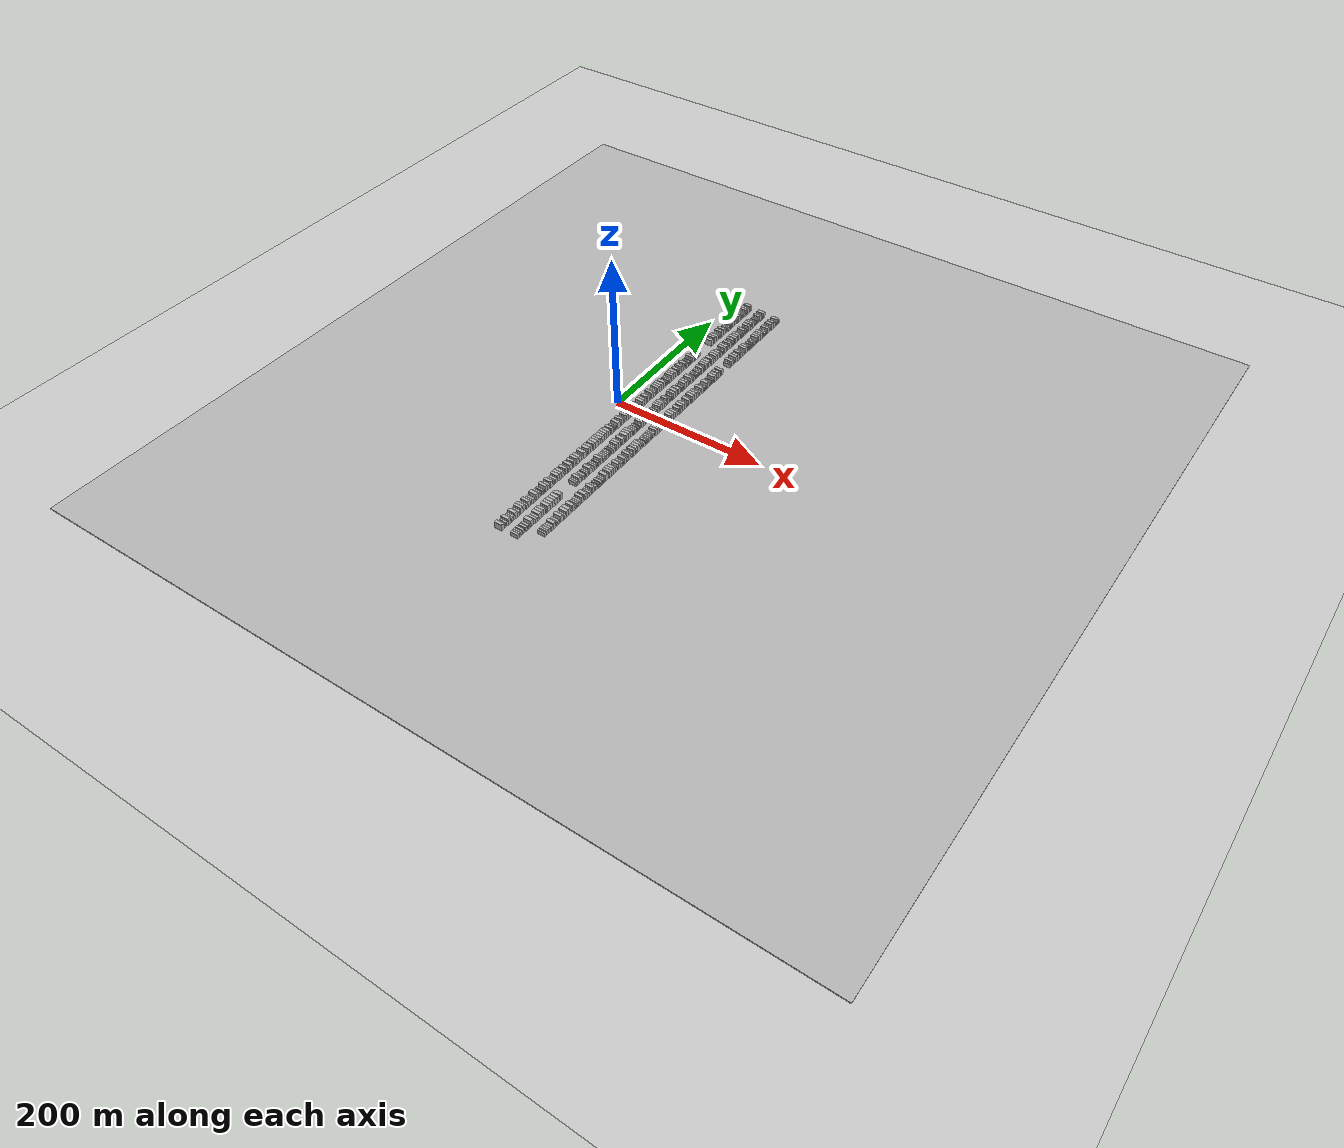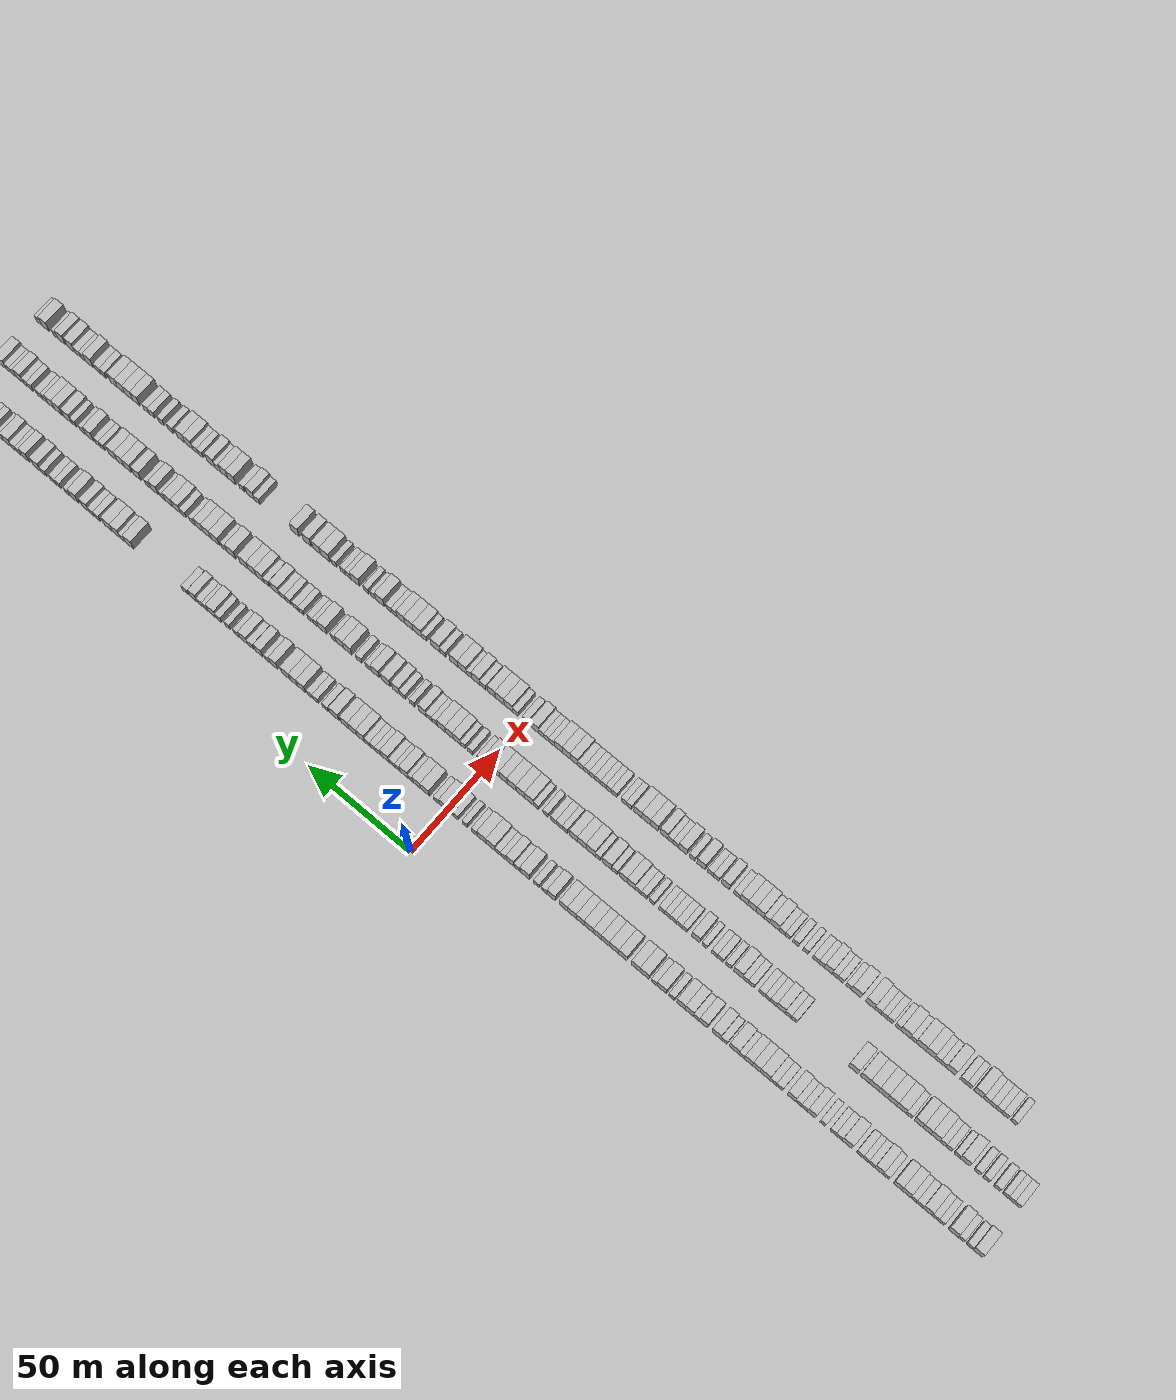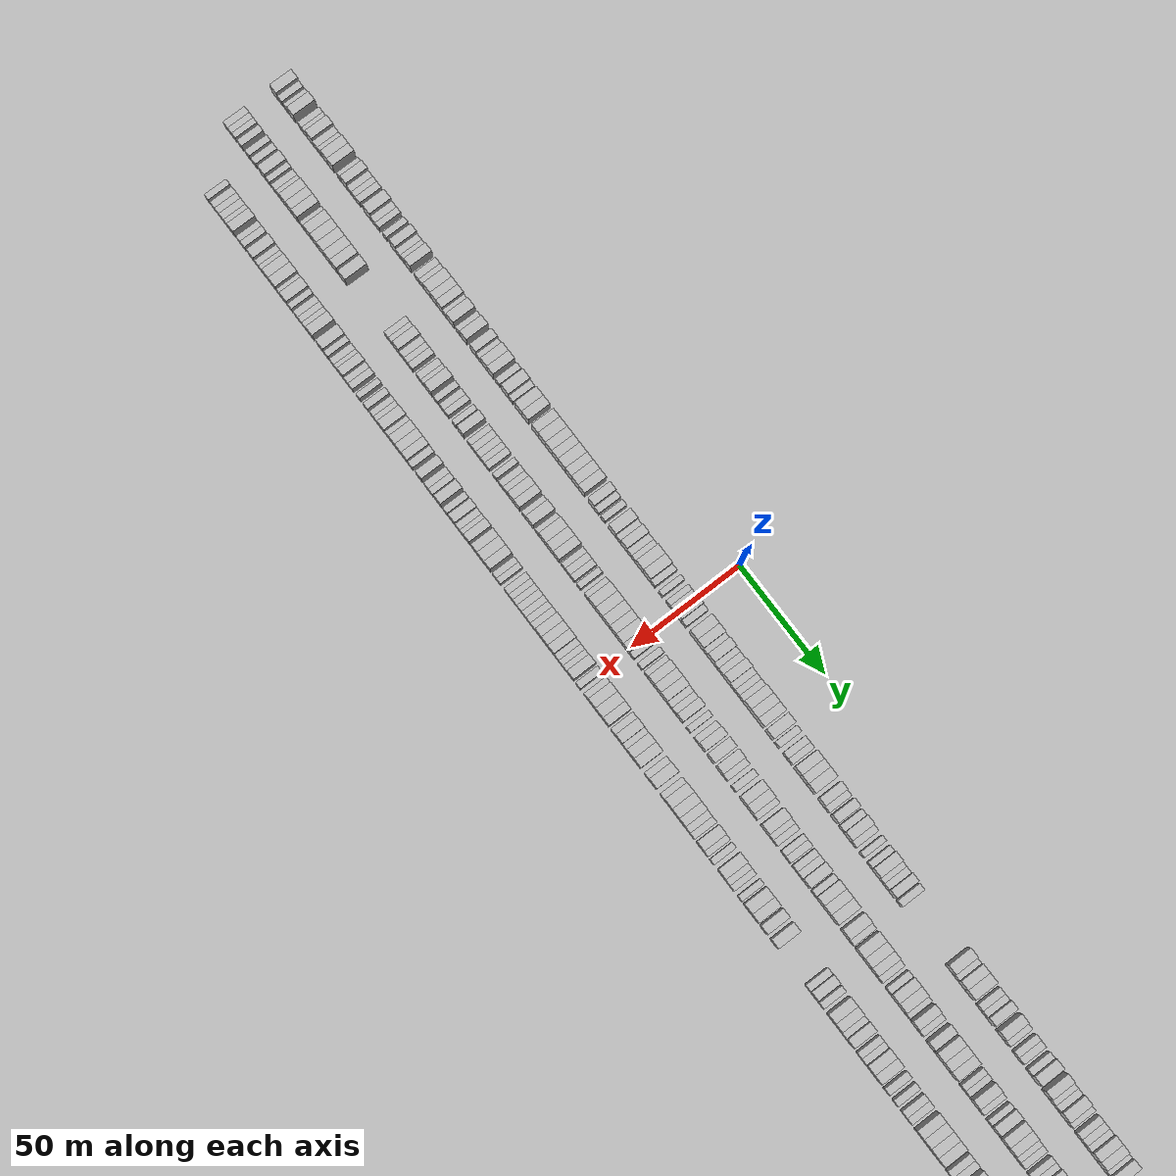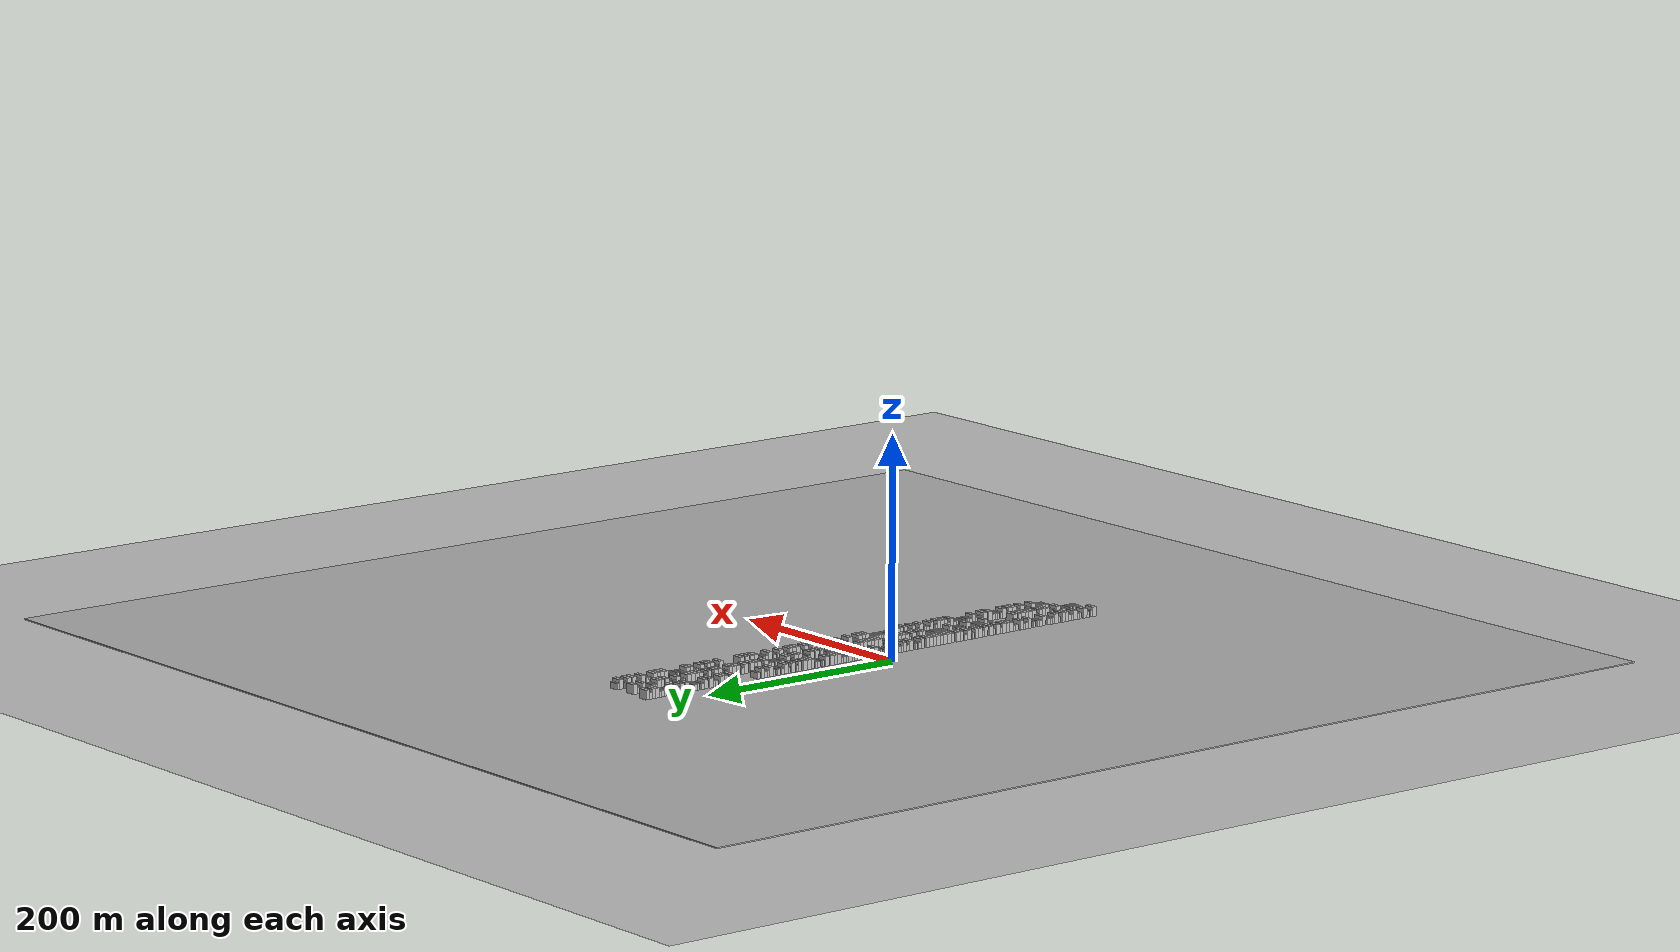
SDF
<?xml version="1.0" encoding="utf-8"?>

<sdf version="1.6">

   <world name="default">

      <gui fullscreen="0">

         <camera name="user_camera">

            <pose>-15 0 4.57585 0 0 0</pose>

            <view_controller>orbit</view_controller>

         </camera>

      </gui>

      <scene>

         <sky>

           <clouds>

             <speed>12</speed>

           </clouds>

         </sky>

         <ambient>0.4 0.4 0.4 1</ambient>

         <background>0.7 0.7 0.7 1</background>

         <shadows>1</shadows>

      </scene>

      <gravity>0 0 -9.8066</gravity>

      <magnetic_field>6e-06 2.3e-05 -4.2e-05</magnetic_field>

      <physics default="0" name="default_physics" type="ode">

         <ode>

            <solver>

               <type>quick</type>

               <iters>10</iters>

               <sor>1.0</sor>

               <use_dynamic_moi_rescaling>0</use_dynamic_moi_rescaling>

            </solver>

            <constraints>

               <cfm>0</cfm>

               <erp>0.2</erp>

               <contact_max_correcting_vel>100</contact_max_correcting_vel>

               <contact_surface_layer>0.001</contact_surface_layer>

            </constraints>

         </ode>

         <max_step_size>0.004</max_step_size>

         <real_time_factor>1</real_time_factor>

         <real_time_update_rate>250</real_time_update_rate>

      </physics>

      <light name="sun" type="directional">

         <cast_shadows>1</cast_shadows>

         <pose>0 0 10 0 0 0</pose>

         <diffuse>0.8 0.8 0.8 1</diffuse>

         <specular>0.2 0.2 0.2 1</specular>

         <attenuation>

            <range>1000</range>

            <constant>0.9</constant>

            <linear>0.01</linear>

            <quadratic>0.001</quadratic>

         </attenuation>

         <direction>-0.5 0.1 -0.9</direction>

      </light>

      <include>

         <name>ground_plane_1</name>

         <uri>model://HANNAS_ground_plane</uri>

         <pose>0 0 0  0 0 0</pose>

      </include>

      <include>

         <name>ground_plane_2</name>

         <uri>model://HANNAS_ground_plane</uri>

         <pose>100 0 0  0 0 0</pose>

      </include>

      <model name="building_1">

         <static>1</static>

         <pose frame="">25.0000 -245.9098 0 0.000000 0.000000 0.000000</pose>

         <link name="link">

            <pose frame="">0 0 4.50 0 0 0</pose>

            <collision name="collision">

               <geometry>

                  <box>

                     <size>10.0000 4.1804 9.0000</size>

                  </box>

               </geometry>

               <max_contacts>10</max_contacts>

               <surface>

                  <contact>

                     <ode/>

                  </contact>

                  <bounce/>

                  <friction>

                     <torsional>

                        <ode/>

                     </torsional>

                     <ode/>

                  </friction>

               </surface>

            </collision>

            <visual name="visual">

               <cast_shadows>0</cast_shadows>

               <geometry>

                  <box>

                     <size>10.0000 4.1804 9.0000</size>

                  </box>

               </geometry>

               <material>

                  <script>

                     <uri>model://HANNAS_wall/materials/scripts</uri>

                     <uri>model://HANNAS_wall/materials/textures</uri>

                     <name>vrc/HANNAS_wall</name>

                  </script>

               </material>

            </visual>

            <self_collide>0</self_collide>

            <enable_wind>0</enable_wind>

            <kinematic>0</kinematic>

         </link>

      </model>

      <model name="building_2">

         <static>1</static>

         <pose frame="">25.0000 -242.4073 0 0.000000 0.000000 0.000000</pose>

         <link name="link">

            <pose frame="">0 0 3.00 0 0 0</pose>

            <collision name="collision">

               <geometry>

                  <box>

                     <size>10.0000 2.8245 6.0000</size>

                  </box>

               </geometry>

               <max_contacts>10</max_contacts>

               <surface>

                  <contact>

                     <ode/>

                  </contact>

                  <bounce/>

                  <friction>

                     <torsional>

                        <ode/>

                     </torsional>

                     <ode/>

                  </friction>

               </surface>

            </collision>

            <visual name="visual">

               <cast_shadows>0</cast_shadows>

               <geometry>

                  <box>

                     <size>10.0000 2.8245 6.0000</size>

                  </box>

               </geometry>

               <material>

                  <script>

                     <uri>model://HANNAS_wall/materials/scripts</uri>

                     <uri>model://HANNAS_wall/materials/textures</uri>

                     <name>vrc/HANNAS_wall</name>

                  </script>

               </material>

            </visual>

            <self_collide>0</self_collide>

            <enable_wind>0</enable_wind>

            <kinematic>0</kinematic>

         </link>

      </model>

      <model name="building_3">

         <static>1</static>

         <pose frame="">25.0000 -238.5863 0 0.000000 0.000000 0.000000</pose>

         <link name="link">

            <pose frame="">0 0 3.00 0 0 0</pose>

            <collision name="collision">

               <geometry>

                  <box>

                     <size>10.0000 2.8175 6.0000</size>

                  </box>

               </geometry>

               <max_contacts>10</max_contacts>

               <surface>

                  <contact>

                     <ode/>

                  </contact>

                  <bounce/>

                  <friction>

                     <torsional>

                        <ode/>

                     </torsional>

                     <ode/>

                  </friction>

               </surface>

            </collision>

            <visual name="visual">

               <cast_shadows>0</cast_shadows>

               <geometry>

                  <box>

                     <size>10.0000 2.8175 6.0000</size>

                  </box>

               </geometry>

               <material>

                  <script>

                     <uri>model://HANNAS_wall/materials/scripts</uri>

                     <uri>model://HANNAS_wall/materials/textures</uri>

                     <name>vrc/HANNAS_wall</name>

                  </script>

               </material>

            </visual>

            <self_collide>0</self_collide>

            <enable_wind>0</enable_wind>

            <kinematic>0</kinematic>

         </link>

      </model>

      <model name="building_4">

         <static>1</static>

         <pose frame="">25.0000 -235.1116 0 0.000000 0.000000 0.000000</pose>

         <link name="link">

            <pose frame="">0 0 4.50 0 0 0</pose>

            <collision name="collision">

               <geometry>

                  <box>

                     <size>10.0000 4.1319 9.0000</size>

                  </box>

               </geometry>

               <max_contacts>10</max_contacts>

               <surface>

                  <contact>

                     <ode/>

                  </contact>

                  <bounce/>

                  <friction>

                     <torsional>

                        <ode/>

                     </torsional>

                     <ode/>

                  </friction>

               </surface>

            </collision>

            <visual name="visual">

               <cast_shadows>0</cast_shadows>

               <geometry>

                  <box>

                     <size>10.0000 4.1319 9.0000</size>

                  </box>

               </geometry>

               <material>

                  <script>

                     <uri>model://HANNAS_wall/materials/scripts</uri>

                     <uri>model://HANNAS_wall/materials/textures</uri>

                     <name>vrc/HANNAS_wall</name>

                  </script>

               </material>

            </visual>

            <self_collide>0</self_collide>

            <enable_wind>0</enable_wind>

            <kinematic>0</kinematic>

         </link>

      </model>

      <model name="building_5">

         <static>1</static>

         <pose frame="">25.0000 -229.7799 0 0.000000 0.000000 0.000000</pose>

         <link name="link">

            <pose frame="">0 0 3.00 0 0 0</pose>

            <collision name="collision">

               <geometry>

                  <box>

                     <size>10.0000 2.5315 6.0000</size>

                  </box>

               </geometry>

               <max_contacts>10</max_contacts>

               <surface>

                  <contact>

                     <ode/>

                  </contact>

                  <bounce/>

                  <friction>

                     <torsional>

                        <ode/>

                     </torsional>

                     <ode/>

                  </friction>

               </surface>

            </collision>

            <visual name="visual">

               <cast_shadows>0</cast_shadows>

               <geometry>

                  <box>

                     <size>10.0000 2.5315 6.0000</size>

                  </box>

               </geometry>

               <material>

                  <script>

                     <uri>model://HANNAS_wall/materials/scripts</uri>

                     <uri>model://HANNAS_wall/materials/textures</uri>

                     <name>vrc/HANNAS_wall</name>

                  </script>

               </material>

            </visual>

            <self_collide>0</self_collide>

            <enable_wind>0</enable_wind>

            <kinematic>0</kinematic>

         </link>

      </model>

      <model name="building_6">

         <static>1</static>

         <pose frame="">25.0000 -227.1085 0 0.000000 0.000000 0.000000</pose>

         <link name="link">

            <pose frame="">0 0 3.00 0 0 0</pose>

            <collision name="collision">

               <geometry>

                  <box>

                     <size>10.0000 2.8113 6.0000</size>

                  </box>

               </geometry>

               <max_contacts>10</max_contacts>

               <surface>

                  <contact>

                     <ode/>

                  </contact>

                  <bounce/>

                  <friction>

                     <torsional>

                        <ode/>

                     </torsional>

                     <ode/>

                  </friction>

               </surface>

            </collision>

            <visual name="visual">

               <cast_shadows>0</cast_shadows>

               <geometry>

                  <box>

                     <size>10.0000 2.8113 6.0000</size>

                  </box>

               </geometry>

               <material>

                  <script>

                     <uri>model://HANNAS_wall/materials/scripts</uri>

                     <uri>model://HANNAS_wall/materials/textures</uri>

                     <name>vrc/HANNAS_wall</name>

                  </script>

               </material>

            </visual>

            <self_collide>0</self_collide>

            <enable_wind>0</enable_wind>

            <kinematic>0</kinematic>

         </link>

      </model>

      <model name="building_7">

         <static>1</static>

         <pose frame="">25.0000 -223.6957 0 0.000000 0.000000 0.000000</pose>

         <link name="link">

            <pose frame="">0 0 4.50 0 0 0</pose>

            <collision name="collision">

               <geometry>

                  <box>

                     <size>10.0000 4.0144 9.0000</size>

                  </box>

               </geometry>

               <max_contacts>10</max_contacts>

               <surface>

                  <contact>

                     <ode/>

                  </contact>

                  <bounce/>

                  <friction>

                     <torsional>

                        <ode/>

                     </torsional>

                     <ode/>

                  </friction>

               </surface>

            </collision>

            <visual name="visual">

               <cast_shadows>0</cast_shadows>

               <geometry>

                  <box>

                     <size>10.0000 4.0144 9.0000</size>

                  </box>

               </geometry>

               <material>

                  <script>

                     <uri>model://HANNAS_wall/materials/scripts</uri>

                     <uri>model://HANNAS_wall/materials/textures</uri>

                     <name>vrc/HANNAS_wall</name>

                  </script>

               </material>

            </visual>

            <self_collide>0</self_collide>

            <enable_wind>0</enable_wind>

            <kinematic>0</kinematic>

         </link>

      </model>

      <model name="building_8">

         <static>1</static>

         <pose frame="">25.0000 -220.2198 0 0.000000 0.000000 0.000000</pose>

         <link name="link">

            <pose frame="">0 0 3.00 0 0 0</pose>

            <collision name="collision">

               <geometry>

                  <box>

                     <size>10.0000 2.9374 6.0000</size>

                  </box>

               </geometry>

               <max_contacts>10</max_contacts>

               <surface>

                  <contact>

                     <ode/>

                  </contact>

                  <bounce/>

                  <friction>

                     <torsional>

                        <ode/>

                     </torsional>

                     <ode/>

                  </friction>

               </surface>

            </collision>

            <visual name="visual">

               <cast_shadows>0</cast_shadows>

               <geometry>

                  <box>

                     <size>10.0000 2.9374 6.0000</size>

                  </box>

               </geometry>

               <material>

                  <script>

                     <uri>model://HANNAS_wall/materials/scripts</uri>

                     <uri>model://HANNAS_wall/materials/textures</uri>

                     <name>vrc/HANNAS_wall</name>

                  </script>

               </material>

            </visual>

            <self_collide>0</self_collide>

            <enable_wind>0</enable_wind>

            <kinematic>0</kinematic>

         </link>

      </model>

      <model name="building_9">

         <static>1</static>

         <pose frame="">25.0000 -217.4008 0 0.000000 0.000000 0.000000</pose>

         <link name="link">

            <pose frame="">0 0 3.00 0 0 0</pose>

            <collision name="collision">

               <geometry>

                  <box>

                     <size>10.0000 2.7006 6.0000</size>

                  </box>

               </geometry>

               <max_contacts>10</max_contacts>

               <surface>

                  <contact>

                     <ode/>

                  </contact>

                  <bounce/>

                  <friction>

                     <torsional>

                        <ode/>

                     </torsional>

                     <ode/>

                  </friction>

               </surface>

            </collision>

            <visual name="visual">

               <cast_shadows>0</cast_shadows>

               <geometry>

                  <box>

                     <size>10.0000 2.7006 6.0000</size>

                  </box>

               </geometry>

               <material>

                  <script>

                     <uri>model://HANNAS_wall/materials/scripts</uri>

                     <uri>model://HANNAS_wall/materials/textures</uri>

                     <name>vrc/HANNAS_wall</name>

                  </script>

               </material>

            </visual>

            <self_collide>0</self_collide>

            <enable_wind>0</enable_wind>

            <kinematic>0</kinematic>

         </link>

      </model>

      <model name="building_10">

         <static>1</static>

         <pose frame="">25.0000 -214.0906 0 0.000000 0.000000 0.000000</pose>

         <link name="link">

            <pose frame="">0 0 4.50 0 0 0</pose>

            <collision name="collision">

               <geometry>

                  <box>

                     <size>10.0000 3.9199 9.0000</size>

                  </box>

               </geometry>

               <max_contacts>10</max_contacts>

               <surface>

                  <contact>

                     <ode/>

                  </contact>

                  <bounce/>

                  <friction>

                     <torsional>

                        <ode/>

                     </torsional>

                     <ode/>

                  </friction>

               </surface>

            </collision>

            <visual name="visual">

               <cast_shadows>0</cast_shadows>

               <geometry>

                  <box>

                     <size>10.0000 3.9199 9.0000</size>

                  </box>

               </geometry>

               <material>

                  <script>

                     <uri>model://HANNAS_wall/materials/scripts</uri>

                     <uri>model://HANNAS_wall/materials/textures</uri>

                     <name>vrc/HANNAS_wall</name>

                  </script>

               </material>

            </visual>

            <self_collide>0</self_collide>

            <enable_wind>0</enable_wind>

            <kinematic>0</kinematic>

         </link>

      </model>

      <model name="building_11">

         <static>1</static>

         <pose frame="">25.0000 -210.3249 0 0.000000 0.000000 0.000000</pose>

         <link name="link">

            <pose frame="">0 0 4.50 0 0 0</pose>

            <collision name="collision">

               <geometry>

                  <box>

                     <size>10.0000 3.6115 9.0000</size>

                  </box>

               </geometry>

               <max_contacts>10</max_contacts>

               <surface>

                  <contact>

                     <ode/>

                  </contact>

                  <bounce/>

                  <friction>

                     <torsional>

                        <ode/>

                     </torsional>

                     <ode/>

                  </friction>

               </surface>

            </collision>

            <visual name="visual">

               <cast_shadows>0</cast_shadows>

               <geometry>

                  <box>

                     <size>10.0000 3.6115 9.0000</size>

                  </box>

               </geometry>

               <material>

                  <script>

                     <uri>model://HANNAS_wall/materials/scripts</uri>

                     <uri>model://HANNAS_wall/materials/textures</uri>

                     <name>vrc/HANNAS_wall</name>

                  </script>

               </material>

            </visual>

            <self_collide>0</self_collide>

            <enable_wind>0</enable_wind>

            <kinematic>0</kinematic>

         </link>

      </model>

      <model name="building_12">

         <static>1</static>

         <pose frame="">25.0000 -205.1551 0 0.000000 0.000000 0.000000</pose>

         <link name="link">

            <pose frame="">0 0 3.00 0 0 0</pose>

            <collision name="collision">

               <geometry>

                  <box>

                     <size>10.0000 2.7282 6.0000</size>

                  </box>

               </geometry>

               <max_contacts>10</max_contacts>

               <surface>

                  <contact>

                     <ode/>

                  </contact>

                  <bounce/>

                  <friction>

                     <torsional>

                        <ode/>

                     </torsional>

                     <ode/>

                  </friction>

               </surface>

            </collision>

            <visual name="visual">

               <cast_shadows>0</cast_shadows>

               <geometry>

                  <box>

                     <size>10.0000 2.7282 6.0000</size>

                  </box>

               </geometry>

               <material>

                  <script>

                     <uri>model://HANNAS_wall/materials/scripts</uri>

                     <uri>model://HANNAS_wall/materials/textures</uri>

                     <name>vrc/HANNAS_wall</name>

                  </script>

               </material>

            </visual>

            <self_collide>0</self_collide>

            <enable_wind>0</enable_wind>

            <kinematic>0</kinematic>

         </link>

      </model>

      <model name="building_13">

         <static>1</static>

         <pose frame="">25.0000 -201.9180 0 0.000000 0.000000 0.000000</pose>

         <link name="link">

            <pose frame="">0 0 4.50 0 0 0</pose>

            <collision name="collision">

               <geometry>

                  <box>

                     <size>10.0000 3.7458 9.0000</size>

                  </box>

               </geometry>

               <max_contacts>10</max_contacts>

               <surface>

                  <contact>

                     <ode/>

                  </contact>

                  <bounce/>

                  <friction>

                     <torsional>

                        <ode/>

                     </torsional>

                     <ode/>

                  </friction>

               </surface>

            </collision>

            <visual name="visual">

               <cast_shadows>0</cast_shadows>

               <geometry>

                  <box>

                     <size>10.0000 3.7458 9.0000</size>

                  </box>

               </geometry>

               <material>

                  <script>

                     <uri>model://HANNAS_wall/materials/scripts</uri>

                     <uri>model://HANNAS_wall/materials/textures</uri>

                     <name>vrc/HANNAS_wall</name>

                  </script>

               </material>

            </visual>

            <self_collide>0</self_collide>

            <enable_wind>0</enable_wind>

            <kinematic>0</kinematic>

         </link>

      </model>

      <model name="building_14">

         <static>1</static>

         <pose frame="">25.0000 -198.6531 0 0.000000 0.000000 0.000000</pose>

         <link name="link">

            <pose frame="">0 0 3.00 0 0 0</pose>

            <collision name="collision">

               <geometry>

                  <box>

                     <size>10.0000 2.7839 6.0000</size>

                  </box>

               </geometry>

               <max_contacts>10</max_contacts>

               <surface>

                  <contact>

                     <ode/>

                  </contact>

                  <bounce/>

                  <friction>

                     <torsional>

                        <ode/>

                     </torsional>

                     <ode/>

                  </friction>

               </surface>

            </collision>

            <visual name="visual">

               <cast_shadows>0</cast_shadows>

               <geometry>

                  <box>

                     <size>10.0000 2.7839 6.0000</size>

                  </box>

               </geometry>

               <material>

                  <script>

                     <uri>model://HANNAS_wall/materials/scripts</uri>

                     <uri>model://HANNAS_wall/materials/textures</uri>

                     <name>vrc/HANNAS_wall</name>

                  </script>

               </material>

            </visual>

            <self_collide>0</self_collide>

            <enable_wind>0</enable_wind>

            <kinematic>0</kinematic>

         </link>

      </model>

      <model name="building_15">

         <static>1</static>

         <pose frame="">25.0000 -196.0487 0 0.000000 0.000000 0.000000</pose>

         <link name="link">

            <pose frame="">0 0 3.00 0 0 0</pose>

            <collision name="collision">

               <geometry>

                  <box>

                     <size>10.0000 2.4248 6.0000</size>

                  </box>

               </geometry>

               <max_contacts>10</max_contacts>

               <surface>

                  <contact>

                     <ode/>

                  </contact>

                  <bounce/>

                  <friction>

                     <torsional>

                        <ode/>

                     </torsional>

                     <ode/>

                  </friction>

               </surface>

            </collision>

            <visual name="visual">

               <cast_shadows>0</cast_shadows>

               <geometry>

                  <box>

                     <size>10.0000 2.4248 6.0000</size>

                  </box>

               </geometry>

               <material>

                  <script>

                     <uri>model://HANNAS_wall/materials/scripts</uri>

                     <uri>model://HANNAS_wall/materials/textures</uri>

                     <name>vrc/HANNAS_wall</name>

                  </script>

               </material>

            </visual>

            <self_collide>0</self_collide>

            <enable_wind>0</enable_wind>

            <kinematic>0</kinematic>

         </link>

      </model>

      <model name="building_16">

         <static>1</static>

         <pose frame="">25.0000 -193.3712 0 0.000000 0.000000 0.000000</pose>

         <link name="link">

            <pose frame="">0 0 3.00 0 0 0</pose>

            <collision name="collision">

               <geometry>

                  <box>

                     <size>10.0000 2.9303 6.0000</size>

                  </box>

               </geometry>

               <max_contacts>10</max_contacts>

               <surface>

                  <contact>

                     <ode/>

                  </contact>

                  <bounce/>

                  <friction>

                     <torsional>

                        <ode/>

                     </torsional>

                     <ode/>

                  </friction>

               </surface>

            </collision>

            <visual name="visual">

               <cast_shadows>0</cast_shadows>

               <geometry>

                  <box>

                     <size>10.0000 2.9303 6.0000</size>

                  </box>

               </geometry>

               <material>

                  <script>

                     <uri>model://HANNAS_wall/materials/scripts</uri>

                     <uri>model://HANNAS_wall/materials/textures</uri>

                     <name>vrc/HANNAS_wall</name>

                  </script>

               </material>

            </visual>

            <self_collide>0</self_collide>

            <enable_wind>0</enable_wind>

            <kinematic>0</kinematic>

         </link>

      </model>

      <model name="building_17">

         <static>1</static>

         <pose frame="">25.0000 -187.6627 0 0.000000 0.000000 0.000000</pose>

         <link name="link">

            <pose frame="">0 0 4.50 0 0 0</pose>

            <collision name="collision">

               <geometry>

                  <box>

                     <size>10.0000 4.4866 9.0000</size>

                  </box>

               </geometry>

               <max_contacts>10</max_contacts>

               <surface>

                  <contact>

                     <ode/>

                  </contact>

                  <bounce/>

                  <friction>

                     <torsional>

                        <ode/>

                     </torsional>

                     <ode/>

                  </friction>

               </surface>

            </collision>

            <visual name="visual">

               <cast_shadows>0</cast_shadows>

               <geometry>

                  <box>

                     <size>10.0000 4.4866 9.0000</size>

                  </box>

               </geometry>

               <material>

                  <script>

                     <uri>model://HANNAS_wall/materials/scripts</uri>

                     <uri>model://HANNAS_wall/materials/textures</uri>

                     <name>vrc/HANNAS_wall</name>

                  </script>

               </material>

            </visual>

            <self_collide>0</self_collide>

            <enable_wind>0</enable_wind>

            <kinematic>0</kinematic>

         </link>

      </model>

      <model name="building_18">

         <static>1</static>

         <pose frame="">25.0000 -183.9223 0 0.000000 0.000000 0.000000</pose>

         <link name="link">

            <pose frame="">0 0 3.00 0 0 0</pose>

            <collision name="collision">

               <geometry>

                  <box>

                     <size>10.0000 2.9942 6.0000</size>

                  </box>

               </geometry>

               <max_contacts>10</max_contacts>

               <surface>

                  <contact>

                     <ode/>

                  </contact>

                  <bounce/>

                  <friction>

                     <torsional>

                        <ode/>

                     </torsional>

                     <ode/>

                  </friction>

               </surface>

            </collision>

            <visual name="visual">

               <cast_shadows>0</cast_shadows>

               <geometry>

                  <box>

                     <size>10.0000 2.9942 6.0000</size>

                  </box>

               </geometry>

               <material>

                  <script>

                     <uri>model://HANNAS_wall/materials/scripts</uri>

                     <uri>model://HANNAS_wall/materials/textures</uri>

                     <name>vrc/HANNAS_wall</name>

                  </script>

               </material>

            </visual>

            <self_collide>0</self_collide>

            <enable_wind>0</enable_wind>

            <kinematic>0</kinematic>

         </link>

      </model>

      <model name="building_19">

         <static>1</static>

         <pose frame="">25.0000 -181.1492 0 0.000000 0.000000 0.000000</pose>

         <link name="link">

            <pose frame="">0 0 3.00 0 0 0</pose>

            <collision name="collision">

               <geometry>

                  <box>

                     <size>10.0000 2.5520 6.0000</size>

                  </box>

               </geometry>

               <max_contacts>10</max_contacts>

               <surface>

                  <contact>

                     <ode/>

                  </contact>

                  <bounce/>

                  <friction>

                     <torsional>

                        <ode/>

                     </torsional>

                     <ode/>

                  </friction>

               </surface>

            </collision>

            <visual name="visual">

               <cast_shadows>0</cast_shadows>

               <geometry>

                  <box>

                     <size>10.0000 2.5520 6.0000</size>

                  </box>

               </geometry>

               <material>

                  <script>

                     <uri>model://HANNAS_wall/materials/scripts</uri>

                     <uri>model://HANNAS_wall/materials/textures</uri>

                     <name>vrc/HANNAS_wall</name>

                  </script>

               </material>

            </visual>

            <self_collide>0</self_collide>

            <enable_wind>0</enable_wind>

            <kinematic>0</kinematic>

         </link>

      </model>

      <model name="building_20">

         <static>1</static>

         <pose frame="">25.0000 -176.5829 0 0.000000 0.000000 0.000000</pose>

         <link name="link">

            <pose frame="">0 0 3.00 0 0 0</pose>

            <collision name="collision">

               <geometry>

                  <box>

                     <size>10.0000 2.5806 6.0000</size>

                  </box>

               </geometry>

               <max_contacts>10</max_contacts>

               <surface>

                  <contact>

                     <ode/>

                  </contact>

                  <bounce/>

                  <friction>

                     <torsional>

                        <ode/>

                     </torsional>

                     <ode/>

                  </friction>

               </surface>

            </collision>

            <visual name="visual">

               <cast_shadows>0</cast_shadows>

               <geometry>

                  <box>

                     <size>10.0000 2.5806 6.0000</size>

                  </box>

               </geometry>

               <material>

                  <script>

                     <uri>model://HANNAS_wall/materials/scripts</uri>

                     <uri>model://HANNAS_wall/materials/textures</uri>

                     <name>vrc/HANNAS_wall</name>

                  </script>

               </material>

            </visual>

            <self_collide>0</self_collide>

            <enable_wind>0</enable_wind>

            <kinematic>0</kinematic>

         </link>

      </model>

      <model name="building_21">

         <static>1</static>

         <pose frame="">25.0000 -171.4576 0 0.000000 0.000000 0.000000</pose>

         <link name="link">

            <pose frame="">0 0 4.50 0 0 0</pose>

            <collision name="collision">

               <geometry>

                  <box>

                     <size>10.0000 3.6699 9.0000</size>

                  </box>

               </geometry>

               <max_contacts>10</max_contacts>

               <surface>

                  <contact>

                     <ode/>

                  </contact>

                  <bounce/>

                  <friction>

                     <torsional>

                        <ode/>

                     </torsional>

                     <ode/>

                  </friction>

               </surface>

            </collision>

            <visual name="visual">

               <cast_shadows>0</cast_shadows>

               <geometry>

                  <box>

                     <size>10.0000 3.6699 9.0000</size>

                  </box>

               </geometry>

               <material>

                  <script>

                     <uri>model://HANNAS_wall/materials/scripts</uri>

                     <uri>model://HANNAS_wall/materials/textures</uri>

                     <name>vrc/HANNAS_wall</name>

                  </script>

               </material>

            </visual>

            <self_collide>0</self_collide>

            <enable_wind>0</enable_wind>

            <kinematic>0</kinematic>

         </link>

      </model>

      <model name="building_22">

         <static>1</static>

         <pose frame="">25.0000 -168.2360 0 0.000000 0.000000 0.000000</pose>

         <link name="link">

            <pose frame="">0 0 3.00 0 0 0</pose>

            <collision name="collision">

               <geometry>

                  <box>

                     <size>10.0000 2.7734 6.0000</size>

                  </box>

               </geometry>

               <max_contacts>10</max_contacts>

               <surface>

                  <contact>

                     <ode/>

                  </contact>

                  <bounce/>

                  <friction>

                     <torsional>

                        <ode/>

                     </torsional>

                     <ode/>

                  </friction>

               </surface>

            </collision>

            <visual name="visual">

               <cast_shadows>0</cast_shadows>

               <geometry>

                  <box>

                     <size>10.0000 2.7734 6.0000</size>

                  </box>

               </geometry>

               <material>

                  <script>

                     <uri>model://HANNAS_wall/materials/scripts</uri>

                     <uri>model://HANNAS_wall/materials/textures</uri>

                     <name>vrc/HANNAS_wall</name>

                  </script>

               </material>

            </visual>

            <self_collide>0</self_collide>

            <enable_wind>0</enable_wind>

            <kinematic>0</kinematic>

         </link>

      </model>

      <model name="building_23">

         <static>1</static>

         <pose frame="">25.0000 -165.5248 0 0.000000 0.000000 0.000000</pose>

         <link name="link">

            <pose frame="">0 0 3.00 0 0 0</pose>

            <collision name="collision">

               <geometry>

                  <box>

                     <size>10.0000 2.6490 6.0000</size>

                  </box>

               </geometry>

               <max_contacts>10</max_contacts>

               <surface>

                  <contact>

                     <ode/>

                  </contact>

                  <bounce/>

                  <friction>

                     <torsional>

                        <ode/>

                     </torsional>

                     <ode/>

                  </friction>

               </surface>

            </collision>

            <visual name="visual">

               <cast_shadows>0</cast_shadows>

               <geometry>

                  <box>

                     <size>10.0000 2.6490 6.0000</size>

                  </box>

               </geometry>

               <material>

                  <script>

                     <uri>model://HANNAS_wall/materials/scripts</uri>

                     <uri>model://HANNAS_wall/materials/textures</uri>

                     <name>vrc/HANNAS_wall</name>

                  </script>

               </material>

            </visual>

            <self_collide>0</self_collide>

            <enable_wind>0</enable_wind>

            <kinematic>0</kinematic>

         </link>

      </model>

      <model name="building_24">

         <static>1</static>

         <pose frame="">25.0000 -162.2749 0 0.000000 0.000000 0.000000</pose>

         <link name="link">

            <pose frame="">0 0 4.50 0 0 0</pose>

            <collision name="collision">

               <geometry>

                  <box>

                     <size>10.0000 3.8509 9.0000</size>

                  </box>

               </geometry>

               <max_contacts>10</max_contacts>

               <surface>

                  <contact>

                     <ode/>

                  </contact>

                  <bounce/>

                  <friction>

                     <torsional>

                        <ode/>

                     </torsional>

                     <ode/>

                  </friction>

               </surface>

            </collision>

            <visual name="visual">

               <cast_shadows>0</cast_shadows>

               <geometry>

                  <box>

                     <size>10.0000 3.8509 9.0000</size>

                  </box>

               </geometry>

               <material>

                  <script>

                     <uri>model://HANNAS_wall/materials/scripts</uri>

                     <uri>model://HANNAS_wall/materials/textures</uri>

                     <name>vrc/HANNAS_wall</name>

                  </script>

               </material>

            </visual>

            <self_collide>0</self_collide>

            <enable_wind>0</enable_wind>

            <kinematic>0</kinematic>

         </link>

      </model>

      <model name="building_25">

         <static>1</static>

         <pose frame="">25.0000 -156.8620 0 0.000000 0.000000 0.000000</pose>

         <link name="link">

            <pose frame="">0 0 3.00 0 0 0</pose>

            <collision name="collision">

               <geometry>

                  <box>

                     <size>10.0000 2.9749 6.0000</size>

                  </box>

               </geometry>

               <max_contacts>10</max_contacts>

               <surface>

                  <contact>

                     <ode/>

                  </contact>

                  <bounce/>

                  <friction>

                     <torsional>

                        <ode/>

                     </torsional>

                     <ode/>

                  </friction>

               </surface>

            </collision>

            <visual name="visual">

               <cast_shadows>0</cast_shadows>

               <geometry>

                  <box>

                     <size>10.0000 2.9749 6.0000</size>

                  </box>

               </geometry>

               <material>

                  <script>

                     <uri>model://HANNAS_wall/materials/scripts</uri>

                     <uri>model://HANNAS_wall/materials/textures</uri>

                     <name>vrc/HANNAS_wall</name>

                  </script>

               </material>

            </visual>

            <self_collide>0</self_collide>

            <enable_wind>0</enable_wind>

            <kinematic>0</kinematic>

         </link>

      </model>

      <model name="building_26">

         <static>1</static>

         <pose frame="">25.0000 -153.9282 0 0.000000 0.000000 0.000000</pose>

         <link name="link">

            <pose frame="">0 0 3.00 0 0 0</pose>

            <collision name="collision">

               <geometry>

                  <box>

                     <size>10.0000 2.8927 6.0000</size>

                  </box>

               </geometry>

               <max_contacts>10</max_contacts>

               <surface>

                  <contact>

                     <ode/>

                  </contact>

                  <bounce/>

                  <friction>

                     <torsional>

                        <ode/>

                     </torsional>

                     <ode/>

                  </friction>

               </surface>

            </collision>

            <visual name="visual">

               <cast_shadows>0</cast_shadows>

               <geometry>

                  <box>

                     <size>10.0000 2.8927 6.0000</size>

                  </box>

               </geometry>

               <material>

                  <script>

                     <uri>model://HANNAS_wall/materials/scripts</uri>

                     <uri>model://HANNAS_wall/materials/textures</uri>

                     <name>vrc/HANNAS_wall</name>

                  </script>

               </material>

            </visual>

            <self_collide>0</self_collide>

            <enable_wind>0</enable_wind>

            <kinematic>0</kinematic>

         </link>

      </model>

      <model name="building_27">

         <static>1</static>

         <pose frame="">25.0000 -150.2612 0 0.000000 0.000000 0.000000</pose>

         <link name="link">

            <pose frame="">0 0 4.50 0 0 0</pose>

            <collision name="collision">

               <geometry>

                  <box>

                     <size>10.0000 4.4414 9.0000</size>

                  </box>

               </geometry>

               <max_contacts>10</max_contacts>

               <surface>

                  <contact>

                     <ode/>

                  </contact>

                  <bounce/>

                  <friction>

                     <torsional>

                        <ode/>

                     </torsional>

                     <ode/>

                  </friction>

               </surface>

            </collision>

            <visual name="visual">

               <cast_shadows>0</cast_shadows>

               <geometry>

                  <box>

                     <size>10.0000 4.4414 9.0000</size>

                  </box>

               </geometry>

               <material>

                  <script>

                     <uri>model://HANNAS_wall/materials/scripts</uri>

                     <uri>model://HANNAS_wall/materials/textures</uri>

                     <name>vrc/HANNAS_wall</name>

                  </script>

               </material>

            </visual>

            <self_collide>0</self_collide>

            <enable_wind>0</enable_wind>

            <kinematic>0</kinematic>

         </link>

      </model>

      <model name="building_28">

         <static>1</static>

         <pose frame="">25.0000 -146.2379 0 0.000000 0.000000 0.000000</pose>

         <link name="link">

            <pose frame="">0 0 4.50 0 0 0</pose>

            <collision name="collision">

               <geometry>

                  <box>

                     <size>10.0000 3.6051 9.0000</size>

                  </box>

               </geometry>

               <max_contacts>10</max_contacts>

               <surface>

                  <contact>

                     <ode/>

                  </contact>

                  <bounce/>

                  <friction>

                     <torsional>

                        <ode/>

                     </torsional>

                     <ode/>

                  </friction>

               </surface>

            </collision>

            <visual name="visual">

               <cast_shadows>0</cast_shadows>

               <geometry>

                  <box>

                     <size>10.0000 3.6051 9.0000</size>

                  </box>

               </geometry>

               <material>

                  <script>

                     <uri>model://HANNAS_wall/materials/scripts</uri>

                     <uri>model://HANNAS_wall/materials/textures</uri>

                     <name>vrc/HANNAS_wall</name>

                  </script>

               </material>

            </visual>

            <self_collide>0</self_collide>

            <enable_wind>0</enable_wind>

            <kinematic>0</kinematic>

         </link>

      </model>

      <model name="building_29">

         <static>1</static>

         <pose frame="">25.0000 -142.5666 0 0.000000 0.000000 0.000000</pose>

         <link name="link">

            <pose frame="">0 0 4.50 0 0 0</pose>

            <collision name="collision">

               <geometry>

                  <box>

                     <size>10.0000 3.7375 9.0000</size>

                  </box>

               </geometry>

               <max_contacts>10</max_contacts>

               <surface>

                  <contact>

                     <ode/>

                  </contact>

                  <bounce/>

                  <friction>

                     <torsional>

                        <ode/>

                     </torsional>

                     <ode/>

                  </friction>

               </surface>

            </collision>

            <visual name="visual">

               <cast_shadows>0</cast_shadows>

               <geometry>

                  <box>

                     <size>10.0000 3.7375 9.0000</size>

                  </box>

               </geometry>

               <material>

                  <script>

                     <uri>model://HANNAS_wall/materials/scripts</uri>

                     <uri>model://HANNAS_wall/materials/textures</uri>

                     <name>vrc/HANNAS_wall</name>

                  </script>

               </material>

            </visual>

            <self_collide>0</self_collide>

            <enable_wind>0</enable_wind>

            <kinematic>0</kinematic>

         </link>

      </model>

      <model name="building_30">

         <static>1</static>

         <pose frame="">25.0000 -139.4617 0 0.000000 0.000000 0.000000</pose>

         <link name="link">

            <pose frame="">0 0 3.00 0 0 0</pose>

            <collision name="collision">

               <geometry>

                  <box>

                     <size>10.0000 2.4724 6.0000</size>

                  </box>

               </geometry>

               <max_contacts>10</max_contacts>

               <surface>

                  <contact>

                     <ode/>

                  </contact>

                  <bounce/>

                  <friction>

                     <torsional>

                        <ode/>

                     </torsional>

                     <ode/>

                  </friction>

               </surface>

            </collision>

            <visual name="visual">

               <cast_shadows>0</cast_shadows>

               <geometry>

                  <box>

                     <size>10.0000 2.4724 6.0000</size>

                  </box>

               </geometry>

               <material>

                  <script>

                     <uri>model://HANNAS_wall/materials/scripts</uri>

                     <uri>model://HANNAS_wall/materials/textures</uri>

                     <name>vrc/HANNAS_wall</name>

                  </script>

               </material>

            </visual>

            <self_collide>0</self_collide>

            <enable_wind>0</enable_wind>

            <kinematic>0</kinematic>

         </link>

      </model>

      <model name="building_31">

         <static>1</static>

         <pose frame="">25.0000 -135.9966 0 0.000000 0.000000 0.000000</pose>

         <link name="link">

            <pose frame="">0 0 4.50 0 0 0</pose>

            <collision name="collision">

               <geometry>

                  <box>

                     <size>10.0000 4.4577 9.0000</size>

                  </box>

               </geometry>

               <max_contacts>10</max_contacts>

               <surface>

                  <contact>

                     <ode/>

                  </contact>

                  <bounce/>

                  <friction>

                     <torsional>

                        <ode/>

                     </torsional>

                     <ode/>

                  </friction>

               </surface>

            </collision>

            <visual name="visual">

               <cast_shadows>0</cast_shadows>

               <geometry>

                  <box>

                     <size>10.0000 4.4577 9.0000</size>

                  </box>

               </geometry>

               <material>

                  <script>

                     <uri>model://HANNAS_wall/materials/scripts</uri>

                     <uri>model://HANNAS_wall/materials/textures</uri>

                     <name>vrc/HANNAS_wall</name>

                  </script>

               </material>

            </visual>

            <self_collide>0</self_collide>

            <enable_wind>0</enable_wind>

            <kinematic>0</kinematic>

         </link>

      </model>

      <model name="building_32">

         <static>1</static>

         <pose frame="">25.0000 -131.3176 0 0.000000 0.000000 0.000000</pose>

         <link name="link">

            <pose frame="">0 0 3.00 0 0 0</pose>

            <collision name="collision">

               <geometry>

                  <box>

                     <size>10.0000 2.9004 6.0000</size>

                  </box>

               </geometry>

               <max_contacts>10</max_contacts>

               <surface>

                  <contact>

                     <ode/>

                  </contact>

                  <bounce/>

                  <friction>

                     <torsional>

                        <ode/>

                     </torsional>

                     <ode/>

                  </friction>

               </surface>

            </collision>

            <visual name="visual">

               <cast_shadows>0</cast_shadows>

               <geometry>

                  <box>

                     <size>10.0000 2.9004 6.0000</size>

                  </box>

               </geometry>

               <material>

                  <script>

                     <uri>model://HANNAS_wall/materials/scripts</uri>

                     <uri>model://HANNAS_wall/materials/textures</uri>

                     <name>vrc/HANNAS_wall</name>

                  </script>

               </material>

            </visual>

            <self_collide>0</self_collide>

            <enable_wind>0</enable_wind>

            <kinematic>0</kinematic>

         </link>

      </model>

      <model name="building_33">

         <static>1</static>

         <pose frame="">25.0000 -127.7929 0 0.000000 0.000000 0.000000</pose>

         <link name="link">

            <pose frame="">0 0 4.50 0 0 0</pose>

            <collision name="collision">

               <geometry>

                  <box>

                     <size>10.0000 4.1490 9.0000</size>

                  </box>

               </geometry>

               <max_contacts>10</max_contacts>

               <surface>

                  <contact>

                     <ode/>

                  </contact>

                  <bounce/>

                  <friction>

                     <torsional>

                        <ode/>

                     </torsional>

                     <ode/>

                  </friction>

               </surface>

            </collision>

            <visual name="visual">

               <cast_shadows>0</cast_shadows>

               <geometry>

                  <box>

                     <size>10.0000 4.1490 9.0000</size>

                  </box>

               </geometry>

               <material>

                  <script>

                     <uri>model://HANNAS_wall/materials/scripts</uri>

                     <uri>model://HANNAS_wall/materials/textures</uri>

                     <name>vrc/HANNAS_wall</name>

                  </script>

               </material>

            </visual>

            <self_collide>0</self_collide>

            <enable_wind>0</enable_wind>

            <kinematic>0</kinematic>

         </link>

      </model>

      <model name="building_34">

         <static>1</static>

         <pose frame="">25.0000 -121.8239 0 0.000000 0.000000 0.000000</pose>

         <link name="link">

            <pose frame="">0 0 4.50 0 0 0</pose>

            <collision name="collision">

               <geometry>

                  <box>

                     <size>10.0000 3.7891 9.0000</size>

                  </box>

               </geometry>

               <max_contacts>10</max_contacts>

               <surface>

                  <contact>

                     <ode/>

                  </contact>

                  <bounce/>

                  <friction>

                     <torsional>

                        <ode/>

                     </torsional>

                     <ode/>

                  </friction>

               </surface>

            </collision>

            <visual name="visual">

               <cast_shadows>0</cast_shadows>

               <geometry>

                  <box>

                     <size>10.0000 3.7891 9.0000</size>

                  </box>

               </geometry>

               <material>

                  <script>

                     <uri>model://HANNAS_wall/materials/scripts</uri>

                     <uri>model://HANNAS_wall/materials/textures</uri>

                     <name>vrc/HANNAS_wall</name>

                  </script>

               </material>

            </visual>

            <self_collide>0</self_collide>

            <enable_wind>0</enable_wind>

            <kinematic>0</kinematic>

         </link>

      </model>

      <model name="building_35">

         <static>1</static>

         <pose frame="">25.0000 -118.5579 0 0.000000 0.000000 0.000000</pose>

         <link name="link">

            <pose frame="">0 0 3.00 0 0 0</pose>

            <collision name="collision">

               <geometry>

                  <box>

                     <size>10.0000 2.7430 6.0000</size>

                  </box>

               </geometry>

               <max_contacts>10</max_contacts>

               <surface>

                  <contact>

                     <ode/>

                  </contact>

                  <bounce/>

                  <friction>

                     <torsional>

                        <ode/>

                     </torsional>

                     <ode/>

                  </friction>

               </surface>

            </collision>

            <visual name="visual">

               <cast_shadows>0</cast_shadows>

               <geometry>

                  <box>

                     <size>10.0000 2.7430 6.0000</size>

                  </box>

               </geometry>

               <material>

                  <script>

                     <uri>model://HANNAS_wall/materials/scripts</uri>

                     <uri>model://HANNAS_wall/materials/textures</uri>

                     <name>vrc/HANNAS_wall</name>

                  </script>

               </material>

            </visual>

            <self_collide>0</self_collide>

            <enable_wind>0</enable_wind>

            <kinematic>0</kinematic>

         </link>

      </model>

      <model name="building_36">

         <static>1</static>

         <pose frame="">25.0000 -115.2265 0 0.000000 0.000000 0.000000</pose>

         <link name="link">

            <pose frame="">0 0 4.50 0 0 0</pose>

            <collision name="collision">

               <geometry>

                  <box>

                     <size>10.0000 3.9197 9.0000</size>

                  </box>

               </geometry>

               <max_contacts>10</max_contacts>

               <surface>

                  <contact>

                     <ode/>

                  </contact>

                  <bounce/>

                  <friction>

                     <torsional>

                        <ode/>

                     </torsional>

                     <ode/>

                  </friction>

               </surface>

            </collision>

            <visual name="visual">

               <cast_shadows>0</cast_shadows>

               <geometry>

                  <box>

                     <size>10.0000 3.9197 9.0000</size>

                  </box>

               </geometry>

               <material>

                  <script>

                     <uri>model://HANNAS_wall/materials/scripts</uri>

                     <uri>model://HANNAS_wall/materials/textures</uri>

                     <name>vrc/HANNAS_wall</name>

                  </script>

               </material>

            </visual>

            <self_collide>0</self_collide>

            <enable_wind>0</enable_wind>

            <kinematic>0</kinematic>

         </link>

      </model>

      <model name="building_37">

         <static>1</static>

         <pose frame="">25.0000 -111.3429 0 0.000000 0.000000 0.000000</pose>

         <link name="link">

            <pose frame="">0 0 4.50 0 0 0</pose>

            <collision name="collision">

               <geometry>

                  <box>

                     <size>10.0000 3.8475 9.0000</size>

                  </box>

               </geometry>

               <max_contacts>10</max_contacts>

               <surface>

                  <contact>

                     <ode/>

                  </contact>

                  <bounce/>

                  <friction>

                     <torsional>

                        <ode/>

                     </torsional>

                     <ode/>

                  </friction>

               </surface>

            </collision>

            <visual name="visual">

               <cast_shadows>0</cast_shadows>

               <geometry>

                  <box>

                     <size>10.0000 3.8475 9.0000</size>

                  </box>

               </geometry>

               <material>

                  <script>

                     <uri>model://HANNAS_wall/materials/scripts</uri>

                     <uri>model://HANNAS_wall/materials/textures</uri>

                     <name>vrc/HANNAS_wall</name>

                  </script>

               </material>

            </visual>

            <self_collide>0</self_collide>

            <enable_wind>0</enable_wind>

            <kinematic>0</kinematic>

         </link>

      </model>

      <model name="building_38">

         <static>1</static>

         <pose frame="">25.0000 -107.0256 0 0.000000 0.000000 0.000000</pose>

         <link name="link">

            <pose frame="">0 0 3.00 0 0 0</pose>

            <collision name="collision">

               <geometry>

                  <box>

                     <size>10.0000 2.7871 6.0000</size>

                  </box>

               </geometry>

               <max_contacts>10</max_contacts>

               <surface>

                  <contact>

                     <ode/>

                  </contact>

                  <bounce/>

                  <friction>

                     <torsional>

                        <ode/>

                     </torsional>

                     <ode/>

                  </friction>

               </surface>

            </collision>

            <visual name="visual">

               <cast_shadows>0</cast_shadows>

               <geometry>

                  <box>

                     <size>10.0000 2.7871 6.0000</size>

                  </box>

               </geometry>

               <material>

                  <script>

                     <uri>model://HANNAS_wall/materials/scripts</uri>

                     <uri>model://HANNAS_wall/materials/textures</uri>

                     <name>vrc/HANNAS_wall</name>

                  </script>

               </material>

            </visual>

            <self_collide>0</self_collide>

            <enable_wind>0</enable_wind>

            <kinematic>0</kinematic>

         </link>

      </model>

      <model name="building_39">

         <static>1</static>

         <pose frame="">25.0000 -102.3969 0 0.000000 0.000000 0.000000</pose>

         <link name="link">

            <pose frame="">0 0 4.50 0 0 0</pose>

            <collision name="collision">

               <geometry>

                  <box>

                     <size>10.0000 4.4704 9.0000</size>

                  </box>

               </geometry>

               <max_contacts>10</max_contacts>

               <surface>

                  <contact>

                     <ode/>

                  </contact>

                  <bounce/>

                  <friction>

                     <torsional>

                        <ode/>

                     </torsional>

                     <ode/>

                  </friction>

               </surface>

            </collision>

            <visual name="visual">

               <cast_shadows>0</cast_shadows>

               <geometry>

                  <box>

                     <size>10.0000 4.4704 9.0000</size>

                  </box>

               </geometry>

               <material>

                  <script>

                     <uri>model://HANNAS_wall/materials/scripts</uri>

                     <uri>model://HANNAS_wall/materials/textures</uri>

                     <name>vrc/HANNAS_wall</name>

                  </script>

               </material>

            </visual>

            <self_collide>0</self_collide>

            <enable_wind>0</enable_wind>

            <kinematic>0</kinematic>

         </link>

      </model>

      <model name="building_40">

         <static>1</static>

         <pose frame="">25.0000 -98.7976 0 0.000000 0.000000 0.000000</pose>

         <link name="link">

            <pose frame="">0 0 3.00 0 0 0</pose>

            <collision name="collision">

               <geometry>

                  <box>

                     <size>10.0000 2.7282 6.0000</size>

                  </box>

               </geometry>

               <max_contacts>10</max_contacts>

               <surface>

                  <contact>

                     <ode/>

                  </contact>

                  <bounce/>

                  <friction>

                     <torsional>

                        <ode/>

                     </torsional>

                     <ode/>

                  </friction>

               </surface>

            </collision>

            <visual name="visual">

               <cast_shadows>0</cast_shadows>

               <geometry>

                  <box>

                     <size>10.0000 2.7282 6.0000</size>

                  </box>

               </geometry>

               <material>

                  <script>

                     <uri>model://HANNAS_wall/materials/scripts</uri>

                     <uri>model://HANNAS_wall/materials/textures</uri>

                     <name>vrc/HANNAS_wall</name>

                  </script>

               </material>

            </visual>

            <self_collide>0</self_collide>

            <enable_wind>0</enable_wind>

            <kinematic>0</kinematic>

         </link>

      </model>

      <model name="building_41">

         <static>1</static>

         <pose frame="">25.0000 -94.2964 0 0.000000 0.000000 0.000000</pose>

         <link name="link">

            <pose frame="">0 0 4.50 0 0 0</pose>

            <collision name="collision">

               <geometry>

                  <box>

                     <size>10.0000 4.2742 9.0000</size>

                  </box>

               </geometry>

               <max_contacts>10</max_contacts>

               <surface>

                  <contact>

                     <ode/>

                  </contact>

                  <bounce/>

                  <friction>

                     <torsional>

                        <ode/>

                     </torsional>

                     <ode/>

                  </friction>

               </surface>

            </collision>

            <visual name="visual">

               <cast_shadows>0</cast_shadows>

               <geometry>

                  <box>

                     <size>10.0000 4.2742 9.0000</size>

                  </box>

               </geometry>

               <material>

                  <script>

                     <uri>model://HANNAS_wall/materials/scripts</uri>

                     <uri>model://HANNAS_wall/materials/textures</uri>

                     <name>vrc/HANNAS_wall</name>

                  </script>

               </material>

            </visual>

            <self_collide>0</self_collide>

            <enable_wind>0</enable_wind>

            <kinematic>0</kinematic>

         </link>

      </model>

      <model name="building_42">

         <static>1</static>

         <pose frame="">25.0000 -90.1512 0 0.000000 0.000000 0.000000</pose>

         <link name="link">

            <pose frame="">0 0 4.50 0 0 0</pose>

            <collision name="collision">

               <geometry>

                  <box>

                     <size>10.0000 4.0164 9.0000</size>

                  </box>

               </geometry>

               <max_contacts>10</max_contacts>

               <surface>

                  <contact>

                     <ode/>

                  </contact>

                  <bounce/>

                  <friction>

                     <torsional>

                        <ode/>

                     </torsional>

                     <ode/>

                  </friction>

               </surface>

            </collision>

            <visual name="visual">

               <cast_shadows>0</cast_shadows>

               <geometry>

                  <box>

                     <size>10.0000 4.0164 9.0000</size>

                  </box>

               </geometry>

               <material>

                  <script>

                     <uri>model://HANNAS_wall/materials/scripts</uri>

                     <uri>model://HANNAS_wall/materials/textures</uri>

                     <name>vrc/HANNAS_wall</name>

                  </script>

               </material>

            </visual>

            <self_collide>0</self_collide>

            <enable_wind>0</enable_wind>

            <kinematic>0</kinematic>

         </link>

      </model>

      <model name="building_43">

         <static>1</static>

         <pose frame="">25.0000 -84.1910 0 0.000000 0.000000 0.000000</pose>

         <link name="link">

            <pose frame="">0 0 4.50 0 0 0</pose>

            <collision name="collision">

               <geometry>

                  <box>

                     <size>10.0000 3.9040 9.0000</size>

                  </box>

               </geometry>

               <max_contacts>10</max_contacts>

               <surface>

                  <contact>

                     <ode/>

                  </contact>

                  <bounce/>

                  <friction>

                     <torsional>

                        <ode/>

                     </torsional>

                     <ode/>

                  </friction>

               </surface>

            </collision>

            <visual name="visual">

               <cast_shadows>0</cast_shadows>

               <geometry>

                  <box>

                     <size>10.0000 3.9040 9.0000</size>

                  </box>

               </geometry>

               <material>

                  <script>

                     <uri>model://HANNAS_wall/materials/scripts</uri>

                     <uri>model://HANNAS_wall/materials/textures</uri>

                     <name>vrc/HANNAS_wall</name>

                  </script>

               </material>

            </visual>

            <self_collide>0</self_collide>

            <enable_wind>0</enable_wind>

            <kinematic>0</kinematic>

         </link>

      </model>

      <model name="building_44">

         <static>1</static>

         <pose frame="">25.0000 -80.0075 0 0.000000 0.000000 0.000000</pose>

         <link name="link">

            <pose frame="">0 0 4.50 0 0 0</pose>

            <collision name="collision">

               <geometry>

                  <box>

                     <size>10.0000 4.4628 9.0000</size>

                  </box>

               </geometry>

               <max_contacts>10</max_contacts>

               <surface>

                  <contact>

                     <ode/>

                  </contact>

                  <bounce/>

                  <friction>

                     <torsional>

                        <ode/>

                     </torsional>

                     <ode/>

                  </friction>

               </surface>

            </collision>

            <visual name="visual">

               <cast_shadows>0</cast_shadows>

               <geometry>

                  <box>

                     <size>10.0000 4.4628 9.0000</size>

                  </box>

               </geometry>

               <material>

                  <script>

                     <uri>model://HANNAS_wall/materials/scripts</uri>

                     <uri>model://HANNAS_wall/materials/textures</uri>

                     <name>vrc/HANNAS_wall</name>

                  </script>

               </material>

            </visual>

            <self_collide>0</self_collide>

            <enable_wind>0</enable_wind>

            <kinematic>0</kinematic>

         </link>

      </model>

      <model name="building_45">

         <static>1</static>

         <pose frame="">25.0000 -75.8572 0 0.000000 0.000000 0.000000</pose>

         <link name="link">

            <pose frame="">0 0 4.50 0 0 0</pose>

            <collision name="collision">

               <geometry>

                  <box>

                     <size>10.0000 3.8377 9.0000</size>

                  </box>

               </geometry>

               <max_contacts>10</max_contacts>

               <surface>

                  <contact>

                     <ode/>

                  </contact>

                  <bounce/>

                  <friction>

                     <torsional>

                        <ode/>

                     </torsional>

                     <ode/>

                  </friction>

               </surface>

            </collision>

            <visual name="visual">

               <cast_shadows>0</cast_shadows>

               <geometry>

                  <box>

                     <size>10.0000 3.8377 9.0000</size>

                  </box>

               </geometry>

               <material>

                  <script>

                     <uri>model://HANNAS_wall/materials/scripts</uri>

                     <uri>model://HANNAS_wall/materials/textures</uri>

                     <name>vrc/HANNAS_wall</name>

                  </script>

               </material>

            </visual>

            <self_collide>0</self_collide>

            <enable_wind>0</enable_wind>

            <kinematic>0</kinematic>

         </link>

      </model>

      <model name="building_46">

         <static>1</static>

         <pose frame="">25.0000 -72.0961 0 0.000000 0.000000 0.000000</pose>

         <link name="link">

            <pose frame="">0 0 4.50 0 0 0</pose>

            <collision name="collision">

               <geometry>

                  <box>

                     <size>10.0000 3.6846 9.0000</size>

                  </box>

               </geometry>

               <max_contacts>10</max_contacts>

               <surface>

                  <contact>

                     <ode/>

                  </contact>

                  <bounce/>

                  <friction>

                     <torsional>

                        <ode/>

                     </torsional>

                     <ode/>

                  </friction>

               </surface>

            </collision>

            <visual name="visual">

               <cast_shadows>0</cast_shadows>

               <geometry>

                  <box>

                     <size>10.0000 3.6846 9.0000</size>

                  </box>

               </geometry>

               <material>

                  <script>

                     <uri>model://HANNAS_wall/materials/scripts</uri>

                     <uri>model://HANNAS_wall/materials/textures</uri>

                     <name>vrc/HANNAS_wall</name>

                  </script>

               </material>

            </visual>

            <self_collide>0</self_collide>

            <enable_wind>0</enable_wind>

            <kinematic>0</kinematic>

         </link>

      </model>

      <model name="building_47">

         <static>1</static>

         <pose frame="">25.0000 -68.0348 0 0.000000 0.000000 0.000000</pose>

         <link name="link">

            <pose frame="">0 0 4.50 0 0 0</pose>

            <collision name="collision">

               <geometry>

                  <box>

                     <size>10.0000 4.4380 9.0000</size>

                  </box>

               </geometry>

               <max_contacts>10</max_contacts>

               <surface>

                  <contact>

                     <ode/>

                  </contact>

                  <bounce/>

                  <friction>

                     <torsional>

                        <ode/>

                     </torsional>

                     <ode/>

                  </friction>

               </surface>

            </collision>

            <visual name="visual">

               <cast_shadows>0</cast_shadows>

               <geometry>

                  <box>

                     <size>10.0000 4.4380 9.0000</size>

                  </box>

               </geometry>

               <material>

                  <script>

                     <uri>model://HANNAS_wall/materials/scripts</uri>

                     <uri>model://HANNAS_wall/materials/textures</uri>

                     <name>vrc/HANNAS_wall</name>

                  </script>

               </material>

            </visual>

            <self_collide>0</self_collide>

            <enable_wind>0</enable_wind>

            <kinematic>0</kinematic>

         </link>

      </model>

      <model name="building_48">

         <static>1</static>

         <pose frame="">25.0000 -64.0015 0 0.000000 0.000000 0.000000</pose>

         <link name="link">

            <pose frame="">0 0 4.50 0 0 0</pose>

            <collision name="collision">

               <geometry>

                  <box>

                     <size>10.0000 3.6286 9.0000</size>

                  </box>

               </geometry>

               <max_contacts>10</max_contacts>

               <surface>

                  <contact>

                     <ode/>

                  </contact>

                  <bounce/>

                  <friction>

                     <torsional>

                        <ode/>

                     </torsional>

                     <ode/>

                  </friction>

               </surface>

            </collision>

            <visual name="visual">

               <cast_shadows>0</cast_shadows>

               <geometry>

                  <box>

                     <size>10.0000 3.6286 9.0000</size>

                  </box>

               </geometry>

               <material>

                  <script>

                     <uri>model://HANNAS_wall/materials/scripts</uri>

                     <uri>model://HANNAS_wall/materials/textures</uri>

                     <name>vrc/HANNAS_wall</name>

                  </script>

               </material>

            </visual>

            <self_collide>0</self_collide>

            <enable_wind>0</enable_wind>

            <kinematic>0</kinematic>

         </link>

      </model>

      <model name="building_49">

         <static>1</static>

         <pose frame="">25.0000 -60.1346 0 0.000000 0.000000 0.000000</pose>

         <link name="link">

            <pose frame="">0 0 4.50 0 0 0</pose>

            <collision name="collision">

               <geometry>

                  <box>

                     <size>10.0000 4.1053 9.0000</size>

                  </box>

               </geometry>

               <max_contacts>10</max_contacts>

               <surface>

                  <contact>

                     <ode/>

                  </contact>

                  <bounce/>

                  <friction>

                     <torsional>

                        <ode/>

                     </torsional>

                     <ode/>

                  </friction>

               </surface>

            </collision>

            <visual name="visual">

               <cast_shadows>0</cast_shadows>

               <geometry>

                  <box>

                     <size>10.0000 4.1053 9.0000</size>

                  </box>

               </geometry>

               <material>

                  <script>

                     <uri>model://HANNAS_wall/materials/scripts</uri>

                     <uri>model://HANNAS_wall/materials/textures</uri>

                     <name>vrc/HANNAS_wall</name>

                  </script>

               </material>

            </visual>

            <self_collide>0</self_collide>

            <enable_wind>0</enable_wind>

            <kinematic>0</kinematic>

         </link>

      </model>

      <model name="building_50">

         <static>1</static>

         <pose frame="">25.0000 -56.1384 0 0.000000 0.000000 0.000000</pose>

         <link name="link">

            <pose frame="">0 0 4.50 0 0 0</pose>

            <collision name="collision">

               <geometry>

                  <box>

                     <size>10.0000 3.8869 9.0000</size>

                  </box>

               </geometry>

               <max_contacts>10</max_contacts>

               <surface>

                  <contact>

                     <ode/>

                  </contact>

                  <bounce/>

                  <friction>

                     <torsional>

                        <ode/>

                     </torsional>

                     <ode/>

                  </friction>

               </surface>

            </collision>

            <visual name="visual">

               <cast_shadows>0</cast_shadows>

               <geometry>

                  <box>

                     <size>10.0000 3.8869 9.0000</size>

                  </box>

               </geometry>

               <material>

                  <script>

                     <uri>model://HANNAS_wall/materials/scripts</uri>

                     <uri>model://HANNAS_wall/materials/textures</uri>

                     <name>vrc/HANNAS_wall</name>

                  </script>

               </material>

            </visual>

            <self_collide>0</self_collide>

            <enable_wind>0</enable_wind>

            <kinematic>0</kinematic>

         </link>

      </model>

      <model name="building_51">

         <static>1</static>

         <pose frame="">25.0000 -50.2733 0 0.000000 0.000000 0.000000</pose>

         <link name="link">

            <pose frame="">0 0 4.50 0 0 0</pose>

            <collision name="collision">

               <geometry>

                  <box>

                     <size>10.0000 3.8433 9.0000</size>

                  </box>

               </geometry>

               <max_contacts>10</max_contacts>

               <surface>

                  <contact>

                     <ode/>

                  </contact>

                  <bounce/>

                  <friction>

                     <torsional>

                        <ode/>

                     </torsional>

                     <ode/>

                  </friction>

               </surface>

            </collision>

            <visual name="visual">

               <cast_shadows>0</cast_shadows>

               <geometry>

                  <box>

                     <size>10.0000 3.8433 9.0000</size>

                  </box>

               </geometry>

               <material>

                  <script>

                     <uri>model://HANNAS_wall/materials/scripts</uri>

                     <uri>model://HANNAS_wall/materials/textures</uri>

                     <name>vrc/HANNAS_wall</name>

                  </script>

               </material>

            </visual>

            <self_collide>0</self_collide>

            <enable_wind>0</enable_wind>

            <kinematic>0</kinematic>

         </link>

      </model>

      <model name="building_52">

         <static>1</static>

         <pose frame="">25.0000 -46.9566 0 0.000000 0.000000 0.000000</pose>

         <link name="link">

            <pose frame="">0 0 3.00 0 0 0</pose>

            <collision name="collision">

               <geometry>

                  <box>

                     <size>10.0000 2.7902 6.0000</size>

                  </box>

               </geometry>

               <max_contacts>10</max_contacts>

               <surface>

                  <contact>

                     <ode/>

                  </contact>

                  <bounce/>

                  <friction>

                     <torsional>

                        <ode/>

                     </torsional>

                     <ode/>

                  </friction>

               </surface>

            </collision>

            <visual name="visual">

               <cast_shadows>0</cast_shadows>

               <geometry>

                  <box>

                     <size>10.0000 2.7902 6.0000</size>

                  </box>

               </geometry>

               <material>

                  <script>

                     <uri>model://HANNAS_wall/materials/scripts</uri>

                     <uri>model://HANNAS_wall/materials/textures</uri>

                     <name>vrc/HANNAS_wall</name>

                  </script>

               </material>

            </visual>

            <self_collide>0</self_collide>

            <enable_wind>0</enable_wind>

            <kinematic>0</kinematic>

         </link>

      </model>

      <model name="building_53">

         <static>1</static>

         <pose frame="">25.0000 -43.2240 0 0.000000 0.000000 0.000000</pose>

         <link name="link">

            <pose frame="">0 0 3.00 0 0 0</pose>

            <collision name="collision">

               <geometry>

                  <box>

                     <size>10.0000 2.6751 6.0000</size>

                  </box>

               </geometry>

               <max_contacts>10</max_contacts>

               <surface>

                  <contact>

                     <ode/>

                  </contact>

                  <bounce/>

                  <friction>

                     <torsional>

                        <ode/>

                     </torsional>

                     <ode/>

                  </friction>

               </surface>

            </collision>

            <visual name="visual">

               <cast_shadows>0</cast_shadows>

               <geometry>

                  <box>

                     <size>10.0000 2.6751 6.0000</size>

                  </box>

               </geometry>

               <material>

                  <script>

                     <uri>model://HANNAS_wall/materials/scripts</uri>

                     <uri>model://HANNAS_wall/materials/textures</uri>

                     <name>vrc/HANNAS_wall</name>

                  </script>

               </material>

            </visual>

            <self_collide>0</self_collide>

            <enable_wind>0</enable_wind>

            <kinematic>0</kinematic>

         </link>

      </model>

      <model name="building_54">

         <static>1</static>

         <pose frame="">25.0000 -37.6409 0 0.000000 0.000000 0.000000</pose>

         <link name="link">

            <pose frame="">0 0 4.50 0 0 0</pose>

            <collision name="collision">

               <geometry>

                  <box>

                     <size>10.0000 4.4911 9.0000</size>

                  </box>

               </geometry>

               <max_contacts>10</max_contacts>

               <surface>

                  <contact>

                     <ode/>

                  </contact>

                  <bounce/>

                  <friction>

                     <torsional>

                        <ode/>

                     </torsional>

                     <ode/>

                  </friction>

               </surface>

            </collision>

            <visual name="visual">

               <cast_shadows>0</cast_shadows>

               <geometry>

                  <box>

                     <size>10.0000 4.4911 9.0000</size>

                  </box>

               </geometry>

               <material>

                  <script>

                     <uri>model://HANNAS_wall/materials/scripts</uri>

                     <uri>model://HANNAS_wall/materials/textures</uri>

                     <name>vrc/HANNAS_wall</name>

                  </script>

               </material>

            </visual>

            <self_collide>0</self_collide>

            <enable_wind>0</enable_wind>

            <kinematic>0</kinematic>

         </link>

      </model>

      <model name="building_55">

         <static>1</static>

         <pose frame="">25.0000 -33.9652 0 0.000000 0.000000 0.000000</pose>

         <link name="link">

            <pose frame="">0 0 3.00 0 0 0</pose>

            <collision name="collision">

               <geometry>

                  <box>

                     <size>10.0000 2.8602 6.0000</size>

                  </box>

               </geometry>

               <max_contacts>10</max_contacts>

               <surface>

                  <contact>

                     <ode/>

                  </contact>

                  <bounce/>

                  <friction>

                     <torsional>

                        <ode/>

                     </torsional>

                     <ode/>

                  </friction>

               </surface>

            </collision>

            <visual name="visual">

               <cast_shadows>0</cast_shadows>

               <geometry>

                  <box>

                     <size>10.0000 2.8602 6.0000</size>

                  </box>

               </geometry>

               <material>

                  <script>

                     <uri>model://HANNAS_wall/materials/scripts</uri>

                     <uri>model://HANNAS_wall/materials/textures</uri>

                     <name>vrc/HANNAS_wall</name>

                  </script>

               </material>

            </visual>

            <self_collide>0</self_collide>

            <enable_wind>0</enable_wind>

            <kinematic>0</kinematic>

         </link>

      </model>

      <model name="building_56">

         <static>1</static>

         <pose frame="">25.0000 -30.6620 0 0.000000 0.000000 0.000000</pose>

         <link name="link">

            <pose frame="">0 0 4.50 0 0 0</pose>

            <collision name="collision">

               <geometry>

                  <box>

                     <size>10.0000 3.7462 9.0000</size>

                  </box>

               </geometry>

               <max_contacts>10</max_contacts>

               <surface>

                  <contact>

                     <ode/>

                  </contact>

                  <bounce/>

                  <friction>

                     <torsional>

                        <ode/>

                     </torsional>

                     <ode/>

                  </friction>

               </surface>

            </collision>

            <visual name="visual">

               <cast_shadows>0</cast_shadows>

               <geometry>

                  <box>

                     <size>10.0000 3.7462 9.0000</size>

                  </box>

               </geometry>

               <material>

                  <script>

                     <uri>model://HANNAS_wall/materials/scripts</uri>

                     <uri>model://HANNAS_wall/materials/textures</uri>

                     <name>vrc/HANNAS_wall</name>

                  </script>

               </material>

            </visual>

            <self_collide>0</self_collide>

            <enable_wind>0</enable_wind>

            <kinematic>0</kinematic>

         </link>

      </model>

      <model name="building_57">

         <static>1</static>

         <pose frame="">25.0000 -27.4047 0 0.000000 0.000000 0.000000</pose>

         <link name="link">

            <pose frame="">0 0 3.00 0 0 0</pose>

            <collision name="collision">

               <geometry>

                  <box>

                     <size>10.0000 2.7684 6.0000</size>

                  </box>

               </geometry>

               <max_contacts>10</max_contacts>

               <surface>

                  <contact>

                     <ode/>

                  </contact>

                  <bounce/>

                  <friction>

                     <torsional>

                        <ode/>

                     </torsional>

                     <ode/>

                  </friction>

               </surface>

            </collision>

            <visual name="visual">

               <cast_shadows>0</cast_shadows>

               <geometry>

                  <box>

                     <size>10.0000 2.7684 6.0000</size>

                  </box>

               </geometry>

               <material>

                  <script>

                     <uri>model://HANNAS_wall/materials/scripts</uri>

                     <uri>model://HANNAS_wall/materials/textures</uri>

                     <name>vrc/HANNAS_wall</name>

                  </script>

               </material>

            </visual>

            <self_collide>0</self_collide>

            <enable_wind>0</enable_wind>

            <kinematic>0</kinematic>

         </link>

      </model>

      <model name="building_58">

         <static>1</static>

         <pose frame="">25.0000 -24.7375 0 0.000000 0.000000 0.000000</pose>

         <link name="link">

            <pose frame="">0 0 3.00 0 0 0</pose>

            <collision name="collision">

               <geometry>

                  <box>

                     <size>10.0000 2.5661 6.0000</size>

                  </box>

               </geometry>

               <max_contacts>10</max_contacts>

               <surface>

                  <contact>

                     <ode/>

                  </contact>

                  <bounce/>

                  <friction>

                     <torsional>

                        <ode/>

                     </torsional>

                     <ode/>

                  </friction>

               </surface>

            </collision>

            <visual name="visual">

               <cast_shadows>0</cast_shadows>

               <geometry>

                  <box>

                     <size>10.0000 2.5661 6.0000</size>

                  </box>

               </geometry>

               <material>

                  <script>

                     <uri>model://HANNAS_wall/materials/scripts</uri>

                     <uri>model://HANNAS_wall/materials/textures</uri>

                     <name>vrc/HANNAS_wall</name>

                  </script>

               </material>

            </visual>

            <self_collide>0</self_collide>

            <enable_wind>0</enable_wind>

            <kinematic>0</kinematic>

         </link>

      </model>

      <model name="building_59">

         <static>1</static>

         <pose frame="">25.0000 -21.2912 0 0.000000 0.000000 0.000000</pose>

         <link name="link">

            <pose frame="">0 0 4.50 0 0 0</pose>

            <collision name="collision">

               <geometry>

                  <box>

                     <size>10.0000 4.3265 9.0000</size>

                  </box>

               </geometry>

               <max_contacts>10</max_contacts>

               <surface>

                  <contact>

                     <ode/>

                  </contact>

                  <bounce/>

                  <friction>

                     <torsional>

                        <ode/>

                     </torsional>

                     <ode/>

                  </friction>

               </surface>

            </collision>

            <visual name="visual">

               <cast_shadows>0</cast_shadows>

               <geometry>

                  <box>

                     <size>10.0000 4.3265 9.0000</size>

                  </box>

               </geometry>

               <material>

                  <script>

                     <uri>model://HANNAS_wall/materials/scripts</uri>

                     <uri>model://HANNAS_wall/materials/textures</uri>

                     <name>vrc/HANNAS_wall</name>

                  </script>

               </material>

            </visual>

            <self_collide>0</self_collide>

            <enable_wind>0</enable_wind>

            <kinematic>0</kinematic>

         </link>

      </model>

      <model name="building_60">

         <static>1</static>

         <pose frame="">25.0000 -16.9605 0 0.000000 0.000000 0.000000</pose>

         <link name="link">

            <pose frame="">0 0 4.50 0 0 0</pose>

            <collision name="collision">

               <geometry>

                  <box>

                     <size>10.0000 4.3350 9.0000</size>

                  </box>

               </geometry>

               <max_contacts>10</max_contacts>

               <surface>

                  <contact>

                     <ode/>

                  </contact>

                  <bounce/>

                  <friction>

                     <torsional>

                        <ode/>

                     </torsional>

                     <ode/>

                  </friction>

               </surface>

            </collision>

            <visual name="visual">

               <cast_shadows>0</cast_shadows>

               <geometry>

                  <box>

                     <size>10.0000 4.3350 9.0000</size>

                  </box>

               </geometry>

               <material>

                  <script>

                     <uri>model://HANNAS_wall/materials/scripts</uri>

                     <uri>model://HANNAS_wall/materials/textures</uri>

                     <name>vrc/HANNAS_wall</name>

                  </script>

               </material>

            </visual>

            <self_collide>0</self_collide>

            <enable_wind>0</enable_wind>

            <kinematic>0</kinematic>

         </link>

      </model>

      <model name="building_61">

         <static>1</static>

         <pose frame="">25.0000 -13.3949 0 0.000000 0.000000 0.000000</pose>

         <link name="link">

            <pose frame="">0 0 3.00 0 0 0</pose>

            <collision name="collision">

               <geometry>

                  <box>

                     <size>10.0000 2.7962 6.0000</size>

                  </box>

               </geometry>

               <max_contacts>10</max_contacts>

               <surface>

                  <contact>

                     <ode/>

                  </contact>

                  <bounce/>

                  <friction>

                     <torsional>

                        <ode/>

                     </torsional>

                     <ode/>

                  </friction>

               </surface>

            </collision>

            <visual name="visual">

               <cast_shadows>0</cast_shadows>

               <geometry>

                  <box>

                     <size>10.0000 2.7962 6.0000</size>

                  </box>

               </geometry>

               <material>

                  <script>

                     <uri>model://HANNAS_wall/materials/scripts</uri>

                     <uri>model://HANNAS_wall/materials/textures</uri>

                     <name>vrc/HANNAS_wall</name>

                  </script>

               </material>

            </visual>

            <self_collide>0</self_collide>

            <enable_wind>0</enable_wind>

            <kinematic>0</kinematic>

         </link>

      </model>

      <model name="building_62">

         <static>1</static>

         <pose frame="">25.0000 -8.7808 0 0.000000 0.000000 0.000000</pose>

         <link name="link">

            <pose frame="">0 0 3.00 0 0 0</pose>

            <collision name="collision">

               <geometry>

                  <box>

                     <size>10.0000 2.4320 6.0000</size>

                  </box>

               </geometry>

               <max_contacts>10</max_contacts>

               <surface>

                  <contact>

                     <ode/>

                  </contact>

                  <bounce/>

                  <friction>

                     <torsional>

                        <ode/>

                     </torsional>

                     <ode/>

                  </friction>

               </surface>

            </collision>

            <visual name="visual">

               <cast_shadows>0</cast_shadows>

               <geometry>

                  <box>

                     <size>10.0000 2.4320 6.0000</size>

                  </box>

               </geometry>

               <material>

                  <script>

                     <uri>model://HANNAS_wall/materials/scripts</uri>

                     <uri>model://HANNAS_wall/materials/textures</uri>

                     <name>vrc/HANNAS_wall</name>

                  </script>

               </material>

            </visual>

            <self_collide>0</self_collide>

            <enable_wind>0</enable_wind>

            <kinematic>0</kinematic>

         </link>

      </model>

      <model name="building_63">

         <static>1</static>

         <pose frame="">25.0000 -4.3403 0 0.000000 0.000000 0.000000</pose>

         <link name="link">

            <pose frame="">0 0 3.00 0 0 0</pose>

            <collision name="collision">

               <geometry>

                  <box>

                     <size>10.0000 2.4490 6.0000</size>

                  </box>

               </geometry>

               <max_contacts>10</max_contacts>

               <surface>

                  <contact>

                     <ode/>

                  </contact>

                  <bounce/>

                  <friction>

                     <torsional>

                        <ode/>

                     </torsional>

                     <ode/>

                  </friction>

               </surface>

            </collision>

            <visual name="visual">

               <cast_shadows>0</cast_shadows>

               <geometry>

                  <box>

                     <size>10.0000 2.4490 6.0000</size>

                  </box>

               </geometry>

               <material>

                  <script>

                     <uri>model://HANNAS_wall/materials/scripts</uri>

                     <uri>model://HANNAS_wall/materials/textures</uri>

                     <name>vrc/HANNAS_wall</name>

                  </script>

               </material>

            </visual>

            <self_collide>0</self_collide>

            <enable_wind>0</enable_wind>

            <kinematic>0</kinematic>

         </link>

      </model>

      <model name="building_64">

         <static>1</static>

         <pose frame="">25.0000 -1.9005 0 0.000000 0.000000 0.000000</pose>

         <link name="link">

            <pose frame="">0 0 3.00 0 0 0</pose>

            <collision name="collision">

               <geometry>

                  <box>

                     <size>10.0000 2.4306 6.0000</size>

                  </box>

               </geometry>

               <max_contacts>10</max_contacts>

               <surface>

                  <contact>

                     <ode/>

                  </contact>

                  <bounce/>

                  <friction>

                     <torsional>

                        <ode/>

                     </torsional>

                     <ode/>

                  </friction>

               </surface>

            </collision>

            <visual name="visual">

               <cast_shadows>0</cast_shadows>

               <geometry>

                  <box>

                     <size>10.0000 2.4306 6.0000</size>

                  </box>

               </geometry>

               <material>

                  <script>

                     <uri>model://HANNAS_wall/materials/scripts</uri>

                     <uri>model://HANNAS_wall/materials/textures</uri>

                     <name>vrc/HANNAS_wall</name>

                  </script>

               </material>

            </visual>

            <self_collide>0</self_collide>

            <enable_wind>0</enable_wind>

            <kinematic>0</kinematic>

         </link>

      </model>

      <model name="building_65">

         <static>1</static>

         <pose frame="">25.0000 1.4244 0 0.000000 0.000000 0.000000</pose>

         <link name="link">

            <pose frame="">0 0 4.50 0 0 0</pose>

            <collision name="collision">

               <geometry>

                  <box>

                     <size>10.0000 4.2192 9.0000</size>

                  </box>

               </geometry>

               <max_contacts>10</max_contacts>

               <surface>

                  <contact>

                     <ode/>

                  </contact>

                  <bounce/>

                  <friction>

                     <torsional>

                        <ode/>

                     </torsional>

                     <ode/>

                  </friction>

               </surface>

            </collision>

            <visual name="visual">

               <cast_shadows>0</cast_shadows>

               <geometry>

                  <box>

                     <size>10.0000 4.2192 9.0000</size>

                  </box>

               </geometry>

               <material>

                  <script>

                     <uri>model://HANNAS_wall/materials/scripts</uri>

                     <uri>model://HANNAS_wall/materials/textures</uri>

                     <name>vrc/HANNAS_wall</name>

                  </script>

               </material>

            </visual>

            <self_collide>0</self_collide>

            <enable_wind>0</enable_wind>

            <kinematic>0</kinematic>

         </link>

      </model>

      <model name="building_66">

         <static>1</static>

         <pose frame="">25.0000 4.9568 0 0.000000 0.000000 0.000000</pose>

         <link name="link">

            <pose frame="">0 0 3.00 0 0 0</pose>

            <collision name="collision">

               <geometry>

                  <box>

                     <size>10.0000 2.8457 6.0000</size>

                  </box>

               </geometry>

               <max_contacts>10</max_contacts>

               <surface>

                  <contact>

                     <ode/>

                  </contact>

                  <bounce/>

                  <friction>

                     <torsional>

                        <ode/>

                     </torsional>

                     <ode/>

                  </friction>

               </surface>

            </collision>

            <visual name="visual">

               <cast_shadows>0</cast_shadows>

               <geometry>

                  <box>

                     <size>10.0000 2.8457 6.0000</size>

                  </box>

               </geometry>

               <material>

                  <script>

                     <uri>model://HANNAS_wall/materials/scripts</uri>

                     <uri>model://HANNAS_wall/materials/textures</uri>

                     <name>vrc/HANNAS_wall</name>

                  </script>

               </material>

            </visual>

            <self_collide>0</self_collide>

            <enable_wind>0</enable_wind>

            <kinematic>0</kinematic>

         </link>

      </model>

      <model name="building_67">

         <static>1</static>

         <pose frame="">25.0000 10.5281 0 0.000000 0.000000 0.000000</pose>

         <link name="link">

            <pose frame="">0 0 4.50 0 0 0</pose>

            <collision name="collision">

               <geometry>

                  <box>

                     <size>10.0000 4.2969 9.0000</size>

                  </box>

               </geometry>

               <max_contacts>10</max_contacts>

               <surface>

                  <contact>

                     <ode/>

                  </contact>

                  <bounce/>

                  <friction>

                     <torsional>

                        <ode/>

                     </torsional>

                     <ode/>

                  </friction>

               </surface>

            </collision>

            <visual name="visual">

               <cast_shadows>0</cast_shadows>

               <geometry>

                  <box>

                     <size>10.0000 4.2969 9.0000</size>

                  </box>

               </geometry>

               <material>

                  <script>

                     <uri>model://HANNAS_wall/materials/scripts</uri>

                     <uri>model://HANNAS_wall/materials/textures</uri>

                     <name>vrc/HANNAS_wall</name>

                  </script>

               </material>

            </visual>

            <self_collide>0</self_collide>

            <enable_wind>0</enable_wind>

            <kinematic>0</kinematic>

         </link>

      </model>

      <model name="building_68">

         <static>1</static>

         <pose frame="">25.0000 14.5843 0 0.000000 0.000000 0.000000</pose>

         <link name="link">

            <pose frame="">0 0 4.50 0 0 0</pose>

            <collision name="collision">

               <geometry>

                  <box>

                     <size>10.0000 3.8154 9.0000</size>

                  </box>

               </geometry>

               <max_contacts>10</max_contacts>

               <surface>

                  <contact>

                     <ode/>

                  </contact>

                  <bounce/>

                  <friction>

                     <torsional>

                        <ode/>

                     </torsional>

                     <ode/>

                  </friction>

               </surface>

            </collision>

            <visual name="visual">

               <cast_shadows>0</cast_shadows>

               <geometry>

                  <box>

                     <size>10.0000 3.8154 9.0000</size>

                  </box>

               </geometry>

               <material>

                  <script>

                     <uri>model://HANNAS_wall/materials/scripts</uri>

                     <uri>model://HANNAS_wall/materials/textures</uri>

                     <name>vrc/HANNAS_wall</name>

                  </script>

               </material>

            </visual>

            <self_collide>0</self_collide>

            <enable_wind>0</enable_wind>

            <kinematic>0</kinematic>

         </link>

      </model>

      <model name="building_69">

         <static>1</static>

         <pose frame="">25.0000 17.7012 0 0.000000 0.000000 0.000000</pose>

         <link name="link">

            <pose frame="">0 0 3.00 0 0 0</pose>

            <collision name="collision">

               <geometry>

                  <box>

                     <size>10.0000 2.4185 6.0000</size>

                  </box>

               </geometry>

               <max_contacts>10</max_contacts>

               <surface>

                  <contact>

                     <ode/>

                  </contact>

                  <bounce/>

                  <friction>

                     <torsional>

                        <ode/>

                     </torsional>

                     <ode/>

                  </friction>

               </surface>

            </collision>

            <visual name="visual">

               <cast_shadows>0</cast_shadows>

               <geometry>

                  <box>

                     <size>10.0000 2.4185 6.0000</size>

                  </box>

               </geometry>

               <material>

                  <script>

                     <uri>model://HANNAS_wall/materials/scripts</uri>

                     <uri>model://HANNAS_wall/materials/textures</uri>

                     <name>vrc/HANNAS_wall</name>

                  </script>

               </material>

            </visual>

            <self_collide>0</self_collide>

            <enable_wind>0</enable_wind>

            <kinematic>0</kinematic>

         </link>

      </model>

      <model name="building_70">

         <static>1</static>

         <pose frame="">25.0000 20.8886 0 0.000000 0.000000 0.000000</pose>

         <link name="link">

            <pose frame="">0 0 4.50 0 0 0</pose>

            <collision name="collision">

               <geometry>

                  <box>

                     <size>10.0000 3.9561 9.0000</size>

                  </box>

               </geometry>

               <max_contacts>10</max_contacts>

               <surface>

                  <contact>

                     <ode/>

                  </contact>

                  <bounce/>

                  <friction>

                     <torsional>

                        <ode/>

                     </torsional>

                     <ode/>

                  </friction>

               </surface>

            </collision>

            <visual name="visual">

               <cast_shadows>0</cast_shadows>

               <geometry>

                  <box>

                     <size>10.0000 3.9561 9.0000</size>

                  </box>

               </geometry>

               <material>

                  <script>

                     <uri>model://HANNAS_wall/materials/scripts</uri>

                     <uri>model://HANNAS_wall/materials/textures</uri>

                     <name>vrc/HANNAS_wall</name>

                  </script>

               </material>

            </visual>

            <self_collide>0</self_collide>

            <enable_wind>0</enable_wind>

            <kinematic>0</kinematic>

         </link>

      </model>

      <model name="building_71">

         <static>1</static>

         <pose frame="">25.0000 24.0791 0 0.000000 0.000000 0.000000</pose>

         <link name="link">

            <pose frame="">0 0 3.00 0 0 0</pose>

            <collision name="collision">

               <geometry>

                  <box>

                     <size>10.0000 2.4249 6.0000</size>

                  </box>

               </geometry>

               <max_contacts>10</max_contacts>

               <surface>

                  <contact>

                     <ode/>

                  </contact>

                  <bounce/>

                  <friction>

                     <torsional>

                        <ode/>

                     </torsional>

                     <ode/>

                  </friction>

               </surface>

            </collision>

            <visual name="visual">

               <cast_shadows>0</cast_shadows>

               <geometry>

                  <box>

                     <size>10.0000 2.4249 6.0000</size>

                  </box>

               </geometry>

               <material>

                  <script>

                     <uri>model://HANNAS_wall/materials/scripts</uri>

                     <uri>model://HANNAS_wall/materials/textures</uri>

                     <name>vrc/HANNAS_wall</name>

                  </script>

               </material>

            </visual>

            <self_collide>0</self_collide>

            <enable_wind>0</enable_wind>

            <kinematic>0</kinematic>

         </link>

      </model>

      <model name="building_72">

         <static>1</static>

         <pose frame="">25.0000 26.7644 0 0.000000 0.000000 0.000000</pose>

         <link name="link">

            <pose frame="">0 0 3.00 0 0 0</pose>

            <collision name="collision">

               <geometry>

                  <box>

                     <size>10.0000 2.9459 6.0000</size>

                  </box>

               </geometry>

               <max_contacts>10</max_contacts>

               <surface>

                  <contact>

                     <ode/>

                  </contact>

                  <bounce/>

                  <friction>

                     <torsional>

                        <ode/>

                     </torsional>

                     <ode/>

                  </friction>

               </surface>

            </collision>

            <visual name="visual">

               <cast_shadows>0</cast_shadows>

               <geometry>

                  <box>

                     <size>10.0000 2.9459 6.0000</size>

                  </box>

               </geometry>

               <material>

                  <script>

                     <uri>model://HANNAS_wall/materials/scripts</uri>

                     <uri>model://HANNAS_wall/materials/textures</uri>

                     <name>vrc/HANNAS_wall</name>

                  </script>

               </material>

            </visual>

            <self_collide>0</self_collide>

            <enable_wind>0</enable_wind>

            <kinematic>0</kinematic>

         </link>

      </model>

      <model name="building_73">

         <static>1</static>

         <pose frame="">25.0000 30.2026 0 0.000000 0.000000 0.000000</pose>

         <link name="link">

            <pose frame="">0 0 4.50 0 0 0</pose>

            <collision name="collision">

               <geometry>

                  <box>

                     <size>10.0000 3.9305 9.0000</size>

                  </box>

               </geometry>

               <max_contacts>10</max_contacts>

               <surface>

                  <contact>

                     <ode/>

                  </contact>

                  <bounce/>

                  <friction>

                     <torsional>

                        <ode/>

                     </torsional>

                     <ode/>

                  </friction>

               </surface>

            </collision>

            <visual name="visual">

               <cast_shadows>0</cast_shadows>

               <geometry>

                  <box>

                     <size>10.0000 3.9305 9.0000</size>

                  </box>

               </geometry>

               <material>

                  <script>

                     <uri>model://HANNAS_wall/materials/scripts</uri>

                     <uri>model://HANNAS_wall/materials/textures</uri>

                     <name>vrc/HANNAS_wall</name>

                  </script>

               </material>

            </visual>

            <self_collide>0</self_collide>

            <enable_wind>0</enable_wind>

            <kinematic>0</kinematic>

         </link>

      </model>

      <model name="building_74">

         <static>1</static>

         <pose frame="">25.0000 33.5759 0 0.000000 0.000000 0.000000</pose>

         <link name="link">

            <pose frame="">0 0 3.00 0 0 0</pose>

            <collision name="collision">

               <geometry>

                  <box>

                     <size>10.0000 2.8161 6.0000</size>

                  </box>

               </geometry>

               <max_contacts>10</max_contacts>

               <surface>

                  <contact>

                     <ode/>

                  </contact>

                  <bounce/>

                  <friction>

                     <torsional>

                        <ode/>

                     </torsional>

                     <ode/>

                  </friction>

               </surface>

            </collision>

            <visual name="visual">

               <cast_shadows>0</cast_shadows>

               <geometry>

                  <box>

                     <size>10.0000 2.8161 6.0000</size>

                  </box>

               </geometry>

               <material>

                  <script>

                     <uri>model://HANNAS_wall/materials/scripts</uri>

                     <uri>model://HANNAS_wall/materials/textures</uri>

                     <name>vrc/HANNAS_wall</name>

                  </script>

               </material>

            </visual>

            <self_collide>0</self_collide>

            <enable_wind>0</enable_wind>

            <kinematic>0</kinematic>

         </link>

      </model>

      <model name="building_75">

         <static>1</static>

         <pose frame="">25.0000 36.2824 0 0.000000 0.000000 0.000000</pose>

         <link name="link">

            <pose frame="">0 0 3.00 0 0 0</pose>

            <collision name="collision">

               <geometry>

                  <box>

                     <size>10.0000 2.5968 6.0000</size>

                  </box>

               </geometry>

               <max_contacts>10</max_contacts>

               <surface>

                  <contact>

                     <ode/>

                  </contact>

                  <bounce/>

                  <friction>

                     <torsional>

                        <ode/>

                     </torsional>

                     <ode/>

                  </friction>

               </surface>

            </collision>

            <visual name="visual">

               <cast_shadows>0</cast_shadows>

               <geometry>

                  <box>

                     <size>10.0000 2.5968 6.0000</size>

                  </box>

               </geometry>

               <material>

                  <script>

                     <uri>model://HANNAS_wall/materials/scripts</uri>

                     <uri>model://HANNAS_wall/materials/textures</uri>

                     <name>vrc/HANNAS_wall</name>

                  </script>

               </material>

            </visual>

            <self_collide>0</self_collide>

            <enable_wind>0</enable_wind>

            <kinematic>0</kinematic>

         </link>

      </model>

      <model name="building_76">

         <static>1</static>

         <pose frame="">25.0000 38.9004 0 0.000000 0.000000 0.000000</pose>

         <link name="link">

            <pose frame="">0 0 3.00 0 0 0</pose>

            <collision name="collision">

               <geometry>

                  <box>

                     <size>10.0000 2.6391 6.0000</size>

                  </box>

               </geometry>

               <max_contacts>10</max_contacts>

               <surface>

                  <contact>

                     <ode/>

                  </contact>

                  <bounce/>

                  <friction>

                     <torsional>

                        <ode/>

                     </torsional>

                     <ode/>

                  </friction>

               </surface>

            </collision>

            <visual name="visual">

               <cast_shadows>0</cast_shadows>

               <geometry>

                  <box>

                     <size>10.0000 2.6391 6.0000</size>

                  </box>

               </geometry>

               <material>

                  <script>

                     <uri>model://HANNAS_wall/materials/scripts</uri>

                     <uri>model://HANNAS_wall/materials/textures</uri>

                     <name>vrc/HANNAS_wall</name>

                  </script>

               </material>

            </visual>

            <self_collide>0</self_collide>

            <enable_wind>0</enable_wind>

            <kinematic>0</kinematic>

         </link>

      </model>

      <model name="building_77">

         <static>1</static>

         <pose frame="">25.0000 42.1484 0 0.000000 0.000000 0.000000</pose>

         <link name="link">

            <pose frame="">0 0 4.50 0 0 0</pose>

            <collision name="collision">

               <geometry>

                  <box>

                     <size>10.0000 3.8569 9.0000</size>

                  </box>

               </geometry>

               <max_contacts>10</max_contacts>

               <surface>

                  <contact>

                     <ode/>

                  </contact>

                  <bounce/>

                  <friction>

                     <torsional>

                        <ode/>

                     </torsional>

                     <ode/>

                  </friction>

               </surface>

            </collision>

            <visual name="visual">

               <cast_shadows>0</cast_shadows>

               <geometry>

                  <box>

                     <size>10.0000 3.8569 9.0000</size>

                  </box>

               </geometry>

               <material>

                  <script>

                     <uri>model://HANNAS_wall/materials/scripts</uri>

                     <uri>model://HANNAS_wall/materials/textures</uri>

                     <name>vrc/HANNAS_wall</name>

                  </script>

               </material>

            </visual>

            <self_collide>0</self_collide>

            <enable_wind>0</enable_wind>

            <kinematic>0</kinematic>

         </link>

      </model>

      <model name="building_78">

         <static>1</static>

         <pose frame="">25.0000 46.0795 0 0.000000 0.000000 0.000000</pose>

         <link name="link">

            <pose frame="">0 0 4.50 0 0 0</pose>

            <collision name="collision">

               <geometry>

                  <box>

                     <size>10.0000 4.0053 9.0000</size>

                  </box>

               </geometry>

               <max_contacts>10</max_contacts>

               <surface>

                  <contact>

                     <ode/>

                  </contact>

                  <bounce/>

                  <friction>

                     <torsional>

                        <ode/>

                     </torsional>

                     <ode/>

                  </friction>

               </surface>

            </collision>

            <visual name="visual">

               <cast_shadows>0</cast_shadows>

               <geometry>

                  <box>

                     <size>10.0000 4.0053 9.0000</size>

                  </box>

               </geometry>

               <material>

                  <script>

                     <uri>model://HANNAS_wall/materials/scripts</uri>

                     <uri>model://HANNAS_wall/materials/textures</uri>

                     <name>vrc/HANNAS_wall</name>

                  </script>

               </material>

            </visual>

            <self_collide>0</self_collide>

            <enable_wind>0</enable_wind>

            <kinematic>0</kinematic>

         </link>

      </model>

      <model name="building_79">

         <static>1</static>

         <pose frame="">25.0000 49.9900 0 0.000000 0.000000 0.000000</pose>

         <link name="link">

            <pose frame="">0 0 4.50 0 0 0</pose>

            <collision name="collision">

               <geometry>

                  <box>

                     <size>10.0000 3.8157 9.0000</size>

                  </box>

               </geometry>

               <max_contacts>10</max_contacts>

               <surface>

                  <contact>

                     <ode/>

                  </contact>

                  <bounce/>

                  <friction>

                     <torsional>

                        <ode/>

                     </torsional>

                     <ode/>

                  </friction>

               </surface>

            </collision>

            <visual name="visual">

               <cast_shadows>0</cast_shadows>

               <geometry>

                  <box>

                     <size>10.0000 3.8157 9.0000</size>

                  </box>

               </geometry>

               <material>

                  <script>

                     <uri>model://HANNAS_wall/materials/scripts</uri>

                     <uri>model://HANNAS_wall/materials/textures</uri>

                     <name>vrc/HANNAS_wall</name>

                  </script>

               </material>

            </visual>

            <self_collide>0</self_collide>

            <enable_wind>0</enable_wind>

            <kinematic>0</kinematic>

         </link>

      </model>

      <model name="building_80">

         <static>1</static>

         <pose frame="">25.0000 55.1063 0 0.000000 0.000000 0.000000</pose>

         <link name="link">

            <pose frame="">0 0 4.50 0 0 0</pose>

            <collision name="collision">

               <geometry>

                  <box>

                     <size>10.0000 4.4169 9.0000</size>

                  </box>

               </geometry>

               <max_contacts>10</max_contacts>

               <surface>

                  <contact>

                     <ode/>

                  </contact>

                  <bounce/>

                  <friction>

                     <torsional>

                        <ode/>

                     </torsional>

                     <ode/>

                  </friction>

               </surface>

            </collision>

            <visual name="visual">

               <cast_shadows>0</cast_shadows>

               <geometry>

                  <box>

                     <size>10.0000 4.4169 9.0000</size>

                  </box>

               </geometry>

               <material>

                  <script>

                     <uri>model://HANNAS_wall/materials/scripts</uri>

                     <uri>model://HANNAS_wall/materials/textures</uri>

                     <name>vrc/HANNAS_wall</name>

                  </script>

               </material>

            </visual>

            <self_collide>0</self_collide>

            <enable_wind>0</enable_wind>

            <kinematic>0</kinematic>

         </link>

      </model>

      <model name="building_81">

         <static>1</static>

         <pose frame="">25.0000 59.7191 0 0.000000 0.000000 0.000000</pose>

         <link name="link">

            <pose frame="">0 0 3.00 0 0 0</pose>

            <collision name="collision">

               <geometry>

                  <box>

                     <size>10.0000 2.8088 6.0000</size>

                  </box>

               </geometry>

               <max_contacts>10</max_contacts>

               <surface>

                  <contact>

                     <ode/>

                  </contact>

                  <bounce/>

                  <friction>

                     <torsional>

                        <ode/>

                     </torsional>

                     <ode/>

                  </friction>

               </surface>

            </collision>

            <visual name="visual">

               <cast_shadows>0</cast_shadows>

               <geometry>

                  <box>

                     <size>10.0000 2.8088 6.0000</size>

                  </box>

               </geometry>

               <material>

                  <script>

                     <uri>model://HANNAS_wall/materials/scripts</uri>

                     <uri>model://HANNAS_wall/materials/textures</uri>

                     <name>vrc/HANNAS_wall</name>

                  </script>

               </material>

            </visual>

            <self_collide>0</self_collide>

            <enable_wind>0</enable_wind>

            <kinematic>0</kinematic>

         </link>

      </model>

      <model name="building_82">

         <static>1</static>

         <pose frame="">25.0000 64.5472 0 0.000000 0.000000 0.000000</pose>

         <link name="link">

            <pose frame="">0 0 3.00 0 0 0</pose>

            <collision name="collision">

               <geometry>

                  <box>

                     <size>10.0000 2.8473 6.0000</size>

                  </box>

               </geometry>

               <max_contacts>10</max_contacts>

               <surface>

                  <contact>

                     <ode/>

                  </contact>

                  <bounce/>

                  <friction>

                     <torsional>

                        <ode/>

                     </torsional>

                     <ode/>

                  </friction>

               </surface>

            </collision>

            <visual name="visual">

               <cast_shadows>0</cast_shadows>

               <geometry>

                  <box>

                     <size>10.0000 2.8473 6.0000</size>

                  </box>

               </geometry>

               <material>

                  <script>

                     <uri>model://HANNAS_wall/materials/scripts</uri>

                     <uri>model://HANNAS_wall/materials/textures</uri>

                     <name>vrc/HANNAS_wall</name>

                  </script>

               </material>

            </visual>

            <self_collide>0</self_collide>

            <enable_wind>0</enable_wind>

            <kinematic>0</kinematic>

         </link>

      </model>

      <model name="building_83">

         <static>1</static>

         <pose frame="">25.0000 67.2822 0 0.000000 0.000000 0.000000</pose>

         <link name="link">

            <pose frame="">0 0 3.00 0 0 0</pose>

            <collision name="collision">

               <geometry>

                  <box>

                     <size>10.0000 2.6227 6.0000</size>

                  </box>

               </geometry>

               <max_contacts>10</max_contacts>

               <surface>

                  <contact>

                     <ode/>

                  </contact>

                  <bounce/>

                  <friction>

                     <torsional>

                        <ode/>

                     </torsional>

                     <ode/>

                  </friction>

               </surface>

            </collision>

            <visual name="visual">

               <cast_shadows>0</cast_shadows>

               <geometry>

                  <box>

                     <size>10.0000 2.6227 6.0000</size>

                  </box>

               </geometry>

               <material>

                  <script>

                     <uri>model://HANNAS_wall/materials/scripts</uri>

                     <uri>model://HANNAS_wall/materials/textures</uri>

                     <name>vrc/HANNAS_wall</name>

                  </script>

               </material>

            </visual>

            <self_collide>0</self_collide>

            <enable_wind>0</enable_wind>

            <kinematic>0</kinematic>

         </link>

      </model>

      <model name="building_84">

         <static>1</static>

         <pose frame="">25.0000 71.5518 0 0.000000 0.000000 0.000000</pose>

         <link name="link">

            <pose frame="">0 0 4.50 0 0 0</pose>

            <collision name="collision">

               <geometry>

                  <box>

                     <size>10.0000 3.9167 9.0000</size>

                  </box>

               </geometry>

               <max_contacts>10</max_contacts>

               <surface>

                  <contact>

                     <ode/>

                  </contact>

                  <bounce/>

                  <friction>

                     <torsional>

                        <ode/>

                     </torsional>

                     <ode/>

                  </friction>

               </surface>

            </collision>

            <visual name="visual">

               <cast_shadows>0</cast_shadows>

               <geometry>

                  <box>

                     <size>10.0000 3.9167 9.0000</size>

                  </box>

               </geometry>

               <material>

                  <script>

                     <uri>model://HANNAS_wall/materials/scripts</uri>

                     <uri>model://HANNAS_wall/materials/textures</uri>

                     <name>vrc/HANNAS_wall</name>

                  </script>

               </material>

            </visual>

            <self_collide>0</self_collide>

            <enable_wind>0</enable_wind>

            <kinematic>0</kinematic>

         </link>

      </model>

      <model name="building_85">

         <static>1</static>

         <pose frame="">25.0000 75.3489 0 0.000000 0.000000 0.000000</pose>

         <link name="link">

            <pose frame="">0 0 4.50 0 0 0</pose>

            <collision name="collision">

               <geometry>

                  <box>

                     <size>10.0000 3.6775 9.0000</size>

                  </box>

               </geometry>

               <max_contacts>10</max_contacts>

               <surface>

                  <contact>

                     <ode/>

                  </contact>

                  <bounce/>

                  <friction>

                     <torsional>

                        <ode/>

                     </torsional>

                     <ode/>

                  </friction>

               </surface>

            </collision>

            <visual name="visual">

               <cast_shadows>0</cast_shadows>

               <geometry>

                  <box>

                     <size>10.0000 3.6775 9.0000</size>

                  </box>

               </geometry>

               <material>

                  <script>

                     <uri>model://HANNAS_wall/materials/scripts</uri>

                     <uri>model://HANNAS_wall/materials/textures</uri>

                     <name>vrc/HANNAS_wall</name>

                  </script>

               </material>

            </visual>

            <self_collide>0</self_collide>

            <enable_wind>0</enable_wind>

            <kinematic>0</kinematic>

         </link>

      </model>

      <model name="building_86">

         <static>1</static>

         <pose frame="">25.0000 79.3343 0 0.000000 0.000000 0.000000</pose>

         <link name="link">

            <pose frame="">0 0 4.50 0 0 0</pose>

            <collision name="collision">

               <geometry>

                  <box>

                     <size>10.0000 4.2932 9.0000</size>

                  </box>

               </geometry>

               <max_contacts>10</max_contacts>

               <surface>

                  <contact>

                     <ode/>

                  </contact>

                  <bounce/>

                  <friction>

                     <torsional>

                        <ode/>

                     </torsional>

                     <ode/>

                  </friction>

               </surface>

            </collision>

            <visual name="visual">

               <cast_shadows>0</cast_shadows>

               <geometry>

                  <box>

                     <size>10.0000 4.2932 9.0000</size>

                  </box>

               </geometry>

               <material>

                  <script>

                     <uri>model://HANNAS_wall/materials/scripts</uri>

                     <uri>model://HANNAS_wall/materials/textures</uri>

                     <name>vrc/HANNAS_wall</name>

                  </script>

               </material>

            </visual>

            <self_collide>0</self_collide>

            <enable_wind>0</enable_wind>

            <kinematic>0</kinematic>

         </link>

      </model>

      <model name="building_87">

         <static>1</static>

         <pose frame="">25.0000 85.3126 0 0.000000 0.000000 0.000000</pose>

         <link name="link">

            <pose frame="">0 0 4.50 0 0 0</pose>

            <collision name="collision">

               <geometry>

                  <box>

                     <size>10.0000 3.6634 9.0000</size>

                  </box>

               </geometry>

               <max_contacts>10</max_contacts>

               <surface>

                  <contact>

                     <ode/>

                  </contact>

                  <bounce/>

                  <friction>

                     <torsional>

                        <ode/>

                     </torsional>

                     <ode/>

                  </friction>

               </surface>

            </collision>

            <visual name="visual">

               <cast_shadows>0</cast_shadows>

               <geometry>

                  <box>

                     <size>10.0000 3.6634 9.0000</size>

                  </box>

               </geometry>

               <material>

                  <script>

                     <uri>model://HANNAS_wall/materials/scripts</uri>

                     <uri>model://HANNAS_wall/materials/textures</uri>

                     <name>vrc/HANNAS_wall</name>

                  </script>

               </material>

            </visual>

            <self_collide>0</self_collide>

            <enable_wind>0</enable_wind>

            <kinematic>0</kinematic>

         </link>

      </model>

      <model name="building_88">

         <static>1</static>

         <pose frame="">25.0000 88.5590 0 0.000000 0.000000 0.000000</pose>

         <link name="link">

            <pose frame="">0 0 3.00 0 0 0</pose>

            <collision name="collision">

               <geometry>

                  <box>

                     <size>10.0000 2.8295 6.0000</size>

                  </box>

               </geometry>

               <max_contacts>10</max_contacts>

               <surface>

                  <contact>

                     <ode/>

                  </contact>

                  <bounce/>

                  <friction>

                     <torsional>

                        <ode/>

                     </torsional>

                     <ode/>

                  </friction>

               </surface>

            </collision>

            <visual name="visual">

               <cast_shadows>0</cast_shadows>

               <geometry>

                  <box>

                     <size>10.0000 2.8295 6.0000</size>

                  </box>

               </geometry>

               <material>

                  <script>

                     <uri>model://HANNAS_wall/materials/scripts</uri>

                     <uri>model://HANNAS_wall/materials/textures</uri>

                     <name>vrc/HANNAS_wall</name>

                  </script>

               </material>

            </visual>

            <self_collide>0</self_collide>

            <enable_wind>0</enable_wind>

            <kinematic>0</kinematic>

         </link>

      </model>

      <model name="building_89">

         <static>1</static>

         <pose frame="">25.0000 92.8309 0 0.000000 0.000000 0.000000</pose>

         <link name="link">

            <pose frame="">0 0 4.50 0 0 0</pose>

            <collision name="collision">

               <geometry>

                  <box>

                     <size>10.0000 3.7143 9.0000</size>

                  </box>

               </geometry>

               <max_contacts>10</max_contacts>

               <surface>

                  <contact>

                     <ode/>

                  </contact>

                  <bounce/>

                  <friction>

                     <torsional>

                        <ode/>

                     </torsional>

                     <ode/>

                  </friction>

               </surface>

            </collision>

            <visual name="visual">

               <cast_shadows>0</cast_shadows>

               <geometry>

                  <box>

                     <size>10.0000 3.7143 9.0000</size>

                  </box>

               </geometry>

               <material>

                  <script>

                     <uri>model://HANNAS_wall/materials/scripts</uri>

                     <uri>model://HANNAS_wall/materials/textures</uri>

                     <name>vrc/HANNAS_wall</name>

                  </script>

               </material>

            </visual>

            <self_collide>0</self_collide>

            <enable_wind>0</enable_wind>

            <kinematic>0</kinematic>

         </link>

      </model>

      <model name="building_90">

         <static>1</static>

         <pose frame="">25.0000 97.1097 0 0.000000 0.000000 0.000000</pose>

         <link name="link">

            <pose frame="">0 0 3.00 0 0 0</pose>

            <collision name="collision">

               <geometry>

                  <box>

                     <size>10.0000 2.8431 6.0000</size>

                  </box>

               </geometry>

               <max_contacts>10</max_contacts>

               <surface>

                  <contact>

                     <ode/>

                  </contact>

                  <bounce/>

                  <friction>

                     <torsional>

                        <ode/>

                     </torsional>

                     <ode/>

                  </friction>

               </surface>

            </collision>

            <visual name="visual">

               <cast_shadows>0</cast_shadows>

               <geometry>

                  <box>

                     <size>10.0000 2.8431 6.0000</size>

                  </box>

               </geometry>

               <material>

                  <script>

                     <uri>model://HANNAS_wall/materials/scripts</uri>

                     <uri>model://HANNAS_wall/materials/textures</uri>

                     <name>vrc/HANNAS_wall</name>

                  </script>

               </material>

            </visual>

            <self_collide>0</self_collide>

            <enable_wind>0</enable_wind>

            <kinematic>0</kinematic>

         </link>

      </model>

      <model name="building_91">

         <static>1</static>

         <pose frame="">25.0000 100.5039 0 0.000000 0.000000 0.000000</pose>

         <link name="link">

            <pose frame="">0 0 4.50 0 0 0</pose>

            <collision name="collision">

               <geometry>

                  <box>

                     <size>10.0000 3.9452 9.0000</size>

                  </box>

               </geometry>

               <max_contacts>10</max_contacts>

               <surface>

                  <contact>

                     <ode/>

                  </contact>

                  <bounce/>

                  <friction>

                     <torsional>

                        <ode/>

                     </torsional>

                     <ode/>

                  </friction>

               </surface>

            </collision>

            <visual name="visual">

               <cast_shadows>0</cast_shadows>

               <geometry>

                  <box>

                     <size>10.0000 3.9452 9.0000</size>

                  </box>

               </geometry>

               <material>

                  <script>

                     <uri>model://HANNAS_wall/materials/scripts</uri>

                     <uri>model://HANNAS_wall/materials/textures</uri>

                     <name>vrc/HANNAS_wall</name>

                  </script>

               </material>

            </visual>

            <self_collide>0</self_collide>

            <enable_wind>0</enable_wind>

            <kinematic>0</kinematic>

         </link>

      </model>

      <model name="building_92">

         <static>1</static>

         <pose frame="">25.0000 103.9523 0 0.000000 0.000000 0.000000</pose>

         <link name="link">

            <pose frame="">0 0 3.00 0 0 0</pose>

            <collision name="collision">

               <geometry>

                  <box>

                     <size>10.0000 2.9517 6.0000</size>

                  </box>

               </geometry>

               <max_contacts>10</max_contacts>

               <surface>

                  <contact>

                     <ode/>

                  </contact>

                  <bounce/>

                  <friction>

                     <torsional>

                        <ode/>

                     </torsional>

                     <ode/>

                  </friction>

               </surface>

            </collision>

            <visual name="visual">

               <cast_shadows>0</cast_shadows>

               <geometry>

                  <box>

                     <size>10.0000 2.9517 6.0000</size>

                  </box>

               </geometry>

               <material>

                  <script>

                     <uri>model://HANNAS_wall/materials/scripts</uri>

                     <uri>model://HANNAS_wall/materials/textures</uri>

                     <name>vrc/HANNAS_wall</name>

                  </script>

               </material>

            </visual>

            <self_collide>0</self_collide>

            <enable_wind>0</enable_wind>

            <kinematic>0</kinematic>

         </link>

      </model>

      <model name="building_93">

         <static>1</static>

         <pose frame="">25.0000 108.6472 0 0.000000 0.000000 0.000000</pose>

         <link name="link">

            <pose frame="">0 0 3.00 0 0 0</pose>

            <collision name="collision">

               <geometry>

                  <box>

                     <size>10.0000 2.4379 6.0000</size>

                  </box>

               </geometry>

               <max_contacts>10</max_contacts>

               <surface>

                  <contact>

                     <ode/>

                  </contact>

                  <bounce/>

                  <friction>

                     <torsional>

                        <ode/>

                     </torsional>

                     <ode/>

                  </friction>

               </surface>

            </collision>

            <visual name="visual">

               <cast_shadows>0</cast_shadows>

               <geometry>

                  <box>

                     <size>10.0000 2.4379 6.0000</size>

                  </box>

               </geometry>

               <material>

                  <script>

                     <uri>model://HANNAS_wall/materials/scripts</uri>

                     <uri>model://HANNAS_wall/materials/textures</uri>

                     <name>vrc/HANNAS_wall</name>

                  </script>

               </material>

            </visual>

            <self_collide>0</self_collide>

            <enable_wind>0</enable_wind>

            <kinematic>0</kinematic>

         </link>

      </model>

      <model name="building_94">

         <static>1</static>

         <pose frame="">25.0000 113.1927 0 0.000000 0.000000 0.000000</pose>

         <link name="link">

            <pose frame="">0 0 3.00 0 0 0</pose>

            <collision name="collision">

               <geometry>

                  <box>

                     <size>10.0000 2.6532 6.0000</size>

                  </box>

               </geometry>

               <max_contacts>10</max_contacts>

               <surface>

                  <contact>

                     <ode/>

                  </contact>

                  <bounce/>

                  <friction>

                     <torsional>

                        <ode/>

                     </torsional>

                     <ode/>

                  </friction>

               </surface>

            </collision>

            <visual name="visual">

               <cast_shadows>0</cast_shadows>

               <geometry>

                  <box>

                     <size>10.0000 2.6532 6.0000</size>

                  </box>

               </geometry>

               <material>

                  <script>

                     <uri>model://HANNAS_wall/materials/scripts</uri>

                     <uri>model://HANNAS_wall/materials/textures</uri>

                     <name>vrc/HANNAS_wall</name>

                  </script>

               </material>

            </visual>

            <self_collide>0</self_collide>

            <enable_wind>0</enable_wind>

            <kinematic>0</kinematic>

         </link>

      </model>

      <model name="building_95">

         <static>1</static>

         <pose frame="">25.0000 116.6332 0 0.000000 0.000000 0.000000</pose>

         <link name="link">

            <pose frame="">0 0 4.50 0 0 0</pose>

            <collision name="collision">

               <geometry>

                  <box>

                     <size>10.0000 4.2278 9.0000</size>

                  </box>

               </geometry>

               <max_contacts>10</max_contacts>

               <surface>

                  <contact>

                     <ode/>

                  </contact>

                  <bounce/>

                  <friction>

                     <torsional>

                        <ode/>

                     </torsional>

                     <ode/>

                  </friction>

               </surface>

            </collision>

            <visual name="visual">

               <cast_shadows>0</cast_shadows>

               <geometry>

                  <box>

                     <size>10.0000 4.2278 9.0000</size>

                  </box>

               </geometry>

               <material>

                  <script>

                     <uri>model://HANNAS_wall/materials/scripts</uri>

                     <uri>model://HANNAS_wall/materials/textures</uri>

                     <name>vrc/HANNAS_wall</name>

                  </script>

               </material>

            </visual>

            <self_collide>0</self_collide>

            <enable_wind>0</enable_wind>

            <kinematic>0</kinematic>

         </link>

      </model>

      <model name="building_96">

         <static>1</static>

         <pose frame="">25.0000 119.9988 0 0.000000 0.000000 0.000000</pose>

         <link name="link">

            <pose frame="">0 0 3.00 0 0 0</pose>

            <collision name="collision">

               <geometry>

                  <box>

                     <size>10.0000 2.5034 6.0000</size>

                  </box>

               </geometry>

               <max_contacts>10</max_contacts>

               <surface>

                  <contact>

                     <ode/>

                  </contact>

                  <bounce/>

                  <friction>

                     <torsional>

                        <ode/>

                     </torsional>

                     <ode/>

                  </friction>

               </surface>

            </collision>

            <visual name="visual">

               <cast_shadows>0</cast_shadows>

               <geometry>

                  <box>

                     <size>10.0000 2.5034 6.0000</size>

                  </box>

               </geometry>

               <material>

                  <script>

                     <uri>model://HANNAS_wall/materials/scripts</uri>

                     <uri>model://HANNAS_wall/materials/textures</uri>

                     <name>vrc/HANNAS_wall</name>

                  </script>

               </material>

            </visual>

            <self_collide>0</self_collide>

            <enable_wind>0</enable_wind>

            <kinematic>0</kinematic>

         </link>

      </model>

      <model name="building_97">

         <static>1</static>

         <pose frame="">25.0000 122.6572 0 0.000000 0.000000 0.000000</pose>

         <link name="link">

            <pose frame="">0 0 3.00 0 0 0</pose>

            <collision name="collision">

               <geometry>

                  <box>

                     <size>10.0000 2.8134 6.0000</size>

                  </box>

               </geometry>

               <max_contacts>10</max_contacts>

               <surface>

                  <contact>

                     <ode/>

                  </contact>

                  <bounce/>

                  <friction>

                     <torsional>

                        <ode/>

                     </torsional>

                     <ode/>

                  </friction>

               </surface>

            </collision>

            <visual name="visual">

               <cast_shadows>0</cast_shadows>

               <geometry>

                  <box>

                     <size>10.0000 2.8134 6.0000</size>

                  </box>

               </geometry>

               <material>

                  <script>

                     <uri>model://HANNAS_wall/materials/scripts</uri>

                     <uri>model://HANNAS_wall/materials/textures</uri>

                     <name>vrc/HANNAS_wall</name>

                  </script>

               </material>

            </visual>

            <self_collide>0</self_collide>

            <enable_wind>0</enable_wind>

            <kinematic>0</kinematic>

         </link>

      </model>

      <model name="building_98">

         <static>1</static>

         <pose frame="">25.0000 125.8864 0 0.000000 0.000000 0.000000</pose>

         <link name="link">

            <pose frame="">0 0 4.50 0 0 0</pose>

            <collision name="collision">

               <geometry>

                  <box>

                     <size>10.0000 3.6449 9.0000</size>

                  </box>

               </geometry>

               <max_contacts>10</max_contacts>

               <surface>

                  <contact>

                     <ode/>

                  </contact>

                  <bounce/>

                  <friction>

                     <torsional>

                        <ode/>

                     </torsional>

                     <ode/>

                  </friction>

               </surface>

            </collision>

            <visual name="visual">

               <cast_shadows>0</cast_shadows>

               <geometry>

                  <box>

                     <size>10.0000 3.6449 9.0000</size>

                  </box>

               </geometry>

               <material>

                  <script>

                     <uri>model://HANNAS_wall/materials/scripts</uri>

                     <uri>model://HANNAS_wall/materials/textures</uri>

                     <name>vrc/HANNAS_wall</name>

                  </script>

               </material>

            </visual>

            <self_collide>0</self_collide>

            <enable_wind>0</enable_wind>

            <kinematic>0</kinematic>

         </link>

      </model>

      <model name="building_99">

         <static>1</static>

         <pose frame="">25.0000 130.1384 0 0.000000 0.000000 0.000000</pose>

         <link name="link">

            <pose frame="">0 0 3.00 0 0 0</pose>

            <collision name="collision">

               <geometry>

                  <box>

                     <size>10.0000 2.8591 6.0000</size>

                  </box>

               </geometry>

               <max_contacts>10</max_contacts>

               <surface>

                  <contact>

                     <ode/>

                  </contact>

                  <bounce/>

                  <friction>

                     <torsional>

                        <ode/>

                     </torsional>

                     <ode/>

                  </friction>

               </surface>

            </collision>

            <visual name="visual">

               <cast_shadows>0</cast_shadows>

               <geometry>

                  <box>

                     <size>10.0000 2.8591 6.0000</size>

                  </box>

               </geometry>

               <material>

                  <script>

                     <uri>model://HANNAS_wall/materials/scripts</uri>

                     <uri>model://HANNAS_wall/materials/textures</uri>

                     <name>vrc/HANNAS_wall</name>

                  </script>

               </material>

            </visual>

            <self_collide>0</self_collide>

            <enable_wind>0</enable_wind>

            <kinematic>0</kinematic>

         </link>

      </model>

      <model name="building_100">

         <static>1</static>

         <pose frame="">25.0000 158.8752 0 0.000000 0.000000 0.000000</pose>

         <link name="link">

            <pose frame="">0 0 4.50 0 0 0</pose>

            <collision name="collision">

               <geometry>

                  <box>

                     <size>10.0000 4.2048 9.0000</size>

                  </box>

               </geometry>

               <max_contacts>10</max_contacts>

               <surface>

                  <contact>

                     <ode/>

                  </contact>

                  <bounce/>

                  <friction>

                     <torsional>

                        <ode/>

                     </torsional>

                     <ode/>

                  </friction>

               </surface>

            </collision>

            <visual name="visual">

               <cast_shadows>0</cast_shadows>

               <geometry>

                  <box>

                     <size>10.0000 4.2048 9.0000</size>

                  </box>

               </geometry>

               <material>

                  <script>

                     <uri>model://HANNAS_wall/materials/scripts</uri>

                     <uri>model://HANNAS_wall/materials/textures</uri>

                     <name>vrc/HANNAS_wall</name>

                  </script>

               </material>

            </visual>

            <self_collide>0</self_collide>

            <enable_wind>0</enable_wind>

            <kinematic>0</kinematic>

         </link>

      </model>

      <model name="building_101">

         <static>1</static>

         <pose frame="">25.0000 162.3482 0 0.000000 0.000000 0.000000</pose>

         <link name="link">

            <pose frame="">0 0 3.00 0 0 0</pose>

            <collision name="collision">

               <geometry>

                  <box>

                     <size>10.0000 2.7412 6.0000</size>

                  </box>

               </geometry>

               <max_contacts>10</max_contacts>

               <surface>

                  <contact>

                     <ode/>

                  </contact>

                  <bounce/>

                  <friction>

                     <torsional>

                        <ode/>

                     </torsional>

                     <ode/>

                  </friction>

               </surface>

            </collision>

            <visual name="visual">

               <cast_shadows>0</cast_shadows>

               <geometry>

                  <box>

                     <size>10.0000 2.7412 6.0000</size>

                  </box>

               </geometry>

               <material>

                  <script>

                     <uri>model://HANNAS_wall/materials/scripts</uri>

                     <uri>model://HANNAS_wall/materials/textures</uri>

                     <name>vrc/HANNAS_wall</name>

                  </script>

               </material>

            </visual>

            <self_collide>0</self_collide>

            <enable_wind>0</enable_wind>

            <kinematic>0</kinematic>

         </link>

      </model>

      <model name="building_102">

         <static>1</static>

         <pose frame="">25.0000 165.6760 0 0.000000 0.000000 0.000000</pose>

         <link name="link">

            <pose frame="">0 0 4.50 0 0 0</pose>

            <collision name="collision">

               <geometry>

                  <box>

                     <size>10.0000 3.9144 9.0000</size>

                  </box>

               </geometry>

               <max_contacts>10</max_contacts>

               <surface>

                  <contact>

                     <ode/>

                  </contact>

                  <bounce/>

                  <friction>

                     <torsional>

                        <ode/>

                     </torsional>

                     <ode/>

                  </friction>

               </surface>

            </collision>

            <visual name="visual">

               <cast_shadows>0</cast_shadows>

               <geometry>

                  <box>

                     <size>10.0000 3.9144 9.0000</size>

                  </box>

               </geometry>

               <material>

                  <script>

                     <uri>model://HANNAS_wall/materials/scripts</uri>

                     <uri>model://HANNAS_wall/materials/textures</uri>

                     <name>vrc/HANNAS_wall</name>

                  </script>

               </material>

            </visual>

            <self_collide>0</self_collide>

            <enable_wind>0</enable_wind>

            <kinematic>0</kinematic>

         </link>

      </model>

      <model name="building_103">

         <static>1</static>

         <pose frame="">25.0000 169.8160 0 0.000000 0.000000 0.000000</pose>

         <link name="link">

            <pose frame="">0 0 4.50 0 0 0</pose>

            <collision name="collision">

               <geometry>

                  <box>

                     <size>10.0000 4.3656 9.0000</size>

                  </box>

               </geometry>

               <max_contacts>10</max_contacts>

               <surface>

                  <contact>

                     <ode/>

                  </contact>

                  <bounce/>

                  <friction>

                     <torsional>

                        <ode/>

                     </torsional>

                     <ode/>

                  </friction>

               </surface>

            </collision>

            <visual name="visual">

               <cast_shadows>0</cast_shadows>

               <geometry>

                  <box>

                     <size>10.0000 4.3656 9.0000</size>

                  </box>

               </geometry>

               <material>

                  <script>

                     <uri>model://HANNAS_wall/materials/scripts</uri>

                     <uri>model://HANNAS_wall/materials/textures</uri>

                     <name>vrc/HANNAS_wall</name>

                  </script>

               </material>

            </visual>

            <self_collide>0</self_collide>

            <enable_wind>0</enable_wind>

            <kinematic>0</kinematic>

         </link>

      </model>

      <model name="building_104">

         <static>1</static>

         <pose frame="">25.0000 175.4683 0 0.000000 0.000000 0.000000</pose>

         <link name="link">

            <pose frame="">0 0 3.00 0 0 0</pose>

            <collision name="collision">

               <geometry>

                  <box>

                     <size>10.0000 2.9391 6.0000</size>

                  </box>

               </geometry>

               <max_contacts>10</max_contacts>

               <surface>

                  <contact>

                     <ode/>

                  </contact>

                  <bounce/>

                  <friction>

                     <torsional>

                        <ode/>

                     </torsional>

                     <ode/>

                  </friction>

               </surface>

            </collision>

            <visual name="visual">

               <cast_shadows>0</cast_shadows>

               <geometry>

                  <box>

                     <size>10.0000 2.9391 6.0000</size>

                  </box>

               </geometry>

               <material>

                  <script>

                     <uri>model://HANNAS_wall/materials/scripts</uri>

                     <uri>model://HANNAS_wall/materials/textures</uri>

                     <name>vrc/HANNAS_wall</name>

                  </script>

               </material>

            </visual>

            <self_collide>0</self_collide>

            <enable_wind>0</enable_wind>

            <kinematic>0</kinematic>

         </link>

      </model>

      <model name="building_105">

         <static>1</static>

         <pose frame="">25.0000 178.2626 0 0.000000 0.000000 0.000000</pose>

         <link name="link">

            <pose frame="">0 0 3.00 0 0 0</pose>

            <collision name="collision">

               <geometry>

                  <box>

                     <size>10.0000 2.6495 6.0000</size>

                  </box>

               </geometry>

               <max_contacts>10</max_contacts>

               <surface>

                  <contact>

                     <ode/>

                  </contact>

                  <bounce/>

                  <friction>

                     <torsional>

                        <ode/>

                     </torsional>

                     <ode/>

                  </friction>

               </surface>

            </collision>

            <visual name="visual">

               <cast_shadows>0</cast_shadows>

               <geometry>

                  <box>

                     <size>10.0000 2.6495 6.0000</size>

                  </box>

               </geometry>

               <material>

                  <script>

                     <uri>model://HANNAS_wall/materials/scripts</uri>

                     <uri>model://HANNAS_wall/materials/textures</uri>

                     <name>vrc/HANNAS_wall</name>

                  </script>

               </material>

            </visual>

            <self_collide>0</self_collide>

            <enable_wind>0</enable_wind>

            <kinematic>0</kinematic>

         </link>

      </model>

      <model name="building_106">

         <static>1</static>

         <pose frame="">25.0000 181.4434 0 0.000000 0.000000 0.000000</pose>

         <link name="link">

            <pose frame="">0 0 4.50 0 0 0</pose>

            <collision name="collision">

               <geometry>

                  <box>

                     <size>10.0000 3.7121 9.0000</size>

                  </box>

               </geometry>

               <max_contacts>10</max_contacts>

               <surface>

                  <contact>

                     <ode/>

                  </contact>

                  <bounce/>

                  <friction>

                     <torsional>

                        <ode/>

                     </torsional>

                     <ode/>

                  </friction>

               </surface>

            </collision>

            <visual name="visual">

               <cast_shadows>0</cast_shadows>

               <geometry>

                  <box>

                     <size>10.0000 3.7121 9.0000</size>

                  </box>

               </geometry>

               <material>

                  <script>

                     <uri>model://HANNAS_wall/materials/scripts</uri>

                     <uri>model://HANNAS_wall/materials/textures</uri>

                     <name>vrc/HANNAS_wall</name>

                  </script>

               </material>

            </visual>

            <self_collide>0</self_collide>

            <enable_wind>0</enable_wind>

            <kinematic>0</kinematic>

         </link>

      </model>

      <model name="building_107">

         <static>1</static>

         <pose frame="">25.0000 187.3332 0 0.000000 0.000000 0.000000</pose>

         <link name="link">

            <pose frame="">0 0 4.50 0 0 0</pose>

            <collision name="collision">

               <geometry>

                  <box>

                     <size>10.0000 4.0675 9.0000</size>

                  </box>

               </geometry>

               <max_contacts>10</max_contacts>

               <surface>

                  <contact>

                     <ode/>

                  </contact>

                  <bounce/>

                  <friction>

                     <torsional>

                        <ode/>

                     </torsional>

                     <ode/>

                  </friction>

               </surface>

            </collision>

            <visual name="visual">

               <cast_shadows>0</cast_shadows>

               <geometry>

                  <box>

                     <size>10.0000 4.0675 9.0000</size>

                  </box>

               </geometry>

               <material>

                  <script>

                     <uri>model://HANNAS_wall/materials/scripts</uri>

                     <uri>model://HANNAS_wall/materials/textures</uri>

                     <name>vrc/HANNAS_wall</name>

                  </script>

               </material>

            </visual>

            <self_collide>0</self_collide>

            <enable_wind>0</enable_wind>

            <kinematic>0</kinematic>

         </link>

      </model>

      <model name="building_108">

         <static>1</static>

         <pose frame="">25.0000 190.8186 0 0.000000 0.000000 0.000000</pose>

         <link name="link">

            <pose frame="">0 0 3.00 0 0 0</pose>

            <collision name="collision">

               <geometry>

                  <box>

                     <size>10.0000 2.9032 6.0000</size>

                  </box>

               </geometry>

               <max_contacts>10</max_contacts>

               <surface>

                  <contact>

                     <ode/>

                  </contact>

                  <bounce/>

                  <friction>

                     <torsional>

                        <ode/>

                     </torsional>

                     <ode/>

                  </friction>

               </surface>

            </collision>

            <visual name="visual">

               <cast_shadows>0</cast_shadows>

               <geometry>

                  <box>

                     <size>10.0000 2.9032 6.0000</size>

                  </box>

               </geometry>

               <material>

                  <script>

                     <uri>model://HANNAS_wall/materials/scripts</uri>

                     <uri>model://HANNAS_wall/materials/textures</uri>

                     <name>vrc/HANNAS_wall</name>

                  </script>

               </material>

            </visual>

            <self_collide>0</self_collide>

            <enable_wind>0</enable_wind>

            <kinematic>0</kinematic>

         </link>

      </model>

      <model name="building_109">

         <static>1</static>

         <pose frame="">25.0000 195.6504 0 0.000000 0.000000 0.000000</pose>

         <link name="link">

            <pose frame="">0 0 3.00 0 0 0</pose>

            <collision name="collision">

               <geometry>

                  <box>

                     <size>10.0000 2.7603 6.0000</size>

                  </box>

               </geometry>

               <max_contacts>10</max_contacts>

               <surface>

                  <contact>

                     <ode/>

                  </contact>

                  <bounce/>

                  <friction>

                     <torsional>

                        <ode/>

                     </torsional>

                     <ode/>

                  </friction>

               </surface>

            </collision>

            <visual name="visual">

               <cast_shadows>0</cast_shadows>

               <geometry>

                  <box>

                     <size>10.0000 2.7603 6.0000</size>

                  </box>

               </geometry>

               <material>

                  <script>

                     <uri>model://HANNAS_wall/materials/scripts</uri>

                     <uri>model://HANNAS_wall/materials/textures</uri>

                     <name>vrc/HANNAS_wall</name>

                  </script>

               </material>

            </visual>

            <self_collide>0</self_collide>

            <enable_wind>0</enable_wind>

            <kinematic>0</kinematic>

         </link>

      </model>

      <model name="building_110">

         <static>1</static>

         <pose frame="">25.0000 198.4736 0 0.000000 0.000000 0.000000</pose>

         <link name="link">

            <pose frame="">0 0 3.00 0 0 0</pose>

            <collision name="collision">

               <geometry>

                  <box>

                     <size>10.0000 2.8862 6.0000</size>

                  </box>

               </geometry>

               <max_contacts>10</max_contacts>

               <surface>

                  <contact>

                     <ode/>

                  </contact>

                  <bounce/>

                  <friction>

                     <torsional>

                        <ode/>

                     </torsional>

                     <ode/>

                  </friction>

               </surface>

            </collision>

            <visual name="visual">

               <cast_shadows>0</cast_shadows>

               <geometry>

                  <box>

                     <size>10.0000 2.8862 6.0000</size>

                  </box>

               </geometry>

               <material>

                  <script>

                     <uri>model://HANNAS_wall/materials/scripts</uri>

                     <uri>model://HANNAS_wall/materials/textures</uri>

                     <name>vrc/HANNAS_wall</name>

                  </script>

               </material>

            </visual>

            <self_collide>0</self_collide>

            <enable_wind>0</enable_wind>

            <kinematic>0</kinematic>

         </link>

      </model>

      <model name="building_111">

         <static>1</static>

         <pose frame="">25.0000 203.3194 0 0.000000 0.000000 0.000000</pose>

         <link name="link">

            <pose frame="">0 0 3.00 0 0 0</pose>

            <collision name="collision">

               <geometry>

                  <box>

                     <size>10.0000 2.8053 6.0000</size>

                  </box>

               </geometry>

               <max_contacts>10</max_contacts>

               <surface>

                  <contact>

                     <ode/>

                  </contact>

                  <bounce/>

                  <friction>

                     <torsional>

                        <ode/>

                     </torsional>

                     <ode/>

                  </friction>

               </surface>

            </collision>

            <visual name="visual">

               <cast_shadows>0</cast_shadows>

               <geometry>

                  <box>

                     <size>10.0000 2.8053 6.0000</size>

                  </box>

               </geometry>

               <material>

                  <script>

                     <uri>model://HANNAS_wall/materials/scripts</uri>

                     <uri>model://HANNAS_wall/materials/textures</uri>

                     <name>vrc/HANNAS_wall</name>

                  </script>

               </material>

            </visual>

            <self_collide>0</self_collide>

            <enable_wind>0</enable_wind>

            <kinematic>0</kinematic>

         </link>

      </model>

      <model name="building_112">

         <static>1</static>

         <pose frame="">25.0000 206.8571 0 0.000000 0.000000 0.000000</pose>

         <link name="link">

            <pose frame="">0 0 4.50 0 0 0</pose>

            <collision name="collision">

               <geometry>

                  <box>

                     <size>10.0000 4.2701 9.0000</size>

                  </box>

               </geometry>

               <max_contacts>10</max_contacts>

               <surface>

                  <contact>

                     <ode/>

                  </contact>

                  <bounce/>

                  <friction>

                     <torsional>

                        <ode/>

                     </torsional>

                     <ode/>

                  </friction>

               </surface>

            </collision>

            <visual name="visual">

               <cast_shadows>0</cast_shadows>

               <geometry>

                  <box>

                     <size>10.0000 4.2701 9.0000</size>

                  </box>

               </geometry>

               <material>

                  <script>

                     <uri>model://HANNAS_wall/materials/scripts</uri>

                     <uri>model://HANNAS_wall/materials/textures</uri>

                     <name>vrc/HANNAS_wall</name>

                  </script>

               </material>

            </visual>

            <self_collide>0</self_collide>

            <enable_wind>0</enable_wind>

            <kinematic>0</kinematic>

         </link>

      </model>

      <model name="building_113">

         <static>1</static>

         <pose frame="">25.0000 212.8763 0 0.000000 0.000000 0.000000</pose>

         <link name="link">

            <pose frame="">0 0 4.50 0 0 0</pose>

            <collision name="collision">

               <geometry>

                  <box>

                     <size>10.0000 3.7682 9.0000</size>

                  </box>

               </geometry>

               <max_contacts>10</max_contacts>

               <surface>

                  <contact>

                     <ode/>

                  </contact>

                  <bounce/>

                  <friction>

                     <torsional>

                        <ode/>

                     </torsional>

                     <ode/>

                  </friction>

               </surface>

            </collision>

            <visual name="visual">

               <cast_shadows>0</cast_shadows>

               <geometry>

                  <box>

                     <size>10.0000 3.7682 9.0000</size>

                  </box>

               </geometry>

               <material>

                  <script>

                     <uri>model://HANNAS_wall/materials/scripts</uri>

                     <uri>model://HANNAS_wall/materials/textures</uri>

                     <name>vrc/HANNAS_wall</name>

                  </script>

               </material>

            </visual>

            <self_collide>0</self_collide>

            <enable_wind>0</enable_wind>

            <kinematic>0</kinematic>

         </link>

      </model>

      <model name="building_114">

         <static>1</static>

         <pose frame="">25.0000 216.1516 0 0.000000 0.000000 0.000000</pose>

         <link name="link">

            <pose frame="">0 0 3.00 0 0 0</pose>

            <collision name="collision">

               <geometry>

                  <box>

                     <size>10.0000 2.7823 6.0000</size>

                  </box>

               </geometry>

               <max_contacts>10</max_contacts>

               <surface>

                  <contact>

                     <ode/>

                  </contact>

                  <bounce/>

                  <friction>

                     <torsional>

                        <ode/>

                     </torsional>

                     <ode/>

                  </friction>

               </surface>

            </collision>

            <visual name="visual">

               <cast_shadows>0</cast_shadows>

               <geometry>

                  <box>

                     <size>10.0000 2.7823 6.0000</size>

                  </box>

               </geometry>

               <material>

                  <script>

                     <uri>model://HANNAS_wall/materials/scripts</uri>

                     <uri>model://HANNAS_wall/materials/textures</uri>

                     <name>vrc/HANNAS_wall</name>

                  </script>

               </material>

            </visual>

            <self_collide>0</self_collide>

            <enable_wind>0</enable_wind>

            <kinematic>0</kinematic>

         </link>

      </model>

      <model name="building_115">

         <static>1</static>

         <pose frame="">25.0000 218.8928 0 0.000000 0.000000 0.000000</pose>

         <link name="link">

            <pose frame="">0 0 3.00 0 0 0</pose>

            <collision name="collision">

               <geometry>

                  <box>

                     <size>10.0000 2.7000 6.0000</size>

                  </box>

               </geometry>

               <max_contacts>10</max_contacts>

               <surface>

                  <contact>

                     <ode/>

                  </contact>

                  <bounce/>

                  <friction>

                     <torsional>

                        <ode/>

                     </torsional>

                     <ode/>

                  </friction>

               </surface>

            </collision>

            <visual name="visual">

               <cast_shadows>0</cast_shadows>

               <geometry>

                  <box>

                     <size>10.0000 2.7000 6.0000</size>

                  </box>

               </geometry>

               <material>

                  <script>

                     <uri>model://HANNAS_wall/materials/scripts</uri>

                     <uri>model://HANNAS_wall/materials/textures</uri>

                     <name>vrc/HANNAS_wall</name>

                  </script>

               </material>

            </visual>

            <self_collide>0</self_collide>

            <enable_wind>0</enable_wind>

            <kinematic>0</kinematic>

         </link>

      </model>

      <model name="building_116">

         <static>1</static>

         <pose frame="">25.0000 222.3644 0 0.000000 0.000000 0.000000</pose>

         <link name="link">

            <pose frame="">0 0 4.50 0 0 0</pose>

            <collision name="collision">

               <geometry>

                  <box>

                     <size>10.0000 4.2433 9.0000</size>

                  </box>

               </geometry>

               <max_contacts>10</max_contacts>

               <surface>

                  <contact>

                     <ode/>

                  </contact>

                  <bounce/>

                  <friction>

                     <torsional>

                        <ode/>

                     </torsional>

                     <ode/>

                  </friction>

               </surface>

            </collision>

            <visual name="visual">

               <cast_shadows>0</cast_shadows>

               <geometry>

                  <box>

                     <size>10.0000 4.2433 9.0000</size>

                  </box>

               </geometry>

               <material>

                  <script>

                     <uri>model://HANNAS_wall/materials/scripts</uri>

                     <uri>model://HANNAS_wall/materials/textures</uri>

                     <name>vrc/HANNAS_wall</name>

                  </script>

               </material>

            </visual>

            <self_collide>0</self_collide>

            <enable_wind>0</enable_wind>

            <kinematic>0</kinematic>

         </link>

      </model>

      <model name="building_117">

         <static>1</static>

         <pose frame="">25.0000 225.8484 0 0.000000 0.000000 0.000000</pose>

         <link name="link">

            <pose frame="">0 0 3.00 0 0 0</pose>

            <collision name="collision">

               <geometry>

                  <box>

                     <size>10.0000 2.7247 6.0000</size>

                  </box>

               </geometry>

               <max_contacts>10</max_contacts>

               <surface>

                  <contact>

                     <ode/>

                  </contact>

                  <bounce/>

                  <friction>

                     <torsional>

                        <ode/>

                     </torsional>

                     <ode/>

                  </friction>

               </surface>

            </collision>

            <visual name="visual">

               <cast_shadows>0</cast_shadows>

               <geometry>

                  <box>

                     <size>10.0000 2.7247 6.0000</size>

                  </box>

               </geometry>

               <material>

                  <script>

                     <uri>model://HANNAS_wall/materials/scripts</uri>

                     <uri>model://HANNAS_wall/materials/textures</uri>

                     <name>vrc/HANNAS_wall</name>

                  </script>

               </material>

            </visual>

            <self_collide>0</self_collide>

            <enable_wind>0</enable_wind>

            <kinematic>0</kinematic>

         </link>

      </model>

      <model name="building_118">

         <static>1</static>

         <pose frame="">25.0000 230.5995 0 0.000000 0.000000 0.000000</pose>

         <link name="link">

            <pose frame="">0 0 3.00 0 0 0</pose>

            <collision name="collision">

               <geometry>

                  <box>

                     <size>10.0000 2.7774 6.0000</size>

                  </box>

               </geometry>

               <max_contacts>10</max_contacts>

               <surface>

                  <contact>

                     <ode/>

                  </contact>

                  <bounce/>

                  <friction>

                     <torsional>

                        <ode/>

                     </torsional>

                     <ode/>

                  </friction>

               </surface>

            </collision>

            <visual name="visual">

               <cast_shadows>0</cast_shadows>

               <geometry>

                  <box>

                     <size>10.0000 2.7774 6.0000</size>

                  </box>

               </geometry>

               <material>

                  <script>

                     <uri>model://HANNAS_wall/materials/scripts</uri>

                     <uri>model://HANNAS_wall/materials/textures</uri>

                     <name>vrc/HANNAS_wall</name>

                  </script>

               </material>

            </visual>

            <self_collide>0</self_collide>

            <enable_wind>0</enable_wind>

            <kinematic>0</kinematic>

         </link>

      </model>

      <model name="building_119">

         <static>1</static>

         <pose frame="">25.0000 233.4078 0 0.000000 0.000000 0.000000</pose>

         <link name="link">

            <pose frame="">0 0 3.00 0 0 0</pose>

            <collision name="collision">

               <geometry>

                  <box>

                     <size>10.0000 2.8394 6.0000</size>

                  </box>

               </geometry>

               <max_contacts>10</max_contacts>

               <surface>

                  <contact>

                     <ode/>

                  </contact>

                  <bounce/>

                  <friction>

                     <torsional>

                        <ode/>

                     </torsional>

                     <ode/>

                  </friction>

               </surface>

            </collision>

            <visual name="visual">

               <cast_shadows>0</cast_shadows>

               <geometry>

                  <box>

                     <size>10.0000 2.8394 6.0000</size>

                  </box>

               </geometry>

               <material>

                  <script>

                     <uri>model://HANNAS_wall/materials/scripts</uri>

                     <uri>model://HANNAS_wall/materials/textures</uri>

                     <name>vrc/HANNAS_wall</name>

                  </script>

               </material>

            </visual>

            <self_collide>0</self_collide>

            <enable_wind>0</enable_wind>

            <kinematic>0</kinematic>

         </link>

      </model>

      <model name="building_120">

         <static>1</static>

         <pose frame="">25.0000 236.0724 0 0.000000 0.000000 0.000000</pose>

         <link name="link">

            <pose frame="">0 0 3.00 0 0 0</pose>

            <collision name="collision">

               <geometry>

                  <box>

                     <size>10.0000 2.4897 6.0000</size>

                  </box>

               </geometry>

               <max_contacts>10</max_contacts>

               <surface>

                  <contact>

                     <ode/>

                  </contact>

                  <bounce/>

                  <friction>

                     <torsional>

                        <ode/>

                     </torsional>

                     <ode/>

                  </friction>

               </surface>

            </collision>

            <visual name="visual">

               <cast_shadows>0</cast_shadows>

               <geometry>

                  <box>

                     <size>10.0000 2.4897 6.0000</size>

                  </box>

               </geometry>

               <material>

                  <script>

                     <uri>model://HANNAS_wall/materials/scripts</uri>

                     <uri>model://HANNAS_wall/materials/textures</uri>

                     <name>vrc/HANNAS_wall</name>

                  </script>

               </material>

            </visual>

            <self_collide>0</self_collide>

            <enable_wind>0</enable_wind>

            <kinematic>0</kinematic>

         </link>

      </model>

      <model name="building_121">

         <static>1</static>

         <pose frame="">25.0000 239.2196 0 0.000000 0.000000 0.000000</pose>

         <link name="link">

            <pose frame="">0 0 4.50 0 0 0</pose>

            <collision name="collision">

               <geometry>

                  <box>

                     <size>10.0000 3.8048 9.0000</size>

                  </box>

               </geometry>

               <max_contacts>10</max_contacts>

               <surface>

                  <contact>

                     <ode/>

                  </contact>

                  <bounce/>

                  <friction>

                     <torsional>

                        <ode/>

                     </torsional>

                     <ode/>

                  </friction>

               </surface>

            </collision>

            <visual name="visual">

               <cast_shadows>0</cast_shadows>

               <geometry>

                  <box>

                     <size>10.0000 3.8048 9.0000</size>

                  </box>

               </geometry>

               <material>

                  <script>

                     <uri>model://HANNAS_wall/materials/scripts</uri>

                     <uri>model://HANNAS_wall/materials/textures</uri>

                     <name>vrc/HANNAS_wall</name>

                  </script>

               </material>

            </visual>

            <self_collide>0</self_collide>

            <enable_wind>0</enable_wind>

            <kinematic>0</kinematic>

         </link>

      </model>

      <model name="building_122">

         <static>1</static>

         <pose frame="">25.0000 242.9313 0 0.000000 0.000000 0.000000</pose>

         <link name="link">

            <pose frame="">0 0 4.50 0 0 0</pose>

            <collision name="collision">

               <geometry>

                  <box>

                     <size>10.0000 3.6185 9.0000</size>

                  </box>

               </geometry>

               <max_contacts>10</max_contacts>

               <surface>

                  <contact>

                     <ode/>

                  </contact>

                  <bounce/>

                  <friction>

                     <torsional>

                        <ode/>

                     </torsional>

                     <ode/>

                  </friction>

               </surface>

            </collision>

            <visual name="visual">

               <cast_shadows>0</cast_shadows>

               <geometry>

                  <box>

                     <size>10.0000 3.6185 9.0000</size>

                  </box>

               </geometry>

               <material>

                  <script>

                     <uri>model://HANNAS_wall/materials/scripts</uri>

                     <uri>model://HANNAS_wall/materials/textures</uri>

                     <name>vrc/HANNAS_wall</name>

                  </script>

               </material>

            </visual>

            <self_collide>0</self_collide>

            <enable_wind>0</enable_wind>

            <kinematic>0</kinematic>

         </link>

      </model>

      <model name="building_123">

         <static>1</static>

         <pose frame="">25.0000 246.0119 0 0.000000 0.000000 0.000000</pose>

         <link name="link">

            <pose frame="">0 0 3.00 0 0 0</pose>

            <collision name="collision">

               <geometry>

                  <box>

                     <size>10.0000 2.5428 6.0000</size>

                  </box>

               </geometry>

               <max_contacts>10</max_contacts>

               <surface>

                  <contact>

                     <ode/>

                  </contact>

                  <bounce/>

                  <friction>

                     <torsional>

                        <ode/>

                     </torsional>

                     <ode/>

                  </friction>

               </surface>

            </collision>

            <visual name="visual">

               <cast_shadows>0</cast_shadows>

               <geometry>

                  <box>

                     <size>10.0000 2.5428 6.0000</size>

                  </box>

               </geometry>

               <material>

                  <script>

                     <uri>model://HANNAS_wall/materials/scripts</uri>

                     <uri>model://HANNAS_wall/materials/textures</uri>

                     <name>vrc/HANNAS_wall</name>

                  </script>

               </material>

            </visual>

            <self_collide>0</self_collide>

            <enable_wind>0</enable_wind>

            <kinematic>0</kinematic>

         </link>

      </model>

      <model name="building_124">

         <static>1</static>

         <pose frame="">25.0000 249.2916 0 0.000000 0.000000 0.000000</pose>

         <link name="link">

            <pose frame="">0 0 4.50 0 0 0</pose>

            <collision name="collision">

               <geometry>

                  <box>

                     <size>10.0000 4.0164 9.0000</size>

                  </box>

               </geometry>

               <max_contacts>10</max_contacts>

               <surface>

                  <contact>

                     <ode/>

                  </contact>

                  <bounce/>

                  <friction>

                     <torsional>

                        <ode/>

                     </torsional>

                     <ode/>

                  </friction>

               </surface>

            </collision>

            <visual name="visual">

               <cast_shadows>0</cast_shadows>

               <geometry>

                  <box>

                     <size>10.0000 4.0164 9.0000</size>

                  </box>

               </geometry>

               <material>

                  <script>

                     <uri>model://HANNAS_wall/materials/scripts</uri>

                     <uri>model://HANNAS_wall/materials/textures</uri>

                     <name>vrc/HANNAS_wall</name>

                  </script>

               </material>

            </visual>

            <self_collide>0</self_collide>

            <enable_wind>0</enable_wind>

            <kinematic>0</kinematic>

         </link>

      </model>

      <model name="building_125">

         <static>1</static>

         <pose frame="">47.0000 -246.5119 0 0.000000 0.000000 0.000000</pose>

         <link name="link">

            <pose frame="">0 0 3.00 0 0 0</pose>

            <collision name="collision">

               <geometry>

                  <box>

                     <size>10.0000 2.9762 6.0000</size>

                  </box>

               </geometry>

               <max_contacts>10</max_contacts>

               <surface>

                  <contact>

                     <ode/>

                  </contact>

                  <bounce/>

                  <friction>

                     <torsional>

                        <ode/>

                     </torsional>

                     <ode/>

                  </friction>

               </surface>

            </collision>

            <visual name="visual">

               <cast_shadows>0</cast_shadows>

               <geometry>

                  <box>

                     <size>10.0000 2.9762 6.0000</size>

                  </box>

               </geometry>

               <material>

                  <script>

                     <uri>model://HANNAS_wall/materials/scripts</uri>

                     <uri>model://HANNAS_wall/materials/textures</uri>

                     <name>vrc/HANNAS_wall</name>

                  </script>

               </material>

            </visual>

            <self_collide>0</self_collide>

            <enable_wind>0</enable_wind>

            <kinematic>0</kinematic>

         </link>

      </model>

      <model name="building_126">

         <static>1</static>

         <pose frame="">47.0000 -243.7589 0 0.000000 0.000000 0.000000</pose>

         <link name="link">

            <pose frame="">0 0 3.00 0 0 0</pose>

            <collision name="collision">

               <geometry>

                  <box>

                     <size>10.0000 2.5297 6.0000</size>

                  </box>

               </geometry>

               <max_contacts>10</max_contacts>

               <surface>

                  <contact>

                     <ode/>

                  </contact>

                  <bounce/>

                  <friction>

                     <torsional>

                        <ode/>

                     </torsional>

                     <ode/>

                  </friction>

               </surface>

            </collision>

            <visual name="visual">

               <cast_shadows>0</cast_shadows>

               <geometry>

                  <box>

                     <size>10.0000 2.5297 6.0000</size>

                  </box>

               </geometry>

               <material>

                  <script>

                     <uri>model://HANNAS_wall/materials/scripts</uri>

                     <uri>model://HANNAS_wall/materials/textures</uri>

                     <name>vrc/HANNAS_wall</name>

                  </script>

               </material>

            </visual>

            <self_collide>0</self_collide>

            <enable_wind>0</enable_wind>

            <kinematic>0</kinematic>

         </link>

      </model>

      <model name="building_127">

         <static>1</static>

         <pose frame="">47.0000 -241.2882 0 0.000000 0.000000 0.000000</pose>

         <link name="link">

            <pose frame="">0 0 3.00 0 0 0</pose>

            <collision name="collision">

               <geometry>

                  <box>

                     <size>10.0000 2.4119 6.0000</size>

                  </box>

               </geometry>

               <max_contacts>10</max_contacts>

               <surface>

                  <contact>

                     <ode/>

                  </contact>

                  <bounce/>

                  <friction>

                     <torsional>

                        <ode/>

                     </torsional>

                     <ode/>

                  </friction>

               </surface>

            </collision>

            <visual name="visual">

               <cast_shadows>0</cast_shadows>

               <geometry>

                  <box>

                     <size>10.0000 2.4119 6.0000</size>

                  </box>

               </geometry>

               <material>

                  <script>

                     <uri>model://HANNAS_wall/materials/scripts</uri>

                     <uri>model://HANNAS_wall/materials/textures</uri>

                     <name>vrc/HANNAS_wall</name>

                  </script>

               </material>

            </visual>

            <self_collide>0</self_collide>

            <enable_wind>0</enable_wind>

            <kinematic>0</kinematic>

         </link>

      </model>

      <model name="building_128">

         <static>1</static>

         <pose frame="">47.0000 -237.5965 0 0.000000 0.000000 0.000000</pose>

         <link name="link">

            <pose frame="">0 0 3.00 0 0 0</pose>

            <collision name="collision">

               <geometry>

                  <box>

                     <size>10.0000 2.9713 6.0000</size>

                  </box>

               </geometry>

               <max_contacts>10</max_contacts>

               <surface>

                  <contact>

                     <ode/>

                  </contact>

                  <bounce/>

                  <friction>

                     <torsional>

                        <ode/>

                     </torsional>

                     <ode/>

                  </friction>

               </surface>

            </collision>

            <visual name="visual">

               <cast_shadows>0</cast_shadows>

               <geometry>

                  <box>

                     <size>10.0000 2.9713 6.0000</size>

                  </box>

               </geometry>

               <material>

                  <script>

                     <uri>model://HANNAS_wall/materials/scripts</uri>

                     <uri>model://HANNAS_wall/materials/textures</uri>

                     <name>vrc/HANNAS_wall</name>

                  </script>

               </material>

            </visual>

            <self_collide>0</self_collide>

            <enable_wind>0</enable_wind>

            <kinematic>0</kinematic>

         </link>

      </model>

      <model name="building_129">

         <static>1</static>

         <pose frame="">47.0000 -232.7412 0 0.000000 0.000000 0.000000</pose>

         <link name="link">

            <pose frame="">0 0 3.00 0 0 0</pose>

            <collision name="collision">

               <geometry>

                  <box>

                     <size>10.0000 2.7392 6.0000</size>

                  </box>

               </geometry>

               <max_contacts>10</max_contacts>

               <surface>

                  <contact>

                     <ode/>

                  </contact>

                  <bounce/>

                  <friction>

                     <torsional>

                        <ode/>

                     </torsional>

                     <ode/>

                  </friction>

               </surface>

            </collision>

            <visual name="visual">

               <cast_shadows>0</cast_shadows>

               <geometry>

                  <box>

                     <size>10.0000 2.7392 6.0000</size>

                  </box>

               </geometry>

               <material>

                  <script>

                     <uri>model://HANNAS_wall/materials/scripts</uri>

                     <uri>model://HANNAS_wall/materials/textures</uri>

                     <name>vrc/HANNAS_wall</name>

                  </script>

               </material>

            </visual>

            <self_collide>0</self_collide>

            <enable_wind>0</enable_wind>

            <kinematic>0</kinematic>

         </link>

      </model>

      <model name="building_130">

         <static>1</static>

         <pose frame="">47.0000 -228.8809 0 0.000000 0.000000 0.000000</pose>

         <link name="link">

            <pose frame="">0 0 3.00 0 0 0</pose>

            <collision name="collision">

               <geometry>

                  <box>

                     <size>10.0000 2.9815 6.0000</size>

                  </box>

               </geometry>

               <max_contacts>10</max_contacts>

               <surface>

                  <contact>

                     <ode/>

                  </contact>

                  <bounce/>

                  <friction>

                     <torsional>

                        <ode/>

                     </torsional>

                     <ode/>

                  </friction>

               </surface>

            </collision>

            <visual name="visual">

               <cast_shadows>0</cast_shadows>

               <geometry>

                  <box>

                     <size>10.0000 2.9815 6.0000</size>

                  </box>

               </geometry>

               <material>

                  <script>

                     <uri>model://HANNAS_wall/materials/scripts</uri>

                     <uri>model://HANNAS_wall/materials/textures</uri>

                     <name>vrc/HANNAS_wall</name>

                  </script>

               </material>

            </visual>

            <self_collide>0</self_collide>

            <enable_wind>0</enable_wind>

            <kinematic>0</kinematic>

         </link>

      </model>

      <model name="building_131">

         <static>1</static>

         <pose frame="">47.0000 -223.2064 0 0.000000 0.000000 0.000000</pose>

         <link name="link">

            <pose frame="">0 0 4.50 0 0 0</pose>

            <collision name="collision">

               <geometry>

                  <box>

                     <size>10.0000 4.3675 9.0000</size>

                  </box>

               </geometry>

               <max_contacts>10</max_contacts>

               <surface>

                  <contact>

                     <ode/>

                  </contact>

                  <bounce/>

                  <friction>

                     <torsional>

                        <ode/>

                     </torsional>

                     <ode/>

                  </friction>

               </surface>

            </collision>

            <visual name="visual">

               <cast_shadows>0</cast_shadows>

               <geometry>

                  <box>

                     <size>10.0000 4.3675 9.0000</size>

                  </box>

               </geometry>

               <material>

                  <script>

                     <uri>model://HANNAS_wall/materials/scripts</uri>

                     <uri>model://HANNAS_wall/materials/textures</uri>

                     <name>vrc/HANNAS_wall</name>

                  </script>

               </material>

            </visual>

            <self_collide>0</self_collide>

            <enable_wind>0</enable_wind>

            <kinematic>0</kinematic>

         </link>

      </model>

      <model name="building_132">

         <static>1</static>

         <pose frame="">47.0000 -219.7772 0 0.000000 0.000000 0.000000</pose>

         <link name="link">

            <pose frame="">0 0 3.00 0 0 0</pose>

            <collision name="collision">

               <geometry>

                  <box>

                     <size>10.0000 2.4910 6.0000</size>

                  </box>

               </geometry>

               <max_contacts>10</max_contacts>

               <surface>

                  <contact>

                     <ode/>

                  </contact>

                  <bounce/>

                  <friction>

                     <torsional>

                        <ode/>

                     </torsional>

                     <ode/>

                  </friction>

               </surface>

            </collision>

            <visual name="visual">

               <cast_shadows>0</cast_shadows>

               <geometry>

                  <box>

                     <size>10.0000 2.4910 6.0000</size>

                  </box>

               </geometry>

               <material>

                  <script>

                     <uri>model://HANNAS_wall/materials/scripts</uri>

                     <uri>model://HANNAS_wall/materials/textures</uri>

                     <name>vrc/HANNAS_wall</name>

                  </script>

               </material>

            </visual>

            <self_collide>0</self_collide>

            <enable_wind>0</enable_wind>

            <kinematic>0</kinematic>

         </link>

      </model>

      <model name="building_133">

         <static>1</static>

         <pose frame="">47.0000 -216.1342 0 0.000000 0.000000 0.000000</pose>

         <link name="link">

            <pose frame="">0 0 3.00 0 0 0</pose>

            <collision name="collision">

               <geometry>

                  <box>

                     <size>10.0000 2.7949 6.0000</size>

                  </box>

               </geometry>

               <max_contacts>10</max_contacts>

               <surface>

                  <contact>

                     <ode/>

                  </contact>

                  <bounce/>

                  <friction>

                     <torsional>

                        <ode/>

                     </torsional>

                     <ode/>

                  </friction>

               </surface>

            </collision>

            <visual name="visual">

               <cast_shadows>0</cast_shadows>

               <geometry>

                  <box>

                     <size>10.0000 2.7949 6.0000</size>

                  </box>

               </geometry>

               <material>

                  <script>

                     <uri>model://HANNAS_wall/materials/scripts</uri>

                     <uri>model://HANNAS_wall/materials/textures</uri>

                     <name>vrc/HANNAS_wall</name>

                  </script>

               </material>

            </visual>

            <self_collide>0</self_collide>

            <enable_wind>0</enable_wind>

            <kinematic>0</kinematic>

         </link>

      </model>

      <model name="building_134">

         <static>1</static>

         <pose frame="">47.0000 -213.3626 0 0.000000 0.000000 0.000000</pose>

         <link name="link">

            <pose frame="">0 0 3.00 0 0 0</pose>

            <collision name="collision">

               <geometry>

                  <box>

                     <size>10.0000 2.7484 6.0000</size>

                  </box>

               </geometry>

               <max_contacts>10</max_contacts>

               <surface>

                  <contact>

                     <ode/>

                  </contact>

                  <bounce/>

                  <friction>

                     <torsional>

                        <ode/>

                     </torsional>

                     <ode/>

                  </friction>

               </surface>

            </collision>

            <visual name="visual">

               <cast_shadows>0</cast_shadows>

               <geometry>

                  <box>

                     <size>10.0000 2.7484 6.0000</size>

                  </box>

               </geometry>

               <material>

                  <script>

                     <uri>model://HANNAS_wall/materials/scripts</uri>

                     <uri>model://HANNAS_wall/materials/textures</uri>

                     <name>vrc/HANNAS_wall</name>

                  </script>

               </material>

            </visual>

            <self_collide>0</self_collide>

            <enable_wind>0</enable_wind>

            <kinematic>0</kinematic>

         </link>

      </model>

      <model name="building_135">

         <static>1</static>

         <pose frame="">47.0000 -210.0232 0 0.000000 0.000000 0.000000</pose>

         <link name="link">

            <pose frame="">0 0 4.50 0 0 0</pose>

            <collision name="collision">

               <geometry>

                  <box>

                     <size>10.0000 3.9304 9.0000</size>

                  </box>

               </geometry>

               <max_contacts>10</max_contacts>

               <surface>

                  <contact>

                     <ode/>

                  </contact>

                  <bounce/>

                  <friction>

                     <torsional>

                        <ode/>

                     </torsional>

                     <ode/>

                  </friction>

               </surface>

            </collision>

            <visual name="visual">

               <cast_shadows>0</cast_shadows>

               <geometry>

                  <box>

                     <size>10.0000 3.9304 9.0000</size>

                  </box>

               </geometry>

               <material>

                  <script>

                     <uri>model://HANNAS_wall/materials/scripts</uri>

                     <uri>model://HANNAS_wall/materials/textures</uri>

                     <name>vrc/HANNAS_wall</name>

                  </script>

               </material>

            </visual>

            <self_collide>0</self_collide>

            <enable_wind>0</enable_wind>

            <kinematic>0</kinematic>

         </link>

      </model>

      <model name="building_136">

         <static>1</static>

         <pose frame="">47.0000 -206.2139 0 0.000000 0.000000 0.000000</pose>

         <link name="link">

            <pose frame="">0 0 4.50 0 0 0</pose>

            <collision name="collision">

               <geometry>

                  <box>

                     <size>10.0000 3.6883 9.0000</size>

                  </box>

               </geometry>

               <max_contacts>10</max_contacts>

               <surface>

                  <contact>

                     <ode/>

                  </contact>

                  <bounce/>

                  <friction>

                     <torsional>

                        <ode/>

                     </torsional>

                     <ode/>

                  </friction>

               </surface>

            </collision>

            <visual name="visual">

               <cast_shadows>0</cast_shadows>

               <geometry>

                  <box>

                     <size>10.0000 3.6883 9.0000</size>

                  </box>

               </geometry>

               <material>

                  <script>

                     <uri>model://HANNAS_wall/materials/scripts</uri>

                     <uri>model://HANNAS_wall/materials/textures</uri>

                     <name>vrc/HANNAS_wall</name>

                  </script>

               </material>

            </visual>

            <self_collide>0</self_collide>

            <enable_wind>0</enable_wind>

            <kinematic>0</kinematic>

         </link>

      </model>

      <model name="building_137">

         <static>1</static>

         <pose frame="">47.0000 -202.4729 0 0.000000 0.000000 0.000000</pose>

         <link name="link">

            <pose frame="">0 0 4.50 0 0 0</pose>

            <collision name="collision">

               <geometry>

                  <box>

                     <size>10.0000 3.7936 9.0000</size>

                  </box>

               </geometry>

               <max_contacts>10</max_contacts>

               <surface>

                  <contact>

                     <ode/>

                  </contact>

                  <bounce/>

                  <friction>

                     <torsional>

                        <ode/>

                     </torsional>

                     <ode/>

                  </friction>

               </surface>

            </collision>

            <visual name="visual">

               <cast_shadows>0</cast_shadows>

               <geometry>

                  <box>

                     <size>10.0000 3.7936 9.0000</size>

                  </box>

               </geometry>

               <material>

                  <script>

                     <uri>model://HANNAS_wall/materials/scripts</uri>

                     <uri>model://HANNAS_wall/materials/textures</uri>

                     <name>vrc/HANNAS_wall</name>

                  </script>

               </material>

            </visual>

            <self_collide>0</self_collide>

            <enable_wind>0</enable_wind>

            <kinematic>0</kinematic>

         </link>

      </model>

      <model name="building_138">

         <static>1</static>

         <pose frame="">47.0000 -198.2376 0 0.000000 0.000000 0.000000</pose>

         <link name="link">

            <pose frame="">0 0 3.00 0 0 0</pose>

            <collision name="collision">

               <geometry>

                  <box>

                     <size>10.0000 2.6770 6.0000</size>

                  </box>

               </geometry>

               <max_contacts>10</max_contacts>

               <surface>

                  <contact>

                     <ode/>

                  </contact>

                  <bounce/>

                  <friction>

                     <torsional>

                        <ode/>

                     </torsional>

                     <ode/>

                  </friction>

               </surface>

            </collision>

            <visual name="visual">

               <cast_shadows>0</cast_shadows>

               <geometry>

                  <box>

                     <size>10.0000 2.6770 6.0000</size>

                  </box>

               </geometry>

               <material>

                  <script>

                     <uri>model://HANNAS_wall/materials/scripts</uri>

                     <uri>model://HANNAS_wall/materials/textures</uri>

                     <name>vrc/HANNAS_wall</name>

                  </script>

               </material>

            </visual>

            <self_collide>0</self_collide>

            <enable_wind>0</enable_wind>

            <kinematic>0</kinematic>

         </link>

      </model>

      <model name="building_139">

         <static>1</static>

         <pose frame="">47.0000 -194.8142 0 0.000000 0.000000 0.000000</pose>

         <link name="link">

            <pose frame="">0 0 4.50 0 0 0</pose>

            <collision name="collision">

               <geometry>

                  <box>

                     <size>10.0000 4.1697 9.0000</size>

                  </box>

               </geometry>

               <max_contacts>10</max_contacts>

               <surface>

                  <contact>

                     <ode/>

                  </contact>

                  <bounce/>

                  <friction>

                     <torsional>

                        <ode/>

                     </torsional>

                     <ode/>

                  </friction>

               </surface>

            </collision>

            <visual name="visual">

               <cast_shadows>0</cast_shadows>

               <geometry>

                  <box>

                     <size>10.0000 4.1697 9.0000</size>

                  </box>

               </geometry>

               <material>

                  <script>

                     <uri>model://HANNAS_wall/materials/scripts</uri>

                     <uri>model://HANNAS_wall/materials/textures</uri>

                     <name>vrc/HANNAS_wall</name>

                  </script>

               </material>

            </visual>

            <self_collide>0</self_collide>

            <enable_wind>0</enable_wind>

            <kinematic>0</kinematic>

         </link>

      </model>

      <model name="building_140">

         <static>1</static>

         <pose frame="">47.0000 -190.6640 0 0.000000 0.000000 0.000000</pose>

         <link name="link">

            <pose frame="">0 0 4.50 0 0 0</pose>

            <collision name="collision">

               <geometry>

                  <box>

                     <size>10.0000 4.1308 9.0000</size>

                  </box>

               </geometry>

               <max_contacts>10</max_contacts>

               <surface>

                  <contact>

                     <ode/>

                  </contact>

                  <bounce/>

                  <friction>

                     <torsional>

                        <ode/>

                     </torsional>

                     <ode/>

                  </friction>

               </surface>

            </collision>

            <visual name="visual">

               <cast_shadows>0</cast_shadows>

               <geometry>

                  <box>

                     <size>10.0000 4.1308 9.0000</size>

                  </box>

               </geometry>

               <material>

                  <script>

                     <uri>model://HANNAS_wall/materials/scripts</uri>

                     <uri>model://HANNAS_wall/materials/textures</uri>

                     <name>vrc/HANNAS_wall</name>

                  </script>

               </material>

            </visual>

            <self_collide>0</self_collide>

            <enable_wind>0</enable_wind>

            <kinematic>0</kinematic>

         </link>

      </model>

      <model name="building_141">

         <static>1</static>

         <pose frame="">47.0000 -186.5309 0 0.000000 0.000000 0.000000</pose>

         <link name="link">

            <pose frame="">0 0 4.50 0 0 0</pose>

            <collision name="collision">

               <geometry>

                  <box>

                     <size>10.0000 4.1354 9.0000</size>

                  </box>

               </geometry>

               <max_contacts>10</max_contacts>

               <surface>

                  <contact>

                     <ode/>

                  </contact>

                  <bounce/>

                  <friction>

                     <torsional>

                        <ode/>

                     </torsional>

                     <ode/>

                  </friction>

               </surface>

            </collision>

            <visual name="visual">

               <cast_shadows>0</cast_shadows>

               <geometry>

                  <box>

                     <size>10.0000 4.1354 9.0000</size>

                  </box>

               </geometry>

               <material>

                  <script>

                     <uri>model://HANNAS_wall/materials/scripts</uri>

                     <uri>model://HANNAS_wall/materials/textures</uri>

                     <name>vrc/HANNAS_wall</name>

                  </script>

               </material>

            </visual>

            <self_collide>0</self_collide>

            <enable_wind>0</enable_wind>

            <kinematic>0</kinematic>

         </link>

      </model>

      <model name="building_142">

         <static>1</static>

         <pose frame="">47.0000 -182.3873 0 0.000000 0.000000 0.000000</pose>

         <link name="link">

            <pose frame="">0 0 4.50 0 0 0</pose>

            <collision name="collision">

               <geometry>

                  <box>

                     <size>10.0000 4.1519 9.0000</size>

                  </box>

               </geometry>

               <max_contacts>10</max_contacts>

               <surface>

                  <contact>

                     <ode/>

                  </contact>

                  <bounce/>

                  <friction>

                     <torsional>

                        <ode/>

                     </torsional>

                     <ode/>

                  </friction>

               </surface>

            </collision>

            <visual name="visual">

               <cast_shadows>0</cast_shadows>

               <geometry>

                  <box>

                     <size>10.0000 4.1519 9.0000</size>

                  </box>

               </geometry>

               <material>

                  <script>

                     <uri>model://HANNAS_wall/materials/scripts</uri>

                     <uri>model://HANNAS_wall/materials/textures</uri>

                     <name>vrc/HANNAS_wall</name>

                  </script>

               </material>

            </visual>

            <self_collide>0</self_collide>

            <enable_wind>0</enable_wind>

            <kinematic>0</kinematic>

         </link>

      </model>

      <model name="building_143">

         <static>1</static>

         <pose frame="">47.0000 -178.2716 0 0.000000 0.000000 0.000000</pose>

         <link name="link">

            <pose frame="">0 0 4.50 0 0 0</pose>

            <collision name="collision">

               <geometry>

                  <box>

                     <size>10.0000 4.0795 9.0000</size>

                  </box>

               </geometry>

               <max_contacts>10</max_contacts>

               <surface>

                  <contact>

                     <ode/>

                  </contact>

                  <bounce/>

                  <friction>

                     <torsional>

                        <ode/>

                     </torsional>

                     <ode/>

                  </friction>

               </surface>

            </collision>

            <visual name="visual">

               <cast_shadows>0</cast_shadows>

               <geometry>

                  <box>

                     <size>10.0000 4.0795 9.0000</size>

                  </box>

               </geometry>

               <material>

                  <script>

                     <uri>model://HANNAS_wall/materials/scripts</uri>

                     <uri>model://HANNAS_wall/materials/textures</uri>

                     <name>vrc/HANNAS_wall</name>

                  </script>

               </material>

            </visual>

            <self_collide>0</self_collide>

            <enable_wind>0</enable_wind>

            <kinematic>0</kinematic>

         </link>

      </model>

      <model name="building_144">

         <static>1</static>

         <pose frame="">47.0000 -173.0052 0 0.000000 0.000000 0.000000</pose>

         <link name="link">

            <pose frame="">0 0 4.50 0 0 0</pose>

            <collision name="collision">

               <geometry>

                  <box>

                     <size>10.0000 4.4532 9.0000</size>

                  </box>

               </geometry>

               <max_contacts>10</max_contacts>

               <surface>

                  <contact>

                     <ode/>

                  </contact>

                  <bounce/>

                  <friction>

                     <torsional>

                        <ode/>

                     </torsional>

                     <ode/>

                  </friction>

               </surface>

            </collision>

            <visual name="visual">

               <cast_shadows>0</cast_shadows>

               <geometry>

                  <box>

                     <size>10.0000 4.4532 9.0000</size>

                  </box>

               </geometry>

               <material>

                  <script>

                     <uri>model://HANNAS_wall/materials/scripts</uri>

                     <uri>model://HANNAS_wall/materials/textures</uri>

                     <name>vrc/HANNAS_wall</name>

                  </script>

               </material>

            </visual>

            <self_collide>0</self_collide>

            <enable_wind>0</enable_wind>

            <kinematic>0</kinematic>

         </link>

      </model>

      <model name="building_145">

         <static>1</static>

         <pose frame="">47.0000 -145.7853 0 0.000000 0.000000 0.000000</pose>

         <link name="link">

            <pose frame="">0 0 3.00 0 0 0</pose>

            <collision name="collision">

               <geometry>

                  <box>

                     <size>10.0000 2.6623 6.0000</size>

                  </box>

               </geometry>

               <max_contacts>10</max_contacts>

               <surface>

                  <contact>

                     <ode/>

                  </contact>

                  <bounce/>

                  <friction>

                     <torsional>

                        <ode/>

                     </torsional>

                     <ode/>

                  </friction>

               </surface>

            </collision>

            <visual name="visual">

               <cast_shadows>0</cast_shadows>

               <geometry>

                  <box>

                     <size>10.0000 2.6623 6.0000</size>

                  </box>

               </geometry>

               <material>

                  <script>

                     <uri>model://HANNAS_wall/materials/scripts</uri>

                     <uri>model://HANNAS_wall/materials/textures</uri>

                     <name>vrc/HANNAS_wall</name>

                  </script>

               </material>

            </visual>

            <self_collide>0</self_collide>

            <enable_wind>0</enable_wind>

            <kinematic>0</kinematic>

         </link>

      </model>

      <model name="building_146">

         <static>1</static>

         <pose frame="">47.0000 -143.0627 0 0.000000 0.000000 0.000000</pose>

         <link name="link">

            <pose frame="">0 0 3.00 0 0 0</pose>

            <collision name="collision">

               <geometry>

                  <box>

                     <size>10.0000 2.7829 6.0000</size>

                  </box>

               </geometry>

               <max_contacts>10</max_contacts>

               <surface>

                  <contact>

                     <ode/>

                  </contact>

                  <bounce/>

                  <friction>

                     <torsional>

                        <ode/>

                     </torsional>

                     <ode/>

                  </friction>

               </surface>

            </collision>

            <visual name="visual">

               <cast_shadows>0</cast_shadows>

               <geometry>

                  <box>

                     <size>10.0000 2.7829 6.0000</size>

                  </box>

               </geometry>

               <material>

                  <script>

                     <uri>model://HANNAS_wall/materials/scripts</uri>

                     <uri>model://HANNAS_wall/materials/textures</uri>

                     <name>vrc/HANNAS_wall</name>

                  </script>

               </material>

            </visual>

            <self_collide>0</self_collide>

            <enable_wind>0</enable_wind>

            <kinematic>0</kinematic>

         </link>

      </model>

      <model name="building_147">

         <static>1</static>

         <pose frame="">47.0000 -139.7377 0 0.000000 0.000000 0.000000</pose>

         <link name="link">

            <pose frame="">0 0 4.50 0 0 0</pose>

            <collision name="collision">

               <geometry>

                  <box>

                     <size>10.0000 3.8670 9.0000</size>

                  </box>

               </geometry>

               <max_contacts>10</max_contacts>

               <surface>

                  <contact>

                     <ode/>

                  </contact>

                  <bounce/>

                  <friction>

                     <torsional>

                        <ode/>

                     </torsional>

                     <ode/>

                  </friction>

               </surface>

            </collision>

            <visual name="visual">

               <cast_shadows>0</cast_shadows>

               <geometry>

                  <box>

                     <size>10.0000 3.8670 9.0000</size>

                  </box>

               </geometry>

               <material>

                  <script>

                     <uri>model://HANNAS_wall/materials/scripts</uri>

                     <uri>model://HANNAS_wall/materials/textures</uri>

                     <name>vrc/HANNAS_wall</name>

                  </script>

               </material>

            </visual>

            <self_collide>0</self_collide>

            <enable_wind>0</enable_wind>

            <kinematic>0</kinematic>

         </link>

      </model>

      <model name="building_148">

         <static>1</static>

         <pose frame="">47.0000 -136.3143 0 0.000000 0.000000 0.000000</pose>

         <link name="link">

            <pose frame="">0 0 3.00 0 0 0</pose>

            <collision name="collision">

               <geometry>

                  <box>

                     <size>10.0000 2.9798 6.0000</size>

                  </box>

               </geometry>

               <max_contacts>10</max_contacts>

               <surface>

                  <contact>

                     <ode/>

                  </contact>

                  <bounce/>

                  <friction>

                     <torsional>

                        <ode/>

                     </torsional>

                     <ode/>

                  </friction>

               </surface>

            </collision>

            <visual name="visual">

               <cast_shadows>0</cast_shadows>

               <geometry>

                  <box>

                     <size>10.0000 2.9798 6.0000</size>

                  </box>

               </geometry>

               <material>

                  <script>

                     <uri>model://HANNAS_wall/materials/scripts</uri>

                     <uri>model://HANNAS_wall/materials/textures</uri>

                     <name>vrc/HANNAS_wall</name>

                  </script>

               </material>

            </visual>

            <self_collide>0</self_collide>

            <enable_wind>0</enable_wind>

            <kinematic>0</kinematic>

         </link>

      </model>

      <model name="building_149">

         <static>1</static>

         <pose frame="">47.0000 -133.6075 0 0.000000 0.000000 0.000000</pose>

         <link name="link">

            <pose frame="">0 0 3.00 0 0 0</pose>

            <collision name="collision">

               <geometry>

                  <box>

                     <size>10.0000 2.4339 6.0000</size>

                  </box>

               </geometry>

               <max_contacts>10</max_contacts>

               <surface>

                  <contact>

                     <ode/>

                  </contact>

                  <bounce/>

                  <friction>

                     <torsional>

                        <ode/>

                     </torsional>

                     <ode/>

                  </friction>

               </surface>

            </collision>

            <visual name="visual">

               <cast_shadows>0</cast_shadows>

               <geometry>

                  <box>

                     <size>10.0000 2.4339 6.0000</size>

                  </box>

               </geometry>

               <material>

                  <script>

                     <uri>model://HANNAS_wall/materials/scripts</uri>

                     <uri>model://HANNAS_wall/materials/textures</uri>

                     <name>vrc/HANNAS_wall</name>

                  </script>

               </material>

            </visual>

            <self_collide>0</self_collide>

            <enable_wind>0</enable_wind>

            <kinematic>0</kinematic>

         </link>

      </model>

      <model name="building_150">

         <static>1</static>

         <pose frame="">47.0000 -130.9199 0 0.000000 0.000000 0.000000</pose>

         <link name="link">

            <pose frame="">0 0 3.00 0 0 0</pose>

            <collision name="collision">

               <geometry>

                  <box>

                     <size>10.0000 2.9413 6.0000</size>

                  </box>

               </geometry>

               <max_contacts>10</max_contacts>

               <surface>

                  <contact>

                     <ode/>

                  </contact>

                  <bounce/>

                  <friction>

                     <torsional>

                        <ode/>

                     </torsional>

                     <ode/>

                  </friction>

               </surface>

            </collision>

            <visual name="visual">

               <cast_shadows>0</cast_shadows>

               <geometry>

                  <box>

                     <size>10.0000 2.9413 6.0000</size>

                  </box>

               </geometry>

               <material>

                  <script>

                     <uri>model://HANNAS_wall/materials/scripts</uri>

                     <uri>model://HANNAS_wall/materials/textures</uri>

                     <name>vrc/HANNAS_wall</name>

                  </script>

               </material>

            </visual>

            <self_collide>0</self_collide>

            <enable_wind>0</enable_wind>

            <kinematic>0</kinematic>

         </link>

      </model>

      <model name="building_151">

         <static>1</static>

         <pose frame="">47.0000 -125.9823 0 0.000000 0.000000 0.000000</pose>

         <link name="link">

            <pose frame="">0 0 3.00 0 0 0</pose>

            <collision name="collision">

               <geometry>

                  <box>

                     <size>10.0000 2.9339 6.0000</size>

                  </box>

               </geometry>

               <max_contacts>10</max_contacts>

               <surface>

                  <contact>

                     <ode/>

                  </contact>

                  <bounce/>

                  <friction>

                     <torsional>

                        <ode/>

                     </torsional>

                     <ode/>

                  </friction>

               </surface>

            </collision>

            <visual name="visual">

               <cast_shadows>0</cast_shadows>

               <geometry>

                  <box>

                     <size>10.0000 2.9339 6.0000</size>

                  </box>

               </geometry>

               <material>

                  <script>

                     <uri>model://HANNAS_wall/materials/scripts</uri>

                     <uri>model://HANNAS_wall/materials/textures</uri>

                     <name>vrc/HANNAS_wall</name>

                  </script>

               </material>

            </visual>

            <self_collide>0</self_collide>

            <enable_wind>0</enable_wind>

            <kinematic>0</kinematic>

         </link>

      </model>

      <model name="building_152">

         <static>1</static>

         <pose frame="">47.0000 -123.2834 0 0.000000 0.000000 0.000000</pose>

         <link name="link">

            <pose frame="">0 0 3.00 0 0 0</pose>

            <collision name="collision">

               <geometry>

                  <box>

                     <size>10.0000 2.4640 6.0000</size>

                  </box>

               </geometry>

               <max_contacts>10</max_contacts>

               <surface>

                  <contact>

                     <ode/>

                  </contact>

                  <bounce/>

                  <friction>

                     <torsional>

                        <ode/>

                     </torsional>

                     <ode/>

                  </friction>

               </surface>

            </collision>

            <visual name="visual">

               <cast_shadows>0</cast_shadows>

               <geometry>

                  <box>

                     <size>10.0000 2.4640 6.0000</size>

                  </box>

               </geometry>

               <material>

                  <script>

                     <uri>model://HANNAS_wall/materials/scripts</uri>

                     <uri>model://HANNAS_wall/materials/textures</uri>

                     <name>vrc/HANNAS_wall</name>

                  </script>

               </material>

            </visual>

            <self_collide>0</self_collide>

            <enable_wind>0</enable_wind>

            <kinematic>0</kinematic>

         </link>

      </model>

      <model name="building_153">

         <static>1</static>

         <pose frame="">47.0000 -119.9198 0 0.000000 0.000000 0.000000</pose>

         <link name="link">

            <pose frame="">0 0 4.50 0 0 0</pose>

            <collision name="collision">

               <geometry>

                  <box>

                     <size>10.0000 4.2632 9.0000</size>

                  </box>

               </geometry>

               <max_contacts>10</max_contacts>

               <surface>

                  <contact>

                     <ode/>

                  </contact>

                  <bounce/>

                  <friction>

                     <torsional>

                        <ode/>

                     </torsional>

                     <ode/>

                  </friction>

               </surface>

            </collision>

            <visual name="visual">

               <cast_shadows>0</cast_shadows>

               <geometry>

                  <box>

                     <size>10.0000 4.2632 9.0000</size>

                  </box>

               </geometry>

               <material>

                  <script>

                     <uri>model://HANNAS_wall/materials/scripts</uri>

                     <uri>model://HANNAS_wall/materials/textures</uri>

                     <name>vrc/HANNAS_wall</name>

                  </script>

               </material>

            </visual>

            <self_collide>0</self_collide>

            <enable_wind>0</enable_wind>

            <kinematic>0</kinematic>

         </link>

      </model>

      <model name="building_154">

         <static>1</static>

         <pose frame="">47.0000 -115.4362 0 0.000000 0.000000 0.000000</pose>

         <link name="link">

            <pose frame="">0 0 3.00 0 0 0</pose>

            <collision name="collision">

               <geometry>

                  <box>

                     <size>10.0000 2.7040 6.0000</size>

                  </box>

               </geometry>

               <max_contacts>10</max_contacts>

               <surface>

                  <contact>

                     <ode/>

                  </contact>

                  <bounce/>

                  <friction>

                     <torsional>

                        <ode/>

                     </torsional>

                     <ode/>

                  </friction>

               </surface>

            </collision>

            <visual name="visual">

               <cast_shadows>0</cast_shadows>

               <geometry>

                  <box>

                     <size>10.0000 2.7040 6.0000</size>

                  </box>

               </geometry>

               <material>

                  <script>

                     <uri>model://HANNAS_wall/materials/scripts</uri>

                     <uri>model://HANNAS_wall/materials/textures</uri>

                     <name>vrc/HANNAS_wall</name>

                  </script>

               </material>

            </visual>

            <self_collide>0</self_collide>

            <enable_wind>0</enable_wind>

            <kinematic>0</kinematic>

         </link>

      </model>

      <model name="building_155">

         <static>1</static>

         <pose frame="">47.0000 -111.6496 0 0.000000 0.000000 0.000000</pose>

         <link name="link">

            <pose frame="">0 0 3.00 0 0 0</pose>

            <collision name="collision">

               <geometry>

                  <box>

                     <size>10.0000 2.8691 6.0000</size>

                  </box>

               </geometry>

               <max_contacts>10</max_contacts>

               <surface>

                  <contact>

                     <ode/>

                  </contact>

                  <bounce/>

                  <friction>

                     <torsional>

                        <ode/>

                     </torsional>

                     <ode/>

                  </friction>

               </surface>

            </collision>

            <visual name="visual">

               <cast_shadows>0</cast_shadows>

               <geometry>

                  <box>

                     <size>10.0000 2.8691 6.0000</size>

                  </box>

               </geometry>

               <material>

                  <script>

                     <uri>model://HANNAS_wall/materials/scripts</uri>

                     <uri>model://HANNAS_wall/materials/textures</uri>

                     <name>vrc/HANNAS_wall</name>

                  </script>

               </material>

            </visual>

            <self_collide>0</self_collide>

            <enable_wind>0</enable_wind>

            <kinematic>0</kinematic>

         </link>

      </model>

      <model name="building_156">

         <static>1</static>

         <pose frame="">47.0000 -108.8562 0 0.000000 0.000000 0.000000</pose>

         <link name="link">

            <pose frame="">0 0 3.00 0 0 0</pose>

            <collision name="collision">

               <geometry>

                  <box>

                     <size>10.0000 2.7176 6.0000</size>

                  </box>

               </geometry>

               <max_contacts>10</max_contacts>

               <surface>

                  <contact>

                     <ode/>

                  </contact>

                  <bounce/>

                  <friction>

                     <torsional>

                        <ode/>

                     </torsional>

                     <ode/>

                  </friction>

               </surface>

            </collision>

            <visual name="visual">

               <cast_shadows>0</cast_shadows>

               <geometry>

                  <box>

                     <size>10.0000 2.7176 6.0000</size>

                  </box>

               </geometry>

               <material>

                  <script>

                     <uri>model://HANNAS_wall/materials/scripts</uri>

                     <uri>model://HANNAS_wall/materials/textures</uri>

                     <name>vrc/HANNAS_wall</name>

                  </script>

               </material>

            </visual>

            <self_collide>0</self_collide>

            <enable_wind>0</enable_wind>

            <kinematic>0</kinematic>

         </link>

      </model>

      <model name="building_157">

         <static>1</static>

         <pose frame="">47.0000 -104.2866 0 0.000000 0.000000 0.000000</pose>

         <link name="link">

            <pose frame="">0 0 3.00 0 0 0</pose>

            <collision name="collision">

               <geometry>

                  <box>

                     <size>10.0000 2.4216 6.0000</size>

                  </box>

               </geometry>

               <max_contacts>10</max_contacts>

               <surface>

                  <contact>

                     <ode/>

                  </contact>

                  <bounce/>

                  <friction>

                     <torsional>

                        <ode/>

                     </torsional>

                     <ode/>

                  </friction>

               </surface>

            </collision>

            <visual name="visual">

               <cast_shadows>0</cast_shadows>

               <geometry>

                  <box>

                     <size>10.0000 2.4216 6.0000</size>

                  </box>

               </geometry>

               <material>

                  <script>

                     <uri>model://HANNAS_wall/materials/scripts</uri>

                     <uri>model://HANNAS_wall/materials/textures</uri>

                     <name>vrc/HANNAS_wall</name>

                  </script>

               </material>

            </visual>

            <self_collide>0</self_collide>

            <enable_wind>0</enable_wind>

            <kinematic>0</kinematic>

         </link>

      </model>

      <model name="building_158">

         <static>1</static>

         <pose frame="">47.0000 -100.1305 0 0.000000 0.000000 0.000000</pose>

         <link name="link">

            <pose frame="">0 0 4.50 0 0 0</pose>

            <collision name="collision">

               <geometry>

                  <box>

                     <size>10.0000 3.8905 9.0000</size>

                  </box>

               </geometry>

               <max_contacts>10</max_contacts>

               <surface>

                  <contact>

                     <ode/>

                  </contact>

                  <bounce/>

                  <friction>

                     <torsional>

                        <ode/>

                     </torsional>

                     <ode/>

                  </friction>

               </surface>

            </collision>

            <visual name="visual">

               <cast_shadows>0</cast_shadows>

               <geometry>

                  <box>

                     <size>10.0000 3.8905 9.0000</size>

                  </box>

               </geometry>

               <material>

                  <script>

                     <uri>model://HANNAS_wall/materials/scripts</uri>

                     <uri>model://HANNAS_wall/materials/textures</uri>

                     <name>vrc/HANNAS_wall</name>

                  </script>

               </material>

            </visual>

            <self_collide>0</self_collide>

            <enable_wind>0</enable_wind>

            <kinematic>0</kinematic>

         </link>

      </model>

      <model name="building_159">

         <static>1</static>

         <pose frame="">47.0000 -94.9614 0 0.000000 0.000000 0.000000</pose>

         <link name="link">

            <pose frame="">0 0 3.00 0 0 0</pose>

            <collision name="collision">

               <geometry>

                  <box>

                     <size>10.0000 2.4477 6.0000</size>

                  </box>

               </geometry>

               <max_contacts>10</max_contacts>

               <surface>

                  <contact>

                     <ode/>

                  </contact>

                  <bounce/>

                  <friction>

                     <torsional>

                        <ode/>

                     </torsional>

                     <ode/>

                  </friction>

               </surface>

            </collision>

            <visual name="visual">

               <cast_shadows>0</cast_shadows>

               <geometry>

                  <box>

                     <size>10.0000 2.4477 6.0000</size>

                  </box>

               </geometry>

               <material>

                  <script>

                     <uri>model://HANNAS_wall/materials/scripts</uri>

                     <uri>model://HANNAS_wall/materials/textures</uri>

                     <name>vrc/HANNAS_wall</name>

                  </script>

               </material>

            </visual>

            <self_collide>0</self_collide>

            <enable_wind>0</enable_wind>

            <kinematic>0</kinematic>

         </link>

      </model>

      <model name="building_160">

         <static>1</static>

         <pose frame="">47.0000 -92.3160 0 0.000000 0.000000 0.000000</pose>

         <link name="link">

            <pose frame="">0 0 3.00 0 0 0</pose>

            <collision name="collision">

               <geometry>

                  <box>

                     <size>10.0000 2.8431 6.0000</size>

                  </box>

               </geometry>

               <max_contacts>10</max_contacts>

               <surface>

                  <contact>

                     <ode/>

                  </contact>

                  <bounce/>

                  <friction>

                     <torsional>

                        <ode/>

                     </torsional>

                     <ode/>

                  </friction>

               </surface>

            </collision>

            <visual name="visual">

               <cast_shadows>0</cast_shadows>

               <geometry>

                  <box>

                     <size>10.0000 2.8431 6.0000</size>

                  </box>

               </geometry>

               <material>

                  <script>

                     <uri>model://HANNAS_wall/materials/scripts</uri>

                     <uri>model://HANNAS_wall/materials/textures</uri>

                     <name>vrc/HANNAS_wall</name>

                  </script>

               </material>

            </visual>

            <self_collide>0</self_collide>

            <enable_wind>0</enable_wind>

            <kinematic>0</kinematic>

         </link>

      </model>

      <model name="building_161">

         <static>1</static>

         <pose frame="">47.0000 -89.4443 0 0.000000 0.000000 0.000000</pose>

         <link name="link">

            <pose frame="">0 0 3.00 0 0 0</pose>

            <collision name="collision">

               <geometry>

                  <box>

                     <size>10.0000 2.9003 6.0000</size>

                  </box>

               </geometry>

               <max_contacts>10</max_contacts>

               <surface>

                  <contact>

                     <ode/>

                  </contact>

                  <bounce/>

                  <friction>

                     <torsional>

                        <ode/>

                     </torsional>

                     <ode/>

                  </friction>

               </surface>

            </collision>

            <visual name="visual">

               <cast_shadows>0</cast_shadows>

               <geometry>

                  <box>

                     <size>10.0000 2.9003 6.0000</size>

                  </box>

               </geometry>

               <material>

                  <script>

                     <uri>model://HANNAS_wall/materials/scripts</uri>

                     <uri>model://HANNAS_wall/materials/textures</uri>

                     <name>vrc/HANNAS_wall</name>

                  </script>

               </material>

            </visual>

            <self_collide>0</self_collide>

            <enable_wind>0</enable_wind>

            <kinematic>0</kinematic>

         </link>

      </model>

      <model name="building_162">

         <static>1</static>

         <pose frame="">47.0000 -86.7812 0 0.000000 0.000000 0.000000</pose>

         <link name="link">

            <pose frame="">0 0 3.00 0 0 0</pose>

            <collision name="collision">

               <geometry>

                  <box>

                     <size>10.0000 2.4259 6.0000</size>

                  </box>

               </geometry>

               <max_contacts>10</max_contacts>

               <surface>

                  <contact>

                     <ode/>

                  </contact>

                  <bounce/>

                  <friction>

                     <torsional>

                        <ode/>

                     </torsional>

                     <ode/>

                  </friction>

               </surface>

            </collision>

            <visual name="visual">

               <cast_shadows>0</cast_shadows>

               <geometry>

                  <box>

                     <size>10.0000 2.4259 6.0000</size>

                  </box>

               </geometry>

               <material>

                  <script>

                     <uri>model://HANNAS_wall/materials/scripts</uri>

                     <uri>model://HANNAS_wall/materials/textures</uri>

                     <name>vrc/HANNAS_wall</name>

                  </script>

               </material>

            </visual>

            <self_collide>0</self_collide>

            <enable_wind>0</enable_wind>

            <kinematic>0</kinematic>

         </link>

      </model>

      <model name="building_163">

         <static>1</static>

         <pose frame="">47.0000 -84.1574 0 0.000000 0.000000 0.000000</pose>

         <link name="link">

            <pose frame="">0 0 3.00 0 0 0</pose>

            <collision name="collision">

               <geometry>

                  <box>

                     <size>10.0000 2.8218 6.0000</size>

                  </box>

               </geometry>

               <max_contacts>10</max_contacts>

               <surface>

                  <contact>

                     <ode/>

                  </contact>

                  <bounce/>

                  <friction>

                     <torsional>

                        <ode/>

                     </torsional>

                     <ode/>

                  </friction>

               </surface>

            </collision>

            <visual name="visual">

               <cast_shadows>0</cast_shadows>

               <geometry>

                  <box>

                     <size>10.0000 2.8218 6.0000</size>

                  </box>

               </geometry>

               <material>

                  <script>

                     <uri>model://HANNAS_wall/materials/scripts</uri>

                     <uri>model://HANNAS_wall/materials/textures</uri>

                     <name>vrc/HANNAS_wall</name>

                  </script>

               </material>

            </visual>

            <self_collide>0</self_collide>

            <enable_wind>0</enable_wind>

            <kinematic>0</kinematic>

         </link>

      </model>

      <model name="building_164">

         <static>1</static>

         <pose frame="">47.0000 -79.4960 0 0.000000 0.000000 0.000000</pose>

         <link name="link">

            <pose frame="">0 0 3.00 0 0 0</pose>

            <collision name="collision">

               <geometry>

                  <box>

                     <size>10.0000 2.5009 6.0000</size>

                  </box>

               </geometry>

               <max_contacts>10</max_contacts>

               <surface>

                  <contact>

                     <ode/>

                  </contact>

                  <bounce/>

                  <friction>

                     <torsional>

                        <ode/>

                     </torsional>

                     <ode/>

                  </friction>

               </surface>

            </collision>

            <visual name="visual">

               <cast_shadows>0</cast_shadows>

               <geometry>

                  <box>

                     <size>10.0000 2.5009 6.0000</size>

                  </box>

               </geometry>

               <material>

                  <script>

                     <uri>model://HANNAS_wall/materials/scripts</uri>

                     <uri>model://HANNAS_wall/materials/textures</uri>

                     <name>vrc/HANNAS_wall</name>

                  </script>

               </material>

            </visual>

            <self_collide>0</self_collide>

            <enable_wind>0</enable_wind>

            <kinematic>0</kinematic>

         </link>

      </model>

      <model name="building_165">

         <static>1</static>

         <pose frame="">47.0000 -75.8756 0 0.000000 0.000000 0.000000</pose>

         <link name="link">

            <pose frame="">0 0 3.00 0 0 0</pose>

            <collision name="collision">

               <geometry>

                  <box>

                     <size>10.0000 2.7401 6.0000</size>

                  </box>

               </geometry>

               <max_contacts>10</max_contacts>

               <surface>

                  <contact>

                     <ode/>

                  </contact>

                  <bounce/>

                  <friction>

                     <torsional>

                        <ode/>

                     </torsional>

                     <ode/>

                  </friction>

               </surface>

            </collision>

            <visual name="visual">

               <cast_shadows>0</cast_shadows>

               <geometry>

                  <box>

                     <size>10.0000 2.7401 6.0000</size>

                  </box>

               </geometry>

               <material>

                  <script>

                     <uri>model://HANNAS_wall/materials/scripts</uri>

                     <uri>model://HANNAS_wall/materials/textures</uri>

                     <name>vrc/HANNAS_wall</name>

                  </script>

               </material>

            </visual>

            <self_collide>0</self_collide>

            <enable_wind>0</enable_wind>

            <kinematic>0</kinematic>

         </link>

      </model>

      <model name="building_166">

         <static>1</static>

         <pose frame="">47.0000 -73.0241 0 0.000000 0.000000 0.000000</pose>

         <link name="link">

            <pose frame="">0 0 3.00 0 0 0</pose>

            <collision name="collision">

               <geometry>

                  <box>

                     <size>10.0000 2.9629 6.0000</size>

                  </box>

               </geometry>

               <max_contacts>10</max_contacts>

               <surface>

                  <contact>

                     <ode/>

                  </contact>

                  <bounce/>

                  <friction>

                     <torsional>

                        <ode/>

                     </torsional>

                     <ode/>

                  </friction>

               </surface>

            </collision>

            <visual name="visual">

               <cast_shadows>0</cast_shadows>

               <geometry>

                  <box>

                     <size>10.0000 2.9629 6.0000</size>

                  </box>

               </geometry>

               <material>

                  <script>

                     <uri>model://HANNAS_wall/materials/scripts</uri>

                     <uri>model://HANNAS_wall/materials/textures</uri>

                     <name>vrc/HANNAS_wall</name>

                  </script>

               </material>

            </visual>

            <self_collide>0</self_collide>

            <enable_wind>0</enable_wind>

            <kinematic>0</kinematic>

         </link>

      </model>

      <model name="building_167">

         <static>1</static>

         <pose frame="">47.0000 -69.6774 0 0.000000 0.000000 0.000000</pose>

         <link name="link">

            <pose frame="">0 0 4.50 0 0 0</pose>

            <collision name="collision">

               <geometry>

                  <box>

                     <size>10.0000 3.7306 9.0000</size>

                  </box>

               </geometry>

               <max_contacts>10</max_contacts>

               <surface>

                  <contact>

                     <ode/>

                  </contact>

                  <bounce/>

                  <friction>

                     <torsional>

                        <ode/>

                     </torsional>

                     <ode/>

                  </friction>

               </surface>

            </collision>

            <visual name="visual">

               <cast_shadows>0</cast_shadows>

               <geometry>

                  <box>

                     <size>10.0000 3.7306 9.0000</size>

                  </box>

               </geometry>

               <material>

                  <script>

                     <uri>model://HANNAS_wall/materials/scripts</uri>

                     <uri>model://HANNAS_wall/materials/textures</uri>

                     <name>vrc/HANNAS_wall</name>

                  </script>

               </material>

            </visual>

            <self_collide>0</self_collide>

            <enable_wind>0</enable_wind>

            <kinematic>0</kinematic>

         </link>

      </model>

      <model name="building_168">

         <static>1</static>

         <pose frame="">47.0000 -66.0101 0 0.000000 0.000000 0.000000</pose>

         <link name="link">

            <pose frame="">0 0 4.50 0 0 0</pose>

            <collision name="collision">

               <geometry>

                  <box>

                     <size>10.0000 3.6039 9.0000</size>

                  </box>

               </geometry>

               <max_contacts>10</max_contacts>

               <surface>

                  <contact>

                     <ode/>

                  </contact>

                  <bounce/>

                  <friction>

                     <torsional>

                        <ode/>

                     </torsional>

                     <ode/>

                  </friction>

               </surface>

            </collision>

            <visual name="visual">

               <cast_shadows>0</cast_shadows>

               <geometry>

                  <box>

                     <size>10.0000 3.6039 9.0000</size>

                  </box>

               </geometry>

               <material>

                  <script>

                     <uri>model://HANNAS_wall/materials/scripts</uri>

                     <uri>model://HANNAS_wall/materials/textures</uri>

                     <name>vrc/HANNAS_wall</name>

                  </script>

               </material>

            </visual>

            <self_collide>0</self_collide>

            <enable_wind>0</enable_wind>

            <kinematic>0</kinematic>

         </link>

      </model>

      <model name="building_169">

         <static>1</static>

         <pose frame="">47.0000 -61.8660 0 0.000000 0.000000 0.000000</pose>

         <link name="link">

            <pose frame="">0 0 3.00 0 0 0</pose>

            <collision name="collision">

               <geometry>

                  <box>

                     <size>10.0000 2.6842 6.0000</size>

                  </box>

               </geometry>

               <max_contacts>10</max_contacts>

               <surface>

                  <contact>

                     <ode/>

                  </contact>

                  <bounce/>

                  <friction>

                     <torsional>

                        <ode/>

                     </torsional>

                     <ode/>

                  </friction>

               </surface>

            </collision>

            <visual name="visual">

               <cast_shadows>0</cast_shadows>

               <geometry>

                  <box>

                     <size>10.0000 2.6842 6.0000</size>

                  </box>

               </geometry>

               <material>

                  <script>

                     <uri>model://HANNAS_wall/materials/scripts</uri>

                     <uri>model://HANNAS_wall/materials/textures</uri>

                     <name>vrc/HANNAS_wall</name>

                  </script>

               </material>

            </visual>

            <self_collide>0</self_collide>

            <enable_wind>0</enable_wind>

            <kinematic>0</kinematic>

         </link>

      </model>

      <model name="building_170">

         <static>1</static>

         <pose frame="">47.0000 -58.3177 0 0.000000 0.000000 0.000000</pose>

         <link name="link">

            <pose frame="">0 0 4.50 0 0 0</pose>

            <collision name="collision">

               <geometry>

                  <box>

                     <size>10.0000 4.4126 9.0000</size>

                  </box>

               </geometry>

               <max_contacts>10</max_contacts>

               <surface>

                  <contact>

                     <ode/>

                  </contact>

                  <bounce/>

                  <friction>

                     <torsional>

                        <ode/>

                     </torsional>

                     <ode/>

                  </friction>

               </surface>

            </collision>

            <visual name="visual">

               <cast_shadows>0</cast_shadows>

               <geometry>

                  <box>

                     <size>10.0000 4.4126 9.0000</size>

                  </box>

               </geometry>

               <material>

                  <script>

                     <uri>model://HANNAS_wall/materials/scripts</uri>

                     <uri>model://HANNAS_wall/materials/textures</uri>

                     <name>vrc/HANNAS_wall</name>

                  </script>

               </material>

            </visual>

            <self_collide>0</self_collide>

            <enable_wind>0</enable_wind>

            <kinematic>0</kinematic>

         </link>

      </model>

      <model name="building_171">

         <static>1</static>

         <pose frame="">47.0000 -53.8831 0 0.000000 0.000000 0.000000</pose>

         <link name="link">

            <pose frame="">0 0 3.00 0 0 0</pose>

            <collision name="collision">

               <geometry>

                  <box>

                     <size>10.0000 2.4565 6.0000</size>

                  </box>

               </geometry>

               <max_contacts>10</max_contacts>

               <surface>

                  <contact>

                     <ode/>

                  </contact>

                  <bounce/>

                  <friction>

                     <torsional>

                        <ode/>

                     </torsional>

                     <ode/>

                  </friction>

               </surface>

            </collision>

            <visual name="visual">

               <cast_shadows>0</cast_shadows>

               <geometry>

                  <box>

                     <size>10.0000 2.4565 6.0000</size>

                  </box>

               </geometry>

               <material>

                  <script>

                     <uri>model://HANNAS_wall/materials/scripts</uri>

                     <uri>model://HANNAS_wall/materials/textures</uri>

                     <name>vrc/HANNAS_wall</name>

                  </script>

               </material>

            </visual>

            <self_collide>0</self_collide>

            <enable_wind>0</enable_wind>

            <kinematic>0</kinematic>

         </link>

      </model>

      <model name="building_172">

         <static>1</static>

         <pose frame="">47.0000 -50.4450 0 0.000000 0.000000 0.000000</pose>

         <link name="link">

            <pose frame="">0 0 4.50 0 0 0</pose>

            <collision name="collision">

               <geometry>

                  <box>

                     <size>10.0000 4.4197 9.0000</size>

                  </box>

               </geometry>

               <max_contacts>10</max_contacts>

               <surface>

                  <contact>

                     <ode/>

                  </contact>

                  <bounce/>

                  <friction>

                     <torsional>

                        <ode/>

                     </torsional>

                     <ode/>

                  </friction>

               </surface>

            </collision>

            <visual name="visual">

               <cast_shadows>0</cast_shadows>

               <geometry>

                  <box>

                     <size>10.0000 4.4197 9.0000</size>

                  </box>

               </geometry>

               <material>

                  <script>

                     <uri>model://HANNAS_wall/materials/scripts</uri>

                     <uri>model://HANNAS_wall/materials/textures</uri>

                     <name>vrc/HANNAS_wall</name>

                  </script>

               </material>

            </visual>

            <self_collide>0</self_collide>

            <enable_wind>0</enable_wind>

            <kinematic>0</kinematic>

         </link>

      </model>

      <model name="building_173">

         <static>1</static>

         <pose frame="">47.0000 -46.2125 0 0.000000 0.000000 0.000000</pose>

         <link name="link">

            <pose frame="">0 0 4.50 0 0 0</pose>

            <collision name="collision">

               <geometry>

                  <box>

                     <size>10.0000 4.0452 9.0000</size>

                  </box>

               </geometry>

               <max_contacts>10</max_contacts>

               <surface>

                  <contact>

                     <ode/>

                  </contact>

                  <bounce/>

                  <friction>

                     <torsional>

                        <ode/>

                     </torsional>

                     <ode/>

                  </friction>

               </surface>

            </collision>

            <visual name="visual">

               <cast_shadows>0</cast_shadows>

               <geometry>

                  <box>

                     <size>10.0000 4.0452 9.0000</size>

                  </box>

               </geometry>

               <material>

                  <script>

                     <uri>model://HANNAS_wall/materials/scripts</uri>

                     <uri>model://HANNAS_wall/materials/textures</uri>

                     <name>vrc/HANNAS_wall</name>

                  </script>

               </material>

            </visual>

            <self_collide>0</self_collide>

            <enable_wind>0</enable_wind>

            <kinematic>0</kinematic>

         </link>

      </model>

      <model name="building_174">

         <static>1</static>

         <pose frame="">47.0000 -42.2764 0 0.000000 0.000000 0.000000</pose>

         <link name="link">

            <pose frame="">0 0 4.50 0 0 0</pose>

            <collision name="collision">

               <geometry>

                  <box>

                     <size>10.0000 3.8271 9.0000</size>

                  </box>

               </geometry>

               <max_contacts>10</max_contacts>

               <surface>

                  <contact>

                     <ode/>

                  </contact>

                  <bounce/>

                  <friction>

                     <torsional>

                        <ode/>

                     </torsional>

                     <ode/>

                  </friction>

               </surface>

            </collision>

            <visual name="visual">

               <cast_shadows>0</cast_shadows>

               <geometry>

                  <box>

                     <size>10.0000 3.8271 9.0000</size>

                  </box>

               </geometry>

               <material>

                  <script>

                     <uri>model://HANNAS_wall/materials/scripts</uri>

                     <uri>model://HANNAS_wall/materials/textures</uri>

                     <name>vrc/HANNAS_wall</name>

                  </script>

               </material>

            </visual>

            <self_collide>0</self_collide>

            <enable_wind>0</enable_wind>

            <kinematic>0</kinematic>

         </link>

      </model>

      <model name="building_175">

         <static>1</static>

         <pose frame="">47.0000 -38.1267 0 0.000000 0.000000 0.000000</pose>

         <link name="link">

            <pose frame="">0 0 3.00 0 0 0</pose>

            <collision name="collision">

               <geometry>

                  <box>

                     <size>10.0000 2.4723 6.0000</size>

                  </box>

               </geometry>

               <max_contacts>10</max_contacts>

               <surface>

                  <contact>

                     <ode/>

                  </contact>

                  <bounce/>

                  <friction>

                     <torsional>

                        <ode/>

                     </torsional>

                     <ode/>

                  </friction>

               </surface>

            </collision>

            <visual name="visual">

               <cast_shadows>0</cast_shadows>

               <geometry>

                  <box>

                     <size>10.0000 2.4723 6.0000</size>

                  </box>

               </geometry>

               <material>

                  <script>

                     <uri>model://HANNAS_wall/materials/scripts</uri>

                     <uri>model://HANNAS_wall/materials/textures</uri>

                     <name>vrc/HANNAS_wall</name>

                  </script>

               </material>

            </visual>

            <self_collide>0</self_collide>

            <enable_wind>0</enable_wind>

            <kinematic>0</kinematic>

         </link>

      </model>

      <model name="building_176">

         <static>1</static>

         <pose frame="">47.0000 -35.3993 0 0.000000 0.000000 0.000000</pose>

         <link name="link">

            <pose frame="">0 0 3.00 0 0 0</pose>

            <collision name="collision">

               <geometry>

                  <box>

                     <size>10.0000 2.9823 6.0000</size>

                  </box>

               </geometry>

               <max_contacts>10</max_contacts>

               <surface>

                  <contact>

                     <ode/>

                  </contact>

                  <bounce/>

                  <friction>

                     <torsional>

                        <ode/>

                     </torsional>

                     <ode/>

                  </friction>

               </surface>

            </collision>

            <visual name="visual">

               <cast_shadows>0</cast_shadows>

               <geometry>

                  <box>

                     <size>10.0000 2.9823 6.0000</size>

                  </box>

               </geometry>

               <material>

                  <script>

                     <uri>model://HANNAS_wall/materials/scripts</uri>

                     <uri>model://HANNAS_wall/materials/textures</uri>

                     <name>vrc/HANNAS_wall</name>

                  </script>

               </material>

            </visual>

            <self_collide>0</self_collide>

            <enable_wind>0</enable_wind>

            <kinematic>0</kinematic>

         </link>

      </model>

      <model name="building_177">

         <static>1</static>

         <pose frame="">47.0000 -32.5239 0 0.000000 0.000000 0.000000</pose>

         <link name="link">

            <pose frame="">0 0 3.00 0 0 0</pose>

            <collision name="collision">

               <geometry>

                  <box>

                     <size>10.0000 2.7686 6.0000</size>

                  </box>

               </geometry>

               <max_contacts>10</max_contacts>

               <surface>

                  <contact>

                     <ode/>

                  </contact>

                  <bounce/>

                  <friction>

                     <torsional>

                        <ode/>

                     </torsional>

                     <ode/>

                  </friction>

               </surface>

            </collision>

            <visual name="visual">

               <cast_shadows>0</cast_shadows>

               <geometry>

                  <box>

                     <size>10.0000 2.7686 6.0000</size>

                  </box>

               </geometry>

               <material>

                  <script>

                     <uri>model://HANNAS_wall/materials/scripts</uri>

                     <uri>model://HANNAS_wall/materials/textures</uri>

                     <name>vrc/HANNAS_wall</name>

                  </script>

               </material>

            </visual>

            <self_collide>0</self_collide>

            <enable_wind>0</enable_wind>

            <kinematic>0</kinematic>

         </link>

      </model>

      <model name="building_178">

         <static>1</static>

         <pose frame="">47.0000 -28.8742 0 0.000000 0.000000 0.000000</pose>

         <link name="link">

            <pose frame="">0 0 3.00 0 0 0</pose>

            <collision name="collision">

               <geometry>

                  <box>

                     <size>10.0000 2.5308 6.0000</size>

                  </box>

               </geometry>

               <max_contacts>10</max_contacts>

               <surface>

                  <contact>

                     <ode/>

                  </contact>

                  <bounce/>

                  <friction>

                     <torsional>

                        <ode/>

                     </torsional>

                     <ode/>

                  </friction>

               </surface>

            </collision>

            <visual name="visual">

               <cast_shadows>0</cast_shadows>

               <geometry>

                  <box>

                     <size>10.0000 2.5308 6.0000</size>

                  </box>

               </geometry>

               <material>

                  <script>

                     <uri>model://HANNAS_wall/materials/scripts</uri>

                     <uri>model://HANNAS_wall/materials/textures</uri>

                     <name>vrc/HANNAS_wall</name>

                  </script>

               </material>

            </visual>

            <self_collide>0</self_collide>

            <enable_wind>0</enable_wind>

            <kinematic>0</kinematic>

         </link>

      </model>

      <model name="building_179">

         <static>1</static>

         <pose frame="">47.0000 -24.3496 0 0.000000 0.000000 0.000000</pose>

         <link name="link">

            <pose frame="">0 0 3.00 0 0 0</pose>

            <collision name="collision">

               <geometry>

                  <box>

                     <size>10.0000 2.5184 6.0000</size>

                  </box>

               </geometry>

               <max_contacts>10</max_contacts>

               <surface>

                  <contact>

                     <ode/>

                  </contact>

                  <bounce/>

                  <friction>

                     <torsional>

                        <ode/>

                     </torsional>

                     <ode/>

                  </friction>

               </surface>

            </collision>

            <visual name="visual">

               <cast_shadows>0</cast_shadows>

               <geometry>

                  <box>

                     <size>10.0000 2.5184 6.0000</size>

                  </box>

               </geometry>

               <material>

                  <script>

                     <uri>model://HANNAS_wall/materials/scripts</uri>

                     <uri>model://HANNAS_wall/materials/textures</uri>

                     <name>vrc/HANNAS_wall</name>

                  </script>

               </material>

            </visual>

            <self_collide>0</self_collide>

            <enable_wind>0</enable_wind>

            <kinematic>0</kinematic>

         </link>

      </model>

      <model name="building_180">

         <static>1</static>

         <pose frame="">47.0000 -20.9405 0 0.000000 0.000000 0.000000</pose>

         <link name="link">

            <pose frame="">0 0 4.50 0 0 0</pose>

            <collision name="collision">

               <geometry>

                  <box>

                     <size>10.0000 4.2999 9.0000</size>

                  </box>

               </geometry>

               <max_contacts>10</max_contacts>

               <surface>

                  <contact>

                     <ode/>

                  </contact>

                  <bounce/>

                  <friction>

                     <torsional>

                        <ode/>

                     </torsional>

                     <ode/>

                  </friction>

               </surface>

            </collision>

            <visual name="visual">

               <cast_shadows>0</cast_shadows>

               <geometry>

                  <box>

                     <size>10.0000 4.2999 9.0000</size>

                  </box>

               </geometry>

               <material>

                  <script>

                     <uri>model://HANNAS_wall/materials/scripts</uri>

                     <uri>model://HANNAS_wall/materials/textures</uri>

                     <name>vrc/HANNAS_wall</name>

                  </script>

               </material>

            </visual>

            <self_collide>0</self_collide>

            <enable_wind>0</enable_wind>

            <kinematic>0</kinematic>

         </link>

      </model>

      <model name="building_181">

         <static>1</static>

         <pose frame="">47.0000 -16.7111 0 0.000000 0.000000 0.000000</pose>

         <link name="link">

            <pose frame="">0 0 4.50 0 0 0</pose>

            <collision name="collision">

               <geometry>

                  <box>

                     <size>10.0000 4.1588 9.0000</size>

                  </box>

               </geometry>

               <max_contacts>10</max_contacts>

               <surface>

                  <contact>

                     <ode/>

                  </contact>

                  <bounce/>

                  <friction>

                     <torsional>

                        <ode/>

                     </torsional>

                     <ode/>

                  </friction>

               </surface>

            </collision>

            <visual name="visual">

               <cast_shadows>0</cast_shadows>

               <geometry>

                  <box>

                     <size>10.0000 4.1588 9.0000</size>

                  </box>

               </geometry>

               <material>

                  <script>

                     <uri>model://HANNAS_wall/materials/scripts</uri>

                     <uri>model://HANNAS_wall/materials/textures</uri>

                     <name>vrc/HANNAS_wall</name>

                  </script>

               </material>

            </visual>

            <self_collide>0</self_collide>

            <enable_wind>0</enable_wind>

            <kinematic>0</kinematic>

         </link>

      </model>

      <model name="building_182">

         <static>1</static>

         <pose frame="">47.0000 -12.4908 0 0.000000 0.000000 0.000000</pose>

         <link name="link">

            <pose frame="">0 0 4.50 0 0 0</pose>

            <collision name="collision">

               <geometry>

                  <box>

                     <size>10.0000 4.2818 9.0000</size>

                  </box>

               </geometry>

               <max_contacts>10</max_contacts>

               <surface>

                  <contact>

                     <ode/>

                  </contact>

                  <bounce/>

                  <friction>

                     <torsional>

                        <ode/>

                     </torsional>

                     <ode/>

                  </friction>

               </surface>

            </collision>

            <visual name="visual">

               <cast_shadows>0</cast_shadows>

               <geometry>

                  <box>

                     <size>10.0000 4.2818 9.0000</size>

                  </box>

               </geometry>

               <material>

                  <script>

                     <uri>model://HANNAS_wall/materials/scripts</uri>

                     <uri>model://HANNAS_wall/materials/textures</uri>

                     <name>vrc/HANNAS_wall</name>

                  </script>

               </material>

            </visual>

            <self_collide>0</self_collide>

            <enable_wind>0</enable_wind>

            <kinematic>0</kinematic>

         </link>

      </model>

      <model name="building_183">

         <static>1</static>

         <pose frame="">47.0000 -8.4494 0 0.000000 0.000000 0.000000</pose>

         <link name="link">

            <pose frame="">0 0 4.50 0 0 0</pose>

            <collision name="collision">

               <geometry>

                  <box>

                     <size>10.0000 3.8009 9.0000</size>

                  </box>

               </geometry>

               <max_contacts>10</max_contacts>

               <surface>

                  <contact>

                     <ode/>

                  </contact>

                  <bounce/>

                  <friction>

                     <torsional>

                        <ode/>

                     </torsional>

                     <ode/>

                  </friction>

               </surface>

            </collision>

            <visual name="visual">

               <cast_shadows>0</cast_shadows>

               <geometry>

                  <box>

                     <size>10.0000 3.8009 9.0000</size>

                  </box>

               </geometry>

               <material>

                  <script>

                     <uri>model://HANNAS_wall/materials/scripts</uri>

                     <uri>model://HANNAS_wall/materials/textures</uri>

                     <name>vrc/HANNAS_wall</name>

                  </script>

               </material>

            </visual>

            <self_collide>0</self_collide>

            <enable_wind>0</enable_wind>

            <kinematic>0</kinematic>

         </link>

      </model>

      <model name="building_184">

         <static>1</static>

         <pose frame="">47.0000 -4.4638 0 0.000000 0.000000 0.000000</pose>

         <link name="link">

            <pose frame="">0 0 4.50 0 0 0</pose>

            <collision name="collision">

               <geometry>

                  <box>

                     <size>10.0000 4.1704 9.0000</size>

                  </box>

               </geometry>

               <max_contacts>10</max_contacts>

               <surface>

                  <contact>

                     <ode/>

                  </contact>

                  <bounce/>

                  <friction>

                     <torsional>

                        <ode/>

                     </torsional>

                     <ode/>

                  </friction>

               </surface>

            </collision>

            <visual name="visual">

               <cast_shadows>0</cast_shadows>

               <geometry>

                  <box>

                     <size>10.0000 4.1704 9.0000</size>

                  </box>

               </geometry>

               <material>

                  <script>

                     <uri>model://HANNAS_wall/materials/scripts</uri>

                     <uri>model://HANNAS_wall/materials/textures</uri>

                     <name>vrc/HANNAS_wall</name>

                  </script>

               </material>

            </visual>

            <self_collide>0</self_collide>

            <enable_wind>0</enable_wind>

            <kinematic>0</kinematic>

         </link>

      </model>

      <model name="building_185">

         <static>1</static>

         <pose frame="">47.0000 -0.4371 0 0.000000 0.000000 0.000000</pose>

         <link name="link">

            <pose frame="">0 0 4.50 0 0 0</pose>

            <collision name="collision">

               <geometry>

                  <box>

                     <size>10.0000 3.8829 9.0000</size>

                  </box>

               </geometry>

               <max_contacts>10</max_contacts>

               <surface>

                  <contact>

                     <ode/>

                  </contact>

                  <bounce/>

                  <friction>

                     <torsional>

                        <ode/>

                     </torsional>

                     <ode/>

                  </friction>

               </surface>

            </collision>

            <visual name="visual">

               <cast_shadows>0</cast_shadows>

               <geometry>

                  <box>

                     <size>10.0000 3.8829 9.0000</size>

                  </box>

               </geometry>

               <material>

                  <script>

                     <uri>model://HANNAS_wall/materials/scripts</uri>

                     <uri>model://HANNAS_wall/materials/textures</uri>

                     <name>vrc/HANNAS_wall</name>

                  </script>

               </material>

            </visual>

            <self_collide>0</self_collide>

            <enable_wind>0</enable_wind>

            <kinematic>0</kinematic>

         </link>

      </model>

      <model name="building_186">

         <static>1</static>

         <pose frame="">47.0000 2.8583 0 0.000000 0.000000 0.000000</pose>

         <link name="link">

            <pose frame="">0 0 3.00 0 0 0</pose>

            <collision name="collision">

               <geometry>

                  <box>

                     <size>10.0000 2.7080 6.0000</size>

                  </box>

               </geometry>

               <max_contacts>10</max_contacts>

               <surface>

                  <contact>

                     <ode/>

                  </contact>

                  <bounce/>

                  <friction>

                     <torsional>

                        <ode/>

                     </torsional>

                     <ode/>

                  </friction>

               </surface>

            </collision>

            <visual name="visual">

               <cast_shadows>0</cast_shadows>

               <geometry>

                  <box>

                     <size>10.0000 2.7080 6.0000</size>

                  </box>

               </geometry>

               <material>

                  <script>

                     <uri>model://HANNAS_wall/materials/scripts</uri>

                     <uri>model://HANNAS_wall/materials/textures</uri>

                     <name>vrc/HANNAS_wall</name>

                  </script>

               </material>

            </visual>

            <self_collide>0</self_collide>

            <enable_wind>0</enable_wind>

            <kinematic>0</kinematic>

         </link>

      </model>

      <model name="building_187">

         <static>1</static>

         <pose frame="">47.0000 7.5815 0 0.000000 0.000000 0.000000</pose>

         <link name="link">

            <pose frame="">0 0 3.00 0 0 0</pose>

            <collision name="collision">

               <geometry>

                  <box>

                     <size>10.0000 2.7386 6.0000</size>

                  </box>

               </geometry>

               <max_contacts>10</max_contacts>

               <surface>

                  <contact>

                     <ode/>

                  </contact>

                  <bounce/>

                  <friction>

                     <torsional>

                        <ode/>

                     </torsional>

                     <ode/>

                  </friction>

               </surface>

            </collision>

            <visual name="visual">

               <cast_shadows>0</cast_shadows>

               <geometry>

                  <box>

                     <size>10.0000 2.7386 6.0000</size>

                  </box>

               </geometry>

               <material>

                  <script>

                     <uri>model://HANNAS_wall/materials/scripts</uri>

                     <uri>model://HANNAS_wall/materials/textures</uri>

                     <name>vrc/HANNAS_wall</name>

                  </script>

               </material>

            </visual>

            <self_collide>0</self_collide>

            <enable_wind>0</enable_wind>

            <kinematic>0</kinematic>

         </link>

      </model>

      <model name="building_188">

         <static>1</static>

         <pose frame="">47.0000 11.1514 0 0.000000 0.000000 0.000000</pose>

         <link name="link">

            <pose frame="">0 0 3.00 0 0 0</pose>

            <collision name="collision">

               <geometry>

                  <box>

                     <size>10.0000 2.4013 6.0000</size>

                  </box>

               </geometry>

               <max_contacts>10</max_contacts>

               <surface>

                  <contact>

                     <ode/>

                  </contact>

                  <bounce/>

                  <friction>

                     <torsional>

                        <ode/>

                     </torsional>

                     <ode/>

                  </friction>

               </surface>

            </collision>

            <visual name="visual">

               <cast_shadows>0</cast_shadows>

               <geometry>

                  <box>

                     <size>10.0000 2.4013 6.0000</size>

                  </box>

               </geometry>

               <material>

                  <script>

                     <uri>model://HANNAS_wall/materials/scripts</uri>

                     <uri>model://HANNAS_wall/materials/textures</uri>

                     <name>vrc/HANNAS_wall</name>

                  </script>

               </material>

            </visual>

            <self_collide>0</self_collide>

            <enable_wind>0</enable_wind>

            <kinematic>0</kinematic>

         </link>

      </model>

      <model name="building_189">

         <static>1</static>

         <pose frame="">47.0000 14.2155 0 0.000000 0.000000 0.000000</pose>

         <link name="link">

            <pose frame="">0 0 4.50 0 0 0</pose>

            <collision name="collision">

               <geometry>

                  <box>

                     <size>10.0000 3.7267 9.0000</size>

                  </box>

               </geometry>

               <max_contacts>10</max_contacts>

               <surface>

                  <contact>

                     <ode/>

                  </contact>

                  <bounce/>

                  <friction>

                     <torsional>

                        <ode/>

                     </torsional>

                     <ode/>

                  </friction>

               </surface>

            </collision>

            <visual name="visual">

               <cast_shadows>0</cast_shadows>

               <geometry>

                  <box>

                     <size>10.0000 3.7267 9.0000</size>

                  </box>

               </geometry>

               <material>

                  <script>

                     <uri>model://HANNAS_wall/materials/scripts</uri>

                     <uri>model://HANNAS_wall/materials/textures</uri>

                     <name>vrc/HANNAS_wall</name>

                  </script>

               </material>

            </visual>

            <self_collide>0</self_collide>

            <enable_wind>0</enable_wind>

            <kinematic>0</kinematic>

         </link>

      </model>

      <model name="building_190">

         <static>1</static>

         <pose frame="">47.0000 17.9432 0 0.000000 0.000000 0.000000</pose>

         <link name="link">

            <pose frame="">0 0 4.50 0 0 0</pose>

            <collision name="collision">

               <geometry>

                  <box>

                     <size>10.0000 3.7288 9.0000</size>

                  </box>

               </geometry>

               <max_contacts>10</max_contacts>

               <surface>

                  <contact>

                     <ode/>

                  </contact>

                  <bounce/>

                  <friction>

                     <torsional>

                        <ode/>

                     </torsional>

                     <ode/>

                  </friction>

               </surface>

            </collision>

            <visual name="visual">

               <cast_shadows>0</cast_shadows>

               <geometry>

                  <box>

                     <size>10.0000 3.7288 9.0000</size>

                  </box>

               </geometry>

               <material>

                  <script>

                     <uri>model://HANNAS_wall/materials/scripts</uri>

                     <uri>model://HANNAS_wall/materials/textures</uri>

                     <name>vrc/HANNAS_wall</name>

                  </script>

               </material>

            </visual>

            <self_collide>0</self_collide>

            <enable_wind>0</enable_wind>

            <kinematic>0</kinematic>

         </link>

      </model>

      <model name="building_191">

         <static>1</static>

         <pose frame="">47.0000 21.7704 0 0.000000 0.000000 0.000000</pose>

         <link name="link">

            <pose frame="">0 0 4.50 0 0 0</pose>

            <collision name="collision">

               <geometry>

                  <box>

                     <size>10.0000 3.9255 9.0000</size>

                  </box>

               </geometry>

               <max_contacts>10</max_contacts>

               <surface>

                  <contact>

                     <ode/>

                  </contact>

                  <bounce/>

                  <friction>

                     <torsional>

                        <ode/>

                     </torsional>

                     <ode/>

                  </friction>

               </surface>

            </collision>

            <visual name="visual">

               <cast_shadows>0</cast_shadows>

               <geometry>

                  <box>

                     <size>10.0000 3.9255 9.0000</size>

                  </box>

               </geometry>

               <material>

                  <script>

                     <uri>model://HANNAS_wall/materials/scripts</uri>

                     <uri>model://HANNAS_wall/materials/textures</uri>

                     <name>vrc/HANNAS_wall</name>

                  </script>

               </material>

            </visual>

            <self_collide>0</self_collide>

            <enable_wind>0</enable_wind>

            <kinematic>0</kinematic>

         </link>

      </model>

      <model name="building_192">

         <static>1</static>

         <pose frame="">47.0000 25.0814 0 0.000000 0.000000 0.000000</pose>

         <link name="link">

            <pose frame="">0 0 3.00 0 0 0</pose>

            <collision name="collision">

               <geometry>

                  <box>

                     <size>10.0000 2.6965 6.0000</size>

                  </box>

               </geometry>

               <max_contacts>10</max_contacts>

               <surface>

                  <contact>

                     <ode/>

                  </contact>

                  <bounce/>

                  <friction>

                     <torsional>

                        <ode/>

                     </torsional>

                     <ode/>

                  </friction>

               </surface>

            </collision>

            <visual name="visual">

               <cast_shadows>0</cast_shadows>

               <geometry>

                  <box>

                     <size>10.0000 2.6965 6.0000</size>

                  </box>

               </geometry>

               <material>

                  <script>

                     <uri>model://HANNAS_wall/materials/scripts</uri>

                     <uri>model://HANNAS_wall/materials/textures</uri>

                     <name>vrc/HANNAS_wall</name>

                  </script>

               </material>

            </visual>

            <self_collide>0</self_collide>

            <enable_wind>0</enable_wind>

            <kinematic>0</kinematic>

         </link>

      </model>

      <model name="building_193">

         <static>1</static>

         <pose frame="">47.0000 27.8460 0 0.000000 0.000000 0.000000</pose>

         <link name="link">

            <pose frame="">0 0 3.00 0 0 0</pose>

            <collision name="collision">

               <geometry>

                  <box>

                     <size>10.0000 2.8327 6.0000</size>

                  </box>

               </geometry>

               <max_contacts>10</max_contacts>

               <surface>

                  <contact>

                     <ode/>

                  </contact>

                  <bounce/>

                  <friction>

                     <torsional>

                        <ode/>

                     </torsional>

                     <ode/>

                  </friction>

               </surface>

            </collision>

            <visual name="visual">

               <cast_shadows>0</cast_shadows>

               <geometry>

                  <box>

                     <size>10.0000 2.8327 6.0000</size>

                  </box>

               </geometry>

               <material>

                  <script>

                     <uri>model://HANNAS_wall/materials/scripts</uri>

                     <uri>model://HANNAS_wall/materials/textures</uri>

                     <name>vrc/HANNAS_wall</name>

                  </script>

               </material>

            </visual>

            <self_collide>0</self_collide>

            <enable_wind>0</enable_wind>

            <kinematic>0</kinematic>

         </link>

      </model>

      <model name="building_194">

         <static>1</static>

         <pose frame="">47.0000 31.0983 0 0.000000 0.000000 0.000000</pose>

         <link name="link">

            <pose frame="">0 0 4.50 0 0 0</pose>

            <collision name="collision">

               <geometry>

                  <box>

                     <size>10.0000 3.6720 9.0000</size>

                  </box>

               </geometry>

               <max_contacts>10</max_contacts>

               <surface>

                  <contact>

                     <ode/>

                  </contact>

                  <bounce/>

                  <friction>

                     <torsional>

                        <ode/>

                     </torsional>

                     <ode/>

                  </friction>

               </surface>

            </collision>

            <visual name="visual">

               <cast_shadows>0</cast_shadows>

               <geometry>

                  <box>

                     <size>10.0000 3.6720 9.0000</size>

                  </box>

               </geometry>

               <material>

                  <script>

                     <uri>model://HANNAS_wall/materials/scripts</uri>

                     <uri>model://HANNAS_wall/materials/textures</uri>

                     <name>vrc/HANNAS_wall</name>

                  </script>

               </material>

            </visual>

            <self_collide>0</self_collide>

            <enable_wind>0</enable_wind>

            <kinematic>0</kinematic>

         </link>

      </model>

      <model name="building_195">

         <static>1</static>

         <pose frame="">47.0000 36.2042 0 0.000000 0.000000 0.000000</pose>

         <link name="link">

            <pose frame="">0 0 3.00 0 0 0</pose>

            <collision name="collision">

               <geometry>

                  <box>

                     <size>10.0000 2.5398 6.0000</size>

                  </box>

               </geometry>

               <max_contacts>10</max_contacts>

               <surface>

                  <contact>

                     <ode/>

                  </contact>

                  <bounce/>

                  <friction>

                     <torsional>

                        <ode/>

                     </torsional>

                     <ode/>

                  </friction>

               </surface>

            </collision>

            <visual name="visual">

               <cast_shadows>0</cast_shadows>

               <geometry>

                  <box>

                     <size>10.0000 2.5398 6.0000</size>

                  </box>

               </geometry>

               <material>

                  <script>

                     <uri>model://HANNAS_wall/materials/scripts</uri>

                     <uri>model://HANNAS_wall/materials/textures</uri>

                     <name>vrc/HANNAS_wall</name>

                  </script>

               </material>

            </visual>

            <self_collide>0</self_collide>

            <enable_wind>0</enable_wind>

            <kinematic>0</kinematic>

         </link>

      </model>

      <model name="building_196">

         <static>1</static>

         <pose frame="">47.0000 40.8755 0 0.000000 0.000000 0.000000</pose>

         <link name="link">

            <pose frame="">0 0 3.00 0 0 0</pose>

            <collision name="collision">

               <geometry>

                  <box>

                     <size>10.0000 2.8028 6.0000</size>

                  </box>

               </geometry>

               <max_contacts>10</max_contacts>

               <surface>

                  <contact>

                     <ode/>

                  </contact>

                  <bounce/>

                  <friction>

                     <torsional>

                        <ode/>

                     </torsional>

                     <ode/>

                  </friction>

               </surface>

            </collision>

            <visual name="visual">

               <cast_shadows>0</cast_shadows>

               <geometry>

                  <box>

                     <size>10.0000 2.8028 6.0000</size>

                  </box>

               </geometry>

               <material>

                  <script>

                     <uri>model://HANNAS_wall/materials/scripts</uri>

                     <uri>model://HANNAS_wall/materials/textures</uri>

                     <name>vrc/HANNAS_wall</name>

                  </script>

               </material>

            </visual>

            <self_collide>0</self_collide>

            <enable_wind>0</enable_wind>

            <kinematic>0</kinematic>

         </link>

      </model>

      <model name="building_197">

         <static>1</static>

         <pose frame="">47.0000 44.1578 0 0.000000 0.000000 0.000000</pose>

         <link name="link">

            <pose frame="">0 0 4.50 0 0 0</pose>

            <collision name="collision">

               <geometry>

                  <box>

                     <size>10.0000 3.7619 9.0000</size>

                  </box>

               </geometry>

               <max_contacts>10</max_contacts>

               <surface>

                  <contact>

                     <ode/>

                  </contact>

                  <bounce/>

                  <friction>

                     <torsional>

                        <ode/>

                     </torsional>

                     <ode/>

                  </friction>

               </surface>

            </collision>

            <visual name="visual">

               <cast_shadows>0</cast_shadows>

               <geometry>

                  <box>

                     <size>10.0000 3.7619 9.0000</size>

                  </box>

               </geometry>

               <material>

                  <script>

                     <uri>model://HANNAS_wall/materials/scripts</uri>

                     <uri>model://HANNAS_wall/materials/textures</uri>

                     <name>vrc/HANNAS_wall</name>

                  </script>

               </material>

            </visual>

            <self_collide>0</self_collide>

            <enable_wind>0</enable_wind>

            <kinematic>0</kinematic>

         </link>

      </model>

      <model name="building_198">

         <static>1</static>

         <pose frame="">47.0000 49.1984 0 0.000000 0.000000 0.000000</pose>

         <link name="link">

            <pose frame="">0 0 4.50 0 0 0</pose>

            <collision name="collision">

               <geometry>

                  <box>

                     <size>10.0000 4.3193 9.0000</size>

                  </box>

               </geometry>

               <max_contacts>10</max_contacts>

               <surface>

                  <contact>

                     <ode/>

                  </contact>

                  <bounce/>

                  <friction>

                     <torsional>

                        <ode/>

                     </torsional>

                     <ode/>

                  </friction>

               </surface>

            </collision>

            <visual name="visual">

               <cast_shadows>0</cast_shadows>

               <geometry>

                  <box>

                     <size>10.0000 4.3193 9.0000</size>

                  </box>

               </geometry>

               <material>

                  <script>

                     <uri>model://HANNAS_wall/materials/scripts</uri>

                     <uri>model://HANNAS_wall/materials/textures</uri>

                     <name>vrc/HANNAS_wall</name>

                  </script>

               </material>

            </visual>

            <self_collide>0</self_collide>

            <enable_wind>0</enable_wind>

            <kinematic>0</kinematic>

         </link>

      </model>

      <model name="building_199">

         <static>1</static>

         <pose frame="">47.0000 54.3399 0 0.000000 0.000000 0.000000</pose>

         <link name="link">

            <pose frame="">0 0 4.50 0 0 0</pose>

            <collision name="collision">

               <geometry>

                  <box>

                     <size>10.0000 3.9638 9.0000</size>

                  </box>

               </geometry>

               <max_contacts>10</max_contacts>

               <surface>

                  <contact>

                     <ode/>

                  </contact>

                  <bounce/>

                  <friction>

                     <torsional>

                        <ode/>

                     </torsional>

                     <ode/>

                  </friction>

               </surface>

            </collision>

            <visual name="visual">

               <cast_shadows>0</cast_shadows>

               <geometry>

                  <box>

                     <size>10.0000 3.9638 9.0000</size>

                  </box>

               </geometry>

               <material>

                  <script>

                     <uri>model://HANNAS_wall/materials/scripts</uri>

                     <uri>model://HANNAS_wall/materials/textures</uri>

                     <name>vrc/HANNAS_wall</name>

                  </script>

               </material>

            </visual>

            <self_collide>0</self_collide>

            <enable_wind>0</enable_wind>

            <kinematic>0</kinematic>

         </link>

      </model>

      <model name="building_200">

         <static>1</static>

         <pose frame="">47.0000 57.7206 0 0.000000 0.000000 0.000000</pose>

         <link name="link">

            <pose frame="">0 0 3.00 0 0 0</pose>

            <collision name="collision">

               <geometry>

                  <box>

                     <size>10.0000 2.7975 6.0000</size>

                  </box>

               </geometry>

               <max_contacts>10</max_contacts>

               <surface>

                  <contact>

                     <ode/>

                  </contact>

                  <bounce/>

                  <friction>

                     <torsional>

                        <ode/>

                     </torsional>

                     <ode/>

                  </friction>

               </surface>

            </collision>

            <visual name="visual">

               <cast_shadows>0</cast_shadows>

               <geometry>

                  <box>

                     <size>10.0000 2.7975 6.0000</size>

                  </box>

               </geometry>

               <material>

                  <script>

                     <uri>model://HANNAS_wall/materials/scripts</uri>

                     <uri>model://HANNAS_wall/materials/textures</uri>

                     <name>vrc/HANNAS_wall</name>

                  </script>

               </material>

            </visual>

            <self_collide>0</self_collide>

            <enable_wind>0</enable_wind>

            <kinematic>0</kinematic>

         </link>

      </model>

      <model name="building_201">

         <static>1</static>

         <pose frame="">47.0000 62.5878 0 0.000000 0.000000 0.000000</pose>

         <link name="link">

            <pose frame="">0 0 3.00 0 0 0</pose>

            <collision name="collision">

               <geometry>

                  <box>

                     <size>10.0000 2.9369 6.0000</size>

                  </box>

               </geometry>

               <max_contacts>10</max_contacts>

               <surface>

                  <contact>

                     <ode/>

                  </contact>

                  <bounce/>

                  <friction>

                     <torsional>

                        <ode/>

                     </torsional>

                     <ode/>

                  </friction>

               </surface>

            </collision>

            <visual name="visual">

               <cast_shadows>0</cast_shadows>

               <geometry>

                  <box>

                     <size>10.0000 2.9369 6.0000</size>

                  </box>

               </geometry>

               <material>

                  <script>

                     <uri>model://HANNAS_wall/materials/scripts</uri>

                     <uri>model://HANNAS_wall/materials/textures</uri>

                     <name>vrc/HANNAS_wall</name>

                  </script>

               </material>

            </visual>

            <self_collide>0</self_collide>

            <enable_wind>0</enable_wind>

            <kinematic>0</kinematic>

         </link>

      </model>

      <model name="building_202">

         <static>1</static>

         <pose frame="">47.0000 68.0581 0 0.000000 0.000000 0.000000</pose>

         <link name="link">

            <pose frame="">0 0 4.50 0 0 0</pose>

            <collision name="collision">

               <geometry>

                  <box>

                     <size>10.0000 4.0037 9.0000</size>

                  </box>

               </geometry>

               <max_contacts>10</max_contacts>

               <surface>

                  <contact>

                     <ode/>

                  </contact>

                  <bounce/>

                  <friction>

                     <torsional>

                        <ode/>

                     </torsional>

                     <ode/>

                  </friction>

               </surface>

            </collision>

            <visual name="visual">

               <cast_shadows>0</cast_shadows>

               <geometry>

                  <box>

                     <size>10.0000 4.0037 9.0000</size>

                  </box>

               </geometry>

               <material>

                  <script>

                     <uri>model://HANNAS_wall/materials/scripts</uri>

                     <uri>model://HANNAS_wall/materials/textures</uri>

                     <name>vrc/HANNAS_wall</name>

                  </script>

               </material>

            </visual>

            <self_collide>0</self_collide>

            <enable_wind>0</enable_wind>

            <kinematic>0</kinematic>

         </link>

      </model>

      <model name="building_203">

         <static>1</static>

         <pose frame="">47.0000 72.0067 0 0.000000 0.000000 0.000000</pose>

         <link name="link">

            <pose frame="">0 0 4.50 0 0 0</pose>

            <collision name="collision">

               <geometry>

                  <box>

                     <size>10.0000 3.8933 9.0000</size>

                  </box>

               </geometry>

               <max_contacts>10</max_contacts>

               <surface>

                  <contact>

                     <ode/>

                  </contact>

                  <bounce/>

                  <friction>

                     <torsional>

                        <ode/>

                     </torsional>

                     <ode/>

                  </friction>

               </surface>

            </collision>

            <visual name="visual">

               <cast_shadows>0</cast_shadows>

               <geometry>

                  <box>

                     <size>10.0000 3.8933 9.0000</size>

                  </box>

               </geometry>

               <material>

                  <script>

                     <uri>model://HANNAS_wall/materials/scripts</uri>

                     <uri>model://HANNAS_wall/materials/textures</uri>

                     <name>vrc/HANNAS_wall</name>

                  </script>

               </material>

            </visual>

            <self_collide>0</self_collide>

            <enable_wind>0</enable_wind>

            <kinematic>0</kinematic>

         </link>

      </model>

      <model name="building_204">

         <static>1</static>

         <pose frame="">47.0000 75.2143 0 0.000000 0.000000 0.000000</pose>

         <link name="link">

            <pose frame="">0 0 3.00 0 0 0</pose>

            <collision name="collision">

               <geometry>

                  <box>

                     <size>10.0000 2.5219 6.0000</size>

                  </box>

               </geometry>

               <max_contacts>10</max_contacts>

               <surface>

                  <contact>

                     <ode/>

                  </contact>

                  <bounce/>

                  <friction>

                     <torsional>

                        <ode/>

                     </torsional>

                     <ode/>

                  </friction>

               </surface>

            </collision>

            <visual name="visual">

               <cast_shadows>0</cast_shadows>

               <geometry>

                  <box>

                     <size>10.0000 2.5219 6.0000</size>

                  </box>

               </geometry>

               <material>

                  <script>

                     <uri>model://HANNAS_wall/materials/scripts</uri>

                     <uri>model://HANNAS_wall/materials/textures</uri>

                     <name>vrc/HANNAS_wall</name>

                  </script>

               </material>

            </visual>

            <self_collide>0</self_collide>

            <enable_wind>0</enable_wind>

            <kinematic>0</kinematic>

         </link>

      </model>

      <model name="building_205">

         <static>1</static>

         <pose frame="">47.0000 80.7236 0 0.000000 0.000000 0.000000</pose>

         <link name="link">

            <pose frame="">0 0 4.50 0 0 0</pose>

            <collision name="collision">

               <geometry>

                  <box>

                     <size>10.0000 4.4966 9.0000</size>

                  </box>

               </geometry>

               <max_contacts>10</max_contacts>

               <surface>

                  <contact>

                     <ode/>

                  </contact>

                  <bounce/>

                  <friction>

                     <torsional>

                        <ode/>

                     </torsional>

                     <ode/>

                  </friction>

               </surface>

            </collision>

            <visual name="visual">

               <cast_shadows>0</cast_shadows>

               <geometry>

                  <box>

                     <size>10.0000 4.4966 9.0000</size>

                  </box>

               </geometry>

               <material>

                  <script>

                     <uri>model://HANNAS_wall/materials/scripts</uri>

                     <uri>model://HANNAS_wall/materials/textures</uri>

                     <name>vrc/HANNAS_wall</name>

                  </script>

               </material>

            </visual>

            <self_collide>0</self_collide>

            <enable_wind>0</enable_wind>

            <kinematic>0</kinematic>

         </link>

      </model>

      <model name="building_206">

         <static>1</static>

         <pose frame="">47.0000 84.2189 0 0.000000 0.000000 0.000000</pose>

         <link name="link">

            <pose frame="">0 0 3.00 0 0 0</pose>

            <collision name="collision">

               <geometry>

                  <box>

                     <size>10.0000 2.4942 6.0000</size>

                  </box>

               </geometry>

               <max_contacts>10</max_contacts>

               <surface>

                  <contact>

                     <ode/>

                  </contact>

                  <bounce/>

                  <friction>

                     <torsional>

                        <ode/>

                     </torsional>

                     <ode/>

                  </friction>

               </surface>

            </collision>

            <visual name="visual">

               <cast_shadows>0</cast_shadows>

               <geometry>

                  <box>

                     <size>10.0000 2.4942 6.0000</size>

                  </box>

               </geometry>

               <material>

                  <script>

                     <uri>model://HANNAS_wall/materials/scripts</uri>

                     <uri>model://HANNAS_wall/materials/textures</uri>

                     <name>vrc/HANNAS_wall</name>

                  </script>

               </material>

            </visual>

            <self_collide>0</self_collide>

            <enable_wind>0</enable_wind>

            <kinematic>0</kinematic>

         </link>

      </model>

      <model name="building_207">

         <static>1</static>

         <pose frame="">47.0000 86.7619 0 0.000000 0.000000 0.000000</pose>

         <link name="link">

            <pose frame="">0 0 3.00 0 0 0</pose>

            <collision name="collision">

               <geometry>

                  <box>

                     <size>10.0000 2.5917 6.0000</size>

                  </box>

               </geometry>

               <max_contacts>10</max_contacts>

               <surface>

                  <contact>

                     <ode/>

                  </contact>

                  <bounce/>

                  <friction>

                     <torsional>

                        <ode/>

                     </torsional>

                     <ode/>

                  </friction>

               </surface>

            </collision>

            <visual name="visual">

               <cast_shadows>0</cast_shadows>

               <geometry>

                  <box>

                     <size>10.0000 2.5917 6.0000</size>

                  </box>

               </geometry>

               <material>

                  <script>

                     <uri>model://HANNAS_wall/materials/scripts</uri>

                     <uri>model://HANNAS_wall/materials/textures</uri>

                     <name>vrc/HANNAS_wall</name>

                  </script>

               </material>

            </visual>

            <self_collide>0</self_collide>

            <enable_wind>0</enable_wind>

            <kinematic>0</kinematic>

         </link>

      </model>

      <model name="building_208">

         <static>1</static>

         <pose frame="">47.0000 91.3387 0 0.000000 0.000000 0.000000</pose>

         <link name="link">

            <pose frame="">0 0 3.00 0 0 0</pose>

            <collision name="collision">

               <geometry>

                  <box>

                     <size>10.0000 2.5619 6.0000</size>

                  </box>

               </geometry>

               <max_contacts>10</max_contacts>

               <surface>

                  <contact>

                     <ode/>

                  </contact>

                  <bounce/>

                  <friction>

                     <torsional>

                        <ode/>

                     </torsional>

                     <ode/>

                  </friction>

               </surface>

            </collision>

            <visual name="visual">

               <cast_shadows>0</cast_shadows>

               <geometry>

                  <box>

                     <size>10.0000 2.5619 6.0000</size>

                  </box>

               </geometry>

               <material>

                  <script>

                     <uri>model://HANNAS_wall/materials/scripts</uri>

                     <uri>model://HANNAS_wall/materials/textures</uri>

                     <name>vrc/HANNAS_wall</name>

                  </script>

               </material>

            </visual>

            <self_collide>0</self_collide>

            <enable_wind>0</enable_wind>

            <kinematic>0</kinematic>

         </link>

      </model>

      <model name="building_209">

         <static>1</static>

         <pose frame="">47.0000 94.1070 0 0.000000 0.000000 0.000000</pose>

         <link name="link">

            <pose frame="">0 0 3.00 0 0 0</pose>

            <collision name="collision">

               <geometry>

                  <box>

                     <size>10.0000 2.9747 6.0000</size>

                  </box>

               </geometry>

               <max_contacts>10</max_contacts>

               <surface>

                  <contact>

                     <ode/>

                  </contact>

                  <bounce/>

                  <friction>

                     <torsional>

                        <ode/>

                     </torsional>

                     <ode/>

                  </friction>

               </surface>

            </collision>

            <visual name="visual">

               <cast_shadows>0</cast_shadows>

               <geometry>

                  <box>

                     <size>10.0000 2.9747 6.0000</size>

                  </box>

               </geometry>

               <material>

                  <script>

                     <uri>model://HANNAS_wall/materials/scripts</uri>

                     <uri>model://HANNAS_wall/materials/textures</uri>

                     <name>vrc/HANNAS_wall</name>

                  </script>

               </material>

            </visual>

            <self_collide>0</self_collide>

            <enable_wind>0</enable_wind>

            <kinematic>0</kinematic>

         </link>

      </model>

      <model name="building_210">

         <static>1</static>

         <pose frame="">47.0000 98.0271 0 0.000000 0.000000 0.000000</pose>

         <link name="link">

            <pose frame="">0 0 3.00 0 0 0</pose>

            <collision name="collision">

               <geometry>

                  <box>

                     <size>10.0000 2.8655 6.0000</size>

                  </box>

               </geometry>

               <max_contacts>10</max_contacts>

               <surface>

                  <contact>

                     <ode/>

                  </contact>

                  <bounce/>

                  <friction>

                     <torsional>

                        <ode/>

                     </torsional>

                     <ode/>

                  </friction>

               </surface>

            </collision>

            <visual name="visual">

               <cast_shadows>0</cast_shadows>

               <geometry>

                  <box>

                     <size>10.0000 2.8655 6.0000</size>

                  </box>

               </geometry>

               <material>

                  <script>

                     <uri>model://HANNAS_wall/materials/scripts</uri>

                     <uri>model://HANNAS_wall/materials/textures</uri>

                     <name>vrc/HANNAS_wall</name>

                  </script>

               </material>

            </visual>

            <self_collide>0</self_collide>

            <enable_wind>0</enable_wind>

            <kinematic>0</kinematic>

         </link>

      </model>

      <model name="building_211">

         <static>1</static>

         <pose frame="">47.0000 100.9526 0 0.000000 0.000000 0.000000</pose>

         <link name="link">

            <pose frame="">0 0 3.00 0 0 0</pose>

            <collision name="collision">

               <geometry>

                  <box>

                     <size>10.0000 2.9855 6.0000</size>

                  </box>

               </geometry>

               <max_contacts>10</max_contacts>

               <surface>

                  <contact>

                     <ode/>

                  </contact>

                  <bounce/>

                  <friction>

                     <torsional>

                        <ode/>

                     </torsional>

                     <ode/>

                  </friction>

               </surface>

            </collision>

            <visual name="visual">

               <cast_shadows>0</cast_shadows>

               <geometry>

                  <box>

                     <size>10.0000 2.9855 6.0000</size>

                  </box>

               </geometry>

               <material>

                  <script>

                     <uri>model://HANNAS_wall/materials/scripts</uri>

                     <uri>model://HANNAS_wall/materials/textures</uri>

                     <name>vrc/HANNAS_wall</name>

                  </script>

               </material>

            </visual>

            <self_collide>0</self_collide>

            <enable_wind>0</enable_wind>

            <kinematic>0</kinematic>

         </link>

      </model>

      <model name="building_212">

         <static>1</static>

         <pose frame="">47.0000 104.5278 0 0.000000 0.000000 0.000000</pose>

         <link name="link">

            <pose frame="">0 0 4.50 0 0 0</pose>

            <collision name="collision">

               <geometry>

                  <box>

                     <size>10.0000 4.1650 9.0000</size>

                  </box>

               </geometry>

               <max_contacts>10</max_contacts>

               <surface>

                  <contact>

                     <ode/>

                  </contact>

                  <bounce/>

                  <friction>

                     <torsional>

                        <ode/>

                     </torsional>

                     <ode/>

                  </friction>

               </surface>

            </collision>

            <visual name="visual">

               <cast_shadows>0</cast_shadows>

               <geometry>

                  <box>

                     <size>10.0000 4.1650 9.0000</size>

                  </box>

               </geometry>

               <material>

                  <script>

                     <uri>model://HANNAS_wall/materials/scripts</uri>

                     <uri>model://HANNAS_wall/materials/textures</uri>

                     <name>vrc/HANNAS_wall</name>

                  </script>

               </material>

            </visual>

            <self_collide>0</self_collide>

            <enable_wind>0</enable_wind>

            <kinematic>0</kinematic>

         </link>

      </model>

      <model name="building_213">

         <static>1</static>

         <pose frame="">47.0000 108.9631 0 0.000000 0.000000 0.000000</pose>

         <link name="link">

            <pose frame="">0 0 3.00 0 0 0</pose>

            <collision name="collision">

               <geometry>

                  <box>

                     <size>10.0000 2.7056 6.0000</size>

                  </box>

               </geometry>

               <max_contacts>10</max_contacts>

               <surface>

                  <contact>

                     <ode/>

                  </contact>

                  <bounce/>

                  <friction>

                     <torsional>

                        <ode/>

                     </torsional>

                     <ode/>

                  </friction>

               </surface>

            </collision>

            <visual name="visual">

               <cast_shadows>0</cast_shadows>

               <geometry>

                  <box>

                     <size>10.0000 2.7056 6.0000</size>

                  </box>

               </geometry>

               <material>

                  <script>

                     <uri>model://HANNAS_wall/materials/scripts</uri>

                     <uri>model://HANNAS_wall/materials/textures</uri>

                     <name>vrc/HANNAS_wall</name>

                  </script>

               </material>

            </visual>

            <self_collide>0</self_collide>

            <enable_wind>0</enable_wind>

            <kinematic>0</kinematic>

         </link>

      </model>

      <model name="building_214">

         <static>1</static>

         <pose frame="">47.0000 112.3114 0 0.000000 0.000000 0.000000</pose>

         <link name="link">

            <pose frame="">0 0 4.50 0 0 0</pose>

            <collision name="collision">

               <geometry>

                  <box>

                     <size>10.0000 3.9910 9.0000</size>

                  </box>

               </geometry>

               <max_contacts>10</max_contacts>

               <surface>

                  <contact>

                     <ode/>

                  </contact>

                  <bounce/>

                  <friction>

                     <torsional>

                        <ode/>

                     </torsional>

                     <ode/>

                  </friction>

               </surface>

            </collision>

            <visual name="visual">

               <cast_shadows>0</cast_shadows>

               <geometry>

                  <box>

                     <size>10.0000 3.9910 9.0000</size>

                  </box>

               </geometry>

               <material>

                  <script>

                     <uri>model://HANNAS_wall/materials/scripts</uri>

                     <uri>model://HANNAS_wall/materials/textures</uri>

                     <name>vrc/HANNAS_wall</name>

                  </script>

               </material>

            </visual>

            <self_collide>0</self_collide>

            <enable_wind>0</enable_wind>

            <kinematic>0</kinematic>

         </link>

      </model>

      <model name="building_215">

         <static>1</static>

         <pose frame="">47.0000 116.2923 0 0.000000 0.000000 0.000000</pose>

         <link name="link">

            <pose frame="">0 0 4.50 0 0 0</pose>

            <collision name="collision">

               <geometry>

                  <box>

                     <size>10.0000 3.9710 9.0000</size>

                  </box>

               </geometry>

               <max_contacts>10</max_contacts>

               <surface>

                  <contact>

                     <ode/>

                  </contact>

                  <bounce/>

                  <friction>

                     <torsional>

                        <ode/>

                     </torsional>

                     <ode/>

                  </friction>

               </surface>

            </collision>

            <visual name="visual">

               <cast_shadows>0</cast_shadows>

               <geometry>

                  <box>

                     <size>10.0000 3.9710 9.0000</size>

                  </box>

               </geometry>

               <material>

                  <script>

                     <uri>model://HANNAS_wall/materials/scripts</uri>

                     <uri>model://HANNAS_wall/materials/textures</uri>

                     <name>vrc/HANNAS_wall</name>

                  </script>

               </material>

            </visual>

            <self_collide>0</self_collide>

            <enable_wind>0</enable_wind>

            <kinematic>0</kinematic>

         </link>

      </model>

      <model name="building_216">

         <static>1</static>

         <pose frame="">47.0000 120.4448 0 0.000000 0.000000 0.000000</pose>

         <link name="link">

            <pose frame="">0 0 4.50 0 0 0</pose>

            <collision name="collision">

               <geometry>

                  <box>

                     <size>10.0000 4.3340 9.0000</size>

                  </box>

               </geometry>

               <max_contacts>10</max_contacts>

               <surface>

                  <contact>

                     <ode/>

                  </contact>

                  <bounce/>

                  <friction>

                     <torsional>

                        <ode/>

                     </torsional>

                     <ode/>

                  </friction>

               </surface>

            </collision>

            <visual name="visual">

               <cast_shadows>0</cast_shadows>

               <geometry>

                  <box>

                     <size>10.0000 4.3340 9.0000</size>

                  </box>

               </geometry>

               <material>

                  <script>

                     <uri>model://HANNAS_wall/materials/scripts</uri>

                     <uri>model://HANNAS_wall/materials/textures</uri>

                     <name>vrc/HANNAS_wall</name>

                  </script>

               </material>

            </visual>

            <self_collide>0</self_collide>

            <enable_wind>0</enable_wind>

            <kinematic>0</kinematic>

         </link>

      </model>

      <model name="building_217">

         <static>1</static>

         <pose frame="">47.0000 126.8617 0 0.000000 0.000000 0.000000</pose>

         <link name="link">

            <pose frame="">0 0 4.50 0 0 0</pose>

            <collision name="collision">

               <geometry>

                  <box>

                     <size>10.0000 4.4997 9.0000</size>

                  </box>

               </geometry>

               <max_contacts>10</max_contacts>

               <surface>

                  <contact>

                     <ode/>

                  </contact>

                  <bounce/>

                  <friction>

                     <torsional>

                        <ode/>

                     </torsional>

                     <ode/>

                  </friction>

               </surface>

            </collision>

            <visual name="visual">

               <cast_shadows>0</cast_shadows>

               <geometry>

                  <box>

                     <size>10.0000 4.4997 9.0000</size>

                  </box>

               </geometry>

               <material>

                  <script>

                     <uri>model://HANNAS_wall/materials/scripts</uri>

                     <uri>model://HANNAS_wall/materials/textures</uri>

                     <name>vrc/HANNAS_wall</name>

                  </script>

               </material>

            </visual>

            <self_collide>0</self_collide>

            <enable_wind>0</enable_wind>

            <kinematic>0</kinematic>

         </link>

      </model>

      <model name="building_218">

         <static>1</static>

         <pose frame="">47.0000 130.5123 0 0.000000 0.000000 0.000000</pose>

         <link name="link">

            <pose frame="">0 0 3.00 0 0 0</pose>

            <collision name="collision">

               <geometry>

                  <box>

                     <size>10.0000 2.8013 6.0000</size>

                  </box>

               </geometry>

               <max_contacts>10</max_contacts>

               <surface>

                  <contact>

                     <ode/>

                  </contact>

                  <bounce/>

                  <friction>

                     <torsional>

                        <ode/>

                     </torsional>

                     <ode/>

                  </friction>

               </surface>

            </collision>

            <visual name="visual">

               <cast_shadows>0</cast_shadows>

               <geometry>

                  <box>

                     <size>10.0000 2.8013 6.0000</size>

                  </box>

               </geometry>

               <material>

                  <script>

                     <uri>model://HANNAS_wall/materials/scripts</uri>

                     <uri>model://HANNAS_wall/materials/textures</uri>

                     <name>vrc/HANNAS_wall</name>

                  </script>

               </material>

            </visual>

            <self_collide>0</self_collide>

            <enable_wind>0</enable_wind>

            <kinematic>0</kinematic>

         </link>

      </model>

      <model name="building_219">

         <static>1</static>

         <pose frame="">47.0000 135.0949 0 0.000000 0.000000 0.000000</pose>

         <link name="link">

            <pose frame="">0 0 4.50 0 0 0</pose>

            <collision name="collision">

               <geometry>

                  <box>

                     <size>10.0000 4.3639 9.0000</size>

                  </box>

               </geometry>

               <max_contacts>10</max_contacts>

               <surface>

                  <contact>

                     <ode/>

                  </contact>

                  <bounce/>

                  <friction>

                     <torsional>

                        <ode/>

                     </torsional>

                     <ode/>

                  </friction>

               </surface>

            </collision>

            <visual name="visual">

               <cast_shadows>0</cast_shadows>

               <geometry>

                  <box>

                     <size>10.0000 4.3639 9.0000</size>

                  </box>

               </geometry>

               <material>

                  <script>

                     <uri>model://HANNAS_wall/materials/scripts</uri>

                     <uri>model://HANNAS_wall/materials/textures</uri>

                     <name>vrc/HANNAS_wall</name>

                  </script>

               </material>

            </visual>

            <self_collide>0</self_collide>

            <enable_wind>0</enable_wind>

            <kinematic>0</kinematic>

         </link>

      </model>

      <model name="building_220">

         <static>1</static>

         <pose frame="">47.0000 139.3585 0 0.000000 0.000000 0.000000</pose>

         <link name="link">

            <pose frame="">0 0 4.50 0 0 0</pose>

            <collision name="collision">

               <geometry>

                  <box>

                     <size>10.0000 4.1634 9.0000</size>

                  </box>

               </geometry>

               <max_contacts>10</max_contacts>

               <surface>

                  <contact>

                     <ode/>

                  </contact>

                  <bounce/>

                  <friction>

                     <torsional>

                        <ode/>

                     </torsional>

                     <ode/>

                  </friction>

               </surface>

            </collision>

            <visual name="visual">

               <cast_shadows>0</cast_shadows>

               <geometry>

                  <box>

                     <size>10.0000 4.1634 9.0000</size>

                  </box>

               </geometry>

               <material>

                  <script>

                     <uri>model://HANNAS_wall/materials/scripts</uri>

                     <uri>model://HANNAS_wall/materials/textures</uri>

                     <name>vrc/HANNAS_wall</name>

                  </script>

               </material>

            </visual>

            <self_collide>0</self_collide>

            <enable_wind>0</enable_wind>

            <kinematic>0</kinematic>

         </link>

      </model>

      <model name="building_221">

         <static>1</static>

         <pose frame="">47.0000 143.2440 0 0.000000 0.000000 0.000000</pose>

         <link name="link">

            <pose frame="">0 0 4.50 0 0 0</pose>

            <collision name="collision">

               <geometry>

                  <box>

                     <size>10.0000 3.6075 9.0000</size>

                  </box>

               </geometry>

               <max_contacts>10</max_contacts>

               <surface>

                  <contact>

                     <ode/>

                  </contact>

                  <bounce/>

                  <friction>

                     <torsional>

                        <ode/>

                     </torsional>

                     <ode/>

                  </friction>

               </surface>

            </collision>

            <visual name="visual">

               <cast_shadows>0</cast_shadows>

               <geometry>

                  <box>

                     <size>10.0000 3.6075 9.0000</size>

                  </box>

               </geometry>

               <material>

                  <script>

                     <uri>model://HANNAS_wall/materials/scripts</uri>

                     <uri>model://HANNAS_wall/materials/textures</uri>

                     <name>vrc/HANNAS_wall</name>

                  </script>

               </material>

            </visual>

            <self_collide>0</self_collide>

            <enable_wind>0</enable_wind>

            <kinematic>0</kinematic>

         </link>

      </model>

      <model name="building_222">

         <static>1</static>

         <pose frame="">47.0000 146.5441 0 0.000000 0.000000 0.000000</pose>

         <link name="link">

            <pose frame="">0 0 3.00 0 0 0</pose>

            <collision name="collision">

               <geometry>

                  <box>

                     <size>10.0000 2.9927 6.0000</size>

                  </box>

               </geometry>

               <max_contacts>10</max_contacts>

               <surface>

                  <contact>

                     <ode/>

                  </contact>

                  <bounce/>

                  <friction>

                     <torsional>

                        <ode/>

                     </torsional>

                     <ode/>

                  </friction>

               </surface>

            </collision>

            <visual name="visual">

               <cast_shadows>0</cast_shadows>

               <geometry>

                  <box>

                     <size>10.0000 2.9927 6.0000</size>

                  </box>

               </geometry>

               <material>

                  <script>

                     <uri>model://HANNAS_wall/materials/scripts</uri>

                     <uri>model://HANNAS_wall/materials/textures</uri>

                     <name>vrc/HANNAS_wall</name>

                  </script>

               </material>

            </visual>

            <self_collide>0</self_collide>

            <enable_wind>0</enable_wind>

            <kinematic>0</kinematic>

         </link>

      </model>

      <model name="building_223">

         <static>1</static>

         <pose frame="">47.0000 151.4304 0 0.000000 0.000000 0.000000</pose>

         <link name="link">

            <pose frame="">0 0 3.00 0 0 0</pose>

            <collision name="collision">

               <geometry>

                  <box>

                     <size>10.0000 2.7799 6.0000</size>

                  </box>

               </geometry>

               <max_contacts>10</max_contacts>

               <surface>

                  <contact>

                     <ode/>

                  </contact>

                  <bounce/>

                  <friction>

                     <torsional>

                        <ode/>

                     </torsional>

                     <ode/>

                  </friction>

               </surface>

            </collision>

            <visual name="visual">

               <cast_shadows>0</cast_shadows>

               <geometry>

                  <box>

                     <size>10.0000 2.7799 6.0000</size>

                  </box>

               </geometry>

               <material>

                  <script>

                     <uri>model://HANNAS_wall/materials/scripts</uri>

                     <uri>model://HANNAS_wall/materials/textures</uri>

                     <name>vrc/HANNAS_wall</name>

                  </script>

               </material>

            </visual>

            <self_collide>0</self_collide>

            <enable_wind>0</enable_wind>

            <kinematic>0</kinematic>

         </link>

      </model>

      <model name="building_224">

         <static>1</static>

         <pose frame="">47.0000 154.8092 0 0.000000 0.000000 0.000000</pose>

         <link name="link">

            <pose frame="">0 0 4.50 0 0 0</pose>

            <collision name="collision">

               <geometry>

                  <box>

                     <size>10.0000 3.9777 9.0000</size>

                  </box>

               </geometry>

               <max_contacts>10</max_contacts>

               <surface>

                  <contact>

                     <ode/>

                  </contact>

                  <bounce/>

                  <friction>

                     <torsional>

                        <ode/>

                     </torsional>

                     <ode/>

                  </friction>

               </surface>

            </collision>

            <visual name="visual">

               <cast_shadows>0</cast_shadows>

               <geometry>

                  <box>

                     <size>10.0000 3.9777 9.0000</size>

                  </box>

               </geometry>

               <material>

                  <script>

                     <uri>model://HANNAS_wall/materials/scripts</uri>

                     <uri>model://HANNAS_wall/materials/textures</uri>

                     <name>vrc/HANNAS_wall</name>

                  </script>

               </material>

            </visual>

            <self_collide>0</self_collide>

            <enable_wind>0</enable_wind>

            <kinematic>0</kinematic>

         </link>

      </model>

      <model name="building_225">

         <static>1</static>

         <pose frame="">47.0000 158.8760 0 0.000000 0.000000 0.000000</pose>

         <link name="link">

            <pose frame="">0 0 4.50 0 0 0</pose>

            <collision name="collision">

               <geometry>

                  <box>

                     <size>10.0000 4.1559 9.0000</size>

                  </box>

               </geometry>

               <max_contacts>10</max_contacts>

               <surface>

                  <contact>

                     <ode/>

                  </contact>

                  <bounce/>

                  <friction>

                     <torsional>

                        <ode/>

                     </torsional>

                     <ode/>

                  </friction>

               </surface>

            </collision>

            <visual name="visual">

               <cast_shadows>0</cast_shadows>

               <geometry>

                  <box>

                     <size>10.0000 4.1559 9.0000</size>

                  </box>

               </geometry>

               <material>

                  <script>

                     <uri>model://HANNAS_wall/materials/scripts</uri>

                     <uri>model://HANNAS_wall/materials/textures</uri>

                     <name>vrc/HANNAS_wall</name>

                  </script>

               </material>

            </visual>

            <self_collide>0</self_collide>

            <enable_wind>0</enable_wind>

            <kinematic>0</kinematic>

         </link>

      </model>

      <model name="building_226">

         <static>1</static>

         <pose frame="">47.0000 162.2074 0 0.000000 0.000000 0.000000</pose>

         <link name="link">

            <pose frame="">0 0 3.00 0 0 0</pose>

            <collision name="collision">

               <geometry>

                  <box>

                     <size>10.0000 2.5068 6.0000</size>

                  </box>

               </geometry>

               <max_contacts>10</max_contacts>

               <surface>

                  <contact>

                     <ode/>

                  </contact>

                  <bounce/>

                  <friction>

                     <torsional>

                        <ode/>

                     </torsional>

                     <ode/>

                  </friction>

               </surface>

            </collision>

            <visual name="visual">

               <cast_shadows>0</cast_shadows>

               <geometry>

                  <box>

                     <size>10.0000 2.5068 6.0000</size>

                  </box>

               </geometry>

               <material>

                  <script>

                     <uri>model://HANNAS_wall/materials/scripts</uri>

                     <uri>model://HANNAS_wall/materials/textures</uri>

                     <name>vrc/HANNAS_wall</name>

                  </script>

               </material>

            </visual>

            <self_collide>0</self_collide>

            <enable_wind>0</enable_wind>

            <kinematic>0</kinematic>

         </link>

      </model>

      <model name="building_227">

         <static>1</static>

         <pose frame="">47.0000 166.3402 0 0.000000 0.000000 0.000000</pose>

         <link name="link">

            <pose frame="">0 0 4.50 0 0 0</pose>

            <collision name="collision">

               <geometry>

                  <box>

                     <size>10.0000 3.7588 9.0000</size>

                  </box>

               </geometry>

               <max_contacts>10</max_contacts>

               <surface>

                  <contact>

                     <ode/>

                  </contact>

                  <bounce/>

                  <friction>

                     <torsional>

                        <ode/>

                     </torsional>

                     <ode/>

                  </friction>

               </surface>

            </collision>

            <visual name="visual">

               <cast_shadows>0</cast_shadows>

               <geometry>

                  <box>

                     <size>10.0000 3.7588 9.0000</size>

                  </box>

               </geometry>

               <material>

                  <script>

                     <uri>model://HANNAS_wall/materials/scripts</uri>

                     <uri>model://HANNAS_wall/materials/textures</uri>

                     <name>vrc/HANNAS_wall</name>

                  </script>

               </material>

            </visual>

            <self_collide>0</self_collide>

            <enable_wind>0</enable_wind>

            <kinematic>0</kinematic>

         </link>

      </model>

      <model name="building_228">

         <static>1</static>

         <pose frame="">47.0000 169.6951 0 0.000000 0.000000 0.000000</pose>

         <link name="link">

            <pose frame="">0 0 3.00 0 0 0</pose>

            <collision name="collision">

               <geometry>

                  <box>

                     <size>10.0000 2.9511 6.0000</size>

                  </box>

               </geometry>

               <max_contacts>10</max_contacts>

               <surface>

                  <contact>

                     <ode/>

                  </contact>

                  <bounce/>

                  <friction>

                     <torsional>

                        <ode/>

                     </torsional>

                     <ode/>

                  </friction>

               </surface>

            </collision>

            <visual name="visual">

               <cast_shadows>0</cast_shadows>

               <geometry>

                  <box>

                     <size>10.0000 2.9511 6.0000</size>

                  </box>

               </geometry>

               <material>

                  <script>

                     <uri>model://HANNAS_wall/materials/scripts</uri>

                     <uri>model://HANNAS_wall/materials/textures</uri>

                     <name>vrc/HANNAS_wall</name>

                  </script>

               </material>

            </visual>

            <self_collide>0</self_collide>

            <enable_wind>0</enable_wind>

            <kinematic>0</kinematic>

         </link>

      </model>

      <model name="building_229">

         <static>1</static>

         <pose frame="">47.0000 175.0776 0 0.000000 0.000000 0.000000</pose>

         <link name="link">

            <pose frame="">0 0 4.50 0 0 0</pose>

            <collision name="collision">

               <geometry>

                  <box>

                     <size>10.0000 3.8137 9.0000</size>

                  </box>

               </geometry>

               <max_contacts>10</max_contacts>

               <surface>

                  <contact>

                     <ode/>

                  </contact>

                  <bounce/>

                  <friction>

                     <torsional>

                        <ode/>

                     </torsional>

                     <ode/>

                  </friction>

               </surface>

            </collision>

            <visual name="visual">

               <cast_shadows>0</cast_shadows>

               <geometry>

                  <box>

                     <size>10.0000 3.8137 9.0000</size>

                  </box>

               </geometry>

               <material>

                  <script>

                     <uri>model://HANNAS_wall/materials/scripts</uri>

                     <uri>model://HANNAS_wall/materials/textures</uri>

                     <name>vrc/HANNAS_wall</name>

                  </script>

               </material>

            </visual>

            <self_collide>0</self_collide>

            <enable_wind>0</enable_wind>

            <kinematic>0</kinematic>

         </link>

      </model>

      <model name="building_230">

         <static>1</static>

         <pose frame="">47.0000 180.0721 0 0.000000 0.000000 0.000000</pose>

         <link name="link">

            <pose frame="">0 0 4.50 0 0 0</pose>

            <collision name="collision">

               <geometry>

                  <box>

                     <size>10.0000 4.1753 9.0000</size>

                  </box>

               </geometry>

               <max_contacts>10</max_contacts>

               <surface>

                  <contact>

                     <ode/>

                  </contact>

                  <bounce/>

                  <friction>

                     <torsional>

                        <ode/>

                     </torsional>

                     <ode/>

                  </friction>

               </surface>

            </collision>

            <visual name="visual">

               <cast_shadows>0</cast_shadows>

               <geometry>

                  <box>

                     <size>10.0000 4.1753 9.0000</size>

                  </box>

               </geometry>

               <material>

                  <script>

                     <uri>model://HANNAS_wall/materials/scripts</uri>

                     <uri>model://HANNAS_wall/materials/textures</uri>

                     <name>vrc/HANNAS_wall</name>

                  </script>

               </material>

            </visual>

            <self_collide>0</self_collide>

            <enable_wind>0</enable_wind>

            <kinematic>0</kinematic>

         </link>

      </model>

      <model name="building_231">

         <static>1</static>

         <pose frame="">47.0000 184.1276 0 0.000000 0.000000 0.000000</pose>

         <link name="link">

            <pose frame="">0 0 4.50 0 0 0</pose>

            <collision name="collision">

               <geometry>

                  <box>

                     <size>10.0000 3.9358 9.0000</size>

                  </box>

               </geometry>

               <max_contacts>10</max_contacts>

               <surface>

                  <contact>

                     <ode/>

                  </contact>

                  <bounce/>

                  <friction>

                     <torsional>

                        <ode/>

                     </torsional>

                     <ode/>

                  </friction>

               </surface>

            </collision>

            <visual name="visual">

               <cast_shadows>0</cast_shadows>

               <geometry>

                  <box>

                     <size>10.0000 3.9358 9.0000</size>

                  </box>

               </geometry>

               <material>

                  <script>

                     <uri>model://HANNAS_wall/materials/scripts</uri>

                     <uri>model://HANNAS_wall/materials/textures</uri>

                     <name>vrc/HANNAS_wall</name>

                  </script>

               </material>

            </visual>

            <self_collide>0</self_collide>

            <enable_wind>0</enable_wind>

            <kinematic>0</kinematic>

         </link>

      </model>

      <model name="building_232">

         <static>1</static>

         <pose frame="">47.0000 188.0888 0 0.000000 0.000000 0.000000</pose>

         <link name="link">

            <pose frame="">0 0 4.50 0 0 0</pose>

            <collision name="collision">

               <geometry>

                  <box>

                     <size>10.0000 3.9865 9.0000</size>

                  </box>

               </geometry>

               <max_contacts>10</max_contacts>

               <surface>

                  <contact>

                     <ode/>

                  </contact>

                  <bounce/>

                  <friction>

                     <torsional>

                        <ode/>

                     </torsional>

                     <ode/>

                  </friction>

               </surface>

            </collision>

            <visual name="visual">

               <cast_shadows>0</cast_shadows>

               <geometry>

                  <box>

                     <size>10.0000 3.9865 9.0000</size>

                  </box>

               </geometry>

               <material>

                  <script>

                     <uri>model://HANNAS_wall/materials/scripts</uri>

                     <uri>model://HANNAS_wall/materials/textures</uri>

                     <name>vrc/HANNAS_wall</name>

                  </script>

               </material>

            </visual>

            <self_collide>0</self_collide>

            <enable_wind>0</enable_wind>

            <kinematic>0</kinematic>

         </link>

      </model>

      <model name="building_233">

         <static>1</static>

         <pose frame="">47.0000 193.3440 0 0.000000 0.000000 0.000000</pose>

         <link name="link">

            <pose frame="">0 0 3.00 0 0 0</pose>

            <collision name="collision">

               <geometry>

                  <box>

                     <size>10.0000 2.5238 6.0000</size>

                  </box>

               </geometry>

               <max_contacts>10</max_contacts>

               <surface>

                  <contact>

                     <ode/>

                  </contact>

                  <bounce/>

                  <friction>

                     <torsional>

                        <ode/>

                     </torsional>

                     <ode/>

                  </friction>

               </surface>

            </collision>

            <visual name="visual">

               <cast_shadows>0</cast_shadows>

               <geometry>

                  <box>

                     <size>10.0000 2.5238 6.0000</size>

                  </box>

               </geometry>

               <material>

                  <script>

                     <uri>model://HANNAS_wall/materials/scripts</uri>

                     <uri>model://HANNAS_wall/materials/textures</uri>

                     <name>vrc/HANNAS_wall</name>

                  </script>

               </material>

            </visual>

            <self_collide>0</self_collide>

            <enable_wind>0</enable_wind>

            <kinematic>0</kinematic>

         </link>

      </model>

      <model name="building_234">

         <static>1</static>

         <pose frame="">47.0000 195.8590 0 0.000000 0.000000 0.000000</pose>

         <link name="link">

            <pose frame="">0 0 3.00 0 0 0</pose>

            <collision name="collision">

               <geometry>

                  <box>

                     <size>10.0000 2.5062 6.0000</size>

                  </box>

               </geometry>

               <max_contacts>10</max_contacts>

               <surface>

                  <contact>

                     <ode/>

                  </contact>

                  <bounce/>

                  <friction>

                     <torsional>

                        <ode/>

                     </torsional>

                     <ode/>

                  </friction>

               </surface>

            </collision>

            <visual name="visual">

               <cast_shadows>0</cast_shadows>

               <geometry>

                  <box>

                     <size>10.0000 2.5062 6.0000</size>

                  </box>

               </geometry>

               <material>

                  <script>

                     <uri>model://HANNAS_wall/materials/scripts</uri>

                     <uri>model://HANNAS_wall/materials/textures</uri>

                     <name>vrc/HANNAS_wall</name>

                  </script>

               </material>

            </visual>

            <self_collide>0</self_collide>

            <enable_wind>0</enable_wind>

            <kinematic>0</kinematic>

         </link>

      </model>

      <model name="building_235">

         <static>1</static>

         <pose frame="">47.0000 200.1264 0 0.000000 0.000000 0.000000</pose>

         <link name="link">

            <pose frame="">0 0 4.50 0 0 0</pose>

            <collision name="collision">

               <geometry>

                  <box>

                     <size>10.0000 4.0287 9.0000</size>

                  </box>

               </geometry>

               <max_contacts>10</max_contacts>

               <surface>

                  <contact>

                     <ode/>

                  </contact>

                  <bounce/>

                  <friction>

                     <torsional>

                        <ode/>

                     </torsional>

                     <ode/>

                  </friction>

               </surface>

            </collision>

            <visual name="visual">

               <cast_shadows>0</cast_shadows>

               <geometry>

                  <box>

                     <size>10.0000 4.0287 9.0000</size>

                  </box>

               </geometry>

               <material>

                  <script>

                     <uri>model://HANNAS_wall/materials/scripts</uri>

                     <uri>model://HANNAS_wall/materials/textures</uri>

                     <name>vrc/HANNAS_wall</name>

                  </script>

               </material>

            </visual>

            <self_collide>0</self_collide>

            <enable_wind>0</enable_wind>

            <kinematic>0</kinematic>

         </link>

      </model>

      <model name="building_236">

         <static>1</static>

         <pose frame="">47.0000 203.5623 0 0.000000 0.000000 0.000000</pose>

         <link name="link">

            <pose frame="">0 0 3.00 0 0 0</pose>

            <collision name="collision">

               <geometry>

                  <box>

                     <size>10.0000 2.8430 6.0000</size>

                  </box>

               </geometry>

               <max_contacts>10</max_contacts>

               <surface>

                  <contact>

                     <ode/>

                  </contact>

                  <bounce/>

                  <friction>

                     <torsional>

                        <ode/>

                     </torsional>

                     <ode/>

                  </friction>

               </surface>

            </collision>

            <visual name="visual">

               <cast_shadows>0</cast_shadows>

               <geometry>

                  <box>

                     <size>10.0000 2.8430 6.0000</size>

                  </box>

               </geometry>

               <material>

                  <script>

                     <uri>model://HANNAS_wall/materials/scripts</uri>

                     <uri>model://HANNAS_wall/materials/textures</uri>

                     <name>vrc/HANNAS_wall</name>

                  </script>

               </material>

            </visual>

            <self_collide>0</self_collide>

            <enable_wind>0</enable_wind>

            <kinematic>0</kinematic>

         </link>

      </model>

      <model name="building_237">

         <static>1</static>

         <pose frame="">47.0000 208.2045 0 0.000000 0.000000 0.000000</pose>

         <link name="link">

            <pose frame="">0 0 3.00 0 0 0</pose>

            <collision name="collision">

               <geometry>

                  <box>

                     <size>10.0000 2.4414 6.0000</size>

                  </box>

               </geometry>

               <max_contacts>10</max_contacts>

               <surface>

                  <contact>

                     <ode/>

                  </contact>

                  <bounce/>

                  <friction>

                     <torsional>

                        <ode/>

                     </torsional>

                     <ode/>

                  </friction>

               </surface>

            </collision>

            <visual name="visual">

               <cast_shadows>0</cast_shadows>

               <geometry>

                  <box>

                     <size>10.0000 2.4414 6.0000</size>

                  </box>

               </geometry>

               <material>

                  <script>

                     <uri>model://HANNAS_wall/materials/scripts</uri>

                     <uri>model://HANNAS_wall/materials/textures</uri>

                     <name>vrc/HANNAS_wall</name>

                  </script>

               </material>

            </visual>

            <self_collide>0</self_collide>

            <enable_wind>0</enable_wind>

            <kinematic>0</kinematic>

         </link>

      </model>

      <model name="building_238">

         <static>1</static>

         <pose frame="">47.0000 211.4776 0 0.000000 0.000000 0.000000</pose>

         <link name="link">

            <pose frame="">0 0 4.50 0 0 0</pose>

            <collision name="collision">

               <geometry>

                  <box>

                     <size>10.0000 4.1047 9.0000</size>

                  </box>

               </geometry>

               <max_contacts>10</max_contacts>

               <surface>

                  <contact>

                     <ode/>

                  </contact>

                  <bounce/>

                  <friction>

                     <torsional>

                        <ode/>

                     </torsional>

                     <ode/>

                  </friction>

               </surface>

            </collision>

            <visual name="visual">

               <cast_shadows>0</cast_shadows>

               <geometry>

                  <box>

                     <size>10.0000 4.1047 9.0000</size>

                  </box>

               </geometry>

               <material>

                  <script>

                     <uri>model://HANNAS_wall/materials/scripts</uri>

                     <uri>model://HANNAS_wall/materials/textures</uri>

                     <name>vrc/HANNAS_wall</name>

                  </script>

               </material>

            </visual>

            <self_collide>0</self_collide>

            <enable_wind>0</enable_wind>

            <kinematic>0</kinematic>

         </link>

      </model>

      <model name="building_239">

         <static>1</static>

         <pose frame="">47.0000 216.5029 0 0.000000 0.000000 0.000000</pose>

         <link name="link">

            <pose frame="">0 0 4.50 0 0 0</pose>

            <collision name="collision">

               <geometry>

                  <box>

                     <size>10.0000 3.9459 9.0000</size>

                  </box>

               </geometry>

               <max_contacts>10</max_contacts>

               <surface>

                  <contact>

                     <ode/>

                  </contact>

                  <bounce/>

                  <friction>

                     <torsional>

                        <ode/>

                     </torsional>

                     <ode/>

                  </friction>

               </surface>

            </collision>

            <visual name="visual">

               <cast_shadows>0</cast_shadows>

               <geometry>

                  <box>

                     <size>10.0000 3.9459 9.0000</size>

                  </box>

               </geometry>

               <material>

                  <script>

                     <uri>model://HANNAS_wall/materials/scripts</uri>

                     <uri>model://HANNAS_wall/materials/textures</uri>

                     <name>vrc/HANNAS_wall</name>

                  </script>

               </material>

            </visual>

            <self_collide>0</self_collide>

            <enable_wind>0</enable_wind>

            <kinematic>0</kinematic>

         </link>

      </model>

      <model name="building_240">

         <static>1</static>

         <pose frame="">47.0000 220.3631 0 0.000000 0.000000 0.000000</pose>

         <link name="link">

            <pose frame="">0 0 4.50 0 0 0</pose>

            <collision name="collision">

               <geometry>

                  <box>

                     <size>10.0000 3.7744 9.0000</size>

                  </box>

               </geometry>

               <max_contacts>10</max_contacts>

               <surface>

                  <contact>

                     <ode/>

                  </contact>

                  <bounce/>

                  <friction>

                     <torsional>

                        <ode/>

                     </torsional>

                     <ode/>

                  </friction>

               </surface>

            </collision>

            <visual name="visual">

               <cast_shadows>0</cast_shadows>

               <geometry>

                  <box>

                     <size>10.0000 3.7744 9.0000</size>

                  </box>

               </geometry>

               <material>

                  <script>

                     <uri>model://HANNAS_wall/materials/scripts</uri>

                     <uri>model://HANNAS_wall/materials/textures</uri>

                     <name>vrc/HANNAS_wall</name>

                  </script>

               </material>

            </visual>

            <self_collide>0</self_collide>

            <enable_wind>0</enable_wind>

            <kinematic>0</kinematic>

         </link>

      </model>

      <model name="building_241">

         <static>1</static>

         <pose frame="">47.0000 223.6880 0 0.000000 0.000000 0.000000</pose>

         <link name="link">

            <pose frame="">0 0 3.00 0 0 0</pose>

            <collision name="collision">

               <geometry>

                  <box>

                     <size>10.0000 2.8755 6.0000</size>

                  </box>

               </geometry>

               <max_contacts>10</max_contacts>

               <surface>

                  <contact>

                     <ode/>

                  </contact>

                  <bounce/>

                  <friction>

                     <torsional>

                        <ode/>

                     </torsional>

                     <ode/>

                  </friction>

               </surface>

            </collision>

            <visual name="visual">

               <cast_shadows>0</cast_shadows>

               <geometry>

                  <box>

                     <size>10.0000 2.8755 6.0000</size>

                  </box>

               </geometry>

               <material>

                  <script>

                     <uri>model://HANNAS_wall/materials/scripts</uri>

                     <uri>model://HANNAS_wall/materials/textures</uri>

                     <name>vrc/HANNAS_wall</name>

                  </script>

               </material>

            </visual>

            <self_collide>0</self_collide>

            <enable_wind>0</enable_wind>

            <kinematic>0</kinematic>

         </link>

      </model>

      <model name="building_242">

         <static>1</static>

         <pose frame="">47.0000 226.4848 0 0.000000 0.000000 0.000000</pose>

         <link name="link">

            <pose frame="">0 0 3.00 0 0 0</pose>

            <collision name="collision">

               <geometry>

                  <box>

                     <size>10.0000 2.7181 6.0000</size>

                  </box>

               </geometry>

               <max_contacts>10</max_contacts>

               <surface>

                  <contact>

                     <ode/>

                  </contact>

                  <bounce/>

                  <friction>

                     <torsional>

                        <ode/>

                     </torsional>

                     <ode/>

                  </friction>

               </surface>

            </collision>

            <visual name="visual">

               <cast_shadows>0</cast_shadows>

               <geometry>

                  <box>

                     <size>10.0000 2.7181 6.0000</size>

                  </box>

               </geometry>

               <material>

                  <script>

                     <uri>model://HANNAS_wall/materials/scripts</uri>

                     <uri>model://HANNAS_wall/materials/textures</uri>

                     <name>vrc/HANNAS_wall</name>

                  </script>

               </material>

            </visual>

            <self_collide>0</self_collide>

            <enable_wind>0</enable_wind>

            <kinematic>0</kinematic>

         </link>

      </model>

      <model name="building_243">

         <static>1</static>

         <pose frame="">47.0000 231.1227 0 0.000000 0.000000 0.000000</pose>

         <link name="link">

            <pose frame="">0 0 3.00 0 0 0</pose>

            <collision name="collision">

               <geometry>

                  <box>

                     <size>10.0000 2.5577 6.0000</size>

                  </box>

               </geometry>

               <max_contacts>10</max_contacts>

               <surface>

                  <contact>

                     <ode/>

                  </contact>

                  <bounce/>

                  <friction>

                     <torsional>

                        <ode/>

                     </torsional>

                     <ode/>

                  </friction>

               </surface>

            </collision>

            <visual name="visual">

               <cast_shadows>0</cast_shadows>

               <geometry>

                  <box>

                     <size>10.0000 2.5577 6.0000</size>

                  </box>

               </geometry>

               <material>

                  <script>

                     <uri>model://HANNAS_wall/materials/scripts</uri>

                     <uri>model://HANNAS_wall/materials/textures</uri>

                     <name>vrc/HANNAS_wall</name>

                  </script>

               </material>

            </visual>

            <self_collide>0</self_collide>

            <enable_wind>0</enable_wind>

            <kinematic>0</kinematic>

         </link>

      </model>

      <model name="building_244">

         <static>1</static>

         <pose frame="">47.0000 233.6880 0 0.000000 0.000000 0.000000</pose>

         <link name="link">

            <pose frame="">0 0 3.00 0 0 0</pose>

            <collision name="collision">

               <geometry>

                  <box>

                     <size>10.0000 2.5729 6.0000</size>

                  </box>

               </geometry>

               <max_contacts>10</max_contacts>

               <surface>

                  <contact>

                     <ode/>

                  </contact>

                  <bounce/>

                  <friction>

                     <torsional>

                        <ode/>

                     </torsional>

                     <ode/>

                  </friction>

               </surface>

            </collision>

            <visual name="visual">

               <cast_shadows>0</cast_shadows>

               <geometry>

                  <box>

                     <size>10.0000 2.5729 6.0000</size>

                  </box>

               </geometry>

               <material>

                  <script>

                     <uri>model://HANNAS_wall/materials/scripts</uri>

                     <uri>model://HANNAS_wall/materials/textures</uri>

                     <name>vrc/HANNAS_wall</name>

                  </script>

               </material>

            </visual>

            <self_collide>0</self_collide>

            <enable_wind>0</enable_wind>

            <kinematic>0</kinematic>

         </link>

      </model>

      <model name="building_245">

         <static>1</static>

         <pose frame="">47.0000 236.8201 0 0.000000 0.000000 0.000000</pose>

         <link name="link">

            <pose frame="">0 0 4.50 0 0 0</pose>

            <collision name="collision">

               <geometry>

                  <box>

                     <size>10.0000 3.6914 9.0000</size>

                  </box>

               </geometry>

               <max_contacts>10</max_contacts>

               <surface>

                  <contact>

                     <ode/>

                  </contact>

                  <bounce/>

                  <friction>

                     <torsional>

                        <ode/>

                     </torsional>

                     <ode/>

                  </friction>

               </surface>

            </collision>

            <visual name="visual">

               <cast_shadows>0</cast_shadows>

               <geometry>

                  <box>

                     <size>10.0000 3.6914 9.0000</size>

                  </box>

               </geometry>

               <material>

                  <script>

                     <uri>model://HANNAS_wall/materials/scripts</uri>

                     <uri>model://HANNAS_wall/materials/textures</uri>

                     <name>vrc/HANNAS_wall</name>

                  </script>

               </material>

            </visual>

            <self_collide>0</self_collide>

            <enable_wind>0</enable_wind>

            <kinematic>0</kinematic>

         </link>

      </model>

      <model name="building_246">

         <static>1</static>

         <pose frame="">47.0000 240.0877 0 0.000000 0.000000 0.000000</pose>

         <link name="link">

            <pose frame="">0 0 3.00 0 0 0</pose>

            <collision name="collision">

               <geometry>

                  <box>

                     <size>10.0000 2.8438 6.0000</size>

                  </box>

               </geometry>

               <max_contacts>10</max_contacts>

               <surface>

                  <contact>

                     <ode/>

                  </contact>

                  <bounce/>

                  <friction>

                     <torsional>

                        <ode/>

                     </torsional>

                     <ode/>

                  </friction>

               </surface>

            </collision>

            <visual name="visual">

               <cast_shadows>0</cast_shadows>

               <geometry>

                  <box>

                     <size>10.0000 2.8438 6.0000</size>

                  </box>

               </geometry>

               <material>

                  <script>

                     <uri>model://HANNAS_wall/materials/scripts</uri>

                     <uri>model://HANNAS_wall/materials/textures</uri>

                     <name>vrc/HANNAS_wall</name>

                  </script>

               </material>

            </visual>

            <self_collide>0</self_collide>

            <enable_wind>0</enable_wind>

            <kinematic>0</kinematic>

         </link>

      </model>

      <model name="building_247">

         <static>1</static>

         <pose frame="">47.0000 242.7607 0 0.000000 0.000000 0.000000</pose>

         <link name="link">

            <pose frame="">0 0 3.00 0 0 0</pose>

            <collision name="collision">

               <geometry>

                  <box>

                     <size>10.0000 2.5021 6.0000</size>

                  </box>

               </geometry>

               <max_contacts>10</max_contacts>

               <surface>

                  <contact>

                     <ode/>

                  </contact>

                  <bounce/>

                  <friction>

                     <torsional>

                        <ode/>

                     </torsional>

                     <ode/>

                  </friction>

               </surface>

            </collision>

            <visual name="visual">

               <cast_shadows>0</cast_shadows>

               <geometry>

                  <box>

                     <size>10.0000 2.5021 6.0000</size>

                  </box>

               </geometry>

               <material>

                  <script>

                     <uri>model://HANNAS_wall/materials/scripts</uri>

                     <uri>model://HANNAS_wall/materials/textures</uri>

                     <name>vrc/HANNAS_wall</name>

                  </script>

               </material>

            </visual>

            <self_collide>0</self_collide>

            <enable_wind>0</enable_wind>

            <kinematic>0</kinematic>

         </link>

      </model>

      <model name="building_248">

         <static>1</static>

         <pose frame="">47.0000 246.0898 0 0.000000 0.000000 0.000000</pose>

         <link name="link">

            <pose frame="">0 0 4.50 0 0 0</pose>

            <collision name="collision">

               <geometry>

                  <box>

                     <size>10.0000 4.1561 9.0000</size>

                  </box>

               </geometry>

               <max_contacts>10</max_contacts>

               <surface>

                  <contact>

                     <ode/>

                  </contact>

                  <bounce/>

                  <friction>

                     <torsional>

                        <ode/>

                     </torsional>

                     <ode/>

                  </friction>

               </surface>

            </collision>

            <visual name="visual">

               <cast_shadows>0</cast_shadows>

               <geometry>

                  <box>

                     <size>10.0000 4.1561 9.0000</size>

                  </box>

               </geometry>

               <material>

                  <script>

                     <uri>model://HANNAS_wall/materials/scripts</uri>

                     <uri>model://HANNAS_wall/materials/textures</uri>

                     <name>vrc/HANNAS_wall</name>

                  </script>

               </material>

            </visual>

            <self_collide>0</self_collide>

            <enable_wind>0</enable_wind>

            <kinematic>0</kinematic>

         </link>

      </model>

      <model name="building_249">

         <static>1</static>

         <pose frame="">69.0000 -228.1109 0 0.000000 0.000000 0.000000</pose>

         <link name="link">

            <pose frame="">0 0 3.00 0 0 0</pose>

            <collision name="collision">

               <geometry>

                  <box>

                     <size>10.0000 2.5928 6.0000</size>

                  </box>

               </geometry>

               <max_contacts>10</max_contacts>

               <surface>

                  <contact>

                     <ode/>

                  </contact>

                  <bounce/>

                  <friction>

                     <torsional>

                        <ode/>

                     </torsional>

                     <ode/>

                  </friction>

               </surface>

            </collision>

            <visual name="visual">

               <cast_shadows>0</cast_shadows>

               <geometry>

                  <box>

                     <size>10.0000 2.5928 6.0000</size>

                  </box>

               </geometry>

               <material>

                  <script>

                     <uri>model://HANNAS_wall/materials/scripts</uri>

                     <uri>model://HANNAS_wall/materials/textures</uri>

                     <name>vrc/HANNAS_wall</name>

                  </script>

               </material>

            </visual>

            <self_collide>0</self_collide>

            <enable_wind>0</enable_wind>

            <kinematic>0</kinematic>

         </link>

      </model>

      <model name="building_250">

         <static>1</static>

         <pose frame="">69.0000 -224.3570 0 0.000000 0.000000 0.000000</pose>

         <link name="link">

            <pose frame="">0 0 3.00 0 0 0</pose>

            <collision name="collision">

               <geometry>

                  <box>

                     <size>10.0000 2.9150 6.0000</size>

                  </box>

               </geometry>

               <max_contacts>10</max_contacts>

               <surface>

                  <contact>

                     <ode/>

                  </contact>

                  <bounce/>

                  <friction>

                     <torsional>

                        <ode/>

                     </torsional>

                     <ode/>

                  </friction>

               </surface>

            </collision>

            <visual name="visual">

               <cast_shadows>0</cast_shadows>

               <geometry>

                  <box>

                     <size>10.0000 2.9150 6.0000</size>

                  </box>

               </geometry>

               <material>

                  <script>

                     <uri>model://HANNAS_wall/materials/scripts</uri>

                     <uri>model://HANNAS_wall/materials/textures</uri>

                     <name>vrc/HANNAS_wall</name>

                  </script>

               </material>

            </visual>

            <self_collide>0</self_collide>

            <enable_wind>0</enable_wind>

            <kinematic>0</kinematic>

         </link>

      </model>

      <model name="building_251">

         <static>1</static>

         <pose frame="">69.0000 -221.5616 0 0.000000 0.000000 0.000000</pose>

         <link name="link">

            <pose frame="">0 0 3.00 0 0 0</pose>

            <collision name="collision">

               <geometry>

                  <box>

                     <size>10.0000 2.6759 6.0000</size>

                  </box>

               </geometry>

               <max_contacts>10</max_contacts>

               <surface>

                  <contact>

                     <ode/>

                  </contact>

                  <bounce/>

                  <friction>

                     <torsional>

                        <ode/>

                     </torsional>

                     <ode/>

                  </friction>

               </surface>

            </collision>

            <visual name="visual">

               <cast_shadows>0</cast_shadows>

               <geometry>

                  <box>

                     <size>10.0000 2.6759 6.0000</size>

                  </box>

               </geometry>

               <material>

                  <script>

                     <uri>model://HANNAS_wall/materials/scripts</uri>

                     <uri>model://HANNAS_wall/materials/textures</uri>

                     <name>vrc/HANNAS_wall</name>

                  </script>

               </material>

            </visual>

            <self_collide>0</self_collide>

            <enable_wind>0</enable_wind>

            <kinematic>0</kinematic>

         </link>

      </model>

      <model name="building_252">

         <static>1</static>

         <pose frame="">69.0000 -218.7708 0 0.000000 0.000000 0.000000</pose>

         <link name="link">

            <pose frame="">0 0 3.00 0 0 0</pose>

            <collision name="collision">

               <geometry>

                  <box>

                     <size>10.0000 2.9057 6.0000</size>

                  </box>

               </geometry>

               <max_contacts>10</max_contacts>

               <surface>

                  <contact>

                     <ode/>

                  </contact>

                  <bounce/>

                  <friction>

                     <torsional>

                        <ode/>

                     </torsional>

                     <ode/>

                  </friction>

               </surface>

            </collision>

            <visual name="visual">

               <cast_shadows>0</cast_shadows>

               <geometry>

                  <box>

                     <size>10.0000 2.9057 6.0000</size>

                  </box>

               </geometry>

               <material>

                  <script>

                     <uri>model://HANNAS_wall/materials/scripts</uri>

                     <uri>model://HANNAS_wall/materials/textures</uri>

                     <name>vrc/HANNAS_wall</name>

                  </script>

               </material>

            </visual>

            <self_collide>0</self_collide>

            <enable_wind>0</enable_wind>

            <kinematic>0</kinematic>

         </link>

      </model>

      <model name="building_253">

         <static>1</static>

         <pose frame="">69.0000 -215.8401 0 0.000000 0.000000 0.000000</pose>

         <link name="link">

            <pose frame="">0 0 3.00 0 0 0</pose>

            <collision name="collision">

               <geometry>

                  <box>

                     <size>10.0000 2.9558 6.0000</size>

                  </box>

               </geometry>

               <max_contacts>10</max_contacts>

               <surface>

                  <contact>

                     <ode/>

                  </contact>

                  <bounce/>

                  <friction>

                     <torsional>

                        <ode/>

                     </torsional>

                     <ode/>

                  </friction>

               </surface>

            </collision>

            <visual name="visual">

               <cast_shadows>0</cast_shadows>

               <geometry>

                  <box>

                     <size>10.0000 2.9558 6.0000</size>

                  </box>

               </geometry>

               <material>

                  <script>

                     <uri>model://HANNAS_wall/materials/scripts</uri>

                     <uri>model://HANNAS_wall/materials/textures</uri>

                     <name>vrc/HANNAS_wall</name>

                  </script>

               </material>

            </visual>

            <self_collide>0</self_collide>

            <enable_wind>0</enable_wind>

            <kinematic>0</kinematic>

         </link>

      </model>

      <model name="building_254">

         <static>1</static>

         <pose frame="">69.0000 -212.3555 0 0.000000 0.000000 0.000000</pose>

         <link name="link">

            <pose frame="">0 0 4.50 0 0 0</pose>

            <collision name="collision">

               <geometry>

                  <box>

                     <size>10.0000 4.0133 9.0000</size>

                  </box>

               </geometry>

               <max_contacts>10</max_contacts>

               <surface>

                  <contact>

                     <ode/>

                  </contact>

                  <bounce/>

                  <friction>

                     <torsional>

                        <ode/>

                     </torsional>

                     <ode/>

                  </friction>

               </surface>

            </collision>

            <visual name="visual">

               <cast_shadows>0</cast_shadows>

               <geometry>

                  <box>

                     <size>10.0000 4.0133 9.0000</size>

                  </box>

               </geometry>

               <material>

                  <script>

                     <uri>model://HANNAS_wall/materials/scripts</uri>

                     <uri>model://HANNAS_wall/materials/textures</uri>

                     <name>vrc/HANNAS_wall</name>

                  </script>

               </material>

            </visual>

            <self_collide>0</self_collide>

            <enable_wind>0</enable_wind>

            <kinematic>0</kinematic>

         </link>

      </model>

      <model name="building_255">

         <static>1</static>

         <pose frame="">69.0000 -208.1225 0 0.000000 0.000000 0.000000</pose>

         <link name="link">

            <pose frame="">0 0 3.00 0 0 0</pose>

            <collision name="collision">

               <geometry>

                  <box>

                     <size>10.0000 2.4528 6.0000</size>

                  </box>

               </geometry>

               <max_contacts>10</max_contacts>

               <surface>

                  <contact>

                     <ode/>

                  </contact>

                  <bounce/>

                  <friction>

                     <torsional>

                        <ode/>

                     </torsional>

                     <ode/>

                  </friction>

               </surface>

            </collision>

            <visual name="visual">

               <cast_shadows>0</cast_shadows>

               <geometry>

                  <box>

                     <size>10.0000 2.4528 6.0000</size>

                  </box>

               </geometry>

               <material>

                  <script>

                     <uri>model://HANNAS_wall/materials/scripts</uri>

                     <uri>model://HANNAS_wall/materials/textures</uri>

                     <name>vrc/HANNAS_wall</name>

                  </script>

               </material>

            </visual>

            <self_collide>0</self_collide>

            <enable_wind>0</enable_wind>

            <kinematic>0</kinematic>

         </link>

      </model>

      <model name="building_256">

         <static>1</static>

         <pose frame="">69.0000 -205.4654 0 0.000000 0.000000 0.000000</pose>

         <link name="link">

            <pose frame="">0 0 3.00 0 0 0</pose>

            <collision name="collision">

               <geometry>

                  <box>

                     <size>10.0000 2.8612 6.0000</size>

                  </box>

               </geometry>

               <max_contacts>10</max_contacts>

               <surface>

                  <contact>

                     <ode/>

                  </contact>

                  <bounce/>

                  <friction>

                     <torsional>

                        <ode/>

                     </torsional>

                     <ode/>

                  </friction>

               </surface>

            </collision>

            <visual name="visual">

               <cast_shadows>0</cast_shadows>

               <geometry>

                  <box>

                     <size>10.0000 2.8612 6.0000</size>

                  </box>

               </geometry>

               <material>

                  <script>

                     <uri>model://HANNAS_wall/materials/scripts</uri>

                     <uri>model://HANNAS_wall/materials/textures</uri>

                     <name>vrc/HANNAS_wall</name>

                  </script>

               </material>

            </visual>

            <self_collide>0</self_collide>

            <enable_wind>0</enable_wind>

            <kinematic>0</kinematic>

         </link>

      </model>

      <model name="building_257">

         <static>1</static>

         <pose frame="">69.0000 -199.9177 0 0.000000 0.000000 0.000000</pose>

         <link name="link">

            <pose frame="">0 0 4.50 0 0 0</pose>

            <collision name="collision">

               <geometry>

                  <box>

                     <size>10.0000 4.2342 9.0000</size>

                  </box>

               </geometry>

               <max_contacts>10</max_contacts>

               <surface>

                  <contact>

                     <ode/>

                  </contact>

                  <bounce/>

                  <friction>

                     <torsional>

                        <ode/>

                     </torsional>

                     <ode/>

                  </friction>

               </surface>

            </collision>

            <visual name="visual">

               <cast_shadows>0</cast_shadows>

               <geometry>

                  <box>

                     <size>10.0000 4.2342 9.0000</size>

                  </box>

               </geometry>

               <material>

                  <script>

                     <uri>model://HANNAS_wall/materials/scripts</uri>

                     <uri>model://HANNAS_wall/materials/textures</uri>

                     <name>vrc/HANNAS_wall</name>

                  </script>

               </material>

            </visual>

            <self_collide>0</self_collide>

            <enable_wind>0</enable_wind>

            <kinematic>0</kinematic>

         </link>

      </model>

      <model name="building_258">

         <static>1</static>

         <pose frame="">69.0000 -196.5294 0 0.000000 0.000000 0.000000</pose>

         <link name="link">

            <pose frame="">0 0 3.00 0 0 0</pose>

            <collision name="collision">

               <geometry>

                  <box>

                     <size>10.0000 2.5424 6.0000</size>

                  </box>

               </geometry>

               <max_contacts>10</max_contacts>

               <surface>

                  <contact>

                     <ode/>

                  </contact>

                  <bounce/>

                  <friction>

                     <torsional>

                        <ode/>

                     </torsional>

                     <ode/>

                  </friction>

               </surface>

            </collision>

            <visual name="visual">

               <cast_shadows>0</cast_shadows>

               <geometry>

                  <box>

                     <size>10.0000 2.5424 6.0000</size>

                  </box>

               </geometry>

               <material>

                  <script>

                     <uri>model://HANNAS_wall/materials/scripts</uri>

                     <uri>model://HANNAS_wall/materials/textures</uri>

                     <name>vrc/HANNAS_wall</name>

                  </script>

               </material>

            </visual>

            <self_collide>0</self_collide>

            <enable_wind>0</enable_wind>

            <kinematic>0</kinematic>

         </link>

      </model>

      <model name="building_259">

         <static>1</static>

         <pose frame="">69.0000 -193.8778 0 0.000000 0.000000 0.000000</pose>

         <link name="link">

            <pose frame="">0 0 3.00 0 0 0</pose>

            <collision name="collision">

               <geometry>

                  <box>

                     <size>10.0000 2.7608 6.0000</size>

                  </box>

               </geometry>

               <max_contacts>10</max_contacts>

               <surface>

                  <contact>

                     <ode/>

                  </contact>

                  <bounce/>

                  <friction>

                     <torsional>

                        <ode/>

                     </torsional>

                     <ode/>

                  </friction>

               </surface>

            </collision>

            <visual name="visual">

               <cast_shadows>0</cast_shadows>

               <geometry>

                  <box>

                     <size>10.0000 2.7608 6.0000</size>

                  </box>

               </geometry>

               <material>

                  <script>

                     <uri>model://HANNAS_wall/materials/scripts</uri>

                     <uri>model://HANNAS_wall/materials/textures</uri>

                     <name>vrc/HANNAS_wall</name>

                  </script>

               </material>

            </visual>

            <self_collide>0</self_collide>

            <enable_wind>0</enable_wind>

            <kinematic>0</kinematic>

         </link>

      </model>

      <model name="building_260">

         <static>1</static>

         <pose frame="">69.0000 -190.5201 0 0.000000 0.000000 0.000000</pose>

         <link name="link">

            <pose frame="">0 0 4.50 0 0 0</pose>

            <collision name="collision">

               <geometry>

                  <box>

                     <size>10.0000 3.9546 9.0000</size>

                  </box>

               </geometry>

               <max_contacts>10</max_contacts>

               <surface>

                  <contact>

                     <ode/>

                  </contact>

                  <bounce/>

                  <friction>

                     <torsional>

                        <ode/>

                     </torsional>

                     <ode/>

                  </friction>

               </surface>

            </collision>

            <visual name="visual">

               <cast_shadows>0</cast_shadows>

               <geometry>

                  <box>

                     <size>10.0000 3.9546 9.0000</size>

                  </box>

               </geometry>

               <material>

                  <script>

                     <uri>model://HANNAS_wall/materials/scripts</uri>

                     <uri>model://HANNAS_wall/materials/textures</uri>

                     <name>vrc/HANNAS_wall</name>

                  </script>

               </material>

            </visual>

            <self_collide>0</self_collide>

            <enable_wind>0</enable_wind>

            <kinematic>0</kinematic>

         </link>

      </model>

      <model name="building_261">

         <static>1</static>

         <pose frame="">69.0000 -186.3049 0 0.000000 0.000000 0.000000</pose>

         <link name="link">

            <pose frame="">0 0 4.50 0 0 0</pose>

            <collision name="collision">

               <geometry>

                  <box>

                     <size>10.0000 4.4758 9.0000</size>

                  </box>

               </geometry>

               <max_contacts>10</max_contacts>

               <surface>

                  <contact>

                     <ode/>

                  </contact>

                  <bounce/>

                  <friction>

                     <torsional>

                        <ode/>

                     </torsional>

                     <ode/>

                  </friction>

               </surface>

            </collision>

            <visual name="visual">

               <cast_shadows>0</cast_shadows>

               <geometry>

                  <box>

                     <size>10.0000 4.4758 9.0000</size>

                  </box>

               </geometry>

               <material>

                  <script>

                     <uri>model://HANNAS_wall/materials/scripts</uri>

                     <uri>model://HANNAS_wall/materials/textures</uri>

                     <name>vrc/HANNAS_wall</name>

                  </script>

               </material>

            </visual>

            <self_collide>0</self_collide>

            <enable_wind>0</enable_wind>

            <kinematic>0</kinematic>

         </link>

      </model>

      <model name="building_262">

         <static>1</static>

         <pose frame="">69.0000 -182.7962 0 0.000000 0.000000 0.000000</pose>

         <link name="link">

            <pose frame="">0 0 3.00 0 0 0</pose>

            <collision name="collision">

               <geometry>

                  <box>

                     <size>10.0000 2.5417 6.0000</size>

                  </box>

               </geometry>

               <max_contacts>10</max_contacts>

               <surface>

                  <contact>

                     <ode/>

                  </contact>

                  <bounce/>

                  <friction>

                     <torsional>

                        <ode/>

                     </torsional>

                     <ode/>

                  </friction>

               </surface>

            </collision>

            <visual name="visual">

               <cast_shadows>0</cast_shadows>

               <geometry>

                  <box>

                     <size>10.0000 2.5417 6.0000</size>

                  </box>

               </geometry>

               <material>

                  <script>

                     <uri>model://HANNAS_wall/materials/scripts</uri>

                     <uri>model://HANNAS_wall/materials/textures</uri>

                     <name>vrc/HANNAS_wall</name>

                  </script>

               </material>

            </visual>

            <self_collide>0</self_collide>

            <enable_wind>0</enable_wind>

            <kinematic>0</kinematic>

         </link>

      </model>

      <model name="building_263">

         <static>1</static>

         <pose frame="">69.0000 -179.3043 0 0.000000 0.000000 0.000000</pose>

         <link name="link">

            <pose frame="">0 0 4.50 0 0 0</pose>

            <collision name="collision">

               <geometry>

                  <box>

                     <size>10.0000 4.4422 9.0000</size>

                  </box>

               </geometry>

               <max_contacts>10</max_contacts>

               <surface>

                  <contact>

                     <ode/>

                  </contact>

                  <bounce/>

                  <friction>

                     <torsional>

                        <ode/>

                     </torsional>

                     <ode/>

                  </friction>

               </surface>

            </collision>

            <visual name="visual">

               <cast_shadows>0</cast_shadows>

               <geometry>

                  <box>

                     <size>10.0000 4.4422 9.0000</size>

                  </box>

               </geometry>

               <material>

                  <script>

                     <uri>model://HANNAS_wall/materials/scripts</uri>

                     <uri>model://HANNAS_wall/materials/textures</uri>

                     <name>vrc/HANNAS_wall</name>

                  </script>

               </material>

            </visual>

            <self_collide>0</self_collide>

            <enable_wind>0</enable_wind>

            <kinematic>0</kinematic>

         </link>

      </model>

      <model name="building_264">

         <static>1</static>

         <pose frame="">69.0000 -175.8497 0 0.000000 0.000000 0.000000</pose>

         <link name="link">

            <pose frame="">0 0 3.00 0 0 0</pose>

            <collision name="collision">

               <geometry>

                  <box>

                     <size>10.0000 2.4671 6.0000</size>

                  </box>

               </geometry>

               <max_contacts>10</max_contacts>

               <surface>

                  <contact>

                     <ode/>

                  </contact>

                  <bounce/>

                  <friction>

                     <torsional>

                        <ode/>

                     </torsional>

                     <ode/>

                  </friction>

               </surface>

            </collision>

            <visual name="visual">

               <cast_shadows>0</cast_shadows>

               <geometry>

                  <box>

                     <size>10.0000 2.4671 6.0000</size>

                  </box>

               </geometry>

               <material>

                  <script>

                     <uri>model://HANNAS_wall/materials/scripts</uri>

                     <uri>model://HANNAS_wall/materials/textures</uri>

                     <name>vrc/HANNAS_wall</name>

                  </script>

               </material>

            </visual>

            <self_collide>0</self_collide>

            <enable_wind>0</enable_wind>

            <kinematic>0</kinematic>

         </link>

      </model>

      <model name="building_265">

         <static>1</static>

         <pose frame="">69.0000 -172.1849 0 0.000000 0.000000 0.000000</pose>

         <link name="link">

            <pose frame="">0 0 3.00 0 0 0</pose>

            <collision name="collision">

               <geometry>

                  <box>

                     <size>10.0000 2.8624 6.0000</size>

                  </box>

               </geometry>

               <max_contacts>10</max_contacts>

               <surface>

                  <contact>

                     <ode/>

                  </contact>

                  <bounce/>

                  <friction>

                     <torsional>

                        <ode/>

                     </torsional>

                     <ode/>

                  </friction>

               </surface>

            </collision>

            <visual name="visual">

               <cast_shadows>0</cast_shadows>

               <geometry>

                  <box>

                     <size>10.0000 2.8624 6.0000</size>

                  </box>

               </geometry>

               <material>

                  <script>

                     <uri>model://HANNAS_wall/materials/scripts</uri>

                     <uri>model://HANNAS_wall/materials/textures</uri>

                     <name>vrc/HANNAS_wall</name>

                  </script>

               </material>

            </visual>

            <self_collide>0</self_collide>

            <enable_wind>0</enable_wind>

            <kinematic>0</kinematic>

         </link>

      </model>

      <model name="building_266">

         <static>1</static>

         <pose frame="">69.0000 -169.4945 0 0.000000 0.000000 0.000000</pose>

         <link name="link">

            <pose frame="">0 0 3.00 0 0 0</pose>

            <collision name="collision">

               <geometry>

                  <box>

                     <size>10.0000 2.5184 6.0000</size>

                  </box>

               </geometry>

               <max_contacts>10</max_contacts>

               <surface>

                  <contact>

                     <ode/>

                  </contact>

                  <bounce/>

                  <friction>

                     <torsional>

                        <ode/>

                     </torsional>

                     <ode/>

                  </friction>

               </surface>

            </collision>

            <visual name="visual">

               <cast_shadows>0</cast_shadows>

               <geometry>

                  <box>

                     <size>10.0000 2.5184 6.0000</size>

                  </box>

               </geometry>

               <material>

                  <script>

                     <uri>model://HANNAS_wall/materials/scripts</uri>

                     <uri>model://HANNAS_wall/materials/textures</uri>

                     <name>vrc/HANNAS_wall</name>

                  </script>

               </material>

            </visual>

            <self_collide>0</self_collide>

            <enable_wind>0</enable_wind>

            <kinematic>0</kinematic>

         </link>

      </model>

      <model name="building_267">

         <static>1</static>

         <pose frame="">69.0000 -166.7617 0 0.000000 0.000000 0.000000</pose>

         <link name="link">

            <pose frame="">0 0 3.00 0 0 0</pose>

            <collision name="collision">

               <geometry>

                  <box>

                     <size>10.0000 2.9473 6.0000</size>

                  </box>

               </geometry>

               <max_contacts>10</max_contacts>

               <surface>

                  <contact>

                     <ode/>

                  </contact>

                  <bounce/>

                  <friction>

                     <torsional>

                        <ode/>

                     </torsional>

                     <ode/>

                  </friction>

               </surface>

            </collision>

            <visual name="visual">

               <cast_shadows>0</cast_shadows>

               <geometry>

                  <box>

                     <size>10.0000 2.9473 6.0000</size>

                  </box>

               </geometry>

               <material>

                  <script>

                     <uri>model://HANNAS_wall/materials/scripts</uri>

                     <uri>model://HANNAS_wall/materials/textures</uri>

                     <name>vrc/HANNAS_wall</name>

                  </script>

               </material>

            </visual>

            <self_collide>0</self_collide>

            <enable_wind>0</enable_wind>

            <kinematic>0</kinematic>

         </link>

      </model>

      <model name="building_268">

         <static>1</static>

         <pose frame="">69.0000 -163.2099 0 0.000000 0.000000 0.000000</pose>

         <link name="link">

            <pose frame="">0 0 4.50 0 0 0</pose>

            <collision name="collision">

               <geometry>

                  <box>

                     <size>10.0000 4.1563 9.0000</size>

                  </box>

               </geometry>

               <max_contacts>10</max_contacts>

               <surface>

                  <contact>

                     <ode/>

                  </contact>

                  <bounce/>

                  <friction>

                     <torsional>

                        <ode/>

                     </torsional>

                     <ode/>

                  </friction>

               </surface>

            </collision>

            <visual name="visual">

               <cast_shadows>0</cast_shadows>

               <geometry>

                  <box>

                     <size>10.0000 4.1563 9.0000</size>

                  </box>

               </geometry>

               <material>

                  <script>

                     <uri>model://HANNAS_wall/materials/scripts</uri>

                     <uri>model://HANNAS_wall/materials/textures</uri>

                     <name>vrc/HANNAS_wall</name>

                  </script>

               </material>

            </visual>

            <self_collide>0</self_collide>

            <enable_wind>0</enable_wind>

            <kinematic>0</kinematic>

         </link>

      </model>

      <model name="building_269">

         <static>1</static>

         <pose frame="">69.0000 -156.8820 0 0.000000 0.000000 0.000000</pose>

         <link name="link">

            <pose frame="">0 0 4.50 0 0 0</pose>

            <collision name="collision">

               <geometry>

                  <box>

                     <size>10.0000 4.4995 9.0000</size>

                  </box>

               </geometry>

               <max_contacts>10</max_contacts>

               <surface>

                  <contact>

                     <ode/>

                  </contact>

                  <bounce/>

                  <friction>

                     <torsional>

                        <ode/>

                     </torsional>

                     <ode/>

                  </friction>

               </surface>

            </collision>

            <visual name="visual">

               <cast_shadows>0</cast_shadows>

               <geometry>

                  <box>

                     <size>10.0000 4.4995 9.0000</size>

                  </box>

               </geometry>

               <material>

                  <script>

                     <uri>model://HANNAS_wall/materials/scripts</uri>

                     <uri>model://HANNAS_wall/materials/textures</uri>

                     <name>vrc/HANNAS_wall</name>

                  </script>

               </material>

            </visual>

            <self_collide>0</self_collide>

            <enable_wind>0</enable_wind>

            <kinematic>0</kinematic>

         </link>

      </model>

      <model name="building_270">

         <static>1</static>

         <pose frame="">69.0000 -153.3369 0 0.000000 0.000000 0.000000</pose>

         <link name="link">

            <pose frame="">0 0 3.00 0 0 0</pose>

            <collision name="collision">

               <geometry>

                  <box>

                     <size>10.0000 2.5906 6.0000</size>

                  </box>

               </geometry>

               <max_contacts>10</max_contacts>

               <surface>

                  <contact>

                     <ode/>

                  </contact>

                  <bounce/>

                  <friction>

                     <torsional>

                        <ode/>

                     </torsional>

                     <ode/>

                  </friction>

               </surface>

            </collision>

            <visual name="visual">

               <cast_shadows>0</cast_shadows>

               <geometry>

                  <box>

                     <size>10.0000 2.5906 6.0000</size>

                  </box>

               </geometry>

               <material>

                  <script>

                     <uri>model://HANNAS_wall/materials/scripts</uri>

                     <uri>model://HANNAS_wall/materials/textures</uri>

                     <name>vrc/HANNAS_wall</name>

                  </script>

               </material>

            </visual>

            <self_collide>0</self_collide>

            <enable_wind>0</enable_wind>

            <kinematic>0</kinematic>

         </link>

      </model>

      <model name="building_271">

         <static>1</static>

         <pose frame="">69.0000 -149.6540 0 0.000000 0.000000 0.000000</pose>

         <link name="link">

            <pose frame="">0 0 3.00 0 0 0</pose>

            <collision name="collision">

               <geometry>

                  <box>

                     <size>10.0000 2.7752 6.0000</size>

                  </box>

               </geometry>

               <max_contacts>10</max_contacts>

               <surface>

                  <contact>

                     <ode/>

                  </contact>

                  <bounce/>

                  <friction>

                     <torsional>

                        <ode/>

                     </torsional>

                     <ode/>

                  </friction>

               </surface>

            </collision>

            <visual name="visual">

               <cast_shadows>0</cast_shadows>

               <geometry>

                  <box>

                     <size>10.0000 2.7752 6.0000</size>

                  </box>

               </geometry>

               <material>

                  <script>

                     <uri>model://HANNAS_wall/materials/scripts</uri>

                     <uri>model://HANNAS_wall/materials/textures</uri>

                     <name>vrc/HANNAS_wall</name>

                  </script>

               </material>

            </visual>

            <self_collide>0</self_collide>

            <enable_wind>0</enable_wind>

            <kinematic>0</kinematic>

         </link>

      </model>

      <model name="building_272">

         <static>1</static>

         <pose frame="">69.0000 -147.0400 0 0.000000 0.000000 0.000000</pose>

         <link name="link">

            <pose frame="">0 0 3.00 0 0 0</pose>

            <collision name="collision">

               <geometry>

                  <box>

                     <size>10.0000 2.4530 6.0000</size>

                  </box>

               </geometry>

               <max_contacts>10</max_contacts>

               <surface>

                  <contact>

                     <ode/>

                  </contact>

                  <bounce/>

                  <friction>

                     <torsional>

                        <ode/>

                     </torsional>

                     <ode/>

                  </friction>

               </surface>

            </collision>

            <visual name="visual">

               <cast_shadows>0</cast_shadows>

               <geometry>

                  <box>

                     <size>10.0000 2.4530 6.0000</size>

                  </box>

               </geometry>

               <material>

                  <script>

                     <uri>model://HANNAS_wall/materials/scripts</uri>

                     <uri>model://HANNAS_wall/materials/textures</uri>

                     <name>vrc/HANNAS_wall</name>

                  </script>

               </material>

            </visual>

            <self_collide>0</self_collide>

            <enable_wind>0</enable_wind>

            <kinematic>0</kinematic>

         </link>

      </model>

      <model name="building_273">

         <static>1</static>

         <pose frame="">69.0000 -143.9868 0 0.000000 0.000000 0.000000</pose>

         <link name="link">

            <pose frame="">0 0 4.50 0 0 0</pose>

            <collision name="collision">

               <geometry>

                  <box>

                     <size>10.0000 3.6532 9.0000</size>

                  </box>

               </geometry>

               <max_contacts>10</max_contacts>

               <surface>

                  <contact>

                     <ode/>

                  </contact>

                  <bounce/>

                  <friction>

                     <torsional>

                        <ode/>

                     </torsional>

                     <ode/>

                  </friction>

               </surface>

            </collision>

            <visual name="visual">

               <cast_shadows>0</cast_shadows>

               <geometry>

                  <box>

                     <size>10.0000 3.6532 9.0000</size>

                  </box>

               </geometry>

               <material>

                  <script>

                     <uri>model://HANNAS_wall/materials/scripts</uri>

                     <uri>model://HANNAS_wall/materials/textures</uri>

                     <name>vrc/HANNAS_wall</name>

                  </script>

               </material>

            </visual>

            <self_collide>0</self_collide>

            <enable_wind>0</enable_wind>

            <kinematic>0</kinematic>

         </link>

      </model>

      <model name="building_274">

         <static>1</static>

         <pose frame="">69.0000 -140.8634 0 0.000000 0.000000 0.000000</pose>

         <link name="link">

            <pose frame="">0 0 3.00 0 0 0</pose>

            <collision name="collision">

               <geometry>

                  <box>

                     <size>10.0000 2.5936 6.0000</size>

                  </box>

               </geometry>

               <max_contacts>10</max_contacts>

               <surface>

                  <contact>

                     <ode/>

                  </contact>

                  <bounce/>

                  <friction>

                     <torsional>

                        <ode/>

                     </torsional>

                     <ode/>

                  </friction>

               </surface>

            </collision>

            <visual name="visual">

               <cast_shadows>0</cast_shadows>

               <geometry>

                  <box>

                     <size>10.0000 2.5936 6.0000</size>

                  </box>

               </geometry>

               <material>

                  <script>

                     <uri>model://HANNAS_wall/materials/scripts</uri>

                     <uri>model://HANNAS_wall/materials/textures</uri>

                     <name>vrc/HANNAS_wall</name>

                  </script>

               </material>

            </visual>

            <self_collide>0</self_collide>

            <enable_wind>0</enable_wind>

            <kinematic>0</kinematic>

         </link>

      </model>

      <model name="building_275">

         <static>1</static>

         <pose frame="">69.0000 -138.1356 0 0.000000 0.000000 0.000000</pose>

         <link name="link">

            <pose frame="">0 0 3.00 0 0 0</pose>

            <collision name="collision">

               <geometry>

                  <box>

                     <size>10.0000 2.8620 6.0000</size>

                  </box>

               </geometry>

               <max_contacts>10</max_contacts>

               <surface>

                  <contact>

                     <ode/>

                  </contact>

                  <bounce/>

                  <friction>

                     <torsional>

                        <ode/>

                     </torsional>

                     <ode/>

                  </friction>

               </surface>

            </collision>

            <visual name="visual">

               <cast_shadows>0</cast_shadows>

               <geometry>

                  <box>

                     <size>10.0000 2.8620 6.0000</size>

                  </box>

               </geometry>

               <material>

                  <script>

                     <uri>model://HANNAS_wall/materials/scripts</uri>

                     <uri>model://HANNAS_wall/materials/textures</uri>

                     <name>vrc/HANNAS_wall</name>

                  </script>

               </material>

            </visual>

            <self_collide>0</self_collide>

            <enable_wind>0</enable_wind>

            <kinematic>0</kinematic>

         </link>

      </model>

      <model name="building_276">

         <static>1</static>

         <pose frame="">69.0000 -133.4883 0 0.000000 0.000000 0.000000</pose>

         <link name="link">

            <pose frame="">0 0 3.00 0 0 0</pose>

            <collision name="collision">

               <geometry>

                  <box>

                     <size>10.0000 2.4327 6.0000</size>

                  </box>

               </geometry>

               <max_contacts>10</max_contacts>

               <surface>

                  <contact>

                     <ode/>

                  </contact>

                  <bounce/>

                  <friction>

                     <torsional>

                        <ode/>

                     </torsional>

                     <ode/>

                  </friction>

               </surface>

            </collision>

            <visual name="visual">

               <cast_shadows>0</cast_shadows>

               <geometry>

                  <box>

                     <size>10.0000 2.4327 6.0000</size>

                  </box>

               </geometry>

               <material>

                  <script>

                     <uri>model://HANNAS_wall/materials/scripts</uri>

                     <uri>model://HANNAS_wall/materials/textures</uri>

                     <name>vrc/HANNAS_wall</name>

                  </script>

               </material>

            </visual>

            <self_collide>0</self_collide>

            <enable_wind>0</enable_wind>

            <kinematic>0</kinematic>

         </link>

      </model>

      <model name="building_277">

         <static>1</static>

         <pose frame="">69.0000 -128.8216 0 0.000000 0.000000 0.000000</pose>

         <link name="link">

            <pose frame="">0 0 3.00 0 0 0</pose>

            <collision name="collision">

               <geometry>

                  <box>

                     <size>10.0000 2.9006 6.0000</size>

                  </box>

               </geometry>

               <max_contacts>10</max_contacts>

               <surface>

                  <contact>

                     <ode/>

                  </contact>

                  <bounce/>

                  <friction>

                     <torsional>

                        <ode/>

                     </torsional>

                     <ode/>

                  </friction>

               </surface>

            </collision>

            <visual name="visual">

               <cast_shadows>0</cast_shadows>

               <geometry>

                  <box>

                     <size>10.0000 2.9006 6.0000</size>

                  </box>

               </geometry>

               <material>

                  <script>

                     <uri>model://HANNAS_wall/materials/scripts</uri>

                     <uri>model://HANNAS_wall/materials/textures</uri>

                     <name>vrc/HANNAS_wall</name>

                  </script>

               </material>

            </visual>

            <self_collide>0</self_collide>

            <enable_wind>0</enable_wind>

            <kinematic>0</kinematic>

         </link>

      </model>

      <model name="building_278">

         <static>1</static>

         <pose frame="">69.0000 -125.1584 0 0.000000 0.000000 0.000000</pose>

         <link name="link">

            <pose frame="">0 0 3.00 0 0 0</pose>

            <collision name="collision">

               <geometry>

                  <box>

                     <size>10.0000 2.4259 6.0000</size>

                  </box>

               </geometry>

               <max_contacts>10</max_contacts>

               <surface>

                  <contact>

                     <ode/>

                  </contact>

                  <bounce/>

                  <friction>

                     <torsional>

                        <ode/>

                     </torsional>

                     <ode/>

                  </friction>

               </surface>

            </collision>

            <visual name="visual">

               <cast_shadows>0</cast_shadows>

               <geometry>

                  <box>

                     <size>10.0000 2.4259 6.0000</size>

                  </box>

               </geometry>

               <material>

                  <script>

                     <uri>model://HANNAS_wall/materials/scripts</uri>

                     <uri>model://HANNAS_wall/materials/textures</uri>

                     <name>vrc/HANNAS_wall</name>

                  </script>

               </material>

            </visual>

            <self_collide>0</self_collide>

            <enable_wind>0</enable_wind>

            <kinematic>0</kinematic>

         </link>

      </model>

      <model name="building_279">

         <static>1</static>

         <pose frame="">69.0000 -122.5473 0 0.000000 0.000000 0.000000</pose>

         <link name="link">

            <pose frame="">0 0 3.00 0 0 0</pose>

            <collision name="collision">

               <geometry>

                  <box>

                     <size>10.0000 2.7965 6.0000</size>

                  </box>

               </geometry>

               <max_contacts>10</max_contacts>

               <surface>

                  <contact>

                     <ode/>

                  </contact>

                  <bounce/>

                  <friction>

                     <torsional>

                        <ode/>

                     </torsional>

                     <ode/>

                  </friction>

               </surface>

            </collision>

            <visual name="visual">

               <cast_shadows>0</cast_shadows>

               <geometry>

                  <box>

                     <size>10.0000 2.7965 6.0000</size>

                  </box>

               </geometry>

               <material>

                  <script>

                     <uri>model://HANNAS_wall/materials/scripts</uri>

                     <uri>model://HANNAS_wall/materials/textures</uri>

                     <name>vrc/HANNAS_wall</name>

                  </script>

               </material>

            </visual>

            <self_collide>0</self_collide>

            <enable_wind>0</enable_wind>

            <kinematic>0</kinematic>

         </link>

      </model>

      <model name="building_280">

         <static>1</static>

         <pose frame="">69.0000 -119.0140 0 0.000000 0.000000 0.000000</pose>

         <link name="link">

            <pose frame="">0 0 4.50 0 0 0</pose>

            <collision name="collision">

               <geometry>

                  <box>

                     <size>10.0000 4.2701 9.0000</size>

                  </box>

               </geometry>

               <max_contacts>10</max_contacts>

               <surface>

                  <contact>

                     <ode/>

                  </contact>

                  <bounce/>

                  <friction>

                     <torsional>

                        <ode/>

                     </torsional>

                     <ode/>

                  </friction>

               </surface>

            </collision>

            <visual name="visual">

               <cast_shadows>0</cast_shadows>

               <geometry>

                  <box>

                     <size>10.0000 4.2701 9.0000</size>

                  </box>

               </geometry>

               <material>

                  <script>

                     <uri>model://HANNAS_wall/materials/scripts</uri>

                     <uri>model://HANNAS_wall/materials/textures</uri>

                     <name>vrc/HANNAS_wall</name>

                  </script>

               </material>

            </visual>

            <self_collide>0</self_collide>

            <enable_wind>0</enable_wind>

            <kinematic>0</kinematic>

         </link>

      </model>

      <model name="building_281">

         <static>1</static>

         <pose frame="">69.0000 -115.5247 0 0.000000 0.000000 0.000000</pose>

         <link name="link">

            <pose frame="">0 0 3.00 0 0 0</pose>

            <collision name="collision">

               <geometry>

                  <box>

                     <size>10.0000 2.7084 6.0000</size>

                  </box>

               </geometry>

               <max_contacts>10</max_contacts>

               <surface>

                  <contact>

                     <ode/>

                  </contact>

                  <bounce/>

                  <friction>

                     <torsional>

                        <ode/>

                     </torsional>

                     <ode/>

                  </friction>

               </surface>

            </collision>

            <visual name="visual">

               <cast_shadows>0</cast_shadows>

               <geometry>

                  <box>

                     <size>10.0000 2.7084 6.0000</size>

                  </box>

               </geometry>

               <material>

                  <script>

                     <uri>model://HANNAS_wall/materials/scripts</uri>

                     <uri>model://HANNAS_wall/materials/textures</uri>

                     <name>vrc/HANNAS_wall</name>

                  </script>

               </material>

            </visual>

            <self_collide>0</self_collide>

            <enable_wind>0</enable_wind>

            <kinematic>0</kinematic>

         </link>

      </model>

      <model name="building_282">

         <static>1</static>

         <pose frame="">69.0000 -112.2762 0 0.000000 0.000000 0.000000</pose>

         <link name="link">

            <pose frame="">0 0 4.50 0 0 0</pose>

            <collision name="collision">

               <geometry>

                  <box>

                     <size>10.0000 3.7885 9.0000</size>

                  </box>

               </geometry>

               <max_contacts>10</max_contacts>

               <surface>

                  <contact>

                     <ode/>

                  </contact>

                  <bounce/>

                  <friction>

                     <torsional>

                        <ode/>

                     </torsional>

                     <ode/>

                  </friction>

               </surface>

            </collision>

            <visual name="visual">

               <cast_shadows>0</cast_shadows>

               <geometry>

                  <box>

                     <size>10.0000 3.7885 9.0000</size>

                  </box>

               </geometry>

               <material>

                  <script>

                     <uri>model://HANNAS_wall/materials/scripts</uri>

                     <uri>model://HANNAS_wall/materials/textures</uri>

                     <name>vrc/HANNAS_wall</name>

                  </script>

               </material>

            </visual>

            <self_collide>0</self_collide>

            <enable_wind>0</enable_wind>

            <kinematic>0</kinematic>

         </link>

      </model>

      <model name="building_283">

         <static>1</static>

         <pose frame="">69.0000 -108.4639 0 0.000000 0.000000 0.000000</pose>

         <link name="link">

            <pose frame="">0 0 4.50 0 0 0</pose>

            <collision name="collision">

               <geometry>

                  <box>

                     <size>10.0000 3.8363 9.0000</size>

                  </box>

               </geometry>

               <max_contacts>10</max_contacts>

               <surface>

                  <contact>

                     <ode/>

                  </contact>

                  <bounce/>

                  <friction>

                     <torsional>

                        <ode/>

                     </torsional>

                     <ode/>

                  </friction>

               </surface>

            </collision>

            <visual name="visual">

               <cast_shadows>0</cast_shadows>

               <geometry>

                  <box>

                     <size>10.0000 3.8363 9.0000</size>

                  </box>

               </geometry>

               <material>

                  <script>

                     <uri>model://HANNAS_wall/materials/scripts</uri>

                     <uri>model://HANNAS_wall/materials/textures</uri>

                     <name>vrc/HANNAS_wall</name>

                  </script>

               </material>

            </visual>

            <self_collide>0</self_collide>

            <enable_wind>0</enable_wind>

            <kinematic>0</kinematic>

         </link>

      </model>

      <model name="building_284">

         <static>1</static>

         <pose frame="">69.0000 -104.7222 0 0.000000 0.000000 0.000000</pose>

         <link name="link">

            <pose frame="">0 0 4.50 0 0 0</pose>

            <collision name="collision">

               <geometry>

                  <box>

                     <size>10.0000 3.6471 9.0000</size>

                  </box>

               </geometry>

               <max_contacts>10</max_contacts>

               <surface>

                  <contact>

                     <ode/>

                  </contact>

                  <bounce/>

                  <friction>

                     <torsional>

                        <ode/>

                     </torsional>

                     <ode/>

                  </friction>

               </surface>

            </collision>

            <visual name="visual">

               <cast_shadows>0</cast_shadows>

               <geometry>

                  <box>

                     <size>10.0000 3.6471 9.0000</size>

                  </box>

               </geometry>

               <material>

                  <script>

                     <uri>model://HANNAS_wall/materials/scripts</uri>

                     <uri>model://HANNAS_wall/materials/textures</uri>

                     <name>vrc/HANNAS_wall</name>

                  </script>

               </material>

            </visual>

            <self_collide>0</self_collide>

            <enable_wind>0</enable_wind>

            <kinematic>0</kinematic>

         </link>

      </model>

      <model name="building_285">

         <static>1</static>

         <pose frame="">69.0000 -101.4136 0 0.000000 0.000000 0.000000</pose>

         <link name="link">

            <pose frame="">0 0 3.00 0 0 0</pose>

            <collision name="collision">

               <geometry>

                  <box>

                     <size>10.0000 2.9701 6.0000</size>

                  </box>

               </geometry>

               <max_contacts>10</max_contacts>

               <surface>

                  <contact>

                     <ode/>

                  </contact>

                  <bounce/>

                  <friction>

                     <torsional>

                        <ode/>

                     </torsional>

                     <ode/>

                  </friction>

               </surface>

            </collision>

            <visual name="visual">

               <cast_shadows>0</cast_shadows>

               <geometry>

                  <box>

                     <size>10.0000 2.9701 6.0000</size>

                  </box>

               </geometry>

               <material>

                  <script>

                     <uri>model://HANNAS_wall/materials/scripts</uri>

                     <uri>model://HANNAS_wall/materials/textures</uri>

                     <name>vrc/HANNAS_wall</name>

                  </script>

               </material>

            </visual>

            <self_collide>0</self_collide>

            <enable_wind>0</enable_wind>

            <kinematic>0</kinematic>

         </link>

      </model>

      <model name="building_286">

         <static>1</static>

         <pose frame="">69.0000 -96.0514 0 0.000000 0.000000 0.000000</pose>

         <link name="link">

            <pose frame="">0 0 4.50 0 0 0</pose>

            <collision name="collision">

               <geometry>

                  <box>

                     <size>10.0000 3.7542 9.0000</size>

                  </box>

               </geometry>

               <max_contacts>10</max_contacts>

               <surface>

                  <contact>

                     <ode/>

                  </contact>

                  <bounce/>

                  <friction>

                     <torsional>

                        <ode/>

                     </torsional>

                     <ode/>

                  </friction>

               </surface>

            </collision>

            <visual name="visual">

               <cast_shadows>0</cast_shadows>

               <geometry>

                  <box>

                     <size>10.0000 3.7542 9.0000</size>

                  </box>

               </geometry>

               <material>

                  <script>

                     <uri>model://HANNAS_wall/materials/scripts</uri>

                     <uri>model://HANNAS_wall/materials/textures</uri>

                     <name>vrc/HANNAS_wall</name>

                  </script>

               </material>

            </visual>

            <self_collide>0</self_collide>

            <enable_wind>0</enable_wind>

            <kinematic>0</kinematic>

         </link>

      </model>

      <model name="building_287">

         <static>1</static>

         <pose frame="">69.0000 -91.7711 0 0.000000 0.000000 0.000000</pose>

         <link name="link">

            <pose frame="">0 0 3.00 0 0 0</pose>

            <collision name="collision">

               <geometry>

                  <box>

                     <size>10.0000 2.8063 6.0000</size>

                  </box>

               </geometry>

               <max_contacts>10</max_contacts>

               <surface>

                  <contact>

                     <ode/>

                  </contact>

                  <bounce/>

                  <friction>

                     <torsional>

                        <ode/>

                     </torsional>

                     <ode/>

                  </friction>

               </surface>

            </collision>

            <visual name="visual">

               <cast_shadows>0</cast_shadows>

               <geometry>

                  <box>

                     <size>10.0000 2.8063 6.0000</size>

                  </box>

               </geometry>

               <material>

                  <script>

                     <uri>model://HANNAS_wall/materials/scripts</uri>

                     <uri>model://HANNAS_wall/materials/textures</uri>

                     <name>vrc/HANNAS_wall</name>

                  </script>

               </material>

            </visual>

            <self_collide>0</self_collide>

            <enable_wind>0</enable_wind>

            <kinematic>0</kinematic>

         </link>

      </model>

      <model name="building_288">

         <static>1</static>

         <pose frame="">69.0000 -88.9998 0 0.000000 0.000000 0.000000</pose>

         <link name="link">

            <pose frame="">0 0 3.00 0 0 0</pose>

            <collision name="collision">

               <geometry>

                  <box>

                     <size>10.0000 2.7365 6.0000</size>

                  </box>

               </geometry>

               <max_contacts>10</max_contacts>

               <surface>

                  <contact>

                     <ode/>

                  </contact>

                  <bounce/>

                  <friction>

                     <torsional>

                        <ode/>

                     </torsional>

                     <ode/>

                  </friction>

               </surface>

            </collision>

            <visual name="visual">

               <cast_shadows>0</cast_shadows>

               <geometry>

                  <box>

                     <size>10.0000 2.7365 6.0000</size>

                  </box>

               </geometry>

               <material>

                  <script>

                     <uri>model://HANNAS_wall/materials/scripts</uri>

                     <uri>model://HANNAS_wall/materials/textures</uri>

                     <name>vrc/HANNAS_wall</name>

                  </script>

               </material>

            </visual>

            <self_collide>0</self_collide>

            <enable_wind>0</enable_wind>

            <kinematic>0</kinematic>

         </link>

      </model>

      <model name="building_289">

         <static>1</static>

         <pose frame="">69.0000 -84.6212 0 0.000000 0.000000 0.000000</pose>

         <link name="link">

            <pose frame="">0 0 4.50 0 0 0</pose>

            <collision name="collision">

               <geometry>

                  <box>

                     <size>10.0000 4.0207 9.0000</size>

                  </box>

               </geometry>

               <max_contacts>10</max_contacts>

               <surface>

                  <contact>

                     <ode/>

                  </contact>

                  <bounce/>

                  <friction>

                     <torsional>

                        <ode/>

                     </torsional>

                     <ode/>

                  </friction>

               </surface>

            </collision>

            <visual name="visual">

               <cast_shadows>0</cast_shadows>

               <geometry>

                  <box>

                     <size>10.0000 4.0207 9.0000</size>

                  </box>

               </geometry>

               <material>

                  <script>

                     <uri>model://HANNAS_wall/materials/scripts</uri>

                     <uri>model://HANNAS_wall/materials/textures</uri>

                     <name>vrc/HANNAS_wall</name>

                  </script>

               </material>

            </visual>

            <self_collide>0</self_collide>

            <enable_wind>0</enable_wind>

            <kinematic>0</kinematic>

         </link>

      </model>

      <model name="building_290">

         <static>1</static>

         <pose frame="">69.0000 -80.2564 0 0.000000 0.000000 0.000000</pose>

         <link name="link">

            <pose frame="">0 0 3.00 0 0 0</pose>

            <collision name="collision">

               <geometry>

                  <box>

                     <size>10.0000 2.7090 6.0000</size>

                  </box>

               </geometry>

               <max_contacts>10</max_contacts>

               <surface>

                  <contact>

                     <ode/>

                  </contact>

                  <bounce/>

                  <friction>

                     <torsional>

                        <ode/>

                     </torsional>

                     <ode/>

                  </friction>

               </surface>

            </collision>

            <visual name="visual">

               <cast_shadows>0</cast_shadows>

               <geometry>

                  <box>

                     <size>10.0000 2.7090 6.0000</size>

                  </box>

               </geometry>

               <material>

                  <script>

                     <uri>model://HANNAS_wall/materials/scripts</uri>

                     <uri>model://HANNAS_wall/materials/textures</uri>

                     <name>vrc/HANNAS_wall</name>

                  </script>

               </material>

            </visual>

            <self_collide>0</self_collide>

            <enable_wind>0</enable_wind>

            <kinematic>0</kinematic>

         </link>

      </model>

      <model name="building_291">

         <static>1</static>

         <pose frame="">69.0000 -75.9358 0 0.000000 0.000000 0.000000</pose>

         <link name="link">

            <pose frame="">0 0 4.50 0 0 0</pose>

            <collision name="collision">

               <geometry>

                  <box>

                     <size>10.0000 3.9321 9.0000</size>

                  </box>

               </geometry>

               <max_contacts>10</max_contacts>

               <surface>

                  <contact>

                     <ode/>

                  </contact>

                  <bounce/>

                  <friction>

                     <torsional>

                        <ode/>

                     </torsional>

                     <ode/>

                  </friction>

               </surface>

            </collision>

            <visual name="visual">

               <cast_shadows>0</cast_shadows>

               <geometry>

                  <box>

                     <size>10.0000 3.9321 9.0000</size>

                  </box>

               </geometry>

               <material>

                  <script>

                     <uri>model://HANNAS_wall/materials/scripts</uri>

                     <uri>model://HANNAS_wall/materials/textures</uri>

                     <name>vrc/HANNAS_wall</name>

                  </script>

               </material>

            </visual>

            <self_collide>0</self_collide>

            <enable_wind>0</enable_wind>

            <kinematic>0</kinematic>

         </link>

      </model>

      <model name="building_292">

         <static>1</static>

         <pose frame="">69.0000 -72.6072 0 0.000000 0.000000 0.000000</pose>

         <link name="link">

            <pose frame="">0 0 3.00 0 0 0</pose>

            <collision name="collision">

               <geometry>

                  <box>

                     <size>10.0000 2.7250 6.0000</size>

                  </box>

               </geometry>

               <max_contacts>10</max_contacts>

               <surface>

                  <contact>

                     <ode/>

                  </contact>

                  <bounce/>

                  <friction>

                     <torsional>

                        <ode/>

                     </torsional>

                     <ode/>

                  </friction>

               </surface>

            </collision>

            <visual name="visual">

               <cast_shadows>0</cast_shadows>

               <geometry>

                  <box>

                     <size>10.0000 2.7250 6.0000</size>

                  </box>

               </geometry>

               <material>

                  <script>

                     <uri>model://HANNAS_wall/materials/scripts</uri>

                     <uri>model://HANNAS_wall/materials/textures</uri>

                     <name>vrc/HANNAS_wall</name>

                  </script>

               </material>

            </visual>

            <self_collide>0</self_collide>

            <enable_wind>0</enable_wind>

            <kinematic>0</kinematic>

         </link>

      </model>

      <model name="building_293">

         <static>1</static>

         <pose frame="">69.0000 -70.0390 0 0.000000 0.000000 0.000000</pose>

         <link name="link">

            <pose frame="">0 0 3.00 0 0 0</pose>

            <collision name="collision">

               <geometry>

                  <box>

                     <size>10.0000 2.4114 6.0000</size>

                  </box>

               </geometry>

               <max_contacts>10</max_contacts>

               <surface>

                  <contact>

                     <ode/>

                  </contact>

                  <bounce/>

                  <friction>

                     <torsional>

                        <ode/>

                     </torsional>

                     <ode/>

                  </friction>

               </surface>

            </collision>

            <visual name="visual">

               <cast_shadows>0</cast_shadows>

               <geometry>

                  <box>

                     <size>10.0000 2.4114 6.0000</size>

                  </box>

               </geometry>

               <material>

                  <script>

                     <uri>model://HANNAS_wall/materials/scripts</uri>

                     <uri>model://HANNAS_wall/materials/textures</uri>

                     <name>vrc/HANNAS_wall</name>

                  </script>

               </material>

            </visual>

            <self_collide>0</self_collide>

            <enable_wind>0</enable_wind>

            <kinematic>0</kinematic>

         </link>

      </model>

      <model name="building_294">

         <static>1</static>

         <pose frame="">69.0000 -67.0273 0 0.000000 0.000000 0.000000</pose>

         <link name="link">

            <pose frame="">0 0 4.50 0 0 0</pose>

            <collision name="collision">

               <geometry>

                  <box>

                     <size>10.0000 3.6121 9.0000</size>

                  </box>

               </geometry>

               <max_contacts>10</max_contacts>

               <surface>

                  <contact>

                     <ode/>

                  </contact>

                  <bounce/>

                  <friction>

                     <torsional>

                        <ode/>

                     </torsional>

                     <ode/>

                  </friction>

               </surface>

            </collision>

            <visual name="visual">

               <cast_shadows>0</cast_shadows>

               <geometry>

                  <box>

                     <size>10.0000 3.6121 9.0000</size>

                  </box>

               </geometry>

               <material>

                  <script>

                     <uri>model://HANNAS_wall/materials/scripts</uri>

                     <uri>model://HANNAS_wall/materials/textures</uri>

                     <name>vrc/HANNAS_wall</name>

                  </script>

               </material>

            </visual>

            <self_collide>0</self_collide>

            <enable_wind>0</enable_wind>

            <kinematic>0</kinematic>

         </link>

      </model>

      <model name="building_295">

         <static>1</static>

         <pose frame="">69.0000 -62.3730 0 0.000000 0.000000 0.000000</pose>

         <link name="link">

            <pose frame="">0 0 4.50 0 0 0</pose>

            <collision name="collision">

               <geometry>

                  <box>

                     <size>10.0000 3.6965 9.0000</size>

                  </box>

               </geometry>

               <max_contacts>10</max_contacts>

               <surface>

                  <contact>

                     <ode/>

                  </contact>

                  <bounce/>

                  <friction>

                     <torsional>

                        <ode/>

                     </torsional>

                     <ode/>

                  </friction>

               </surface>

            </collision>

            <visual name="visual">

               <cast_shadows>0</cast_shadows>

               <geometry>

                  <box>

                     <size>10.0000 3.6965 9.0000</size>

                  </box>

               </geometry>

               <material>

                  <script>

                     <uri>model://HANNAS_wall/materials/scripts</uri>

                     <uri>model://HANNAS_wall/materials/textures</uri>

                     <name>vrc/HANNAS_wall</name>

                  </script>

               </material>

            </visual>

            <self_collide>0</self_collide>

            <enable_wind>0</enable_wind>

            <kinematic>0</kinematic>

         </link>

      </model>

      <model name="building_296">

         <static>1</static>

         <pose frame="">69.0000 -58.4789 0 0.000000 0.000000 0.000000</pose>

         <link name="link">

            <pose frame="">0 0 4.50 0 0 0</pose>

            <collision name="collision">

               <geometry>

                  <box>

                     <size>10.0000 4.0916 9.0000</size>

                  </box>

               </geometry>

               <max_contacts>10</max_contacts>

               <surface>

                  <contact>

                     <ode/>

                  </contact>

                  <bounce/>

                  <friction>

                     <torsional>

                        <ode/>

                     </torsional>

                     <ode/>

                  </friction>

               </surface>

            </collision>

            <visual name="visual">

               <cast_shadows>0</cast_shadows>

               <geometry>

                  <box>

                     <size>10.0000 4.0916 9.0000</size>

                  </box>

               </geometry>

               <material>

                  <script>

                     <uri>model://HANNAS_wall/materials/scripts</uri>

                     <uri>model://HANNAS_wall/materials/textures</uri>

                     <name>vrc/HANNAS_wall</name>

                  </script>

               </material>

            </visual>

            <self_collide>0</self_collide>

            <enable_wind>0</enable_wind>

            <kinematic>0</kinematic>

         </link>

      </model>

      <model name="building_297">

         <static>1</static>

         <pose frame="">69.0000 -54.5365 0 0.000000 0.000000 0.000000</pose>

         <link name="link">

            <pose frame="">0 0 4.50 0 0 0</pose>

            <collision name="collision">

               <geometry>

                  <box>

                     <size>10.0000 3.7932 9.0000</size>

                  </box>

               </geometry>

               <max_contacts>10</max_contacts>

               <surface>

                  <contact>

                     <ode/>

                  </contact>

                  <bounce/>

                  <friction>

                     <torsional>

                        <ode/>

                     </torsional>

                     <ode/>

                  </friction>

               </surface>

            </collision>

            <visual name="visual">

               <cast_shadows>0</cast_shadows>

               <geometry>

                  <box>

                     <size>10.0000 3.7932 9.0000</size>

                  </box>

               </geometry>

               <material>

                  <script>

                     <uri>model://HANNAS_wall/materials/scripts</uri>

                     <uri>model://HANNAS_wall/materials/textures</uri>

                     <name>vrc/HANNAS_wall</name>

                  </script>

               </material>

            </visual>

            <self_collide>0</self_collide>

            <enable_wind>0</enable_wind>

            <kinematic>0</kinematic>

         </link>

      </model>

      <model name="building_298">

         <static>1</static>

         <pose frame="">69.0000 -50.3408 0 0.000000 0.000000 0.000000</pose>

         <link name="link">

            <pose frame="">0 0 3.00 0 0 0</pose>

            <collision name="collision">

               <geometry>

                  <box>

                     <size>10.0000 2.5982 6.0000</size>

                  </box>

               </geometry>

               <max_contacts>10</max_contacts>

               <surface>

                  <contact>

                     <ode/>

                  </contact>

                  <bounce/>

                  <friction>

                     <torsional>

                        <ode/>

                     </torsional>

                     <ode/>

                  </friction>

               </surface>

            </collision>

            <visual name="visual">

               <cast_shadows>0</cast_shadows>

               <geometry>

                  <box>

                     <size>10.0000 2.5982 6.0000</size>

                  </box>

               </geometry>

               <material>

                  <script>

                     <uri>model://HANNAS_wall/materials/scripts</uri>

                     <uri>model://HANNAS_wall/materials/textures</uri>

                     <name>vrc/HANNAS_wall</name>

                  </script>

               </material>

            </visual>

            <self_collide>0</self_collide>

            <enable_wind>0</enable_wind>

            <kinematic>0</kinematic>

         </link>

      </model>

      <model name="building_299">

         <static>1</static>

         <pose frame="">69.0000 -47.8098 0 0.000000 0.000000 0.000000</pose>

         <link name="link">

            <pose frame="">0 0 3.00 0 0 0</pose>

            <collision name="collision">

               <geometry>

                  <box>

                     <size>10.0000 2.4639 6.0000</size>

                  </box>

               </geometry>

               <max_contacts>10</max_contacts>

               <surface>

                  <contact>

                     <ode/>

                  </contact>

                  <bounce/>

                  <friction>

                     <torsional>

                        <ode/>

                     </torsional>

                     <ode/>

                  </friction>

               </surface>

            </collision>

            <visual name="visual">

               <cast_shadows>0</cast_shadows>

               <geometry>

                  <box>

                     <size>10.0000 2.4639 6.0000</size>

                  </box>

               </geometry>

               <material>

                  <script>

                     <uri>model://HANNAS_wall/materials/scripts</uri>

                     <uri>model://HANNAS_wall/materials/textures</uri>

                     <name>vrc/HANNAS_wall</name>

                  </script>

               </material>

            </visual>

            <self_collide>0</self_collide>

            <enable_wind>0</enable_wind>

            <kinematic>0</kinematic>

         </link>

      </model>

      <model name="building_300">

         <static>1</static>

         <pose frame="">69.0000 -43.1507 0 0.000000 0.000000 0.000000</pose>

         <link name="link">

            <pose frame="">0 0 3.00 0 0 0</pose>

            <collision name="collision">

               <geometry>

                  <box>

                     <size>10.0000 2.8543 6.0000</size>

                  </box>

               </geometry>

               <max_contacts>10</max_contacts>

               <surface>

                  <contact>

                     <ode/>

                  </contact>

                  <bounce/>

                  <friction>

                     <torsional>

                        <ode/>

                     </torsional>

                     <ode/>

                  </friction>

               </surface>

            </collision>

            <visual name="visual">

               <cast_shadows>0</cast_shadows>

               <geometry>

                  <box>

                     <size>10.0000 2.8543 6.0000</size>

                  </box>

               </geometry>

               <material>

                  <script>

                     <uri>model://HANNAS_wall/materials/scripts</uri>

                     <uri>model://HANNAS_wall/materials/textures</uri>

                     <name>vrc/HANNAS_wall</name>

                  </script>

               </material>

            </visual>

            <self_collide>0</self_collide>

            <enable_wind>0</enable_wind>

            <kinematic>0</kinematic>

         </link>

      </model>

      <model name="building_301">

         <static>1</static>

         <pose frame="">69.0000 -40.5052 0 0.000000 0.000000 0.000000</pose>

         <link name="link">

            <pose frame="">0 0 3.00 0 0 0</pose>

            <collision name="collision">

               <geometry>

                  <box>

                     <size>10.0000 2.4367 6.0000</size>

                  </box>

               </geometry>

               <max_contacts>10</max_contacts>

               <surface>

                  <contact>

                     <ode/>

                  </contact>

                  <bounce/>

                  <friction>

                     <torsional>

                        <ode/>

                     </torsional>

                     <ode/>

                  </friction>

               </surface>

            </collision>

            <visual name="visual">

               <cast_shadows>0</cast_shadows>

               <geometry>

                  <box>

                     <size>10.0000 2.4367 6.0000</size>

                  </box>

               </geometry>

               <material>

                  <script>

                     <uri>model://HANNAS_wall/materials/scripts</uri>

                     <uri>model://HANNAS_wall/materials/textures</uri>

                     <name>vrc/HANNAS_wall</name>

                  </script>

               </material>

            </visual>

            <self_collide>0</self_collide>

            <enable_wind>0</enable_wind>

            <kinematic>0</kinematic>

         </link>

      </model>

      <model name="building_302">

         <static>1</static>

         <pose frame="">69.0000 -38.0384 0 0.000000 0.000000 0.000000</pose>

         <link name="link">

            <pose frame="">0 0 3.00 0 0 0</pose>

            <collision name="collision">

               <geometry>

                  <box>

                     <size>10.0000 2.4969 6.0000</size>

                  </box>

               </geometry>

               <max_contacts>10</max_contacts>

               <surface>

                  <contact>

                     <ode/>

                  </contact>

                  <bounce/>

                  <friction>

                     <torsional>

                        <ode/>

                     </torsional>

                     <ode/>

                  </friction>

               </surface>

            </collision>

            <visual name="visual">

               <cast_shadows>0</cast_shadows>

               <geometry>

                  <box>

                     <size>10.0000 2.4969 6.0000</size>

                  </box>

               </geometry>

               <material>

                  <script>

                     <uri>model://HANNAS_wall/materials/scripts</uri>

                     <uri>model://HANNAS_wall/materials/textures</uri>

                     <name>vrc/HANNAS_wall</name>

                  </script>

               </material>

            </visual>

            <self_collide>0</self_collide>

            <enable_wind>0</enable_wind>

            <kinematic>0</kinematic>

         </link>

      </model>

      <model name="building_303">

         <static>1</static>

         <pose frame="">69.0000 -35.3542 0 0.000000 0.000000 0.000000</pose>

         <link name="link">

            <pose frame="">0 0 3.00 0 0 0</pose>

            <collision name="collision">

               <geometry>

                  <box>

                     <size>10.0000 2.8716 6.0000</size>

                  </box>

               </geometry>

               <max_contacts>10</max_contacts>

               <surface>

                  <contact>

                     <ode/>

                  </contact>

                  <bounce/>

                  <friction>

                     <torsional>

                        <ode/>

                     </torsional>

                     <ode/>

                  </friction>

               </surface>

            </collision>

            <visual name="visual">

               <cast_shadows>0</cast_shadows>

               <geometry>

                  <box>

                     <size>10.0000 2.8716 6.0000</size>

                  </box>

               </geometry>

               <material>

                  <script>

                     <uri>model://HANNAS_wall/materials/scripts</uri>

                     <uri>model://HANNAS_wall/materials/textures</uri>

                     <name>vrc/HANNAS_wall</name>

                  </script>

               </material>

            </visual>

            <self_collide>0</self_collide>

            <enable_wind>0</enable_wind>

            <kinematic>0</kinematic>

         </link>

      </model>

      <model name="building_304">

         <static>1</static>

         <pose frame="">69.0000 -32.6110 0 0.000000 0.000000 0.000000</pose>

         <link name="link">

            <pose frame="">0 0 3.00 0 0 0</pose>

            <collision name="collision">

               <geometry>

                  <box>

                     <size>10.0000 2.6148 6.0000</size>

                  </box>

               </geometry>

               <max_contacts>10</max_contacts>

               <surface>

                  <contact>

                     <ode/>

                  </contact>

                  <bounce/>

                  <friction>

                     <torsional>

                        <ode/>

                     </torsional>

                     <ode/>

                  </friction>

               </surface>

            </collision>

            <visual name="visual">

               <cast_shadows>0</cast_shadows>

               <geometry>

                  <box>

                     <size>10.0000 2.6148 6.0000</size>

                  </box>

               </geometry>

               <material>

                  <script>

                     <uri>model://HANNAS_wall/materials/scripts</uri>

                     <uri>model://HANNAS_wall/materials/textures</uri>

                     <name>vrc/HANNAS_wall</name>

                  </script>

               </material>

            </visual>

            <self_collide>0</self_collide>

            <enable_wind>0</enable_wind>

            <kinematic>0</kinematic>

         </link>

      </model>

      <model name="building_305">

         <static>1</static>

         <pose frame="">69.0000 -29.9909 0 0.000000 0.000000 0.000000</pose>

         <link name="link">

            <pose frame="">0 0 3.00 0 0 0</pose>

            <collision name="collision">

               <geometry>

                  <box>

                     <size>10.0000 2.6253 6.0000</size>

                  </box>

               </geometry>

               <max_contacts>10</max_contacts>

               <surface>

                  <contact>

                     <ode/>

                  </contact>

                  <bounce/>

                  <friction>

                     <torsional>

                        <ode/>

                     </torsional>

                     <ode/>

                  </friction>

               </surface>

            </collision>

            <visual name="visual">

               <cast_shadows>0</cast_shadows>

               <geometry>

                  <box>

                     <size>10.0000 2.6253 6.0000</size>

                  </box>

               </geometry>

               <material>

                  <script>

                     <uri>model://HANNAS_wall/materials/scripts</uri>

                     <uri>model://HANNAS_wall/materials/textures</uri>

                     <name>vrc/HANNAS_wall</name>

                  </script>

               </material>

            </visual>

            <self_collide>0</self_collide>

            <enable_wind>0</enable_wind>

            <kinematic>0</kinematic>

         </link>

      </model>

      <model name="building_306">

         <static>1</static>

         <pose frame="">69.0000 -27.2129 0 0.000000 0.000000 0.000000</pose>

         <link name="link">

            <pose frame="">0 0 3.00 0 0 0</pose>

            <collision name="collision">

               <geometry>

                  <box>

                     <size>10.0000 2.9306 6.0000</size>

                  </box>

               </geometry>

               <max_contacts>10</max_contacts>

               <surface>

                  <contact>

                     <ode/>

                  </contact>

                  <bounce/>

                  <friction>

                     <torsional>

                        <ode/>

                     </torsional>

                     <ode/>

                  </friction>

               </surface>

            </collision>

            <visual name="visual">

               <cast_shadows>0</cast_shadows>

               <geometry>

                  <box>

                     <size>10.0000 2.9306 6.0000</size>

                  </box>

               </geometry>

               <material>

                  <script>

                     <uri>model://HANNAS_wall/materials/scripts</uri>

                     <uri>model://HANNAS_wall/materials/textures</uri>

                     <name>vrc/HANNAS_wall</name>

                  </script>

               </material>

            </visual>

            <self_collide>0</self_collide>

            <enable_wind>0</enable_wind>

            <kinematic>0</kinematic>

         </link>

      </model>

      <model name="building_307">

         <static>1</static>

         <pose frame="">69.0000 -23.8899 0 0.000000 0.000000 0.000000</pose>

         <link name="link">

            <pose frame="">0 0 4.50 0 0 0</pose>

            <collision name="collision">

               <geometry>

                  <box>

                     <size>10.0000 3.7155 9.0000</size>

                  </box>

               </geometry>

               <max_contacts>10</max_contacts>

               <surface>

                  <contact>

                     <ode/>

                  </contact>

                  <bounce/>

                  <friction>

                     <torsional>

                        <ode/>

                     </torsional>

                     <ode/>

                  </friction>

               </surface>

            </collision>

            <visual name="visual">

               <cast_shadows>0</cast_shadows>

               <geometry>

                  <box>

                     <size>10.0000 3.7155 9.0000</size>

                  </box>

               </geometry>

               <material>

                  <script>

                     <uri>model://HANNAS_wall/materials/scripts</uri>

                     <uri>model://HANNAS_wall/materials/textures</uri>

                     <name>vrc/HANNAS_wall</name>

                  </script>

               </material>

            </visual>

            <self_collide>0</self_collide>

            <enable_wind>0</enable_wind>

            <kinematic>0</kinematic>

         </link>

      </model>

      <model name="building_308">

         <static>1</static>

         <pose frame="">69.0000 -20.1689 0 0.000000 0.000000 0.000000</pose>

         <link name="link">

            <pose frame="">0 0 4.50 0 0 0</pose>

            <collision name="collision">

               <geometry>

                  <box>

                     <size>10.0000 3.7264 9.0000</size>

                  </box>

               </geometry>

               <max_contacts>10</max_contacts>

               <surface>

                  <contact>

                     <ode/>

                  </contact>

                  <bounce/>

                  <friction>

                     <torsional>

                        <ode/>

                     </torsional>

                     <ode/>

                  </friction>

               </surface>

            </collision>

            <visual name="visual">

               <cast_shadows>0</cast_shadows>

               <geometry>

                  <box>

                     <size>10.0000 3.7264 9.0000</size>

                  </box>

               </geometry>

               <material>

                  <script>

                     <uri>model://HANNAS_wall/materials/scripts</uri>

                     <uri>model://HANNAS_wall/materials/textures</uri>

                     <name>vrc/HANNAS_wall</name>

                  </script>

               </material>

            </visual>

            <self_collide>0</self_collide>

            <enable_wind>0</enable_wind>

            <kinematic>0</kinematic>

         </link>

      </model>

      <model name="building_309">

         <static>1</static>

         <pose frame="">69.0000 -16.3553 0 0.000000 0.000000 0.000000</pose>

         <link name="link">

            <pose frame="">0 0 4.50 0 0 0</pose>

            <collision name="collision">

               <geometry>

                  <box>

                     <size>10.0000 3.9007 9.0000</size>

                  </box>

               </geometry>

               <max_contacts>10</max_contacts>

               <surface>

                  <contact>

                     <ode/>

                  </contact>

                  <bounce/>

                  <friction>

                     <torsional>

                        <ode/>

                     </torsional>

                     <ode/>

                  </friction>

               </surface>

            </collision>

            <visual name="visual">

               <cast_shadows>0</cast_shadows>

               <geometry>

                  <box>

                     <size>10.0000 3.9007 9.0000</size>

                  </box>

               </geometry>

               <material>

                  <script>

                     <uri>model://HANNAS_wall/materials/scripts</uri>

                     <uri>model://HANNAS_wall/materials/textures</uri>

                     <name>vrc/HANNAS_wall</name>

                  </script>

               </material>

            </visual>

            <self_collide>0</self_collide>

            <enable_wind>0</enable_wind>

            <kinematic>0</kinematic>

         </link>

      </model>

      <model name="building_310">

         <static>1</static>

         <pose frame="">69.0000 -13.0646 0 0.000000 0.000000 0.000000</pose>

         <link name="link">

            <pose frame="">0 0 3.00 0 0 0</pose>

            <collision name="collision">

               <geometry>

                  <box>

                     <size>10.0000 2.6808 6.0000</size>

                  </box>

               </geometry>

               <max_contacts>10</max_contacts>

               <surface>

                  <contact>

                     <ode/>

                  </contact>

                  <bounce/>

                  <friction>

                     <torsional>

                        <ode/>

                     </torsional>

                     <ode/>

                  </friction>

               </surface>

            </collision>

            <visual name="visual">

               <cast_shadows>0</cast_shadows>

               <geometry>

                  <box>

                     <size>10.0000 2.6808 6.0000</size>

                  </box>

               </geometry>

               <material>

                  <script>

                     <uri>model://HANNAS_wall/materials/scripts</uri>

                     <uri>model://HANNAS_wall/materials/textures</uri>

                     <name>vrc/HANNAS_wall</name>

                  </script>

               </material>

            </visual>

            <self_collide>0</self_collide>

            <enable_wind>0</enable_wind>

            <kinematic>0</kinematic>

         </link>

      </model>

      <model name="building_311">

         <static>1</static>

         <pose frame="">69.0000 -10.5008 0 0.000000 0.000000 0.000000</pose>

         <link name="link">

            <pose frame="">0 0 3.00 0 0 0</pose>

            <collision name="collision">

               <geometry>

                  <box>

                     <size>10.0000 2.4468 6.0000</size>

                  </box>

               </geometry>

               <max_contacts>10</max_contacts>

               <surface>

                  <contact>

                     <ode/>

                  </contact>

                  <bounce/>

                  <friction>

                     <torsional>

                        <ode/>

                     </torsional>

                     <ode/>

                  </friction>

               </surface>

            </collision>

            <visual name="visual">

               <cast_shadows>0</cast_shadows>

               <geometry>

                  <box>

                     <size>10.0000 2.4468 6.0000</size>

                  </box>

               </geometry>

               <material>

                  <script>

                     <uri>model://HANNAS_wall/materials/scripts</uri>

                     <uri>model://HANNAS_wall/materials/textures</uri>

                     <name>vrc/HANNAS_wall</name>

                  </script>

               </material>

            </visual>

            <self_collide>0</self_collide>

            <enable_wind>0</enable_wind>

            <kinematic>0</kinematic>

         </link>

      </model>

      <model name="building_312">

         <static>1</static>

         <pose frame="">69.0000 -8.0471 0 0.000000 0.000000 0.000000</pose>

         <link name="link">

            <pose frame="">0 0 3.00 0 0 0</pose>

            <collision name="collision">

               <geometry>

                  <box>

                     <size>10.0000 2.4607 6.0000</size>

                  </box>

               </geometry>

               <max_contacts>10</max_contacts>

               <surface>

                  <contact>

                     <ode/>

                  </contact>

                  <bounce/>

                  <friction>

                     <torsional>

                        <ode/>

                     </torsional>

                     <ode/>

                  </friction>

               </surface>

            </collision>

            <visual name="visual">

               <cast_shadows>0</cast_shadows>

               <geometry>

                  <box>

                     <size>10.0000 2.4607 6.0000</size>

                  </box>

               </geometry>

               <material>

                  <script>

                     <uri>model://HANNAS_wall/materials/scripts</uri>

                     <uri>model://HANNAS_wall/materials/textures</uri>

                     <name>vrc/HANNAS_wall</name>

                  </script>

               </material>

            </visual>

            <self_collide>0</self_collide>

            <enable_wind>0</enable_wind>

            <kinematic>0</kinematic>

         </link>

      </model>

      <model name="building_313">

         <static>1</static>

         <pose frame="">69.0000 -4.7926 0 0.000000 0.000000 0.000000</pose>

         <link name="link">

            <pose frame="">0 0 4.50 0 0 0</pose>

            <collision name="collision">

               <geometry>

                  <box>

                     <size>10.0000 4.0483 9.0000</size>

                  </box>

               </geometry>

               <max_contacts>10</max_contacts>

               <surface>

                  <contact>

                     <ode/>

                  </contact>

                  <bounce/>

                  <friction>

                     <torsional>

                        <ode/>

                     </torsional>

                     <ode/>

                  </friction>

               </surface>

            </collision>

            <visual name="visual">

               <cast_shadows>0</cast_shadows>

               <geometry>

                  <box>

                     <size>10.0000 4.0483 9.0000</size>

                  </box>

               </geometry>

               <material>

                  <script>

                     <uri>model://HANNAS_wall/materials/scripts</uri>

                     <uri>model://HANNAS_wall/materials/textures</uri>

                     <name>vrc/HANNAS_wall</name>

                  </script>

               </material>

            </visual>

            <self_collide>0</self_collide>

            <enable_wind>0</enable_wind>

            <kinematic>0</kinematic>

         </link>

      </model>

      <model name="building_314">

         <static>1</static>

         <pose frame="">69.0000 -0.3077 0 0.000000 0.000000 0.000000</pose>

         <link name="link">

            <pose frame="">0 0 3.00 0 0 0</pose>

            <collision name="collision">

               <geometry>

                  <box>

                     <size>10.0000 2.9214 6.0000</size>

                  </box>

               </geometry>

               <max_contacts>10</max_contacts>

               <surface>

                  <contact>

                     <ode/>

                  </contact>

                  <bounce/>

                  <friction>

                     <torsional>

                        <ode/>

                     </torsional>

                     <ode/>

                  </friction>

               </surface>

            </collision>

            <visual name="visual">

               <cast_shadows>0</cast_shadows>

               <geometry>

                  <box>

                     <size>10.0000 2.9214 6.0000</size>

                  </box>

               </geometry>

               <material>

                  <script>

                     <uri>model://HANNAS_wall/materials/scripts</uri>

                     <uri>model://HANNAS_wall/materials/textures</uri>

                     <name>vrc/HANNAS_wall</name>

                  </script>

               </material>

            </visual>

            <self_collide>0</self_collide>

            <enable_wind>0</enable_wind>

            <kinematic>0</kinematic>

         </link>

      </model>

      <model name="building_315">

         <static>1</static>

         <pose frame="">69.0000 4.4858 0 0.000000 0.000000 0.000000</pose>

         <link name="link">

            <pose frame="">0 0 3.00 0 0 0</pose>

            <collision name="collision">

               <geometry>

                  <box>

                     <size>10.0000 2.6655 6.0000</size>

                  </box>

               </geometry>

               <max_contacts>10</max_contacts>

               <surface>

                  <contact>

                     <ode/>

                  </contact>

                  <bounce/>

                  <friction>

                     <torsional>

                        <ode/>

                     </torsional>

                     <ode/>

                  </friction>

               </surface>

            </collision>

            <visual name="visual">

               <cast_shadows>0</cast_shadows>

               <geometry>

                  <box>

                     <size>10.0000 2.6655 6.0000</size>

                  </box>

               </geometry>

               <material>

                  <script>

                     <uri>model://HANNAS_wall/materials/scripts</uri>

                     <uri>model://HANNAS_wall/materials/textures</uri>

                     <name>vrc/HANNAS_wall</name>

                  </script>

               </material>

            </visual>

            <self_collide>0</self_collide>

            <enable_wind>0</enable_wind>

            <kinematic>0</kinematic>

         </link>

      </model>

      <model name="building_316">

         <static>1</static>

         <pose frame="">69.0000 7.9249 0 0.000000 0.000000 0.000000</pose>

         <link name="link">

            <pose frame="">0 0 4.50 0 0 0</pose>

            <collision name="collision">

               <geometry>

                  <box>

                     <size>10.0000 4.2127 9.0000</size>

                  </box>

               </geometry>

               <max_contacts>10</max_contacts>

               <surface>

                  <contact>

                     <ode/>

                  </contact>

                  <bounce/>

                  <friction>

                     <torsional>

                        <ode/>

                     </torsional>

                     <ode/>

                  </friction>

               </surface>

            </collision>

            <visual name="visual">

               <cast_shadows>0</cast_shadows>

               <geometry>

                  <box>

                     <size>10.0000 4.2127 9.0000</size>

                  </box>

               </geometry>

               <material>

                  <script>

                     <uri>model://HANNAS_wall/materials/scripts</uri>

                     <uri>model://HANNAS_wall/materials/textures</uri>

                     <name>vrc/HANNAS_wall</name>

                  </script>

               </material>

            </visual>

            <self_collide>0</self_collide>

            <enable_wind>0</enable_wind>

            <kinematic>0</kinematic>

         </link>

      </model>

      <model name="building_317">

         <static>1</static>

         <pose frame="">69.0000 12.2102 0 0.000000 0.000000 0.000000</pose>

         <link name="link">

            <pose frame="">0 0 4.50 0 0 0</pose>

            <collision name="collision">

               <geometry>

                  <box>

                     <size>10.0000 4.3580 9.0000</size>

                  </box>

               </geometry>

               <max_contacts>10</max_contacts>

               <surface>

                  <contact>

                     <ode/>

                  </contact>

                  <bounce/>

                  <friction>

                     <torsional>

                        <ode/>

                     </torsional>

                     <ode/>

                  </friction>

               </surface>

            </collision>

            <visual name="visual">

               <cast_shadows>0</cast_shadows>

               <geometry>

                  <box>

                     <size>10.0000 4.3580 9.0000</size>

                  </box>

               </geometry>

               <material>

                  <script>

                     <uri>model://HANNAS_wall/materials/scripts</uri>

                     <uri>model://HANNAS_wall/materials/textures</uri>

                     <name>vrc/HANNAS_wall</name>

                  </script>

               </material>

            </visual>

            <self_collide>0</self_collide>

            <enable_wind>0</enable_wind>

            <kinematic>0</kinematic>

         </link>

      </model>

      <model name="building_318">

         <static>1</static>

         <pose frame="">69.0000 16.1915 0 0.000000 0.000000 0.000000</pose>

         <link name="link">

            <pose frame="">0 0 4.50 0 0 0</pose>

            <collision name="collision">

               <geometry>

                  <box>

                     <size>10.0000 3.6046 9.0000</size>

                  </box>

               </geometry>

               <max_contacts>10</max_contacts>

               <surface>

                  <contact>

                     <ode/>

                  </contact>

                  <bounce/>

                  <friction>

                     <torsional>

                        <ode/>

                     </torsional>

                     <ode/>

                  </friction>

               </surface>

            </collision>

            <visual name="visual">

               <cast_shadows>0</cast_shadows>

               <geometry>

                  <box>

                     <size>10.0000 3.6046 9.0000</size>

                  </box>

               </geometry>

               <material>

                  <script>

                     <uri>model://HANNAS_wall/materials/scripts</uri>

                     <uri>model://HANNAS_wall/materials/textures</uri>

                     <name>vrc/HANNAS_wall</name>

                  </script>

               </material>

            </visual>

            <self_collide>0</self_collide>

            <enable_wind>0</enable_wind>

            <kinematic>0</kinematic>

         </link>

      </model>

      <model name="building_319">

         <static>1</static>

         <pose frame="">69.0000 20.4439 0 0.000000 0.000000 0.000000</pose>

         <link name="link">

            <pose frame="">0 0 3.00 0 0 0</pose>

            <collision name="collision">

               <geometry>

                  <box>

                     <size>10.0000 2.9002 6.0000</size>

                  </box>

               </geometry>

               <max_contacts>10</max_contacts>

               <surface>

                  <contact>

                     <ode/>

                  </contact>

                  <bounce/>

                  <friction>

                     <torsional>

                        <ode/>

                     </torsional>

                     <ode/>

                  </friction>

               </surface>

            </collision>

            <visual name="visual">

               <cast_shadows>0</cast_shadows>

               <geometry>

                  <box>

                     <size>10.0000 2.9002 6.0000</size>

                  </box>

               </geometry>

               <material>

                  <script>

                     <uri>model://HANNAS_wall/materials/scripts</uri>

                     <uri>model://HANNAS_wall/materials/textures</uri>

                     <name>vrc/HANNAS_wall</name>

                  </script>

               </material>

            </visual>

            <self_collide>0</self_collide>

            <enable_wind>0</enable_wind>

            <kinematic>0</kinematic>

         </link>

      </model>

      <model name="building_320">

         <static>1</static>

         <pose frame="">69.0000 23.9214 0 0.000000 0.000000 0.000000</pose>

         <link name="link">

            <pose frame="">0 0 4.50 0 0 0</pose>

            <collision name="collision">

               <geometry>

                  <box>

                     <size>10.0000 4.0549 9.0000</size>

                  </box>

               </geometry>

               <max_contacts>10</max_contacts>

               <surface>

                  <contact>

                     <ode/>

                  </contact>

                  <bounce/>

                  <friction>

                     <torsional>

                        <ode/>

                     </torsional>

                     <ode/>

                  </friction>

               </surface>

            </collision>

            <visual name="visual">

               <cast_shadows>0</cast_shadows>

               <geometry>

                  <box>

                     <size>10.0000 4.0549 9.0000</size>

                  </box>

               </geometry>

               <material>

                  <script>

                     <uri>model://HANNAS_wall/materials/scripts</uri>

                     <uri>model://HANNAS_wall/materials/textures</uri>

                     <name>vrc/HANNAS_wall</name>

                  </script>

               </material>

            </visual>

            <self_collide>0</self_collide>

            <enable_wind>0</enable_wind>

            <kinematic>0</kinematic>

         </link>

      </model>

      <model name="building_321">

         <static>1</static>

         <pose frame="">69.0000 27.1998 0 0.000000 0.000000 0.000000</pose>

         <link name="link">

            <pose frame="">0 0 3.00 0 0 0</pose>

            <collision name="collision">

               <geometry>

                  <box>

                     <size>10.0000 2.5019 6.0000</size>

                  </box>

               </geometry>

               <max_contacts>10</max_contacts>

               <surface>

                  <contact>

                     <ode/>

                  </contact>

                  <bounce/>

                  <friction>

                     <torsional>

                        <ode/>

                     </torsional>

                     <ode/>

                  </friction>

               </surface>

            </collision>

            <visual name="visual">

               <cast_shadows>0</cast_shadows>

               <geometry>

                  <box>

                     <size>10.0000 2.5019 6.0000</size>

                  </box>

               </geometry>

               <material>

                  <script>

                     <uri>model://HANNAS_wall/materials/scripts</uri>

                     <uri>model://HANNAS_wall/materials/textures</uri>

                     <name>vrc/HANNAS_wall</name>

                  </script>

               </material>

            </visual>

            <self_collide>0</self_collide>

            <enable_wind>0</enable_wind>

            <kinematic>0</kinematic>

         </link>

      </model>

      <model name="building_322">

         <static>1</static>

         <pose frame="">69.0000 30.5377 0 0.000000 0.000000 0.000000</pose>

         <link name="link">

            <pose frame="">0 0 4.50 0 0 0</pose>

            <collision name="collision">

               <geometry>

                  <box>

                     <size>10.0000 4.1740 9.0000</size>

                  </box>

               </geometry>

               <max_contacts>10</max_contacts>

               <surface>

                  <contact>

                     <ode/>

                  </contact>

                  <bounce/>

                  <friction>

                     <torsional>

                        <ode/>

                     </torsional>

                     <ode/>

                  </friction>

               </surface>

            </collision>

            <visual name="visual">

               <cast_shadows>0</cast_shadows>

               <geometry>

                  <box>

                     <size>10.0000 4.1740 9.0000</size>

                  </box>

               </geometry>

               <material>

                  <script>

                     <uri>model://HANNAS_wall/materials/scripts</uri>

                     <uri>model://HANNAS_wall/materials/textures</uri>

                     <name>vrc/HANNAS_wall</name>

                  </script>

               </material>

            </visual>

            <self_collide>0</self_collide>

            <enable_wind>0</enable_wind>

            <kinematic>0</kinematic>

         </link>

      </model>

      <model name="building_323">

         <static>1</static>

         <pose frame="">69.0000 34.6921 0 0.000000 0.000000 0.000000</pose>

         <link name="link">

            <pose frame="">0 0 4.50 0 0 0</pose>

            <collision name="collision">

               <geometry>

                  <box>

                     <size>10.0000 4.1346 9.0000</size>

                  </box>

               </geometry>

               <max_contacts>10</max_contacts>

               <surface>

                  <contact>

                     <ode/>

                  </contact>

                  <bounce/>

                  <friction>

                     <torsional>

                        <ode/>

                     </torsional>

                     <ode/>

                  </friction>

               </surface>

            </collision>

            <visual name="visual">

               <cast_shadows>0</cast_shadows>

               <geometry>

                  <box>

                     <size>10.0000 4.1346 9.0000</size>

                  </box>

               </geometry>

               <material>

                  <script>

                     <uri>model://HANNAS_wall/materials/scripts</uri>

                     <uri>model://HANNAS_wall/materials/textures</uri>

                     <name>vrc/HANNAS_wall</name>

                  </script>

               </material>

            </visual>

            <self_collide>0</self_collide>

            <enable_wind>0</enable_wind>

            <kinematic>0</kinematic>

         </link>

      </model>

      <model name="building_324">

         <static>1</static>

         <pose frame="">69.0000 40.1665 0 0.000000 0.000000 0.000000</pose>

         <link name="link">

            <pose frame="">0 0 3.00 0 0 0</pose>

            <collision name="collision">

               <geometry>

                  <box>

                     <size>10.0000 2.8142 6.0000</size>

                  </box>

               </geometry>

               <max_contacts>10</max_contacts>

               <surface>

                  <contact>

                     <ode/>

                  </contact>

                  <bounce/>

                  <friction>

                     <torsional>

                        <ode/>

                     </torsional>

                     <ode/>

                  </friction>

               </surface>

            </collision>

            <visual name="visual">

               <cast_shadows>0</cast_shadows>

               <geometry>

                  <box>

                     <size>10.0000 2.8142 6.0000</size>

                  </box>

               </geometry>

               <material>

                  <script>

                     <uri>model://HANNAS_wall/materials/scripts</uri>

                     <uri>model://HANNAS_wall/materials/textures</uri>

                     <name>vrc/HANNAS_wall</name>

                  </script>

               </material>

            </visual>

            <self_collide>0</self_collide>

            <enable_wind>0</enable_wind>

            <kinematic>0</kinematic>

         </link>

      </model>

      <model name="building_325">

         <static>1</static>

         <pose frame="">69.0000 43.8168 0 0.000000 0.000000 0.000000</pose>

         <link name="link">

            <pose frame="">0 0 4.50 0 0 0</pose>

            <collision name="collision">

               <geometry>

                  <box>

                     <size>10.0000 4.4865 9.0000</size>

                  </box>

               </geometry>

               <max_contacts>10</max_contacts>

               <surface>

                  <contact>

                     <ode/>

                  </contact>

                  <bounce/>

                  <friction>

                     <torsional>

                        <ode/>

                     </torsional>

                     <ode/>

                  </friction>

               </surface>

            </collision>

            <visual name="visual">

               <cast_shadows>0</cast_shadows>

               <geometry>

                  <box>

                     <size>10.0000 4.4865 9.0000</size>

                  </box>

               </geometry>

               <material>

                  <script>

                     <uri>model://HANNAS_wall/materials/scripts</uri>

                     <uri>model://HANNAS_wall/materials/textures</uri>

                     <name>vrc/HANNAS_wall</name>

                  </script>

               </material>

            </visual>

            <self_collide>0</self_collide>

            <enable_wind>0</enable_wind>

            <kinematic>0</kinematic>

         </link>

      </model>

      <model name="building_326">

         <static>1</static>

         <pose frame="">69.0000 49.3330 0 0.000000 0.000000 0.000000</pose>

         <link name="link">

            <pose frame="">0 0 3.00 0 0 0</pose>

            <collision name="collision">

               <geometry>

                  <box>

                     <size>10.0000 2.5461 6.0000</size>

                  </box>

               </geometry>

               <max_contacts>10</max_contacts>

               <surface>

                  <contact>

                     <ode/>

                  </contact>

                  <bounce/>

                  <friction>

                     <torsional>

                        <ode/>

                     </torsional>

                     <ode/>

                  </friction>

               </surface>

            </collision>

            <visual name="visual">

               <cast_shadows>0</cast_shadows>

               <geometry>

                  <box>

                     <size>10.0000 2.5461 6.0000</size>

                  </box>

               </geometry>

               <material>

                  <script>

                     <uri>model://HANNAS_wall/materials/scripts</uri>

                     <uri>model://HANNAS_wall/materials/textures</uri>

                     <name>vrc/HANNAS_wall</name>

                  </script>

               </material>

            </visual>

            <self_collide>0</self_collide>

            <enable_wind>0</enable_wind>

            <kinematic>0</kinematic>

         </link>

      </model>

      <model name="building_327">

         <static>1</static>

         <pose frame="">69.0000 52.7855 0 0.000000 0.000000 0.000000</pose>

         <link name="link">

            <pose frame="">0 0 4.50 0 0 0</pose>

            <collision name="collision">

               <geometry>

                  <box>

                     <size>10.0000 4.3589 9.0000</size>

                  </box>

               </geometry>

               <max_contacts>10</max_contacts>

               <surface>

                  <contact>

                     <ode/>

                  </contact>

                  <bounce/>

                  <friction>

                     <torsional>

                        <ode/>

                     </torsional>

                     <ode/>

                  </friction>

               </surface>

            </collision>

            <visual name="visual">

               <cast_shadows>0</cast_shadows>

               <geometry>

                  <box>

                     <size>10.0000 4.3589 9.0000</size>

                  </box>

               </geometry>

               <material>

                  <script>

                     <uri>model://HANNAS_wall/materials/scripts</uri>

                     <uri>model://HANNAS_wall/materials/textures</uri>

                     <name>vrc/HANNAS_wall</name>

                  </script>

               </material>

            </visual>

            <self_collide>0</self_collide>

            <enable_wind>0</enable_wind>

            <kinematic>0</kinematic>

         </link>

      </model>

      <model name="building_328">

         <static>1</static>

         <pose frame="">69.0000 57.0629 0 0.000000 0.000000 0.000000</pose>

         <link name="link">

            <pose frame="">0 0 4.50 0 0 0</pose>

            <collision name="collision">

               <geometry>

                  <box>

                     <size>10.0000 4.1958 9.0000</size>

                  </box>

               </geometry>

               <max_contacts>10</max_contacts>

               <surface>

                  <contact>

                     <ode/>

                  </contact>

                  <bounce/>

                  <friction>

                     <torsional>

                        <ode/>

                     </torsional>

                     <ode/>

                  </friction>

               </surface>

            </collision>

            <visual name="visual">

               <cast_shadows>0</cast_shadows>

               <geometry>

                  <box>

                     <size>10.0000 4.1958 9.0000</size>

                  </box>

               </geometry>

               <material>

                  <script>

                     <uri>model://HANNAS_wall/materials/scripts</uri>

                     <uri>model://HANNAS_wall/materials/textures</uri>

                     <name>vrc/HANNAS_wall</name>

                  </script>

               </material>

            </visual>

            <self_collide>0</self_collide>

            <enable_wind>0</enable_wind>

            <kinematic>0</kinematic>

         </link>

      </model>

      <model name="building_329">

         <static>1</static>

         <pose frame="">69.0000 60.9842 0 0.000000 0.000000 0.000000</pose>

         <link name="link">

            <pose frame="">0 0 4.50 0 0 0</pose>

            <collision name="collision">

               <geometry>

                  <box>

                     <size>10.0000 3.6469 9.0000</size>

                  </box>

               </geometry>

               <max_contacts>10</max_contacts>

               <surface>

                  <contact>

                     <ode/>

                  </contact>

                  <bounce/>

                  <friction>

                     <torsional>

                        <ode/>

                     </torsional>

                     <ode/>

                  </friction>

               </surface>

            </collision>

            <visual name="visual">

               <cast_shadows>0</cast_shadows>

               <geometry>

                  <box>

                     <size>10.0000 3.6469 9.0000</size>

                  </box>

               </geometry>

               <material>

                  <script>

                     <uri>model://HANNAS_wall/materials/scripts</uri>

                     <uri>model://HANNAS_wall/materials/textures</uri>

                     <name>vrc/HANNAS_wall</name>

                  </script>

               </material>

            </visual>

            <self_collide>0</self_collide>

            <enable_wind>0</enable_wind>

            <kinematic>0</kinematic>

         </link>

      </model>

      <model name="building_330">

         <static>1</static>

         <pose frame="">69.0000 64.2263 0 0.000000 0.000000 0.000000</pose>

         <link name="link">

            <pose frame="">0 0 3.00 0 0 0</pose>

            <collision name="collision">

               <geometry>

                  <box>

                     <size>10.0000 2.8373 6.0000</size>

                  </box>

               </geometry>

               <max_contacts>10</max_contacts>

               <surface>

                  <contact>

                     <ode/>

                  </contact>

                  <bounce/>

                  <friction>

                     <torsional>

                        <ode/>

                     </torsional>

                     <ode/>

                  </friction>

               </surface>

            </collision>

            <visual name="visual">

               <cast_shadows>0</cast_shadows>

               <geometry>

                  <box>

                     <size>10.0000 2.8373 6.0000</size>

                  </box>

               </geometry>

               <material>

                  <script>

                     <uri>model://HANNAS_wall/materials/scripts</uri>

                     <uri>model://HANNAS_wall/materials/textures</uri>

                     <name>vrc/HANNAS_wall</name>

                  </script>

               </material>

            </visual>

            <self_collide>0</self_collide>

            <enable_wind>0</enable_wind>

            <kinematic>0</kinematic>

         </link>

      </model>

      <model name="building_331">

         <static>1</static>

         <pose frame="">69.0000 66.9898 0 0.000000 0.000000 0.000000</pose>

         <link name="link">

            <pose frame="">0 0 3.00 0 0 0</pose>

            <collision name="collision">

               <geometry>

                  <box>

                     <size>10.0000 2.6897 6.0000</size>

                  </box>

               </geometry>

               <max_contacts>10</max_contacts>

               <surface>

                  <contact>

                     <ode/>

                  </contact>

                  <bounce/>

                  <friction>

                     <torsional>

                        <ode/>

                     </torsional>

                     <ode/>

                  </friction>

               </surface>

            </collision>

            <visual name="visual">

               <cast_shadows>0</cast_shadows>

               <geometry>

                  <box>

                     <size>10.0000 2.6897 6.0000</size>

                  </box>

               </geometry>

               <material>

                  <script>

                     <uri>model://HANNAS_wall/materials/scripts</uri>

                     <uri>model://HANNAS_wall/materials/textures</uri>

                     <name>vrc/HANNAS_wall</name>

                  </script>

               </material>

            </visual>

            <self_collide>0</self_collide>

            <enable_wind>0</enable_wind>

            <kinematic>0</kinematic>

         </link>

      </model>

      <model name="building_332">

         <static>1</static>

         <pose frame="">69.0000 71.4750 0 0.000000 0.000000 0.000000</pose>

         <link name="link">

            <pose frame="">0 0 4.50 0 0 0</pose>

            <collision name="collision">

               <geometry>

                  <box>

                     <size>10.0000 4.2806 9.0000</size>

                  </box>

               </geometry>

               <max_contacts>10</max_contacts>

               <surface>

                  <contact>

                     <ode/>

                  </contact>

                  <bounce/>

                  <friction>

                     <torsional>

                        <ode/>

                     </torsional>

                     <ode/>

                  </friction>

               </surface>

            </collision>

            <visual name="visual">

               <cast_shadows>0</cast_shadows>

               <geometry>

                  <box>

                     <size>10.0000 4.2806 9.0000</size>

                  </box>

               </geometry>

               <material>

                  <script>

                     <uri>model://HANNAS_wall/materials/scripts</uri>

                     <uri>model://HANNAS_wall/materials/textures</uri>

                     <name>vrc/HANNAS_wall</name>

                  </script>

               </material>

            </visual>

            <self_collide>0</self_collide>

            <enable_wind>0</enable_wind>

            <kinematic>0</kinematic>

         </link>

      </model>

      <model name="building_333">

         <static>1</static>

         <pose frame="">69.0000 74.8535 0 0.000000 0.000000 0.000000</pose>

         <link name="link">

            <pose frame="">0 0 3.00 0 0 0</pose>

            <collision name="collision">

               <geometry>

                  <box>

                     <size>10.0000 2.4764 6.0000</size>

                  </box>

               </geometry>

               <max_contacts>10</max_contacts>

               <surface>

                  <contact>

                     <ode/>

                  </contact>

                  <bounce/>

                  <friction>

                     <torsional>

                        <ode/>

                     </torsional>

                     <ode/>

                  </friction>

               </surface>

            </collision>

            <visual name="visual">

               <cast_shadows>0</cast_shadows>

               <geometry>

                  <box>

                     <size>10.0000 2.4764 6.0000</size>

                  </box>

               </geometry>

               <material>

                  <script>

                     <uri>model://HANNAS_wall/materials/scripts</uri>

                     <uri>model://HANNAS_wall/materials/textures</uri>

                     <name>vrc/HANNAS_wall</name>

                  </script>

               </material>

            </visual>

            <self_collide>0</self_collide>

            <enable_wind>0</enable_wind>

            <kinematic>0</kinematic>

         </link>

      </model>

      <model name="building_334">

         <static>1</static>

         <pose frame="">69.0000 78.3443 0 0.000000 0.000000 0.000000</pose>

         <link name="link">

            <pose frame="">0 0 3.00 0 0 0</pose>

            <collision name="collision">

               <geometry>

                  <box>

                     <size>10.0000 2.5052 6.0000</size>

                  </box>

               </geometry>

               <max_contacts>10</max_contacts>

               <surface>

                  <contact>

                     <ode/>

                  </contact>

                  <bounce/>

                  <friction>

                     <torsional>

                        <ode/>

                     </torsional>

                     <ode/>

                  </friction>

               </surface>

            </collision>

            <visual name="visual">

               <cast_shadows>0</cast_shadows>

               <geometry>

                  <box>

                     <size>10.0000 2.5052 6.0000</size>

                  </box>

               </geometry>

               <material>

                  <script>

                     <uri>model://HANNAS_wall/materials/scripts</uri>

                     <uri>model://HANNAS_wall/materials/textures</uri>

                     <name>vrc/HANNAS_wall</name>

                  </script>

               </material>

            </visual>

            <self_collide>0</self_collide>

            <enable_wind>0</enable_wind>

            <kinematic>0</kinematic>

         </link>

      </model>

      <model name="building_335">

         <static>1</static>

         <pose frame="">69.0000 83.8341 0 0.000000 0.000000 0.000000</pose>

         <link name="link">

            <pose frame="">0 0 4.50 0 0 0</pose>

            <collision name="collision">

               <geometry>

                  <box>

                     <size>10.0000 4.4745 9.0000</size>

                  </box>

               </geometry>

               <max_contacts>10</max_contacts>

               <surface>

                  <contact>

                     <ode/>

                  </contact>

                  <bounce/>

                  <friction>

                     <torsional>

                        <ode/>

                     </torsional>

                     <ode/>

                  </friction>

               </surface>

            </collision>

            <visual name="visual">

               <cast_shadows>0</cast_shadows>

               <geometry>

                  <box>

                     <size>10.0000 4.4745 9.0000</size>

                  </box>

               </geometry>

               <material>

                  <script>

                     <uri>model://HANNAS_wall/materials/scripts</uri>

                     <uri>model://HANNAS_wall/materials/textures</uri>

                     <name>vrc/HANNAS_wall</name>

                  </script>

               </material>

            </visual>

            <self_collide>0</self_collide>

            <enable_wind>0</enable_wind>

            <kinematic>0</kinematic>

         </link>

      </model>

      <model name="building_336">

         <static>1</static>

         <pose frame="">69.0000 87.4198 0 0.000000 0.000000 0.000000</pose>

         <link name="link">

            <pose frame="">0 0 3.00 0 0 0</pose>

            <collision name="collision">

               <geometry>

                  <box>

                     <size>10.0000 2.6969 6.0000</size>

                  </box>

               </geometry>

               <max_contacts>10</max_contacts>

               <surface>

                  <contact>

                     <ode/>

                  </contact>

                  <bounce/>

                  <friction>

                     <torsional>

                        <ode/>

                     </torsional>

                     <ode/>

                  </friction>

               </surface>

            </collision>

            <visual name="visual">

               <cast_shadows>0</cast_shadows>

               <geometry>

                  <box>

                     <size>10.0000 2.6969 6.0000</size>

                  </box>

               </geometry>

               <material>

                  <script>

                     <uri>model://HANNAS_wall/materials/scripts</uri>

                     <uri>model://HANNAS_wall/materials/textures</uri>

                     <name>vrc/HANNAS_wall</name>

                  </script>

               </material>

            </visual>

            <self_collide>0</self_collide>

            <enable_wind>0</enable_wind>

            <kinematic>0</kinematic>

         </link>

      </model>

      <model name="building_337">

         <static>1</static>

         <pose frame="">69.0000 90.0088 0 0.000000 0.000000 0.000000</pose>

         <link name="link">

            <pose frame="">0 0 3.00 0 0 0</pose>

            <collision name="collision">

               <geometry>

                  <box>

                     <size>10.0000 2.4810 6.0000</size>

                  </box>

               </geometry>

               <max_contacts>10</max_contacts>

               <surface>

                  <contact>

                     <ode/>

                  </contact>

                  <bounce/>

                  <friction>

                     <torsional>

                        <ode/>

                     </torsional>

                     <ode/>

                  </friction>

               </surface>

            </collision>

            <visual name="visual">

               <cast_shadows>0</cast_shadows>

               <geometry>

                  <box>

                     <size>10.0000 2.4810 6.0000</size>

                  </box>

               </geometry>

               <material>

                  <script>

                     <uri>model://HANNAS_wall/materials/scripts</uri>

                     <uri>model://HANNAS_wall/materials/textures</uri>

                     <name>vrc/HANNAS_wall</name>

                  </script>

               </material>

            </visual>

            <self_collide>0</self_collide>

            <enable_wind>0</enable_wind>

            <kinematic>0</kinematic>

         </link>

      </model>

      <model name="building_338">

         <static>1</static>

         <pose frame="">69.0000 94.4805 0 0.000000 0.000000 0.000000</pose>

         <link name="link">

            <pose frame="">0 0 3.00 0 0 0</pose>

            <collision name="collision">

               <geometry>

                  <box>

                     <size>10.0000 2.4624 6.0000</size>

                  </box>

               </geometry>

               <max_contacts>10</max_contacts>

               <surface>

                  <contact>

                     <ode/>

                  </contact>

                  <bounce/>

                  <friction>

                     <torsional>

                        <ode/>

                     </torsional>

                     <ode/>

                  </friction>

               </surface>

            </collision>

            <visual name="visual">

               <cast_shadows>0</cast_shadows>

               <geometry>

                  <box>

                     <size>10.0000 2.4624 6.0000</size>

                  </box>

               </geometry>

               <material>

                  <script>

                     <uri>model://HANNAS_wall/materials/scripts</uri>

                     <uri>model://HANNAS_wall/materials/textures</uri>

                     <name>vrc/HANNAS_wall</name>

                  </script>

               </material>

            </visual>

            <self_collide>0</self_collide>

            <enable_wind>0</enable_wind>

            <kinematic>0</kinematic>

         </link>

      </model>

      <model name="building_339">

         <static>1</static>

         <pose frame="">69.0000 98.9615 0 0.000000 0.000000 0.000000</pose>

         <link name="link">

            <pose frame="">0 0 4.50 0 0 0</pose>

            <collision name="collision">

               <geometry>

                  <box>

                     <size>10.0000 4.4996 9.0000</size>

                  </box>

               </geometry>

               <max_contacts>10</max_contacts>

               <surface>

                  <contact>

                     <ode/>

                  </contact>

                  <bounce/>

                  <friction>

                     <torsional>

                        <ode/>

                     </torsional>

                     <ode/>

                  </friction>

               </surface>

            </collision>

            <visual name="visual">

               <cast_shadows>0</cast_shadows>

               <geometry>

                  <box>

                     <size>10.0000 4.4996 9.0000</size>

                  </box>

               </geometry>

               <material>

                  <script>

                     <uri>model://HANNAS_wall/materials/scripts</uri>

                     <uri>model://HANNAS_wall/materials/textures</uri>

                     <name>vrc/HANNAS_wall</name>

                  </script>

               </material>

            </visual>

            <self_collide>0</self_collide>

            <enable_wind>0</enable_wind>

            <kinematic>0</kinematic>

         </link>

      </model>

      <model name="building_340">

         <static>1</static>

         <pose frame="">69.0000 103.1889 0 0.000000 0.000000 0.000000</pose>

         <link name="link">

            <pose frame="">0 0 4.50 0 0 0</pose>

            <collision name="collision">

               <geometry>

                  <box>

                     <size>10.0000 3.9553 9.0000</size>

                  </box>

               </geometry>

               <max_contacts>10</max_contacts>

               <surface>

                  <contact>

                     <ode/>

                  </contact>

                  <bounce/>

                  <friction>

                     <torsional>

                        <ode/>

                     </torsional>

                     <ode/>

                  </friction>

               </surface>

            </collision>

            <visual name="visual">

               <cast_shadows>0</cast_shadows>

               <geometry>

                  <box>

                     <size>10.0000 3.9553 9.0000</size>

                  </box>

               </geometry>

               <material>

                  <script>

                     <uri>model://HANNAS_wall/materials/scripts</uri>

                     <uri>model://HANNAS_wall/materials/textures</uri>

                     <name>vrc/HANNAS_wall</name>

                  </script>

               </material>

            </visual>

            <self_collide>0</self_collide>

            <enable_wind>0</enable_wind>

            <kinematic>0</kinematic>

         </link>

      </model>

      <model name="building_341">

         <static>1</static>

         <pose frame="">69.0000 108.1580 0 0.000000 0.000000 0.000000</pose>

         <link name="link">

            <pose frame="">0 0 4.50 0 0 0</pose>

            <collision name="collision">

               <geometry>

                  <box>

                     <size>10.0000 3.9827 9.0000</size>

                  </box>

               </geometry>

               <max_contacts>10</max_contacts>

               <surface>

                  <contact>

                     <ode/>

                  </contact>

                  <bounce/>

                  <friction>

                     <torsional>

                        <ode/>

                     </torsional>

                     <ode/>

                  </friction>

               </surface>

            </collision>

            <visual name="visual">

               <cast_shadows>0</cast_shadows>

               <geometry>

                  <box>

                     <size>10.0000 3.9827 9.0000</size>

                  </box>

               </geometry>

               <material>

                  <script>

                     <uri>model://HANNAS_wall/materials/scripts</uri>

                     <uri>model://HANNAS_wall/materials/textures</uri>

                     <name>vrc/HANNAS_wall</name>

                  </script>

               </material>

            </visual>

            <self_collide>0</self_collide>

            <enable_wind>0</enable_wind>

            <kinematic>0</kinematic>

         </link>

      </model>

      <model name="building_342">

         <static>1</static>

         <pose frame="">69.0000 114.2160 0 0.000000 0.000000 0.000000</pose>

         <link name="link">

            <pose frame="">0 0 4.50 0 0 0</pose>

            <collision name="collision">

               <geometry>

                  <box>

                     <size>10.0000 4.1332 9.0000</size>

                  </box>

               </geometry>

               <max_contacts>10</max_contacts>

               <surface>

                  <contact>

                     <ode/>

                  </contact>

                  <bounce/>

                  <friction>

                     <torsional>

                        <ode/>

                     </torsional>

                     <ode/>

                  </friction>

               </surface>

            </collision>

            <visual name="visual">

               <cast_shadows>0</cast_shadows>

               <geometry>

                  <box>

                     <size>10.0000 4.1332 9.0000</size>

                  </box>

               </geometry>

               <material>

                  <script>

                     <uri>model://HANNAS_wall/materials/scripts</uri>

                     <uri>model://HANNAS_wall/materials/textures</uri>

                     <name>vrc/HANNAS_wall</name>

                  </script>

               </material>

            </visual>

            <self_collide>0</self_collide>

            <enable_wind>0</enable_wind>

            <kinematic>0</kinematic>

         </link>

      </model>

      <model name="building_343">

         <static>1</static>

         <pose frame="">69.0000 133.5625 0 0.000000 0.000000 0.000000</pose>

         <link name="link">

            <pose frame="">0 0 3.00 0 0 0</pose>

            <collision name="collision">

               <geometry>

                  <box>

                     <size>10.0000 2.8533 6.0000</size>

                  </box>

               </geometry>

               <max_contacts>10</max_contacts>

               <surface>

                  <contact>

                     <ode/>

                  </contact>

                  <bounce/>

                  <friction>

                     <torsional>

                        <ode/>

                     </torsional>

                     <ode/>

                  </friction>

               </surface>

            </collision>

            <visual name="visual">

               <cast_shadows>0</cast_shadows>

               <geometry>

                  <box>

                     <size>10.0000 2.8533 6.0000</size>

                  </box>

               </geometry>

               <material>

                  <script>

                     <uri>model://HANNAS_wall/materials/scripts</uri>

                     <uri>model://HANNAS_wall/materials/textures</uri>

                     <name>vrc/HANNAS_wall</name>

                  </script>

               </material>

            </visual>

            <self_collide>0</self_collide>

            <enable_wind>0</enable_wind>

            <kinematic>0</kinematic>

         </link>

      </model>

      <model name="building_344">

         <static>1</static>

         <pose frame="">69.0000 136.9486 0 0.000000 0.000000 0.000000</pose>

         <link name="link">

            <pose frame="">0 0 4.50 0 0 0</pose>

            <collision name="collision">

               <geometry>

                  <box>

                     <size>10.0000 3.9189 9.0000</size>

                  </box>

               </geometry>

               <max_contacts>10</max_contacts>

               <surface>

                  <contact>

                     <ode/>

                  </contact>

                  <bounce/>

                  <friction>

                     <torsional>

                        <ode/>

                     </torsional>

                     <ode/>

                  </friction>

               </surface>

            </collision>

            <visual name="visual">

               <cast_shadows>0</cast_shadows>

               <geometry>

                  <box>

                     <size>10.0000 3.9189 9.0000</size>

                  </box>

               </geometry>

               <material>

                  <script>

                     <uri>model://HANNAS_wall/materials/scripts</uri>

                     <uri>model://HANNAS_wall/materials/textures</uri>

                     <name>vrc/HANNAS_wall</name>

                  </script>

               </material>

            </visual>

            <self_collide>0</self_collide>

            <enable_wind>0</enable_wind>

            <kinematic>0</kinematic>

         </link>

      </model>

      <model name="building_345">

         <static>1</static>

         <pose frame="">69.0000 141.2434 0 0.000000 0.000000 0.000000</pose>

         <link name="link">

            <pose frame="">0 0 3.00 0 0 0</pose>

            <collision name="collision">

               <geometry>

                  <box>

                     <size>10.0000 2.6706 6.0000</size>

                  </box>

               </geometry>

               <max_contacts>10</max_contacts>

               <surface>

                  <contact>

                     <ode/>

                  </contact>

                  <bounce/>

                  <friction>

                     <torsional>

                        <ode/>

                     </torsional>

                     <ode/>

                  </friction>

               </surface>

            </collision>

            <visual name="visual">

               <cast_shadows>0</cast_shadows>

               <geometry>

                  <box>

                     <size>10.0000 2.6706 6.0000</size>

                  </box>

               </geometry>

               <material>

                  <script>

                     <uri>model://HANNAS_wall/materials/scripts</uri>

                     <uri>model://HANNAS_wall/materials/textures</uri>

                     <name>vrc/HANNAS_wall</name>

                  </script>

               </material>

            </visual>

            <self_collide>0</self_collide>

            <enable_wind>0</enable_wind>

            <kinematic>0</kinematic>

         </link>

      </model>

      <model name="building_346">

         <static>1</static>

         <pose frame="">69.0000 146.6484 0 0.000000 0.000000 0.000000</pose>

         <link name="link">

            <pose frame="">0 0 4.50 0 0 0</pose>

            <collision name="collision">

               <geometry>

                  <box>

                     <size>10.0000 4.1394 9.0000</size>

                  </box>

               </geometry>

               <max_contacts>10</max_contacts>

               <surface>

                  <contact>

                     <ode/>

                  </contact>

                  <bounce/>

                  <friction>

                     <torsional>

                        <ode/>

                     </torsional>

                     <ode/>

                  </friction>

               </surface>

            </collision>

            <visual name="visual">

               <cast_shadows>0</cast_shadows>

               <geometry>

                  <box>

                     <size>10.0000 4.1394 9.0000</size>

                  </box>

               </geometry>

               <material>

                  <script>

                     <uri>model://HANNAS_wall/materials/scripts</uri>

                     <uri>model://HANNAS_wall/materials/textures</uri>

                     <name>vrc/HANNAS_wall</name>

                  </script>

               </material>

            </visual>

            <self_collide>0</self_collide>

            <enable_wind>0</enable_wind>

            <kinematic>0</kinematic>

         </link>

      </model>

      <model name="building_347">

         <static>1</static>

         <pose frame="">69.0000 150.5897 0 0.000000 0.000000 0.000000</pose>

         <link name="link">

            <pose frame="">0 0 4.50 0 0 0</pose>

            <collision name="collision">

               <geometry>

                  <box>

                     <size>10.0000 3.7432 9.0000</size>

                  </box>

               </geometry>

               <max_contacts>10</max_contacts>

               <surface>

                  <contact>

                     <ode/>

                  </contact>

                  <bounce/>

                  <friction>

                     <torsional>

                        <ode/>

                     </torsional>

                     <ode/>

                  </friction>

               </surface>

            </collision>

            <visual name="visual">

               <cast_shadows>0</cast_shadows>

               <geometry>

                  <box>

                     <size>10.0000 3.7432 9.0000</size>

                  </box>

               </geometry>

               <material>

                  <script>

                     <uri>model://HANNAS_wall/materials/scripts</uri>

                     <uri>model://HANNAS_wall/materials/textures</uri>

                     <name>vrc/HANNAS_wall</name>

                  </script>

               </material>

            </visual>

            <self_collide>0</self_collide>

            <enable_wind>0</enable_wind>

            <kinematic>0</kinematic>

         </link>

      </model>

      <model name="building_348">

         <static>1</static>

         <pose frame="">69.0000 153.9254 0 0.000000 0.000000 0.000000</pose>

         <link name="link">

            <pose frame="">0 0 3.00 0 0 0</pose>

            <collision name="collision">

               <geometry>

                  <box>

                     <size>10.0000 2.9284 6.0000</size>

                  </box>

               </geometry>

               <max_contacts>10</max_contacts>

               <surface>

                  <contact>

                     <ode/>

                  </contact>

                  <bounce/>

                  <friction>

                     <torsional>

                        <ode/>

                     </torsional>

                     <ode/>

                  </friction>

               </surface>

            </collision>

            <visual name="visual">

               <cast_shadows>0</cast_shadows>

               <geometry>

                  <box>

                     <size>10.0000 2.9284 6.0000</size>

                  </box>

               </geometry>

               <material>

                  <script>

                     <uri>model://HANNAS_wall/materials/scripts</uri>

                     <uri>model://HANNAS_wall/materials/textures</uri>

                     <name>vrc/HANNAS_wall</name>

                  </script>

               </material>

            </visual>

            <self_collide>0</self_collide>

            <enable_wind>0</enable_wind>

            <kinematic>0</kinematic>

         </link>

      </model>

      <model name="building_349">

         <static>1</static>

         <pose frame="">69.0000 157.3922 0 0.000000 0.000000 0.000000</pose>

         <link name="link">

            <pose frame="">0 0 4.50 0 0 0</pose>

            <collision name="collision">

               <geometry>

                  <box>

                     <size>10.0000 4.0051 9.0000</size>

                  </box>

               </geometry>

               <max_contacts>10</max_contacts>

               <surface>

                  <contact>

                     <ode/>

                  </contact>

                  <bounce/>

                  <friction>

                     <torsional>

                        <ode/>

                     </torsional>

                     <ode/>

                  </friction>

               </surface>

            </collision>

            <visual name="visual">

               <cast_shadows>0</cast_shadows>

               <geometry>

                  <box>

                     <size>10.0000 4.0051 9.0000</size>

                  </box>

               </geometry>

               <material>

                  <script>

                     <uri>model://HANNAS_wall/materials/scripts</uri>

                     <uri>model://HANNAS_wall/materials/textures</uri>

                     <name>vrc/HANNAS_wall</name>

                  </script>

               </material>

            </visual>

            <self_collide>0</self_collide>

            <enable_wind>0</enable_wind>

            <kinematic>0</kinematic>

         </link>

      </model>

      <model name="building_350">

         <static>1</static>

         <pose frame="">69.0000 162.7267 0 0.000000 0.000000 0.000000</pose>

         <link name="link">

            <pose frame="">0 0 3.00 0 0 0</pose>

            <collision name="collision">

               <geometry>

                  <box>

                     <size>10.0000 2.6641 6.0000</size>

                  </box>

               </geometry>

               <max_contacts>10</max_contacts>

               <surface>

                  <contact>

                     <ode/>

                  </contact>

                  <bounce/>

                  <friction>

                     <torsional>

                        <ode/>

                     </torsional>

                     <ode/>

                  </friction>

               </surface>

            </collision>

            <visual name="visual">

               <cast_shadows>0</cast_shadows>

               <geometry>

                  <box>

                     <size>10.0000 2.6641 6.0000</size>

                  </box>

               </geometry>

               <material>

                  <script>

                     <uri>model://HANNAS_wall/materials/scripts</uri>

                     <uri>model://HANNAS_wall/materials/textures</uri>

                     <name>vrc/HANNAS_wall</name>

                  </script>

               </material>

            </visual>

            <self_collide>0</self_collide>

            <enable_wind>0</enable_wind>

            <kinematic>0</kinematic>

         </link>

      </model>

      <model name="building_351">

         <static>1</static>

         <pose frame="">69.0000 165.3927 0 0.000000 0.000000 0.000000</pose>

         <link name="link">

            <pose frame="">0 0 3.00 0 0 0</pose>

            <collision name="collision">

               <geometry>

                  <box>

                     <size>10.0000 2.6678 6.0000</size>

                  </box>

               </geometry>

               <max_contacts>10</max_contacts>

               <surface>

                  <contact>

                     <ode/>

                  </contact>

                  <bounce/>

                  <friction>

                     <torsional>

                        <ode/>

                     </torsional>

                     <ode/>

                  </friction>

               </surface>

            </collision>

            <visual name="visual">

               <cast_shadows>0</cast_shadows>

               <geometry>

                  <box>

                     <size>10.0000 2.6678 6.0000</size>

                  </box>

               </geometry>

               <material>

                  <script>

                     <uri>model://HANNAS_wall/materials/scripts</uri>

                     <uri>model://HANNAS_wall/materials/textures</uri>

                     <name>vrc/HANNAS_wall</name>

                  </script>

               </material>

            </visual>

            <self_collide>0</self_collide>

            <enable_wind>0</enable_wind>

            <kinematic>0</kinematic>

         </link>

      </model>

      <model name="building_352">

         <static>1</static>

         <pose frame="">69.0000 168.7818 0 0.000000 0.000000 0.000000</pose>

         <link name="link">

            <pose frame="">0 0 4.50 0 0 0</pose>

            <collision name="collision">

               <geometry>

                  <box>

                     <size>10.0000 4.1105 9.0000</size>

                  </box>

               </geometry>

               <max_contacts>10</max_contacts>

               <surface>

                  <contact>

                     <ode/>

                  </contact>

                  <bounce/>

                  <friction>

                     <torsional>

                        <ode/>

                     </torsional>

                     <ode/>

                  </friction>

               </surface>

            </collision>

            <visual name="visual">

               <cast_shadows>0</cast_shadows>

               <geometry>

                  <box>

                     <size>10.0000 4.1105 9.0000</size>

                  </box>

               </geometry>

               <material>

                  <script>

                     <uri>model://HANNAS_wall/materials/scripts</uri>

                     <uri>model://HANNAS_wall/materials/textures</uri>

                     <name>vrc/HANNAS_wall</name>

                  </script>

               </material>

            </visual>

            <self_collide>0</self_collide>

            <enable_wind>0</enable_wind>

            <kinematic>0</kinematic>

         </link>

      </model>

      <model name="building_353">

         <static>1</static>

         <pose frame="">69.0000 172.8211 0 0.000000 0.000000 0.000000</pose>

         <link name="link">

            <pose frame="">0 0 4.50 0 0 0</pose>

            <collision name="collision">

               <geometry>

                  <box>

                     <size>10.0000 3.9680 9.0000</size>

                  </box>

               </geometry>

               <max_contacts>10</max_contacts>

               <surface>

                  <contact>

                     <ode/>

                  </contact>

                  <bounce/>

                  <friction>

                     <torsional>

                        <ode/>

                     </torsional>

                     <ode/>

                  </friction>

               </surface>

            </collision>

            <visual name="visual">

               <cast_shadows>0</cast_shadows>

               <geometry>

                  <box>

                     <size>10.0000 3.9680 9.0000</size>

                  </box>

               </geometry>

               <material>

                  <script>

                     <uri>model://HANNAS_wall/materials/scripts</uri>

                     <uri>model://HANNAS_wall/materials/textures</uri>

                     <name>vrc/HANNAS_wall</name>

                  </script>

               </material>

            </visual>

            <self_collide>0</self_collide>

            <enable_wind>0</enable_wind>

            <kinematic>0</kinematic>

         </link>

      </model>

      <model name="building_354">

         <static>1</static>

         <pose frame="">69.0000 178.2837 0 0.000000 0.000000 0.000000</pose>

         <link name="link">

            <pose frame="">0 0 3.00 0 0 0</pose>

            <collision name="collision">

               <geometry>

                  <box>

                     <size>10.0000 2.9573 6.0000</size>

                  </box>

               </geometry>

               <max_contacts>10</max_contacts>

               <surface>

                  <contact>

                     <ode/>

                  </contact>

                  <bounce/>

                  <friction>

                     <torsional>

                        <ode/>

                     </torsional>

                     <ode/>

                  </friction>

               </surface>

            </collision>

            <visual name="visual">

               <cast_shadows>0</cast_shadows>

               <geometry>

                  <box>

                     <size>10.0000 2.9573 6.0000</size>

                  </box>

               </geometry>

               <material>

                  <script>

                     <uri>model://HANNAS_wall/materials/scripts</uri>

                     <uri>model://HANNAS_wall/materials/textures</uri>

                     <name>vrc/HANNAS_wall</name>

                  </script>

               </material>

            </visual>

            <self_collide>0</self_collide>

            <enable_wind>0</enable_wind>

            <kinematic>0</kinematic>

         </link>

      </model>

      <model name="building_355">

         <static>1</static>

         <pose frame="">69.0000 183.1433 0 0.000000 0.000000 0.000000</pose>

         <link name="link">

            <pose frame="">0 0 3.00 0 0 0</pose>

            <collision name="collision">

               <geometry>

                  <box>

                     <size>10.0000 2.7618 6.0000</size>

                  </box>

               </geometry>

               <max_contacts>10</max_contacts>

               <surface>

                  <contact>

                     <ode/>

                  </contact>

                  <bounce/>

                  <friction>

                     <torsional>

                        <ode/>

                     </torsional>

                     <ode/>

                  </friction>

               </surface>

            </collision>

            <visual name="visual">

               <cast_shadows>0</cast_shadows>

               <geometry>

                  <box>

                     <size>10.0000 2.7618 6.0000</size>

                  </box>

               </geometry>

               <material>

                  <script>

                     <uri>model://HANNAS_wall/materials/scripts</uri>

                     <uri>model://HANNAS_wall/materials/textures</uri>

                     <name>vrc/HANNAS_wall</name>

                  </script>

               </material>

            </visual>

            <self_collide>0</self_collide>

            <enable_wind>0</enable_wind>

            <kinematic>0</kinematic>

         </link>

      </model>

      <model name="building_356">

         <static>1</static>

         <pose frame="">69.0000 187.9873 0 0.000000 0.000000 0.000000</pose>

         <link name="link">

            <pose frame="">0 0 3.00 0 0 0</pose>

            <collision name="collision">

               <geometry>

                  <box>

                     <size>10.0000 2.9260 6.0000</size>

                  </box>

               </geometry>

               <max_contacts>10</max_contacts>

               <surface>

                  <contact>

                     <ode/>

                  </contact>

                  <bounce/>

                  <friction>

                     <torsional>

                        <ode/>

                     </torsional>

                     <ode/>

                  </friction>

               </surface>

            </collision>

            <visual name="visual">

               <cast_shadows>0</cast_shadows>

               <geometry>

                  <box>

                     <size>10.0000 2.9260 6.0000</size>

                  </box>

               </geometry>

               <material>

                  <script>

                     <uri>model://HANNAS_wall/materials/scripts</uri>

                     <uri>model://HANNAS_wall/materials/textures</uri>

                     <name>vrc/HANNAS_wall</name>

                  </script>

               </material>

            </visual>

            <self_collide>0</self_collide>

            <enable_wind>0</enable_wind>

            <kinematic>0</kinematic>

         </link>

      </model>

      <model name="building_357">

         <static>1</static>

         <pose frame="">69.0000 190.8887 0 0.000000 0.000000 0.000000</pose>

         <link name="link">

            <pose frame="">0 0 3.00 0 0 0</pose>

            <collision name="collision">

               <geometry>

                  <box>

                     <size>10.0000 2.8769 6.0000</size>

                  </box>

               </geometry>

               <max_contacts>10</max_contacts>

               <surface>

                  <contact>

                     <ode/>

                  </contact>

                  <bounce/>

                  <friction>

                     <torsional>

                        <ode/>

                     </torsional>

                     <ode/>

                  </friction>

               </surface>

            </collision>

            <visual name="visual">

               <cast_shadows>0</cast_shadows>

               <geometry>

                  <box>

                     <size>10.0000 2.8769 6.0000</size>

                  </box>

               </geometry>

               <material>

                  <script>

                     <uri>model://HANNAS_wall/materials/scripts</uri>

                     <uri>model://HANNAS_wall/materials/textures</uri>

                     <name>vrc/HANNAS_wall</name>

                  </script>

               </material>

            </visual>

            <self_collide>0</self_collide>

            <enable_wind>0</enable_wind>

            <kinematic>0</kinematic>

         </link>

      </model>

      <model name="building_358">

         <static>1</static>

         <pose frame="">69.0000 196.2394 0 0.000000 0.000000 0.000000</pose>

         <link name="link">

            <pose frame="">0 0 4.50 0 0 0</pose>

            <collision name="collision">

               <geometry>

                  <box>

                     <size>10.0000 3.8245 9.0000</size>

                  </box>

               </geometry>

               <max_contacts>10</max_contacts>

               <surface>

                  <contact>

                     <ode/>

                  </contact>

                  <bounce/>

                  <friction>

                     <torsional>

                        <ode/>

                     </torsional>

                     <ode/>

                  </friction>

               </surface>

            </collision>

            <visual name="visual">

               <cast_shadows>0</cast_shadows>

               <geometry>

                  <box>

                     <size>10.0000 3.8245 9.0000</size>

                  </box>

               </geometry>

               <material>

                  <script>

                     <uri>model://HANNAS_wall/materials/scripts</uri>

                     <uri>model://HANNAS_wall/materials/textures</uri>

                     <name>vrc/HANNAS_wall</name>

                  </script>

               </material>

            </visual>

            <self_collide>0</self_collide>

            <enable_wind>0</enable_wind>

            <kinematic>0</kinematic>

         </link>

      </model>

      <model name="building_359">

         <static>1</static>

         <pose frame="">69.0000 200.1713 0 0.000000 0.000000 0.000000</pose>

         <link name="link">

            <pose frame="">0 0 4.50 0 0 0</pose>

            <collision name="collision">

               <geometry>

                  <box>

                     <size>10.0000 4.0391 9.0000</size>

                  </box>

               </geometry>

               <max_contacts>10</max_contacts>

               <surface>

                  <contact>

                     <ode/>

                  </contact>

                  <bounce/>

                  <friction>

                     <torsional>

                        <ode/>

                     </torsional>

                     <ode/>

                  </friction>

               </surface>

            </collision>

            <visual name="visual">

               <cast_shadows>0</cast_shadows>

               <geometry>

                  <box>

                     <size>10.0000 4.0391 9.0000</size>

                  </box>

               </geometry>

               <material>

                  <script>

                     <uri>model://HANNAS_wall/materials/scripts</uri>

                     <uri>model://HANNAS_wall/materials/textures</uri>

                     <name>vrc/HANNAS_wall</name>

                  </script>

               </material>

            </visual>

            <self_collide>0</self_collide>

            <enable_wind>0</enable_wind>

            <kinematic>0</kinematic>

         </link>

      </model>

      <model name="building_360">

         <static>1</static>

         <pose frame="">69.0000 204.1387 0 0.000000 0.000000 0.000000</pose>

         <link name="link">

            <pose frame="">0 0 4.50 0 0 0</pose>

            <collision name="collision">

               <geometry>

                  <box>

                     <size>10.0000 3.8957 9.0000</size>

                  </box>

               </geometry>

               <max_contacts>10</max_contacts>

               <surface>

                  <contact>

                     <ode/>

                  </contact>

                  <bounce/>

                  <friction>

                     <torsional>

                        <ode/>

                     </torsional>

                     <ode/>

                  </friction>

               </surface>

            </collision>

            <visual name="visual">

               <cast_shadows>0</cast_shadows>

               <geometry>

                  <box>

                     <size>10.0000 3.8957 9.0000</size>

                  </box>

               </geometry>

               <material>

                  <script>

                     <uri>model://HANNAS_wall/materials/scripts</uri>

                     <uri>model://HANNAS_wall/materials/textures</uri>

                     <name>vrc/HANNAS_wall</name>

                  </script>

               </material>

            </visual>

            <self_collide>0</self_collide>

            <enable_wind>0</enable_wind>

            <kinematic>0</kinematic>

         </link>

      </model>

      <model name="building_361">

         <static>1</static>

         <pose frame="">69.0000 208.0500 0 0.000000 0.000000 0.000000</pose>

         <link name="link">

            <pose frame="">0 0 4.50 0 0 0</pose>

            <collision name="collision">

               <geometry>

                  <box>

                     <size>10.0000 3.9271 9.0000</size>

                  </box>

               </geometry>

               <max_contacts>10</max_contacts>

               <surface>

                  <contact>

                     <ode/>

                  </contact>

                  <bounce/>

                  <friction>

                     <torsional>

                        <ode/>

                     </torsional>

                     <ode/>

                  </friction>

               </surface>

            </collision>

            <visual name="visual">

               <cast_shadows>0</cast_shadows>

               <geometry>

                  <box>

                     <size>10.0000 3.9271 9.0000</size>

                  </box>

               </geometry>

               <material>

                  <script>

                     <uri>model://HANNAS_wall/materials/scripts</uri>

                     <uri>model://HANNAS_wall/materials/textures</uri>

                     <name>vrc/HANNAS_wall</name>

                  </script>

               </material>

            </visual>

            <self_collide>0</self_collide>

            <enable_wind>0</enable_wind>

            <kinematic>0</kinematic>

         </link>

      </model>

      <model name="building_362">

         <static>1</static>

         <pose frame="">69.0000 213.4607 0 0.000000 0.000000 0.000000</pose>

         <link name="link">

            <pose frame="">0 0 3.00 0 0 0</pose>

            <collision name="collision">

               <geometry>

                  <box>

                     <size>10.0000 2.8942 6.0000</size>

                  </box>

               </geometry>

               <max_contacts>10</max_contacts>

               <surface>

                  <contact>

                     <ode/>

                  </contact>

                  <bounce/>

                  <friction>

                     <torsional>

                        <ode/>

                     </torsional>

                     <ode/>

                  </friction>

               </surface>

            </collision>

            <visual name="visual">

               <cast_shadows>0</cast_shadows>

               <geometry>

                  <box>

                     <size>10.0000 2.8942 6.0000</size>

                  </box>

               </geometry>

               <material>

                  <script>

                     <uri>model://HANNAS_wall/materials/scripts</uri>

                     <uri>model://HANNAS_wall/materials/textures</uri>

                     <name>vrc/HANNAS_wall</name>

                  </script>

               </material>

            </visual>

            <self_collide>0</self_collide>

            <enable_wind>0</enable_wind>

            <kinematic>0</kinematic>

         </link>

      </model>

      <model name="building_363">

         <static>1</static>

         <pose frame="">69.0000 216.3799 0 0.000000 0.000000 0.000000</pose>

         <link name="link">

            <pose frame="">0 0 3.00 0 0 0</pose>

            <collision name="collision">

               <geometry>

                  <box>

                     <size>10.0000 2.9443 6.0000</size>

                  </box>

               </geometry>

               <max_contacts>10</max_contacts>

               <surface>

                  <contact>

                     <ode/>

                  </contact>

                  <bounce/>

                  <friction>

                     <torsional>

                        <ode/>

                     </torsional>

                     <ode/>

                  </friction>

               </surface>

            </collision>

            <visual name="visual">

               <cast_shadows>0</cast_shadows>

               <geometry>

                  <box>

                     <size>10.0000 2.9443 6.0000</size>

                  </box>

               </geometry>

               <material>

                  <script>

                     <uri>model://HANNAS_wall/materials/scripts</uri>

                     <uri>model://HANNAS_wall/materials/textures</uri>

                     <name>vrc/HANNAS_wall</name>

                  </script>

               </material>

            </visual>

            <self_collide>0</self_collide>

            <enable_wind>0</enable_wind>

            <kinematic>0</kinematic>

         </link>

      </model>

      <model name="building_364">

         <static>1</static>

         <pose frame="">69.0000 220.8113 0 0.000000 0.000000 0.000000</pose>

         <link name="link">

            <pose frame="">0 0 4.50 0 0 0</pose>

            <collision name="collision">

               <geometry>

                  <box>

                     <size>10.0000 3.9184 9.0000</size>

                  </box>

               </geometry>

               <max_contacts>10</max_contacts>

               <surface>

                  <contact>

                     <ode/>

                  </contact>

                  <bounce/>

                  <friction>

                     <torsional>

                        <ode/>

                     </torsional>

                     <ode/>

                  </friction>

               </surface>

            </collision>

            <visual name="visual">

               <cast_shadows>0</cast_shadows>

               <geometry>

                  <box>

                     <size>10.0000 3.9184 9.0000</size>

                  </box>

               </geometry>

               <material>

                  <script>

                     <uri>model://HANNAS_wall/materials/scripts</uri>

                     <uri>model://HANNAS_wall/materials/textures</uri>

                     <name>vrc/HANNAS_wall</name>

                  </script>

               </material>

            </visual>

            <self_collide>0</self_collide>

            <enable_wind>0</enable_wind>

            <kinematic>0</kinematic>

         </link>

      </model>

      <model name="building_365">

         <static>1</static>

         <pose frame="">69.0000 224.2090 0 0.000000 0.000000 0.000000</pose>

         <link name="link">

            <pose frame="">0 0 3.00 0 0 0</pose>

            <collision name="collision">

               <geometry>

                  <box>

                     <size>10.0000 2.8770 6.0000</size>

                  </box>

               </geometry>

               <max_contacts>10</max_contacts>

               <surface>

                  <contact>

                     <ode/>

                  </contact>

                  <bounce/>

                  <friction>

                     <torsional>

                        <ode/>

                     </torsional>

                     <ode/>

                  </friction>

               </surface>

            </collision>

            <visual name="visual">

               <cast_shadows>0</cast_shadows>

               <geometry>

                  <box>

                     <size>10.0000 2.8770 6.0000</size>

                  </box>

               </geometry>

               <material>

                  <script>

                     <uri>model://HANNAS_wall/materials/scripts</uri>

                     <uri>model://HANNAS_wall/materials/textures</uri>

                     <name>vrc/HANNAS_wall</name>

                  </script>

               </material>

            </visual>

            <self_collide>0</self_collide>

            <enable_wind>0</enable_wind>

            <kinematic>0</kinematic>

         </link>

      </model>

      <model name="building_366">

         <static>1</static>

         <pose frame="">69.0000 227.1094 0 0.000000 0.000000 0.000000</pose>

         <link name="link">

            <pose frame="">0 0 3.00 0 0 0</pose>

            <collision name="collision">

               <geometry>

                  <box>

                     <size>10.0000 2.9238 6.0000</size>

                  </box>

               </geometry>

               <max_contacts>10</max_contacts>

               <surface>

                  <contact>

                     <ode/>

                  </contact>

                  <bounce/>

                  <friction>

                     <torsional>

                        <ode/>

                     </torsional>

                     <ode/>

                  </friction>

               </surface>

            </collision>

            <visual name="visual">

               <cast_shadows>0</cast_shadows>

               <geometry>

                  <box>

                     <size>10.0000 2.9238 6.0000</size>

                  </box>

               </geometry>

               <material>

                  <script>

                     <uri>model://HANNAS_wall/materials/scripts</uri>

                     <uri>model://HANNAS_wall/materials/textures</uri>

                     <name>vrc/HANNAS_wall</name>

                  </script>

               </material>

            </visual>

            <self_collide>0</self_collide>

            <enable_wind>0</enable_wind>

            <kinematic>0</kinematic>

         </link>

      </model>

      <model name="building_367">

         <static>1</static>

         <pose frame="">69.0000 230.6406 0 0.000000 0.000000 0.000000</pose>

         <link name="link">

            <pose frame="">0 0 4.50 0 0 0</pose>

            <collision name="collision">

               <geometry>

                  <box>

                     <size>10.0000 4.1385 9.0000</size>

                  </box>

               </geometry>

               <max_contacts>10</max_contacts>

               <surface>

                  <contact>

                     <ode/>

                  </contact>

                  <bounce/>

                  <friction>

                     <torsional>

                        <ode/>

                     </torsional>

                     <ode/>

                  </friction>

               </surface>

            </collision>

            <visual name="visual">

               <cast_shadows>0</cast_shadows>

               <geometry>

                  <box>

                     <size>10.0000 4.1385 9.0000</size>

                  </box>

               </geometry>

               <material>

                  <script>

                     <uri>model://HANNAS_wall/materials/scripts</uri>

                     <uri>model://HANNAS_wall/materials/textures</uri>

                     <name>vrc/HANNAS_wall</name>

                  </script>

               </material>

            </visual>

            <self_collide>0</self_collide>

            <enable_wind>0</enable_wind>

            <kinematic>0</kinematic>

         </link>

      </model>

      <model name="building_368">

         <static>1</static>

         <pose frame="">69.0000 235.6249 0 0.000000 0.000000 0.000000</pose>

         <link name="link">

            <pose frame="">0 0 4.50 0 0 0</pose>

            <collision name="collision">

               <geometry>

                  <box>

                     <size>10.0000 3.8301 9.0000</size>

                  </box>

               </geometry>

               <max_contacts>10</max_contacts>

               <surface>

                  <contact>

                     <ode/>

                  </contact>

                  <bounce/>

                  <friction>

                     <torsional>

                        <ode/>

                     </torsional>

                     <ode/>

                  </friction>

               </surface>

            </collision>

            <visual name="visual">

               <cast_shadows>0</cast_shadows>

               <geometry>

                  <box>

                     <size>10.0000 3.8301 9.0000</size>

                  </box>

               </geometry>

               <material>

                  <script>

                     <uri>model://HANNAS_wall/materials/scripts</uri>

                     <uri>model://HANNAS_wall/materials/textures</uri>

                     <name>vrc/HANNAS_wall</name>

                  </script>

               </material>

            </visual>

            <self_collide>0</self_collide>

            <enable_wind>0</enable_wind>

            <kinematic>0</kinematic>

         </link>

      </model>

      <model name="building_369">

         <static>1</static>

         <pose frame="">69.0000 238.8146 0 0.000000 0.000000 0.000000</pose>

         <link name="link">

            <pose frame="">0 0 3.00 0 0 0</pose>

            <collision name="collision">

               <geometry>

                  <box>

                     <size>10.0000 2.5494 6.0000</size>

                  </box>

               </geometry>

               <max_contacts>10</max_contacts>

               <surface>

                  <contact>

                     <ode/>

                  </contact>

                  <bounce/>

                  <friction>

                     <torsional>

                        <ode/>

                     </torsional>

                     <ode/>

                  </friction>

               </surface>

            </collision>

            <visual name="visual">

               <cast_shadows>0</cast_shadows>

               <geometry>

                  <box>

                     <size>10.0000 2.5494 6.0000</size>

                  </box>

               </geometry>

               <material>

                  <script>

                     <uri>model://HANNAS_wall/materials/scripts</uri>

                     <uri>model://HANNAS_wall/materials/textures</uri>

                     <name>vrc/HANNAS_wall</name>

                  </script>

               </material>

            </visual>

            <self_collide>0</self_collide>

            <enable_wind>0</enable_wind>

            <kinematic>0</kinematic>

         </link>

      </model>

      <model name="building_370">

         <static>1</static>

         <pose frame="">69.0000 244.2136 0 0.000000 0.000000 0.000000</pose>

         <link name="link">

            <pose frame="">0 0 4.50 0 0 0</pose>

            <collision name="collision">

               <geometry>

                  <box>

                     <size>10.0000 4.2485 9.0000</size>

                  </box>

               </geometry>

               <max_contacts>10</max_contacts>

               <surface>

                  <contact>

                     <ode/>

                  </contact>

                  <bounce/>

                  <friction>

                     <torsional>

                        <ode/>

                     </torsional>

                     <ode/>

                  </friction>

               </surface>

            </collision>

            <visual name="visual">

               <cast_shadows>0</cast_shadows>

               <geometry>

                  <box>

                     <size>10.0000 4.2485 9.0000</size>

                  </box>

               </geometry>

               <material>

                  <script>

                     <uri>model://HANNAS_wall/materials/scripts</uri>

                     <uri>model://HANNAS_wall/materials/textures</uri>

                     <name>vrc/HANNAS_wall</name>

                  </script>

               </material>

            </visual>

            <self_collide>0</self_collide>

            <enable_wind>0</enable_wind>

            <kinematic>0</kinematic>

         </link>

      </model>

      <model name="building_371">

         <static>1</static>

         <pose frame="">69.0000 247.6421 0 0.000000 0.000000 0.000000</pose>

         <link name="link">

            <pose frame="">0 0 3.00 0 0 0</pose>

            <collision name="collision">

               <geometry>

                  <box>

                     <size>10.0000 2.6085 6.0000</size>

                  </box>

               </geometry>

               <max_contacts>10</max_contacts>

               <surface>

                  <contact>

                     <ode/>

                  </contact>

                  <bounce/>

                  <friction>

                     <torsional>

                        <ode/>

                     </torsional>

                     <ode/>

                  </friction>

               </surface>

            </collision>

            <visual name="visual">

               <cast_shadows>0</cast_shadows>

               <geometry>

                  <box>

                     <size>10.0000 2.6085 6.0000</size>

                  </box>

               </geometry>

               <material>

                  <script>

                     <uri>model://HANNAS_wall/materials/scripts</uri>

                     <uri>model://HANNAS_wall/materials/textures</uri>

                     <name>vrc/HANNAS_wall</name>

                  </script>

               </material>

            </visual>

            <self_collide>0</self_collide>

            <enable_wind>0</enable_wind>

            <kinematic>0</kinematic>

         </link>

      </model>

   </world>

</sdf>

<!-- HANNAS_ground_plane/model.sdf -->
<sdf version="1.4">
<model name="HANNAS_ground_plane">
  <static>true</static>
    <link name="link">
      <collision name="collision">
        <geometry>
          <plane>
            <normal>0 0 1</normal>
            <size>1000 1000</size>
          </plane>
        </geometry>
        <surface>
          <friction>
            <ode>
              <mu>100</mu>
              <mu2>50</mu2>
            </ode>
          </friction>
        </surface>
      </collision>
      <visual name="visual">
        <cast_shadows>false</cast_shadows>
        <geometry>
          <plane>
            <normal>0 0 1</normal>
            <size>1000 1000</size>
          </plane>
        </geometry>
        <material>
          <script>
            <uri>model://HANNAS_ground_plane/materials/scripts/HANNAS_ground_plane.material</uri>
	    <uri>model://HANNAS_ground_plane/materials/textures</uri>
            <name>HANNASGroundPlane/Image</name>
          </script>
        </material>
      </visual>
    </link>
  </model>
</sdf>
